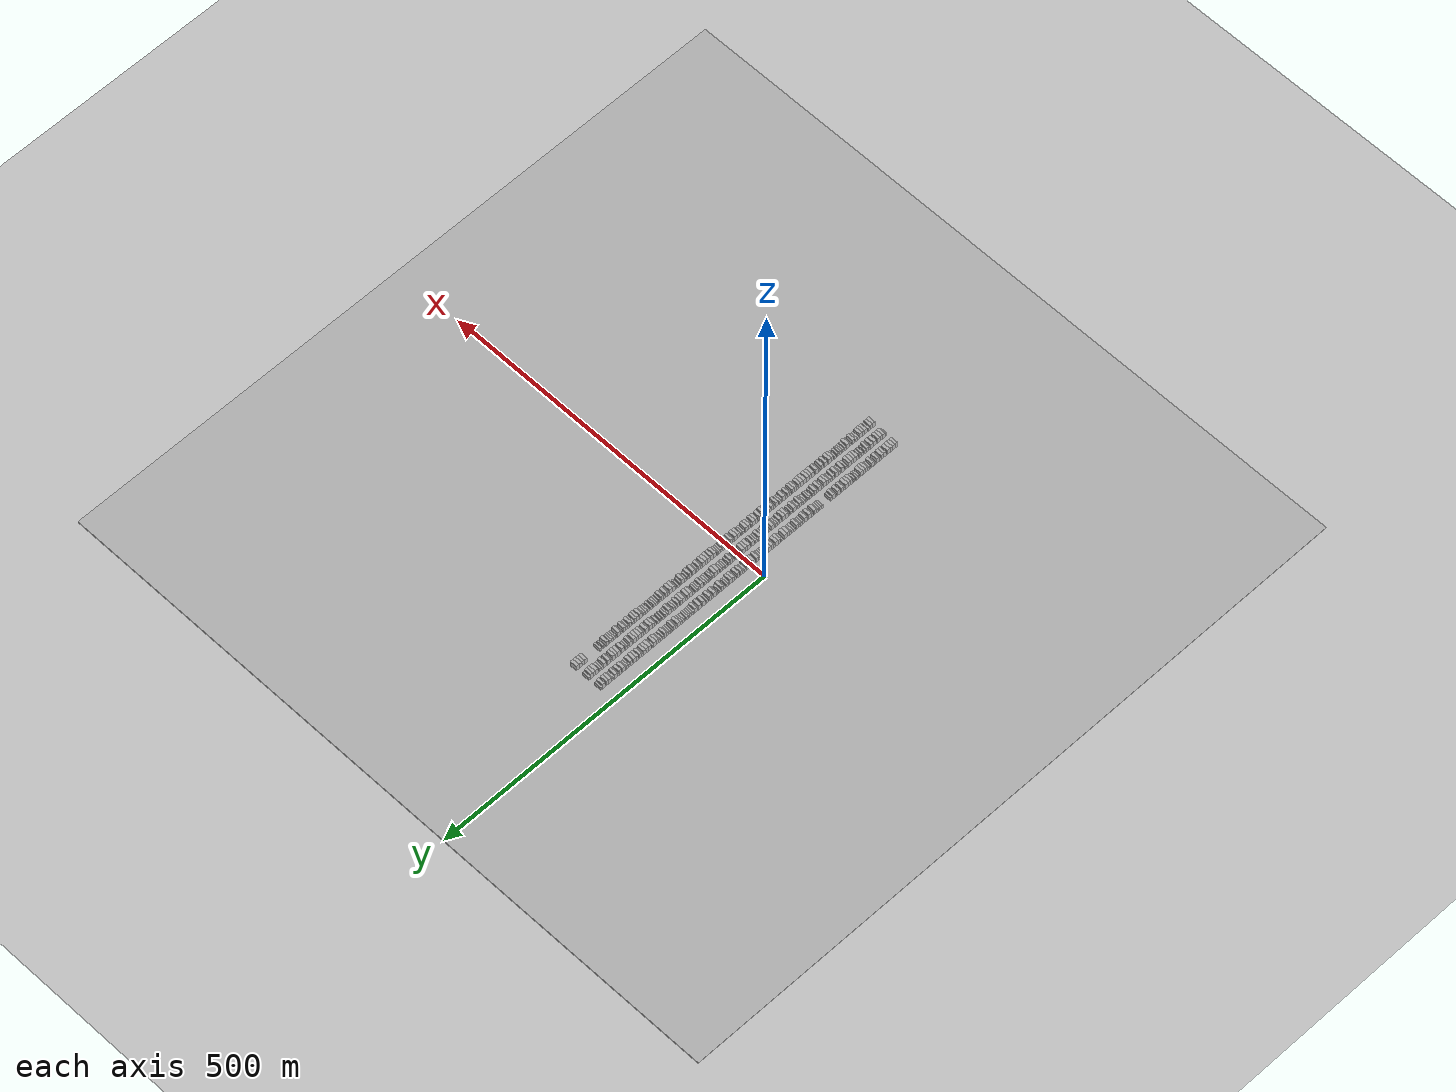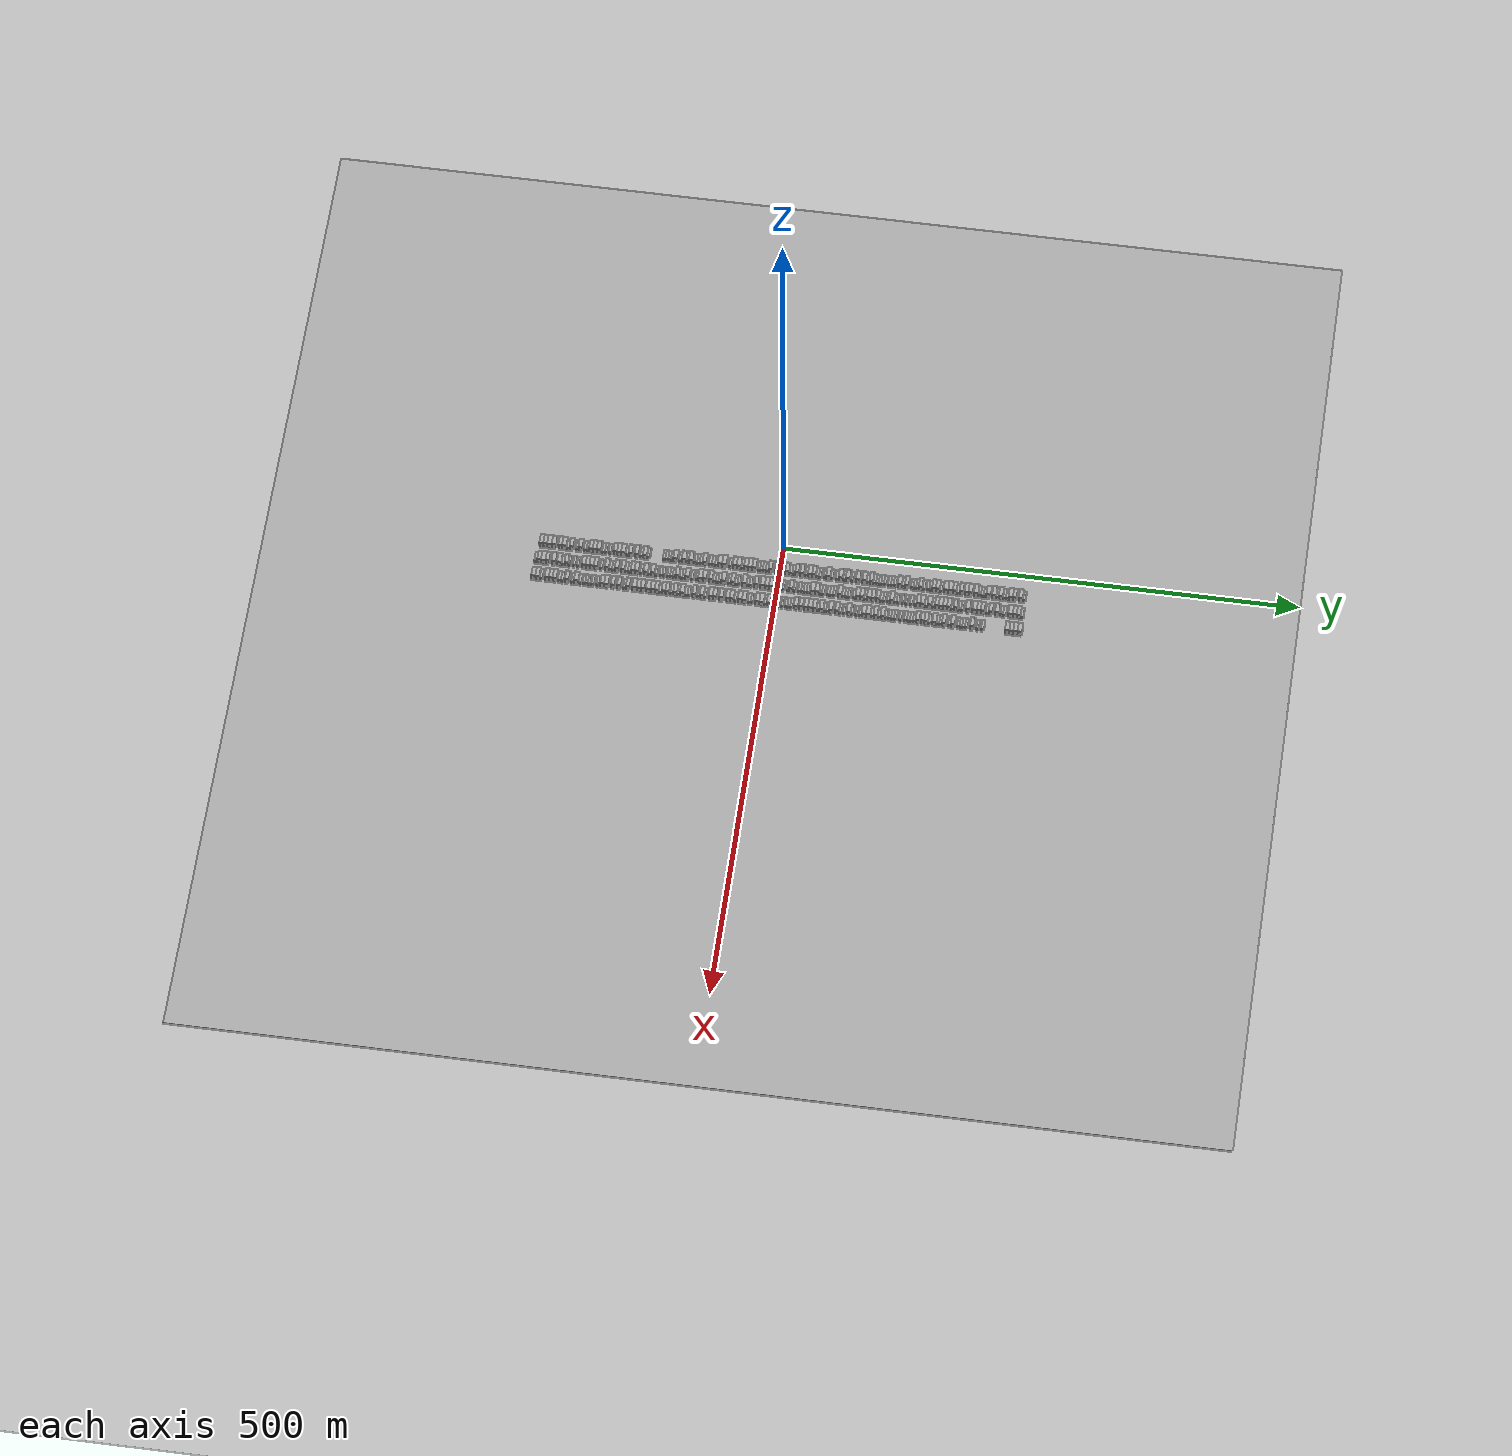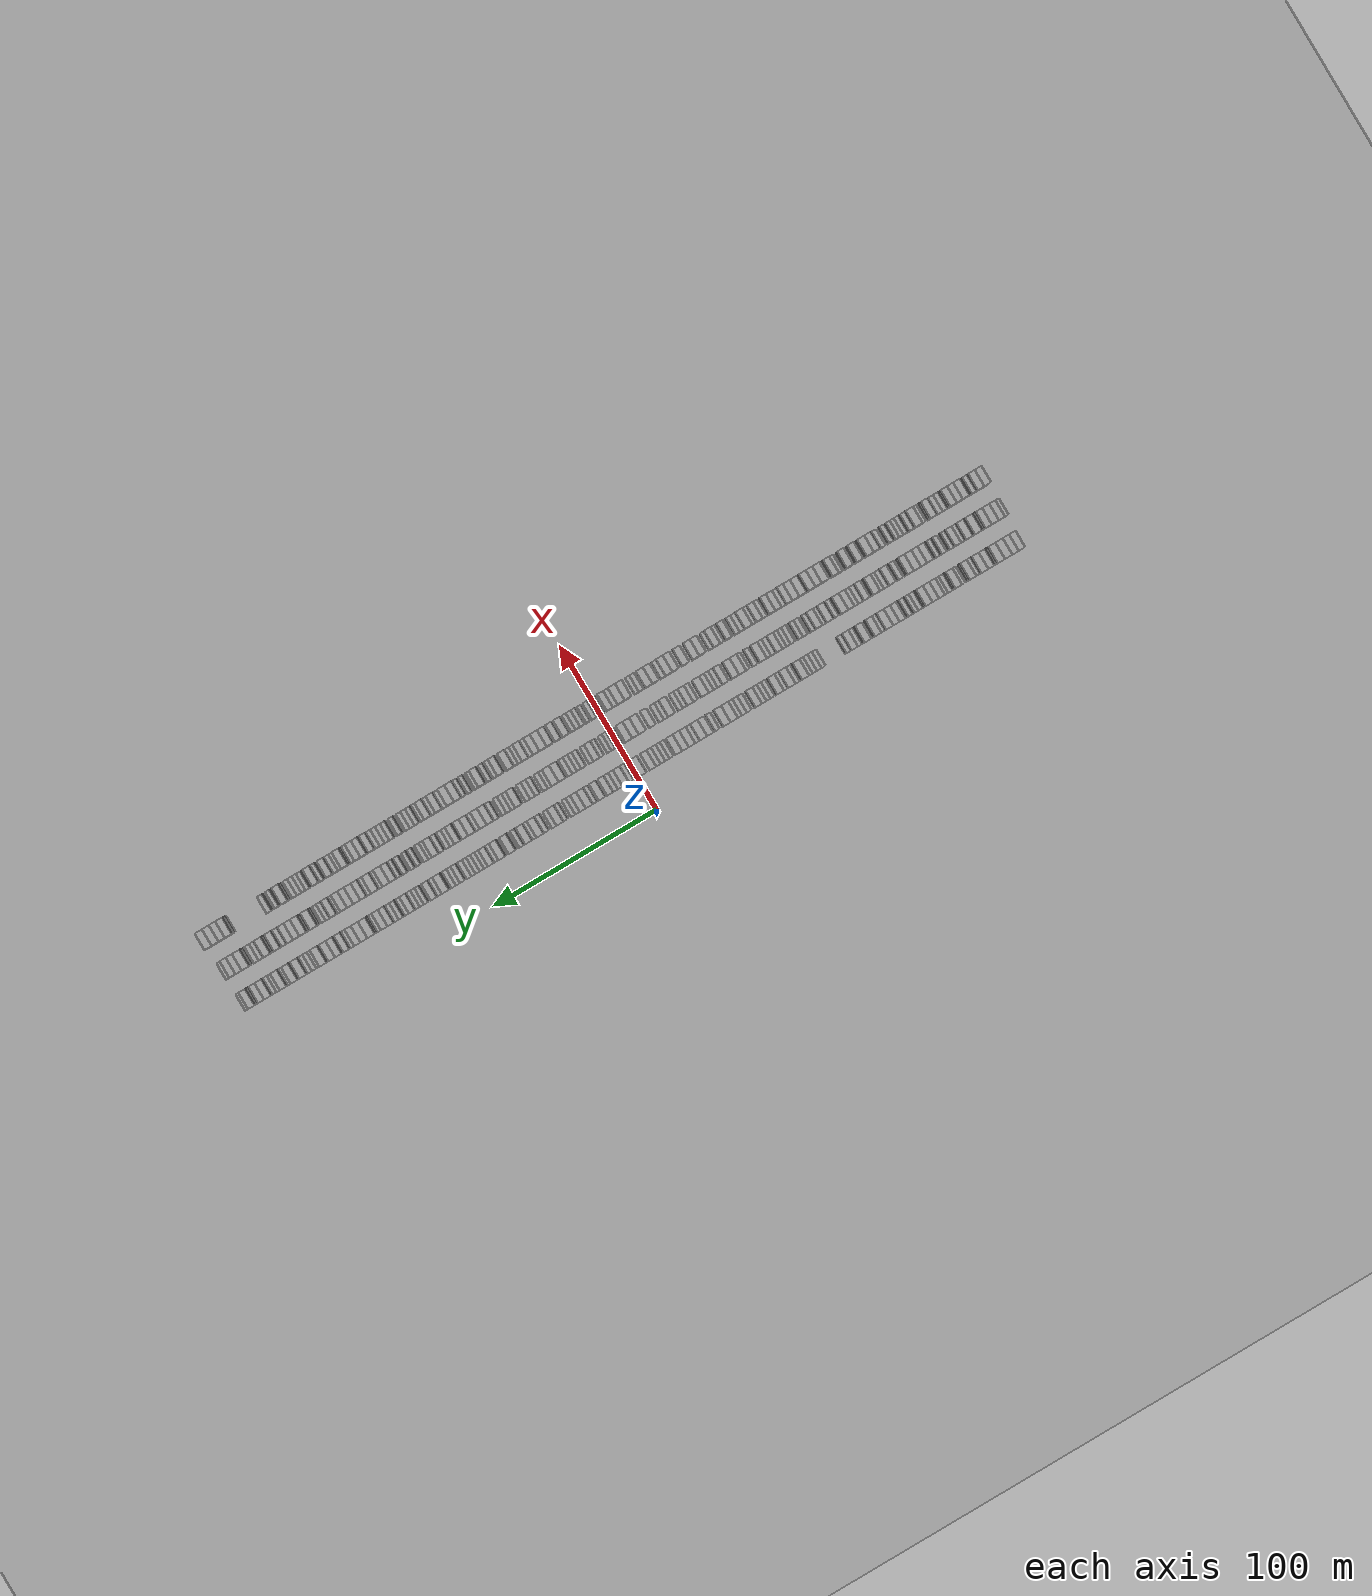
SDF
<?xml version="1.0" encoding="utf-8"?>

<sdf version="1.6">

   <world name="default">

      <gui fullscreen="0">

         <camera name="user_camera">

            <pose>-15 0 4.57585 0 0 0</pose>

            <view_controller>orbit</view_controller>

         </camera>

      </gui>

      <scene>

         <sky>

           <clouds>

             <speed>12</speed>

           </clouds>

         </sky>

         <ambient>0.4 0.4 0.4 1</ambient>

         <background>0.7 0.7 0.7 1</background>

         <shadows>1</shadows>

      </scene>

      <gravity>0 0 -9.8066</gravity>

      <magnetic_field>6e-06 2.3e-05 -4.2e-05</magnetic_field>

      <physics default="0" name="default_physics" type="ode">

         <ode>

            <solver>

               <type>quick</type>

               <iters>10</iters>

               <sor>1.0</sor>

               <use_dynamic_moi_rescaling>0</use_dynamic_moi_rescaling>

            </solver>

            <constraints>

               <cfm>0</cfm>

               <erp>0.2</erp>

               <contact_max_correcting_vel>100</contact_max_correcting_vel>

               <contact_surface_layer>0.001</contact_surface_layer>

            </constraints>

         </ode>

         <max_step_size>0.004</max_step_size>

         <real_time_factor>1</real_time_factor>

         <real_time_update_rate>250</real_time_update_rate>

      </physics>

      <light name="sun" type="directional">

         <cast_shadows>1</cast_shadows>

         <pose>0 0 10 0 0 0</pose>

         <diffuse>0.8 0.8 0.8 1</diffuse>

         <specular>0.2 0.2 0.2 1</specular>

         <attenuation>

            <range>1000</range>

            <constant>0.9</constant>

            <linear>0.01</linear>

            <quadratic>0.001</quadratic>

         </attenuation>

         <direction>-0.5 0.1 -0.9</direction>

      </light>

      <include>

         <name>ground_plane_1</name>

         <uri>model://HANNAS_ground_plane</uri>

         <pose>0 0 0  0 0 0</pose>

      </include>

      <include>

         <name>ground_plane_2</name>

         <uri>model://HANNAS_ground_plane</uri>

         <pose>100 0 0  0 0 0</pose>

      </include>

      <model name="building_1">

         <static>1</static>

         <pose frame="">25.0000 -232.0497 0 0.000000 0.000000 0.000000</pose>

         <link name="link">

            <pose frame="">0 0 4.50 0 0 0</pose>

            <collision name="collision">

               <geometry>

                  <box>

                     <size>10.0000 3.9007 9.0000</size>

                  </box>

               </geometry>

               <max_contacts>10</max_contacts>

               <surface>

                  <contact>

                     <ode/>

                  </contact>

                  <bounce/>

                  <friction>

                     <torsional>

                        <ode/>

                     </torsional>

                     <ode/>

                  </friction>

               </surface>

            </collision>

            <visual name="visual">

               <cast_shadows>0</cast_shadows>

               <geometry>

                  <box>

                     <size>10.0000 3.9007 9.0000</size>

                  </box>

               </geometry>

               <material>

                  <script>

                     <uri>model://HANNAS_wall/materials/scripts</uri>

                     <uri>model://HANNAS_wall/materials/textures</uri>

                     <name>vrc/HANNAS_wall</name>

                  </script>

               </material>

            </visual>

            <self_collide>0</self_collide>

            <enable_wind>0</enable_wind>

            <kinematic>0</kinematic>

         </link>

      </model>

      <model name="building_2">

         <static>1</static>

         <pose frame="">25.0000 -228.1832 0 0.000000 0.000000 0.000000</pose>

         <link name="link">

            <pose frame="">0 0 4.50 0 0 0</pose>

            <collision name="collision">

               <geometry>

                  <box>

                     <size>10.0000 3.8322 9.0000</size>

                  </box>

               </geometry>

               <max_contacts>10</max_contacts>

               <surface>

                  <contact>

                     <ode/>

                  </contact>

                  <bounce/>

                  <friction>

                     <torsional>

                        <ode/>

                     </torsional>

                     <ode/>

                  </friction>

               </surface>

            </collision>

            <visual name="visual">

               <cast_shadows>0</cast_shadows>

               <geometry>

                  <box>

                     <size>10.0000 3.8322 9.0000</size>

                  </box>

               </geometry>

               <material>

                  <script>

                     <uri>model://HANNAS_wall/materials/scripts</uri>

                     <uri>model://HANNAS_wall/materials/textures</uri>

                     <name>vrc/HANNAS_wall</name>

                  </script>

               </material>

            </visual>

            <self_collide>0</self_collide>

            <enable_wind>0</enable_wind>

            <kinematic>0</kinematic>

         </link>

      </model>

      <model name="building_3">

         <static>1</static>

         <pose frame="">25.0000 -224.0570 0 0.000000 0.000000 0.000000</pose>

         <link name="link">

            <pose frame="">0 0 4.50 0 0 0</pose>

            <collision name="collision">

               <geometry>

                  <box>

                     <size>10.0000 4.4203 9.0000</size>

                  </box>

               </geometry>

               <max_contacts>10</max_contacts>

               <surface>

                  <contact>

                     <ode/>

                  </contact>

                  <bounce/>

                  <friction>

                     <torsional>

                        <ode/>

                     </torsional>

                     <ode/>

                  </friction>

               </surface>

            </collision>

            <visual name="visual">

               <cast_shadows>0</cast_shadows>

               <geometry>

                  <box>

                     <size>10.0000 4.4203 9.0000</size>

                  </box>

               </geometry>

               <material>

                  <script>

                     <uri>model://HANNAS_wall/materials/scripts</uri>

                     <uri>model://HANNAS_wall/materials/textures</uri>

                     <name>vrc/HANNAS_wall</name>

                  </script>

               </material>

            </visual>

            <self_collide>0</self_collide>

            <enable_wind>0</enable_wind>

            <kinematic>0</kinematic>

         </link>

      </model>

      <model name="building_4">

         <static>1</static>

         <pose frame="">25.0000 -219.6432 0 0.000000 0.000000 0.000000</pose>

         <link name="link">

            <pose frame="">0 0 4.50 0 0 0</pose>

            <collision name="collision">

               <geometry>

                  <box>

                     <size>10.0000 4.4071 9.0000</size>

                  </box>

               </geometry>

               <max_contacts>10</max_contacts>

               <surface>

                  <contact>

                     <ode/>

                  </contact>

                  <bounce/>

                  <friction>

                     <torsional>

                        <ode/>

                     </torsional>

                     <ode/>

                  </friction>

               </surface>

            </collision>

            <visual name="visual">

               <cast_shadows>0</cast_shadows>

               <geometry>

                  <box>

                     <size>10.0000 4.4071 9.0000</size>

                  </box>

               </geometry>

               <material>

                  <script>

                     <uri>model://HANNAS_wall/materials/scripts</uri>

                     <uri>model://HANNAS_wall/materials/textures</uri>

                     <name>vrc/HANNAS_wall</name>

                  </script>

               </material>

            </visual>

            <self_collide>0</self_collide>

            <enable_wind>0</enable_wind>

            <kinematic>0</kinematic>

         </link>

      </model>

      <model name="building_5">

         <static>1</static>

         <pose frame="">25.0000 -213.6147 0 0.000000 0.000000 0.000000</pose>

         <link name="link">

            <pose frame="">0 0 4.50 0 0 0</pose>

            <collision name="collision">

               <geometry>

                  <box>

                     <size>10.0000 3.6499 9.0000</size>

                  </box>

               </geometry>

               <max_contacts>10</max_contacts>

               <surface>

                  <contact>

                     <ode/>

                  </contact>

                  <bounce/>

                  <friction>

                     <torsional>

                        <ode/>

                     </torsional>

                     <ode/>

                  </friction>

               </surface>

            </collision>

            <visual name="visual">

               <cast_shadows>0</cast_shadows>

               <geometry>

                  <box>

                     <size>10.0000 3.6499 9.0000</size>

                  </box>

               </geometry>

               <material>

                  <script>

                     <uri>model://HANNAS_wall/materials/scripts</uri>

                     <uri>model://HANNAS_wall/materials/textures</uri>

                     <name>vrc/HANNAS_wall</name>

                  </script>

               </material>

            </visual>

            <self_collide>0</self_collide>

            <enable_wind>0</enable_wind>

            <kinematic>0</kinematic>

         </link>

      </model>

      <model name="building_6">

         <static>1</static>

         <pose frame="">25.0000 -209.6266 0 0.000000 0.000000 0.000000</pose>

         <link name="link">

            <pose frame="">0 0 4.50 0 0 0</pose>

            <collision name="collision">

               <geometry>

                  <box>

                     <size>10.0000 4.3262 9.0000</size>

                  </box>

               </geometry>

               <max_contacts>10</max_contacts>

               <surface>

                  <contact>

                     <ode/>

                  </contact>

                  <bounce/>

                  <friction>

                     <torsional>

                        <ode/>

                     </torsional>

                     <ode/>

                  </friction>

               </surface>

            </collision>

            <visual name="visual">

               <cast_shadows>0</cast_shadows>

               <geometry>

                  <box>

                     <size>10.0000 4.3262 9.0000</size>

                  </box>

               </geometry>

               <material>

                  <script>

                     <uri>model://HANNAS_wall/materials/scripts</uri>

                     <uri>model://HANNAS_wall/materials/textures</uri>

                     <name>vrc/HANNAS_wall</name>

                  </script>

               </material>

            </visual>

            <self_collide>0</self_collide>

            <enable_wind>0</enable_wind>

            <kinematic>0</kinematic>

         </link>

      </model>

      <model name="building_7">

         <static>1</static>

         <pose frame="">25.0000 -206.0211 0 0.000000 0.000000 0.000000</pose>

         <link name="link">

            <pose frame="">0 0 3.00 0 0 0</pose>

            <collision name="collision">

               <geometry>

                  <box>

                     <size>10.0000 2.8849 6.0000</size>

                  </box>

               </geometry>

               <max_contacts>10</max_contacts>

               <surface>

                  <contact>

                     <ode/>

                  </contact>

                  <bounce/>

                  <friction>

                     <torsional>

                        <ode/>

                     </torsional>

                     <ode/>

                  </friction>

               </surface>

            </collision>

            <visual name="visual">

               <cast_shadows>0</cast_shadows>

               <geometry>

                  <box>

                     <size>10.0000 2.8849 6.0000</size>

                  </box>

               </geometry>

               <material>

                  <script>

                     <uri>model://HANNAS_wall/materials/scripts</uri>

                     <uri>model://HANNAS_wall/materials/textures</uri>

                     <name>vrc/HANNAS_wall</name>

                  </script>

               </material>

            </visual>

            <self_collide>0</self_collide>

            <enable_wind>0</enable_wind>

            <kinematic>0</kinematic>

         </link>

      </model>

      <model name="building_8">

         <static>1</static>

         <pose frame="">25.0000 -202.5647 0 0.000000 0.000000 0.000000</pose>

         <link name="link">

            <pose frame="">0 0 4.50 0 0 0</pose>

            <collision name="collision">

               <geometry>

                  <box>

                     <size>10.0000 4.0280 9.0000</size>

                  </box>

               </geometry>

               <max_contacts>10</max_contacts>

               <surface>

                  <contact>

                     <ode/>

                  </contact>

                  <bounce/>

                  <friction>

                     <torsional>

                        <ode/>

                     </torsional>

                     <ode/>

                  </friction>

               </surface>

            </collision>

            <visual name="visual">

               <cast_shadows>0</cast_shadows>

               <geometry>

                  <box>

                     <size>10.0000 4.0280 9.0000</size>

                  </box>

               </geometry>

               <material>

                  <script>

                     <uri>model://HANNAS_wall/materials/scripts</uri>

                     <uri>model://HANNAS_wall/materials/textures</uri>

                     <name>vrc/HANNAS_wall</name>

                  </script>

               </material>

            </visual>

            <self_collide>0</self_collide>

            <enable_wind>0</enable_wind>

            <kinematic>0</kinematic>

         </link>

      </model>

      <model name="building_9">

         <static>1</static>

         <pose frame="">25.0000 -197.2257 0 0.000000 0.000000 0.000000</pose>

         <link name="link">

            <pose frame="">0 0 3.00 0 0 0</pose>

            <collision name="collision">

               <geometry>

                  <box>

                     <size>10.0000 2.6500 6.0000</size>

                  </box>

               </geometry>

               <max_contacts>10</max_contacts>

               <surface>

                  <contact>

                     <ode/>

                  </contact>

                  <bounce/>

                  <friction>

                     <torsional>

                        <ode/>

                     </torsional>

                     <ode/>

                  </friction>

               </surface>

            </collision>

            <visual name="visual">

               <cast_shadows>0</cast_shadows>

               <geometry>

                  <box>

                     <size>10.0000 2.6500 6.0000</size>

                  </box>

               </geometry>

               <material>

                  <script>

                     <uri>model://HANNAS_wall/materials/scripts</uri>

                     <uri>model://HANNAS_wall/materials/textures</uri>

                     <name>vrc/HANNAS_wall</name>

                  </script>

               </material>

            </visual>

            <self_collide>0</self_collide>

            <enable_wind>0</enable_wind>

            <kinematic>0</kinematic>

         </link>

      </model>

      <model name="building_10">

         <static>1</static>

         <pose frame="">25.0000 -193.8493 0 0.000000 0.000000 0.000000</pose>

         <link name="link">

            <pose frame="">0 0 4.50 0 0 0</pose>

            <collision name="collision">

               <geometry>

                  <box>

                     <size>10.0000 4.1030 9.0000</size>

                  </box>

               </geometry>

               <max_contacts>10</max_contacts>

               <surface>

                  <contact>

                     <ode/>

                  </contact>

                  <bounce/>

                  <friction>

                     <torsional>

                        <ode/>

                     </torsional>

                     <ode/>

                  </friction>

               </surface>

            </collision>

            <visual name="visual">

               <cast_shadows>0</cast_shadows>

               <geometry>

                  <box>

                     <size>10.0000 4.1030 9.0000</size>

                  </box>

               </geometry>

               <material>

                  <script>

                     <uri>model://HANNAS_wall/materials/scripts</uri>

                     <uri>model://HANNAS_wall/materials/textures</uri>

                     <name>vrc/HANNAS_wall</name>

                  </script>

               </material>

            </visual>

            <self_collide>0</self_collide>

            <enable_wind>0</enable_wind>

            <kinematic>0</kinematic>

         </link>

      </model>

      <model name="building_11">

         <static>1</static>

         <pose frame="">25.0000 -189.4213 0 0.000000 0.000000 0.000000</pose>

         <link name="link">

            <pose frame="">0 0 3.00 0 0 0</pose>

            <collision name="collision">

               <geometry>

                  <box>

                     <size>10.0000 2.7529 6.0000</size>

                  </box>

               </geometry>

               <max_contacts>10</max_contacts>

               <surface>

                  <contact>

                     <ode/>

                  </contact>

                  <bounce/>

                  <friction>

                     <torsional>

                        <ode/>

                     </torsional>

                     <ode/>

                  </friction>

               </surface>

            </collision>

            <visual name="visual">

               <cast_shadows>0</cast_shadows>

               <geometry>

                  <box>

                     <size>10.0000 2.7529 6.0000</size>

                  </box>

               </geometry>

               <material>

                  <script>

                     <uri>model://HANNAS_wall/materials/scripts</uri>

                     <uri>model://HANNAS_wall/materials/textures</uri>

                     <name>vrc/HANNAS_wall</name>

                  </script>

               </material>

            </visual>

            <self_collide>0</self_collide>

            <enable_wind>0</enable_wind>

            <kinematic>0</kinematic>

         </link>

      </model>

      <model name="building_12">

         <static>1</static>

         <pose frame="">25.0000 -186.8052 0 0.000000 0.000000 0.000000</pose>

         <link name="link">

            <pose frame="">0 0 3.00 0 0 0</pose>

            <collision name="collision">

               <geometry>

                  <box>

                     <size>10.0000 2.4793 6.0000</size>

                  </box>

               </geometry>

               <max_contacts>10</max_contacts>

               <surface>

                  <contact>

                     <ode/>

                  </contact>

                  <bounce/>

                  <friction>

                     <torsional>

                        <ode/>

                     </torsional>

                     <ode/>

                  </friction>

               </surface>

            </collision>

            <visual name="visual">

               <cast_shadows>0</cast_shadows>

               <geometry>

                  <box>

                     <size>10.0000 2.4793 6.0000</size>

                  </box>

               </geometry>

               <material>

                  <script>

                     <uri>model://HANNAS_wall/materials/scripts</uri>

                     <uri>model://HANNAS_wall/materials/textures</uri>

                     <name>vrc/HANNAS_wall</name>

                  </script>

               </material>

            </visual>

            <self_collide>0</self_collide>

            <enable_wind>0</enable_wind>

            <kinematic>0</kinematic>

         </link>

      </model>

      <model name="building_13">

         <static>1</static>

         <pose frame="">25.0000 -183.7613 0 0.000000 0.000000 0.000000</pose>

         <link name="link">

            <pose frame="">0 0 4.50 0 0 0</pose>

            <collision name="collision">

               <geometry>

                  <box>

                     <size>10.0000 3.6085 9.0000</size>

                  </box>

               </geometry>

               <max_contacts>10</max_contacts>

               <surface>

                  <contact>

                     <ode/>

                  </contact>

                  <bounce/>

                  <friction>

                     <torsional>

                        <ode/>

                     </torsional>

                     <ode/>

                  </friction>

               </surface>

            </collision>

            <visual name="visual">

               <cast_shadows>0</cast_shadows>

               <geometry>

                  <box>

                     <size>10.0000 3.6085 9.0000</size>

                  </box>

               </geometry>

               <material>

                  <script>

                     <uri>model://HANNAS_wall/materials/scripts</uri>

                     <uri>model://HANNAS_wall/materials/textures</uri>

                     <name>vrc/HANNAS_wall</name>

                  </script>

               </material>

            </visual>

            <self_collide>0</self_collide>

            <enable_wind>0</enable_wind>

            <kinematic>0</kinematic>

         </link>

      </model>

      <model name="building_14">

         <static>1</static>

         <pose frame="">25.0000 -180.0130 0 0.000000 0.000000 0.000000</pose>

         <link name="link">

            <pose frame="">0 0 4.50 0 0 0</pose>

            <collision name="collision">

               <geometry>

                  <box>

                     <size>10.0000 3.8881 9.0000</size>

                  </box>

               </geometry>

               <max_contacts>10</max_contacts>

               <surface>

                  <contact>

                     <ode/>

                  </contact>

                  <bounce/>

                  <friction>

                     <torsional>

                        <ode/>

                     </torsional>

                     <ode/>

                  </friction>

               </surface>

            </collision>

            <visual name="visual">

               <cast_shadows>0</cast_shadows>

               <geometry>

                  <box>

                     <size>10.0000 3.8881 9.0000</size>

                  </box>

               </geometry>

               <material>

                  <script>

                     <uri>model://HANNAS_wall/materials/scripts</uri>

                     <uri>model://HANNAS_wall/materials/textures</uri>

                     <name>vrc/HANNAS_wall</name>

                  </script>

               </material>

            </visual>

            <self_collide>0</self_collide>

            <enable_wind>0</enable_wind>

            <kinematic>0</kinematic>

         </link>

      </model>

      <model name="building_15">

         <static>1</static>

         <pose frame="">25.0000 -175.9496 0 0.000000 0.000000 0.000000</pose>

         <link name="link">

            <pose frame="">0 0 4.50 0 0 0</pose>

            <collision name="collision">

               <geometry>

                  <box>

                     <size>10.0000 4.2389 9.0000</size>

                  </box>

               </geometry>

               <max_contacts>10</max_contacts>

               <surface>

                  <contact>

                     <ode/>

                  </contact>

                  <bounce/>

                  <friction>

                     <torsional>

                        <ode/>

                     </torsional>

                     <ode/>

                  </friction>

               </surface>

            </collision>

            <visual name="visual">

               <cast_shadows>0</cast_shadows>

               <geometry>

                  <box>

                     <size>10.0000 4.2389 9.0000</size>

                  </box>

               </geometry>

               <material>

                  <script>

                     <uri>model://HANNAS_wall/materials/scripts</uri>

                     <uri>model://HANNAS_wall/materials/textures</uri>

                     <name>vrc/HANNAS_wall</name>

                  </script>

               </material>

            </visual>

            <self_collide>0</self_collide>

            <enable_wind>0</enable_wind>

            <kinematic>0</kinematic>

         </link>

      </model>

      <model name="building_16">

         <static>1</static>

         <pose frame="">25.0000 -171.4326 0 0.000000 0.000000 0.000000</pose>

         <link name="link">

            <pose frame="">0 0 3.00 0 0 0</pose>

            <collision name="collision">

               <geometry>

                  <box>

                     <size>10.0000 2.7951 6.0000</size>

                  </box>

               </geometry>

               <max_contacts>10</max_contacts>

               <surface>

                  <contact>

                     <ode/>

                  </contact>

                  <bounce/>

                  <friction>

                     <torsional>

                        <ode/>

                     </torsional>

                     <ode/>

                  </friction>

               </surface>

            </collision>

            <visual name="visual">

               <cast_shadows>0</cast_shadows>

               <geometry>

                  <box>

                     <size>10.0000 2.7951 6.0000</size>

                  </box>

               </geometry>

               <material>

                  <script>

                     <uri>model://HANNAS_wall/materials/scripts</uri>

                     <uri>model://HANNAS_wall/materials/textures</uri>

                     <name>vrc/HANNAS_wall</name>

                  </script>

               </material>

            </visual>

            <self_collide>0</self_collide>

            <enable_wind>0</enable_wind>

            <kinematic>0</kinematic>

         </link>

      </model>

      <model name="building_17">

         <static>1</static>

         <pose frame="">25.0000 -168.8290 0 0.000000 0.000000 0.000000</pose>

         <link name="link">

            <pose frame="">0 0 3.00 0 0 0</pose>

            <collision name="collision">

               <geometry>

                  <box>

                     <size>10.0000 2.4120 6.0000</size>

                  </box>

               </geometry>

               <max_contacts>10</max_contacts>

               <surface>

                  <contact>

                     <ode/>

                  </contact>

                  <bounce/>

                  <friction>

                     <torsional>

                        <ode/>

                     </torsional>

                     <ode/>

                  </friction>

               </surface>

            </collision>

            <visual name="visual">

               <cast_shadows>0</cast_shadows>

               <geometry>

                  <box>

                     <size>10.0000 2.4120 6.0000</size>

                  </box>

               </geometry>

               <material>

                  <script>

                     <uri>model://HANNAS_wall/materials/scripts</uri>

                     <uri>model://HANNAS_wall/materials/textures</uri>

                     <name>vrc/HANNAS_wall</name>

                  </script>

               </material>

            </visual>

            <self_collide>0</self_collide>

            <enable_wind>0</enable_wind>

            <kinematic>0</kinematic>

         </link>

      </model>

      <model name="building_18">

         <static>1</static>

         <pose frame="">25.0000 -165.2349 0 0.000000 0.000000 0.000000</pose>

         <link name="link">

            <pose frame="">0 0 3.00 0 0 0</pose>

            <collision name="collision">

               <geometry>

                  <box>

                     <size>10.0000 2.7762 6.0000</size>

                  </box>

               </geometry>

               <max_contacts>10</max_contacts>

               <surface>

                  <contact>

                     <ode/>

                  </contact>

                  <bounce/>

                  <friction>

                     <torsional>

                        <ode/>

                     </torsional>

                     <ode/>

                  </friction>

               </surface>

            </collision>

            <visual name="visual">

               <cast_shadows>0</cast_shadows>

               <geometry>

                  <box>

                     <size>10.0000 2.7762 6.0000</size>

                  </box>

               </geometry>

               <material>

                  <script>

                     <uri>model://HANNAS_wall/materials/scripts</uri>

                     <uri>model://HANNAS_wall/materials/textures</uri>

                     <name>vrc/HANNAS_wall</name>

                  </script>

               </material>

            </visual>

            <self_collide>0</self_collide>

            <enable_wind>0</enable_wind>

            <kinematic>0</kinematic>

         </link>

      </model>

      <model name="building_19">

         <static>1</static>

         <pose frame="">25.0000 -160.0012 0 0.000000 0.000000 0.000000</pose>

         <link name="link">

            <pose frame="">0 0 4.50 0 0 0</pose>

            <collision name="collision">

               <geometry>

                  <box>

                     <size>10.0000 3.6912 9.0000</size>

                  </box>

               </geometry>

               <max_contacts>10</max_contacts>

               <surface>

                  <contact>

                     <ode/>

                  </contact>

                  <bounce/>

                  <friction>

                     <torsional>

                        <ode/>

                     </torsional>

                     <ode/>

                  </friction>

               </surface>

            </collision>

            <visual name="visual">

               <cast_shadows>0</cast_shadows>

               <geometry>

                  <box>

                     <size>10.0000 3.6912 9.0000</size>

                  </box>

               </geometry>

               <material>

                  <script>

                     <uri>model://HANNAS_wall/materials/scripts</uri>

                     <uri>model://HANNAS_wall/materials/textures</uri>

                     <name>vrc/HANNAS_wall</name>

                  </script>

               </material>

            </visual>

            <self_collide>0</self_collide>

            <enable_wind>0</enable_wind>

            <kinematic>0</kinematic>

         </link>

      </model>

      <model name="building_20">

         <static>1</static>

         <pose frame="">25.0000 -156.2559 0 0.000000 0.000000 0.000000</pose>

         <link name="link">

            <pose frame="">0 0 4.50 0 0 0</pose>

            <collision name="collision">

               <geometry>

                  <box>

                     <size>10.0000 3.7994 9.0000</size>

                  </box>

               </geometry>

               <max_contacts>10</max_contacts>

               <surface>

                  <contact>

                     <ode/>

                  </contact>

                  <bounce/>

                  <friction>

                     <torsional>

                        <ode/>

                     </torsional>

                     <ode/>

                  </friction>

               </surface>

            </collision>

            <visual name="visual">

               <cast_shadows>0</cast_shadows>

               <geometry>

                  <box>

                     <size>10.0000 3.7994 9.0000</size>

                  </box>

               </geometry>

               <material>

                  <script>

                     <uri>model://HANNAS_wall/materials/scripts</uri>

                     <uri>model://HANNAS_wall/materials/textures</uri>

                     <name>vrc/HANNAS_wall</name>

                  </script>

               </material>

            </visual>

            <self_collide>0</self_collide>

            <enable_wind>0</enable_wind>

            <kinematic>0</kinematic>

         </link>

      </model>

      <model name="building_21">

         <static>1</static>

         <pose frame="">25.0000 -152.1520 0 0.000000 0.000000 0.000000</pose>

         <link name="link">

            <pose frame="">0 0 4.50 0 0 0</pose>

            <collision name="collision">

               <geometry>

                  <box>

                     <size>10.0000 4.4084 9.0000</size>

                  </box>

               </geometry>

               <max_contacts>10</max_contacts>

               <surface>

                  <contact>

                     <ode/>

                  </contact>

                  <bounce/>

                  <friction>

                     <torsional>

                        <ode/>

                     </torsional>

                     <ode/>

                  </friction>

               </surface>

            </collision>

            <visual name="visual">

               <cast_shadows>0</cast_shadows>

               <geometry>

                  <box>

                     <size>10.0000 4.4084 9.0000</size>

                  </box>

               </geometry>

               <material>

                  <script>

                     <uri>model://HANNAS_wall/materials/scripts</uri>

                     <uri>model://HANNAS_wall/materials/textures</uri>

                     <name>vrc/HANNAS_wall</name>

                  </script>

               </material>

            </visual>

            <self_collide>0</self_collide>

            <enable_wind>0</enable_wind>

            <kinematic>0</kinematic>

         </link>

      </model>

      <model name="building_22">

         <static>1</static>

         <pose frame="">25.0000 -148.5729 0 0.000000 0.000000 0.000000</pose>

         <link name="link">

            <pose frame="">0 0 3.00 0 0 0</pose>

            <collision name="collision">

               <geometry>

                  <box>

                     <size>10.0000 2.7499 6.0000</size>

                  </box>

               </geometry>

               <max_contacts>10</max_contacts>

               <surface>

                  <contact>

                     <ode/>

                  </contact>

                  <bounce/>

                  <friction>

                     <torsional>

                        <ode/>

                     </torsional>

                     <ode/>

                  </friction>

               </surface>

            </collision>

            <visual name="visual">

               <cast_shadows>0</cast_shadows>

               <geometry>

                  <box>

                     <size>10.0000 2.7499 6.0000</size>

                  </box>

               </geometry>

               <material>

                  <script>

                     <uri>model://HANNAS_wall/materials/scripts</uri>

                     <uri>model://HANNAS_wall/materials/textures</uri>

                     <name>vrc/HANNAS_wall</name>

                  </script>

               </material>

            </visual>

            <self_collide>0</self_collide>

            <enable_wind>0</enable_wind>

            <kinematic>0</kinematic>

         </link>

      </model>

      <model name="building_23">

         <static>1</static>

         <pose frame="">25.0000 -145.1866 0 0.000000 0.000000 0.000000</pose>

         <link name="link">

            <pose frame="">0 0 4.50 0 0 0</pose>

            <collision name="collision">

               <geometry>

                  <box>

                     <size>10.0000 4.0226 9.0000</size>

                  </box>

               </geometry>

               <max_contacts>10</max_contacts>

               <surface>

                  <contact>

                     <ode/>

                  </contact>

                  <bounce/>

                  <friction>

                     <torsional>

                        <ode/>

                     </torsional>

                     <ode/>

                  </friction>

               </surface>

            </collision>

            <visual name="visual">

               <cast_shadows>0</cast_shadows>

               <geometry>

                  <box>

                     <size>10.0000 4.0226 9.0000</size>

                  </box>

               </geometry>

               <material>

                  <script>

                     <uri>model://HANNAS_wall/materials/scripts</uri>

                     <uri>model://HANNAS_wall/materials/textures</uri>

                     <name>vrc/HANNAS_wall</name>

                  </script>

               </material>

            </visual>

            <self_collide>0</self_collide>

            <enable_wind>0</enable_wind>

            <kinematic>0</kinematic>

         </link>

      </model>

      <model name="building_24">

         <static>1</static>

         <pose frame="">25.0000 -139.0597 0 0.000000 0.000000 0.000000</pose>

         <link name="link">

            <pose frame="">0 0 4.50 0 0 0</pose>

            <collision name="collision">

               <geometry>

                  <box>

                     <size>10.0000 4.2311 9.0000</size>

                  </box>

               </geometry>

               <max_contacts>10</max_contacts>

               <surface>

                  <contact>

                     <ode/>

                  </contact>

                  <bounce/>

                  <friction>

                     <torsional>

                        <ode/>

                     </torsional>

                     <ode/>

                  </friction>

               </surface>

            </collision>

            <visual name="visual">

               <cast_shadows>0</cast_shadows>

               <geometry>

                  <box>

                     <size>10.0000 4.2311 9.0000</size>

                  </box>

               </geometry>

               <material>

                  <script>

                     <uri>model://HANNAS_wall/materials/scripts</uri>

                     <uri>model://HANNAS_wall/materials/textures</uri>

                     <name>vrc/HANNAS_wall</name>

                  </script>

               </material>

            </visual>

            <self_collide>0</self_collide>

            <enable_wind>0</enable_wind>

            <kinematic>0</kinematic>

         </link>

      </model>

      <model name="building_25">

         <static>1</static>

         <pose frame="">25.0000 -134.4918 0 0.000000 0.000000 0.000000</pose>

         <link name="link">

            <pose frame="">0 0 3.00 0 0 0</pose>

            <collision name="collision">

               <geometry>

                  <box>

                     <size>10.0000 2.9048 6.0000</size>

                  </box>

               </geometry>

               <max_contacts>10</max_contacts>

               <surface>

                  <contact>

                     <ode/>

                  </contact>

                  <bounce/>

                  <friction>

                     <torsional>

                        <ode/>

                     </torsional>

                     <ode/>

                  </friction>

               </surface>

            </collision>

            <visual name="visual">

               <cast_shadows>0</cast_shadows>

               <geometry>

                  <box>

                     <size>10.0000 2.9048 6.0000</size>

                  </box>

               </geometry>

               <material>

                  <script>

                     <uri>model://HANNAS_wall/materials/scripts</uri>

                     <uri>model://HANNAS_wall/materials/textures</uri>

                     <name>vrc/HANNAS_wall</name>

                  </script>

               </material>

            </visual>

            <self_collide>0</self_collide>

            <enable_wind>0</enable_wind>

            <kinematic>0</kinematic>

         </link>

      </model>

      <model name="building_26">

         <static>1</static>

         <pose frame="">25.0000 -131.0836 0 0.000000 0.000000 0.000000</pose>

         <link name="link">

            <pose frame="">0 0 4.50 0 0 0</pose>

            <collision name="collision">

               <geometry>

                  <box>

                     <size>10.0000 3.9116 9.0000</size>

                  </box>

               </geometry>

               <max_contacts>10</max_contacts>

               <surface>

                  <contact>

                     <ode/>

                  </contact>

                  <bounce/>

                  <friction>

                     <torsional>

                        <ode/>

                     </torsional>

                     <ode/>

                  </friction>

               </surface>

            </collision>

            <visual name="visual">

               <cast_shadows>0</cast_shadows>

               <geometry>

                  <box>

                     <size>10.0000 3.9116 9.0000</size>

                  </box>

               </geometry>

               <material>

                  <script>

                     <uri>model://HANNAS_wall/materials/scripts</uri>

                     <uri>model://HANNAS_wall/materials/textures</uri>

                     <name>vrc/HANNAS_wall</name>

                  </script>

               </material>

            </visual>

            <self_collide>0</self_collide>

            <enable_wind>0</enable_wind>

            <kinematic>0</kinematic>

         </link>

      </model>

      <model name="building_27">

         <static>1</static>

         <pose frame="">25.0000 -127.7431 0 0.000000 0.000000 0.000000</pose>

         <link name="link">

            <pose frame="">0 0 3.00 0 0 0</pose>

            <collision name="collision">

               <geometry>

                  <box>

                     <size>10.0000 2.7693 6.0000</size>

                  </box>

               </geometry>

               <max_contacts>10</max_contacts>

               <surface>

                  <contact>

                     <ode/>

                  </contact>

                  <bounce/>

                  <friction>

                     <torsional>

                        <ode/>

                     </torsional>

                     <ode/>

                  </friction>

               </surface>

            </collision>

            <visual name="visual">

               <cast_shadows>0</cast_shadows>

               <geometry>

                  <box>

                     <size>10.0000 2.7693 6.0000</size>

                  </box>

               </geometry>

               <material>

                  <script>

                     <uri>model://HANNAS_wall/materials/scripts</uri>

                     <uri>model://HANNAS_wall/materials/textures</uri>

                     <name>vrc/HANNAS_wall</name>

                  </script>

               </material>

            </visual>

            <self_collide>0</self_collide>

            <enable_wind>0</enable_wind>

            <kinematic>0</kinematic>

         </link>

      </model>

      <model name="building_28">

         <static>1</static>

         <pose frame="">25.0000 -112.5981 0 0.000000 0.000000 0.000000</pose>

         <link name="link">

            <pose frame="">0 0 3.00 0 0 0</pose>

            <collision name="collision">

               <geometry>

                  <box>

                     <size>10.0000 2.5069 6.0000</size>

                  </box>

               </geometry>

               <max_contacts>10</max_contacts>

               <surface>

                  <contact>

                     <ode/>

                  </contact>

                  <bounce/>

                  <friction>

                     <torsional>

                        <ode/>

                     </torsional>

                     <ode/>

                  </friction>

               </surface>

            </collision>

            <visual name="visual">

               <cast_shadows>0</cast_shadows>

               <geometry>

                  <box>

                     <size>10.0000 2.5069 6.0000</size>

                  </box>

               </geometry>

               <material>

                  <script>

                     <uri>model://HANNAS_wall/materials/scripts</uri>

                     <uri>model://HANNAS_wall/materials/textures</uri>

                     <name>vrc/HANNAS_wall</name>

                  </script>

               </material>

            </visual>

            <self_collide>0</self_collide>

            <enable_wind>0</enable_wind>

            <kinematic>0</kinematic>

         </link>

      </model>

      <model name="building_29">

         <static>1</static>

         <pose frame="">25.0000 -109.9753 0 0.000000 0.000000 0.000000</pose>

         <link name="link">

            <pose frame="">0 0 3.00 0 0 0</pose>

            <collision name="collision">

               <geometry>

                  <box>

                     <size>10.0000 2.7387 6.0000</size>

                  </box>

               </geometry>

               <max_contacts>10</max_contacts>

               <surface>

                  <contact>

                     <ode/>

                  </contact>

                  <bounce/>

                  <friction>

                     <torsional>

                        <ode/>

                     </torsional>

                     <ode/>

                  </friction>

               </surface>

            </collision>

            <visual name="visual">

               <cast_shadows>0</cast_shadows>

               <geometry>

                  <box>

                     <size>10.0000 2.7387 6.0000</size>

                  </box>

               </geometry>

               <material>

                  <script>

                     <uri>model://HANNAS_wall/materials/scripts</uri>

                     <uri>model://HANNAS_wall/materials/textures</uri>

                     <name>vrc/HANNAS_wall</name>

                  </script>

               </material>

            </visual>

            <self_collide>0</self_collide>

            <enable_wind>0</enable_wind>

            <kinematic>0</kinematic>

         </link>

      </model>

      <model name="building_30">

         <static>1</static>

         <pose frame="">25.0000 -107.2891 0 0.000000 0.000000 0.000000</pose>

         <link name="link">

            <pose frame="">0 0 3.00 0 0 0</pose>

            <collision name="collision">

               <geometry>

                  <box>

                     <size>10.0000 2.6337 6.0000</size>

                  </box>

               </geometry>

               <max_contacts>10</max_contacts>

               <surface>

                  <contact>

                     <ode/>

                  </contact>

                  <bounce/>

                  <friction>

                     <torsional>

                        <ode/>

                     </torsional>

                     <ode/>

                  </friction>

               </surface>

            </collision>

            <visual name="visual">

               <cast_shadows>0</cast_shadows>

               <geometry>

                  <box>

                     <size>10.0000 2.6337 6.0000</size>

                  </box>

               </geometry>

               <material>

                  <script>

                     <uri>model://HANNAS_wall/materials/scripts</uri>

                     <uri>model://HANNAS_wall/materials/textures</uri>

                     <name>vrc/HANNAS_wall</name>

                  </script>

               </material>

            </visual>

            <self_collide>0</self_collide>

            <enable_wind>0</enable_wind>

            <kinematic>0</kinematic>

         </link>

      </model>

      <model name="building_31">

         <static>1</static>

         <pose frame="">25.0000 -104.7487 0 0.000000 0.000000 0.000000</pose>

         <link name="link">

            <pose frame="">0 0 3.00 0 0 0</pose>

            <collision name="collision">

               <geometry>

                  <box>

                     <size>10.0000 2.4472 6.0000</size>

                  </box>

               </geometry>

               <max_contacts>10</max_contacts>

               <surface>

                  <contact>

                     <ode/>

                  </contact>

                  <bounce/>

                  <friction>

                     <torsional>

                        <ode/>

                     </torsional>

                     <ode/>

                  </friction>

               </surface>

            </collision>

            <visual name="visual">

               <cast_shadows>0</cast_shadows>

               <geometry>

                  <box>

                     <size>10.0000 2.4472 6.0000</size>

                  </box>

               </geometry>

               <material>

                  <script>

                     <uri>model://HANNAS_wall/materials/scripts</uri>

                     <uri>model://HANNAS_wall/materials/textures</uri>

                     <name>vrc/HANNAS_wall</name>

                  </script>

               </material>

            </visual>

            <self_collide>0</self_collide>

            <enable_wind>0</enable_wind>

            <kinematic>0</kinematic>

         </link>

      </model>

      <model name="building_32">

         <static>1</static>

         <pose frame="">25.0000 -101.3628 0 0.000000 0.000000 0.000000</pose>

         <link name="link">

            <pose frame="">0 0 4.50 0 0 0</pose>

            <collision name="collision">

               <geometry>

                  <box>

                     <size>10.0000 4.3246 9.0000</size>

                  </box>

               </geometry>

               <max_contacts>10</max_contacts>

               <surface>

                  <contact>

                     <ode/>

                  </contact>

                  <bounce/>

                  <friction>

                     <torsional>

                        <ode/>

                     </torsional>

                     <ode/>

                  </friction>

               </surface>

            </collision>

            <visual name="visual">

               <cast_shadows>0</cast_shadows>

               <geometry>

                  <box>

                     <size>10.0000 4.3246 9.0000</size>

                  </box>

               </geometry>

               <material>

                  <script>

                     <uri>model://HANNAS_wall/materials/scripts</uri>

                     <uri>model://HANNAS_wall/materials/textures</uri>

                     <name>vrc/HANNAS_wall</name>

                  </script>

               </material>

            </visual>

            <self_collide>0</self_collide>

            <enable_wind>0</enable_wind>

            <kinematic>0</kinematic>

         </link>

      </model>

      <model name="building_33">

         <static>1</static>

         <pose frame="">25.0000 -96.7619 0 0.000000 0.000000 0.000000</pose>

         <link name="link">

            <pose frame="">0 0 3.00 0 0 0</pose>

            <collision name="collision">

               <geometry>

                  <box>

                     <size>10.0000 2.8772 6.0000</size>

                  </box>

               </geometry>

               <max_contacts>10</max_contacts>

               <surface>

                  <contact>

                     <ode/>

                  </contact>

                  <bounce/>

                  <friction>

                     <torsional>

                        <ode/>

                     </torsional>

                     <ode/>

                  </friction>

               </surface>

            </collision>

            <visual name="visual">

               <cast_shadows>0</cast_shadows>

               <geometry>

                  <box>

                     <size>10.0000 2.8772 6.0000</size>

                  </box>

               </geometry>

               <material>

                  <script>

                     <uri>model://HANNAS_wall/materials/scripts</uri>

                     <uri>model://HANNAS_wall/materials/textures</uri>

                     <name>vrc/HANNAS_wall</name>

                  </script>

               </material>

            </visual>

            <self_collide>0</self_collide>

            <enable_wind>0</enable_wind>

            <kinematic>0</kinematic>

         </link>

      </model>

      <model name="building_34">

         <static>1</static>

         <pose frame="">25.0000 -93.1212 0 0.000000 0.000000 0.000000</pose>

         <link name="link">

            <pose frame="">0 0 4.50 0 0 0</pose>

            <collision name="collision">

               <geometry>

                  <box>

                     <size>10.0000 4.4043 9.0000</size>

                  </box>

               </geometry>

               <max_contacts>10</max_contacts>

               <surface>

                  <contact>

                     <ode/>

                  </contact>

                  <bounce/>

                  <friction>

                     <torsional>

                        <ode/>

                     </torsional>

                     <ode/>

                  </friction>

               </surface>

            </collision>

            <visual name="visual">

               <cast_shadows>0</cast_shadows>

               <geometry>

                  <box>

                     <size>10.0000 4.4043 9.0000</size>

                  </box>

               </geometry>

               <material>

                  <script>

                     <uri>model://HANNAS_wall/materials/scripts</uri>

                     <uri>model://HANNAS_wall/materials/textures</uri>

                     <name>vrc/HANNAS_wall</name>

                  </script>

               </material>

            </visual>

            <self_collide>0</self_collide>

            <enable_wind>0</enable_wind>

            <kinematic>0</kinematic>

         </link>

      </model>

      <model name="building_35">

         <static>1</static>

         <pose frame="">25.0000 -89.6318 0 0.000000 0.000000 0.000000</pose>

         <link name="link">

            <pose frame="">0 0 3.00 0 0 0</pose>

            <collision name="collision">

               <geometry>

                  <box>

                     <size>10.0000 2.5744 6.0000</size>

                  </box>

               </geometry>

               <max_contacts>10</max_contacts>

               <surface>

                  <contact>

                     <ode/>

                  </contact>

                  <bounce/>

                  <friction>

                     <torsional>

                        <ode/>

                     </torsional>

                     <ode/>

                  </friction>

               </surface>

            </collision>

            <visual name="visual">

               <cast_shadows>0</cast_shadows>

               <geometry>

                  <box>

                     <size>10.0000 2.5744 6.0000</size>

                  </box>

               </geometry>

               <material>

                  <script>

                     <uri>model://HANNAS_wall/materials/scripts</uri>

                     <uri>model://HANNAS_wall/materials/textures</uri>

                     <name>vrc/HANNAS_wall</name>

                  </script>

               </material>

            </visual>

            <self_collide>0</self_collide>

            <enable_wind>0</enable_wind>

            <kinematic>0</kinematic>

         </link>

      </model>

      <model name="building_36">

         <static>1</static>

         <pose frame="">25.0000 -86.2331 0 0.000000 0.000000 0.000000</pose>

         <link name="link">

            <pose frame="">0 0 4.50 0 0 0</pose>

            <collision name="collision">

               <geometry>

                  <box>

                     <size>10.0000 4.2231 9.0000</size>

                  </box>

               </geometry>

               <max_contacts>10</max_contacts>

               <surface>

                  <contact>

                     <ode/>

                  </contact>

                  <bounce/>

                  <friction>

                     <torsional>

                        <ode/>

                     </torsional>

                     <ode/>

                  </friction>

               </surface>

            </collision>

            <visual name="visual">

               <cast_shadows>0</cast_shadows>

               <geometry>

                  <box>

                     <size>10.0000 4.2231 9.0000</size>

                  </box>

               </geometry>

               <material>

                  <script>

                     <uri>model://HANNAS_wall/materials/scripts</uri>

                     <uri>model://HANNAS_wall/materials/textures</uri>

                     <name>vrc/HANNAS_wall</name>

                  </script>

               </material>

            </visual>

            <self_collide>0</self_collide>

            <enable_wind>0</enable_wind>

            <kinematic>0</kinematic>

         </link>

      </model>

      <model name="building_37">

         <static>1</static>

         <pose frame="">25.0000 -81.7671 0 0.000000 0.000000 0.000000</pose>

         <link name="link">

            <pose frame="">0 0 3.00 0 0 0</pose>

            <collision name="collision">

               <geometry>

                  <box>

                     <size>10.0000 2.7089 6.0000</size>

                  </box>

               </geometry>

               <max_contacts>10</max_contacts>

               <surface>

                  <contact>

                     <ode/>

                  </contact>

                  <bounce/>

                  <friction>

                     <torsional>

                        <ode/>

                     </torsional>

                     <ode/>

                  </friction>

               </surface>

            </collision>

            <visual name="visual">

               <cast_shadows>0</cast_shadows>

               <geometry>

                  <box>

                     <size>10.0000 2.7089 6.0000</size>

                  </box>

               </geometry>

               <material>

                  <script>

                     <uri>model://HANNAS_wall/materials/scripts</uri>

                     <uri>model://HANNAS_wall/materials/textures</uri>

                     <name>vrc/HANNAS_wall</name>

                  </script>

               </material>

            </visual>

            <self_collide>0</self_collide>

            <enable_wind>0</enable_wind>

            <kinematic>0</kinematic>

         </link>

      </model>

      <model name="building_38">

         <static>1</static>

         <pose frame="">25.0000 -79.1768 0 0.000000 0.000000 0.000000</pose>

         <link name="link">

            <pose frame="">0 0 3.00 0 0 0</pose>

            <collision name="collision">

               <geometry>

                  <box>

                     <size>10.0000 2.4715 6.0000</size>

                  </box>

               </geometry>

               <max_contacts>10</max_contacts>

               <surface>

                  <contact>

                     <ode/>

                  </contact>

                  <bounce/>

                  <friction>

                     <torsional>

                        <ode/>

                     </torsional>

                     <ode/>

                  </friction>

               </surface>

            </collision>

            <visual name="visual">

               <cast_shadows>0</cast_shadows>

               <geometry>

                  <box>

                     <size>10.0000 2.4715 6.0000</size>

                  </box>

               </geometry>

               <material>

                  <script>

                     <uri>model://HANNAS_wall/materials/scripts</uri>

                     <uri>model://HANNAS_wall/materials/textures</uri>

                     <name>vrc/HANNAS_wall</name>

                  </script>

               </material>

            </visual>

            <self_collide>0</self_collide>

            <enable_wind>0</enable_wind>

            <kinematic>0</kinematic>

         </link>

      </model>

      <model name="building_39">

         <static>1</static>

         <pose frame="">25.0000 -76.4814 0 0.000000 0.000000 0.000000</pose>

         <link name="link">

            <pose frame="">0 0 3.00 0 0 0</pose>

            <collision name="collision">

               <geometry>

                  <box>

                     <size>10.0000 2.9194 6.0000</size>

                  </box>

               </geometry>

               <max_contacts>10</max_contacts>

               <surface>

                  <contact>

                     <ode/>

                  </contact>

                  <bounce/>

                  <friction>

                     <torsional>

                        <ode/>

                     </torsional>

                     <ode/>

                  </friction>

               </surface>

            </collision>

            <visual name="visual">

               <cast_shadows>0</cast_shadows>

               <geometry>

                  <box>

                     <size>10.0000 2.9194 6.0000</size>

                  </box>

               </geometry>

               <material>

                  <script>

                     <uri>model://HANNAS_wall/materials/scripts</uri>

                     <uri>model://HANNAS_wall/materials/textures</uri>

                     <name>vrc/HANNAS_wall</name>

                  </script>

               </material>

            </visual>

            <self_collide>0</self_collide>

            <enable_wind>0</enable_wind>

            <kinematic>0</kinematic>

         </link>

      </model>

      <model name="building_40">

         <static>1</static>

         <pose frame="">25.0000 -73.0210 0 0.000000 0.000000 0.000000</pose>

         <link name="link">

            <pose frame="">0 0 4.50 0 0 0</pose>

            <collision name="collision">

               <geometry>

                  <box>

                     <size>10.0000 4.0014 9.0000</size>

                  </box>

               </geometry>

               <max_contacts>10</max_contacts>

               <surface>

                  <contact>

                     <ode/>

                  </contact>

                  <bounce/>

                  <friction>

                     <torsional>

                        <ode/>

                     </torsional>

                     <ode/>

                  </friction>

               </surface>

            </collision>

            <visual name="visual">

               <cast_shadows>0</cast_shadows>

               <geometry>

                  <box>

                     <size>10.0000 4.0014 9.0000</size>

                  </box>

               </geometry>

               <material>

                  <script>

                     <uri>model://HANNAS_wall/materials/scripts</uri>

                     <uri>model://HANNAS_wall/materials/textures</uri>

                     <name>vrc/HANNAS_wall</name>

                  </script>

               </material>

            </visual>

            <self_collide>0</self_collide>

            <enable_wind>0</enable_wind>

            <kinematic>0</kinematic>

         </link>

      </model>

      <model name="building_41">

         <static>1</static>

         <pose frame="">25.0000 -67.5345 0 0.000000 0.000000 0.000000</pose>

         <link name="link">

            <pose frame="">0 0 3.00 0 0 0</pose>

            <collision name="collision">

               <geometry>

                  <box>

                     <size>10.0000 2.9716 6.0000</size>

                  </box>

               </geometry>

               <max_contacts>10</max_contacts>

               <surface>

                  <contact>

                     <ode/>

                  </contact>

                  <bounce/>

                  <friction>

                     <torsional>

                        <ode/>

                     </torsional>

                     <ode/>

                  </friction>

               </surface>

            </collision>

            <visual name="visual">

               <cast_shadows>0</cast_shadows>

               <geometry>

                  <box>

                     <size>10.0000 2.9716 6.0000</size>

                  </box>

               </geometry>

               <material>

                  <script>

                     <uri>model://HANNAS_wall/materials/scripts</uri>

                     <uri>model://HANNAS_wall/materials/textures</uri>

                     <name>vrc/HANNAS_wall</name>

                  </script>

               </material>

            </visual>

            <self_collide>0</self_collide>

            <enable_wind>0</enable_wind>

            <kinematic>0</kinematic>

         </link>

      </model>

      <model name="building_42">

         <static>1</static>

         <pose frame="">25.0000 -64.5715 0 0.000000 0.000000 0.000000</pose>

         <link name="link">

            <pose frame="">0 0 3.00 0 0 0</pose>

            <collision name="collision">

               <geometry>

                  <box>

                     <size>10.0000 2.9545 6.0000</size>

                  </box>

               </geometry>

               <max_contacts>10</max_contacts>

               <surface>

                  <contact>

                     <ode/>

                  </contact>

                  <bounce/>

                  <friction>

                     <torsional>

                        <ode/>

                     </torsional>

                     <ode/>

                  </friction>

               </surface>

            </collision>

            <visual name="visual">

               <cast_shadows>0</cast_shadows>

               <geometry>

                  <box>

                     <size>10.0000 2.9545 6.0000</size>

                  </box>

               </geometry>

               <material>

                  <script>

                     <uri>model://HANNAS_wall/materials/scripts</uri>

                     <uri>model://HANNAS_wall/materials/textures</uri>

                     <name>vrc/HANNAS_wall</name>

                  </script>

               </material>

            </visual>

            <self_collide>0</self_collide>

            <enable_wind>0</enable_wind>

            <kinematic>0</kinematic>

         </link>

      </model>

      <model name="building_43">

         <static>1</static>

         <pose frame="">25.0000 -61.8195 0 0.000000 0.000000 0.000000</pose>

         <link name="link">

            <pose frame="">0 0 3.00 0 0 0</pose>

            <collision name="collision">

               <geometry>

                  <box>

                     <size>10.0000 2.5494 6.0000</size>

                  </box>

               </geometry>

               <max_contacts>10</max_contacts>

               <surface>

                  <contact>

                     <ode/>

                  </contact>

                  <bounce/>

                  <friction>

                     <torsional>

                        <ode/>

                     </torsional>

                     <ode/>

                  </friction>

               </surface>

            </collision>

            <visual name="visual">

               <cast_shadows>0</cast_shadows>

               <geometry>

                  <box>

                     <size>10.0000 2.5494 6.0000</size>

                  </box>

               </geometry>

               <material>

                  <script>

                     <uri>model://HANNAS_wall/materials/scripts</uri>

                     <uri>model://HANNAS_wall/materials/textures</uri>

                     <name>vrc/HANNAS_wall</name>

                  </script>

               </material>

            </visual>

            <self_collide>0</self_collide>

            <enable_wind>0</enable_wind>

            <kinematic>0</kinematic>

         </link>

      </model>

      <model name="building_44">

         <static>1</static>

         <pose frame="">25.0000 -58.3262 0 0.000000 0.000000 0.000000</pose>

         <link name="link">

            <pose frame="">0 0 4.50 0 0 0</pose>

            <collision name="collision">

               <geometry>

                  <box>

                     <size>10.0000 4.4372 9.0000</size>

                  </box>

               </geometry>

               <max_contacts>10</max_contacts>

               <surface>

                  <contact>

                     <ode/>

                  </contact>

                  <bounce/>

                  <friction>

                     <torsional>

                        <ode/>

                     </torsional>

                     <ode/>

                  </friction>

               </surface>

            </collision>

            <visual name="visual">

               <cast_shadows>0</cast_shadows>

               <geometry>

                  <box>

                     <size>10.0000 4.4372 9.0000</size>

                  </box>

               </geometry>

               <material>

                  <script>

                     <uri>model://HANNAS_wall/materials/scripts</uri>

                     <uri>model://HANNAS_wall/materials/textures</uri>

                     <name>vrc/HANNAS_wall</name>

                  </script>

               </material>

            </visual>

            <self_collide>0</self_collide>

            <enable_wind>0</enable_wind>

            <kinematic>0</kinematic>

         </link>

      </model>

      <model name="building_45">

         <static>1</static>

         <pose frame="">25.0000 -53.8707 0 0.000000 0.000000 0.000000</pose>

         <link name="link">

            <pose frame="">0 0 4.50 0 0 0</pose>

            <collision name="collision">

               <geometry>

                  <box>

                     <size>10.0000 4.4738 9.0000</size>

                  </box>

               </geometry>

               <max_contacts>10</max_contacts>

               <surface>

                  <contact>

                     <ode/>

                  </contact>

                  <bounce/>

                  <friction>

                     <torsional>

                        <ode/>

                     </torsional>

                     <ode/>

                  </friction>

               </surface>

            </collision>

            <visual name="visual">

               <cast_shadows>0</cast_shadows>

               <geometry>

                  <box>

                     <size>10.0000 4.4738 9.0000</size>

                  </box>

               </geometry>

               <material>

                  <script>

                     <uri>model://HANNAS_wall/materials/scripts</uri>

                     <uri>model://HANNAS_wall/materials/textures</uri>

                     <name>vrc/HANNAS_wall</name>

                  </script>

               </material>

            </visual>

            <self_collide>0</self_collide>

            <enable_wind>0</enable_wind>

            <kinematic>0</kinematic>

         </link>

      </model>

      <model name="building_46">

         <static>1</static>

         <pose frame="">25.0000 -48.2226 0 0.000000 0.000000 0.000000</pose>

         <link name="link">

            <pose frame="">0 0 3.00 0 0 0</pose>

            <collision name="collision">

               <geometry>

                  <box>

                     <size>10.0000 2.8224 6.0000</size>

                  </box>

               </geometry>

               <max_contacts>10</max_contacts>

               <surface>

                  <contact>

                     <ode/>

                  </contact>

                  <bounce/>

                  <friction>

                     <torsional>

                        <ode/>

                     </torsional>

                     <ode/>

                  </friction>

               </surface>

            </collision>

            <visual name="visual">

               <cast_shadows>0</cast_shadows>

               <geometry>

                  <box>

                     <size>10.0000 2.8224 6.0000</size>

                  </box>

               </geometry>

               <material>

                  <script>

                     <uri>model://HANNAS_wall/materials/scripts</uri>

                     <uri>model://HANNAS_wall/materials/textures</uri>

                     <name>vrc/HANNAS_wall</name>

                  </script>

               </material>

            </visual>

            <self_collide>0</self_collide>

            <enable_wind>0</enable_wind>

            <kinematic>0</kinematic>

         </link>

      </model>

      <model name="building_47">

         <static>1</static>

         <pose frame="">25.0000 -43.8459 0 0.000000 0.000000 0.000000</pose>

         <link name="link">

            <pose frame="">0 0 4.50 0 0 0</pose>

            <collision name="collision">

               <geometry>

                  <box>

                     <size>10.0000 3.9311 9.0000</size>

                  </box>

               </geometry>

               <max_contacts>10</max_contacts>

               <surface>

                  <contact>

                     <ode/>

                  </contact>

                  <bounce/>

                  <friction>

                     <torsional>

                        <ode/>

                     </torsional>

                     <ode/>

                  </friction>

               </surface>

            </collision>

            <visual name="visual">

               <cast_shadows>0</cast_shadows>

               <geometry>

                  <box>

                     <size>10.0000 3.9311 9.0000</size>

                  </box>

               </geometry>

               <material>

                  <script>

                     <uri>model://HANNAS_wall/materials/scripts</uri>

                     <uri>model://HANNAS_wall/materials/textures</uri>

                     <name>vrc/HANNAS_wall</name>

                  </script>

               </material>

            </visual>

            <self_collide>0</self_collide>

            <enable_wind>0</enable_wind>

            <kinematic>0</kinematic>

         </link>

      </model>

      <model name="building_48">

         <static>1</static>

         <pose frame="">25.0000 -39.6788 0 0.000000 0.000000 0.000000</pose>

         <link name="link">

            <pose frame="">0 0 4.50 0 0 0</pose>

            <collision name="collision">

               <geometry>

                  <box>

                     <size>10.0000 4.4031 9.0000</size>

                  </box>

               </geometry>

               <max_contacts>10</max_contacts>

               <surface>

                  <contact>

                     <ode/>

                  </contact>

                  <bounce/>

                  <friction>

                     <torsional>

                        <ode/>

                     </torsional>

                     <ode/>

                  </friction>

               </surface>

            </collision>

            <visual name="visual">

               <cast_shadows>0</cast_shadows>

               <geometry>

                  <box>

                     <size>10.0000 4.4031 9.0000</size>

                  </box>

               </geometry>

               <material>

                  <script>

                     <uri>model://HANNAS_wall/materials/scripts</uri>

                     <uri>model://HANNAS_wall/materials/textures</uri>

                     <name>vrc/HANNAS_wall</name>

                  </script>

               </material>

            </visual>

            <self_collide>0</self_collide>

            <enable_wind>0</enable_wind>

            <kinematic>0</kinematic>

         </link>

      </model>

      <model name="building_49">

         <static>1</static>

         <pose frame="">25.0000 -36.1139 0 0.000000 0.000000 0.000000</pose>

         <link name="link">

            <pose frame="">0 0 3.00 0 0 0</pose>

            <collision name="collision">

               <geometry>

                  <box>

                     <size>10.0000 2.7268 6.0000</size>

                  </box>

               </geometry>

               <max_contacts>10</max_contacts>

               <surface>

                  <contact>

                     <ode/>

                  </contact>

                  <bounce/>

                  <friction>

                     <torsional>

                        <ode/>

                     </torsional>

                     <ode/>

                  </friction>

               </surface>

            </collision>

            <visual name="visual">

               <cast_shadows>0</cast_shadows>

               <geometry>

                  <box>

                     <size>10.0000 2.7268 6.0000</size>

                  </box>

               </geometry>

               <material>

                  <script>

                     <uri>model://HANNAS_wall/materials/scripts</uri>

                     <uri>model://HANNAS_wall/materials/textures</uri>

                     <name>vrc/HANNAS_wall</name>

                  </script>

               </material>

            </visual>

            <self_collide>0</self_collide>

            <enable_wind>0</enable_wind>

            <kinematic>0</kinematic>

         </link>

      </model>

      <model name="building_50">

         <static>1</static>

         <pose frame="">25.0000 -32.7789 0 0.000000 0.000000 0.000000</pose>

         <link name="link">

            <pose frame="">0 0 4.50 0 0 0</pose>

            <collision name="collision">

               <geometry>

                  <box>

                     <size>10.0000 3.9430 9.0000</size>

                  </box>

               </geometry>

               <max_contacts>10</max_contacts>

               <surface>

                  <contact>

                     <ode/>

                  </contact>

                  <bounce/>

                  <friction>

                     <torsional>

                        <ode/>

                     </torsional>

                     <ode/>

                  </friction>

               </surface>

            </collision>

            <visual name="visual">

               <cast_shadows>0</cast_shadows>

               <geometry>

                  <box>

                     <size>10.0000 3.9430 9.0000</size>

                  </box>

               </geometry>

               <material>

                  <script>

                     <uri>model://HANNAS_wall/materials/scripts</uri>

                     <uri>model://HANNAS_wall/materials/textures</uri>

                     <name>vrc/HANNAS_wall</name>

                  </script>

               </material>

            </visual>

            <self_collide>0</self_collide>

            <enable_wind>0</enable_wind>

            <kinematic>0</kinematic>

         </link>

      </model>

      <model name="building_51">

         <static>1</static>

         <pose frame="">25.0000 -28.8293 0 0.000000 0.000000 0.000000</pose>

         <link name="link">

            <pose frame="">0 0 4.50 0 0 0</pose>

            <collision name="collision">

               <geometry>

                  <box>

                     <size>10.0000 3.9562 9.0000</size>

                  </box>

               </geometry>

               <max_contacts>10</max_contacts>

               <surface>

                  <contact>

                     <ode/>

                  </contact>

                  <bounce/>

                  <friction>

                     <torsional>

                        <ode/>

                     </torsional>

                     <ode/>

                  </friction>

               </surface>

            </collision>

            <visual name="visual">

               <cast_shadows>0</cast_shadows>

               <geometry>

                  <box>

                     <size>10.0000 3.9562 9.0000</size>

                  </box>

               </geometry>

               <material>

                  <script>

                     <uri>model://HANNAS_wall/materials/scripts</uri>

                     <uri>model://HANNAS_wall/materials/textures</uri>

                     <name>vrc/HANNAS_wall</name>

                  </script>

               </material>

            </visual>

            <self_collide>0</self_collide>

            <enable_wind>0</enable_wind>

            <kinematic>0</kinematic>

         </link>

      </model>

      <model name="building_52">

         <static>1</static>

         <pose frame="">25.0000 -24.7920 0 0.000000 0.000000 0.000000</pose>

         <link name="link">

            <pose frame="">0 0 4.50 0 0 0</pose>

            <collision name="collision">

               <geometry>

                  <box>

                     <size>10.0000 4.1183 9.0000</size>

                  </box>

               </geometry>

               <max_contacts>10</max_contacts>

               <surface>

                  <contact>

                     <ode/>

                  </contact>

                  <bounce/>

                  <friction>

                     <torsional>

                        <ode/>

                     </torsional>

                     <ode/>

                  </friction>

               </surface>

            </collision>

            <visual name="visual">

               <cast_shadows>0</cast_shadows>

               <geometry>

                  <box>

                     <size>10.0000 4.1183 9.0000</size>

                  </box>

               </geometry>

               <material>

                  <script>

                     <uri>model://HANNAS_wall/materials/scripts</uri>

                     <uri>model://HANNAS_wall/materials/textures</uri>

                     <name>vrc/HANNAS_wall</name>

                  </script>

               </material>

            </visual>

            <self_collide>0</self_collide>

            <enable_wind>0</enable_wind>

            <kinematic>0</kinematic>

         </link>

      </model>

      <model name="building_53">

         <static>1</static>

         <pose frame="">25.0000 -20.4421 0 0.000000 0.000000 0.000000</pose>

         <link name="link">

            <pose frame="">0 0 3.00 0 0 0</pose>

            <collision name="collision">

               <geometry>

                  <box>

                     <size>10.0000 2.5815 6.0000</size>

                  </box>

               </geometry>

               <max_contacts>10</max_contacts>

               <surface>

                  <contact>

                     <ode/>

                  </contact>

                  <bounce/>

                  <friction>

                     <torsional>

                        <ode/>

                     </torsional>

                     <ode/>

                  </friction>

               </surface>

            </collision>

            <visual name="visual">

               <cast_shadows>0</cast_shadows>

               <geometry>

                  <box>

                     <size>10.0000 2.5815 6.0000</size>

                  </box>

               </geometry>

               <material>

                  <script>

                     <uri>model://HANNAS_wall/materials/scripts</uri>

                     <uri>model://HANNAS_wall/materials/textures</uri>

                     <name>vrc/HANNAS_wall</name>

                  </script>

               </material>

            </visual>

            <self_collide>0</self_collide>

            <enable_wind>0</enable_wind>

            <kinematic>0</kinematic>

         </link>

      </model>

      <model name="building_54">

         <static>1</static>

         <pose frame="">25.0000 -17.8780 0 0.000000 0.000000 0.000000</pose>

         <link name="link">

            <pose frame="">0 0 3.00 0 0 0</pose>

            <collision name="collision">

               <geometry>

                  <box>

                     <size>10.0000 2.5468 6.0000</size>

                  </box>

               </geometry>

               <max_contacts>10</max_contacts>

               <surface>

                  <contact>

                     <ode/>

                  </contact>

                  <bounce/>

                  <friction>

                     <torsional>

                        <ode/>

                     </torsional>

                     <ode/>

                  </friction>

               </surface>

            </collision>

            <visual name="visual">

               <cast_shadows>0</cast_shadows>

               <geometry>

                  <box>

                     <size>10.0000 2.5468 6.0000</size>

                  </box>

               </geometry>

               <material>

                  <script>

                     <uri>model://HANNAS_wall/materials/scripts</uri>

                     <uri>model://HANNAS_wall/materials/textures</uri>

                     <name>vrc/HANNAS_wall</name>

                  </script>

               </material>

            </visual>

            <self_collide>0</self_collide>

            <enable_wind>0</enable_wind>

            <kinematic>0</kinematic>

         </link>

      </model>

      <model name="building_55">

         <static>1</static>

         <pose frame="">25.0000 -15.1746 0 0.000000 0.000000 0.000000</pose>

         <link name="link">

            <pose frame="">0 0 3.00 0 0 0</pose>

            <collision name="collision">

               <geometry>

                  <box>

                     <size>10.0000 2.8601 6.0000</size>

                  </box>

               </geometry>

               <max_contacts>10</max_contacts>

               <surface>

                  <contact>

                     <ode/>

                  </contact>

                  <bounce/>

                  <friction>

                     <torsional>

                        <ode/>

                     </torsional>

                     <ode/>

                  </friction>

               </surface>

            </collision>

            <visual name="visual">

               <cast_shadows>0</cast_shadows>

               <geometry>

                  <box>

                     <size>10.0000 2.8601 6.0000</size>

                  </box>

               </geometry>

               <material>

                  <script>

                     <uri>model://HANNAS_wall/materials/scripts</uri>

                     <uri>model://HANNAS_wall/materials/textures</uri>

                     <name>vrc/HANNAS_wall</name>

                  </script>

               </material>

            </visual>

            <self_collide>0</self_collide>

            <enable_wind>0</enable_wind>

            <kinematic>0</kinematic>

         </link>

      </model>

      <model name="building_56">

         <static>1</static>

         <pose frame="">25.0000 -12.4205 0 0.000000 0.000000 0.000000</pose>

         <link name="link">

            <pose frame="">0 0 3.00 0 0 0</pose>

            <collision name="collision">

               <geometry>

                  <box>

                     <size>10.0000 2.6481 6.0000</size>

                  </box>

               </geometry>

               <max_contacts>10</max_contacts>

               <surface>

                  <contact>

                     <ode/>

                  </contact>

                  <bounce/>

                  <friction>

                     <torsional>

                        <ode/>

                     </torsional>

                     <ode/>

                  </friction>

               </surface>

            </collision>

            <visual name="visual">

               <cast_shadows>0</cast_shadows>

               <geometry>

                  <box>

                     <size>10.0000 2.6481 6.0000</size>

                  </box>

               </geometry>

               <material>

                  <script>

                     <uri>model://HANNAS_wall/materials/scripts</uri>

                     <uri>model://HANNAS_wall/materials/textures</uri>

                     <name>vrc/HANNAS_wall</name>

                  </script>

               </material>

            </visual>

            <self_collide>0</self_collide>

            <enable_wind>0</enable_wind>

            <kinematic>0</kinematic>

         </link>

      </model>

      <model name="building_57">

         <static>1</static>

         <pose frame="">25.0000 -9.1543 0 0.000000 0.000000 0.000000</pose>

         <link name="link">

            <pose frame="">0 0 4.50 0 0 0</pose>

            <collision name="collision">

               <geometry>

                  <box>

                     <size>10.0000 3.8844 9.0000</size>

                  </box>

               </geometry>

               <max_contacts>10</max_contacts>

               <surface>

                  <contact>

                     <ode/>

                  </contact>

                  <bounce/>

                  <friction>

                     <torsional>

                        <ode/>

                     </torsional>

                     <ode/>

                  </friction>

               </surface>

            </collision>

            <visual name="visual">

               <cast_shadows>0</cast_shadows>

               <geometry>

                  <box>

                     <size>10.0000 3.8844 9.0000</size>

                  </box>

               </geometry>

               <material>

                  <script>

                     <uri>model://HANNAS_wall/materials/scripts</uri>

                     <uri>model://HANNAS_wall/materials/textures</uri>

                     <name>vrc/HANNAS_wall</name>

                  </script>

               </material>

            </visual>

            <self_collide>0</self_collide>

            <enable_wind>0</enable_wind>

            <kinematic>0</kinematic>

         </link>

      </model>

      <model name="building_58">

         <static>1</static>

         <pose frame="">25.0000 -3.2167 0 0.000000 0.000000 0.000000</pose>

         <link name="link">

            <pose frame="">0 0 4.50 0 0 0</pose>

            <collision name="collision">

               <geometry>

                  <box>

                     <size>10.0000 3.9907 9.0000</size>

                  </box>

               </geometry>

               <max_contacts>10</max_contacts>

               <surface>

                  <contact>

                     <ode/>

                  </contact>

                  <bounce/>

                  <friction>

                     <torsional>

                        <ode/>

                     </torsional>

                     <ode/>

                  </friction>

               </surface>

            </collision>

            <visual name="visual">

               <cast_shadows>0</cast_shadows>

               <geometry>

                  <box>

                     <size>10.0000 3.9907 9.0000</size>

                  </box>

               </geometry>

               <material>

                  <script>

                     <uri>model://HANNAS_wall/materials/scripts</uri>

                     <uri>model://HANNAS_wall/materials/textures</uri>

                     <name>vrc/HANNAS_wall</name>

                  </script>

               </material>

            </visual>

            <self_collide>0</self_collide>

            <enable_wind>0</enable_wind>

            <kinematic>0</kinematic>

         </link>

      </model>

      <model name="building_59">

         <static>1</static>

         <pose frame="">25.0000 0.1174 0 0.000000 0.000000 0.000000</pose>

         <link name="link">

            <pose frame="">0 0 3.00 0 0 0</pose>

            <collision name="collision">

               <geometry>

                  <box>

                     <size>10.0000 2.6775 6.0000</size>

                  </box>

               </geometry>

               <max_contacts>10</max_contacts>

               <surface>

                  <contact>

                     <ode/>

                  </contact>

                  <bounce/>

                  <friction>

                     <torsional>

                        <ode/>

                     </torsional>

                     <ode/>

                  </friction>

               </surface>

            </collision>

            <visual name="visual">

               <cast_shadows>0</cast_shadows>

               <geometry>

                  <box>

                     <size>10.0000 2.6775 6.0000</size>

                  </box>

               </geometry>

               <material>

                  <script>

                     <uri>model://HANNAS_wall/materials/scripts</uri>

                     <uri>model://HANNAS_wall/materials/textures</uri>

                     <name>vrc/HANNAS_wall</name>

                  </script>

               </material>

            </visual>

            <self_collide>0</self_collide>

            <enable_wind>0</enable_wind>

            <kinematic>0</kinematic>

         </link>

      </model>

      <model name="building_60">

         <static>1</static>

         <pose frame="">25.0000 3.8342 0 0.000000 0.000000 0.000000</pose>

         <link name="link">

            <pose frame="">0 0 3.00 0 0 0</pose>

            <collision name="collision">

               <geometry>

                  <box>

                     <size>10.0000 2.7561 6.0000</size>

                  </box>

               </geometry>

               <max_contacts>10</max_contacts>

               <surface>

                  <contact>

                     <ode/>

                  </contact>

                  <bounce/>

                  <friction>

                     <torsional>

                        <ode/>

                     </torsional>

                     <ode/>

                  </friction>

               </surface>

            </collision>

            <visual name="visual">

               <cast_shadows>0</cast_shadows>

               <geometry>

                  <box>

                     <size>10.0000 2.7561 6.0000</size>

                  </box>

               </geometry>

               <material>

                  <script>

                     <uri>model://HANNAS_wall/materials/scripts</uri>

                     <uri>model://HANNAS_wall/materials/textures</uri>

                     <name>vrc/HANNAS_wall</name>

                  </script>

               </material>

            </visual>

            <self_collide>0</self_collide>

            <enable_wind>0</enable_wind>

            <kinematic>0</kinematic>

         </link>

      </model>

      <model name="building_61">

         <static>1</static>

         <pose frame="">25.0000 7.2117 0 0.000000 0.000000 0.000000</pose>

         <link name="link">

            <pose frame="">0 0 4.50 0 0 0</pose>

            <collision name="collision">

               <geometry>

                  <box>

                     <size>10.0000 3.9989 9.0000</size>

                  </box>

               </geometry>

               <max_contacts>10</max_contacts>

               <surface>

                  <contact>

                     <ode/>

                  </contact>

                  <bounce/>

                  <friction>

                     <torsional>

                        <ode/>

                     </torsional>

                     <ode/>

                  </friction>

               </surface>

            </collision>

            <visual name="visual">

               <cast_shadows>0</cast_shadows>

               <geometry>

                  <box>

                     <size>10.0000 3.9989 9.0000</size>

                  </box>

               </geometry>

               <material>

                  <script>

                     <uri>model://HANNAS_wall/materials/scripts</uri>

                     <uri>model://HANNAS_wall/materials/textures</uri>

                     <name>vrc/HANNAS_wall</name>

                  </script>

               </material>

            </visual>

            <self_collide>0</self_collide>

            <enable_wind>0</enable_wind>

            <kinematic>0</kinematic>

         </link>

      </model>

      <model name="building_62">

         <static>1</static>

         <pose frame="">25.0000 10.6851 0 0.000000 0.000000 0.000000</pose>

         <link name="link">

            <pose frame="">0 0 3.00 0 0 0</pose>

            <collision name="collision">

               <geometry>

                  <box>

                     <size>10.0000 2.9478 6.0000</size>

                  </box>

               </geometry>

               <max_contacts>10</max_contacts>

               <surface>

                  <contact>

                     <ode/>

                  </contact>

                  <bounce/>

                  <friction>

                     <torsional>

                        <ode/>

                     </torsional>

                     <ode/>

                  </friction>

               </surface>

            </collision>

            <visual name="visual">

               <cast_shadows>0</cast_shadows>

               <geometry>

                  <box>

                     <size>10.0000 2.9478 6.0000</size>

                  </box>

               </geometry>

               <material>

                  <script>

                     <uri>model://HANNAS_wall/materials/scripts</uri>

                     <uri>model://HANNAS_wall/materials/textures</uri>

                     <name>vrc/HANNAS_wall</name>

                  </script>

               </material>

            </visual>

            <self_collide>0</self_collide>

            <enable_wind>0</enable_wind>

            <kinematic>0</kinematic>

         </link>

      </model>

      <model name="building_63">

         <static>1</static>

         <pose frame="">25.0000 13.5272 0 0.000000 0.000000 0.000000</pose>

         <link name="link">

            <pose frame="">0 0 3.00 0 0 0</pose>

            <collision name="collision">

               <geometry>

                  <box>

                     <size>10.0000 2.7364 6.0000</size>

                  </box>

               </geometry>

               <max_contacts>10</max_contacts>

               <surface>

                  <contact>

                     <ode/>

                  </contact>

                  <bounce/>

                  <friction>

                     <torsional>

                        <ode/>

                     </torsional>

                     <ode/>

                  </friction>

               </surface>

            </collision>

            <visual name="visual">

               <cast_shadows>0</cast_shadows>

               <geometry>

                  <box>

                     <size>10.0000 2.7364 6.0000</size>

                  </box>

               </geometry>

               <material>

                  <script>

                     <uri>model://HANNAS_wall/materials/scripts</uri>

                     <uri>model://HANNAS_wall/materials/textures</uri>

                     <name>vrc/HANNAS_wall</name>

                  </script>

               </material>

            </visual>

            <self_collide>0</self_collide>

            <enable_wind>0</enable_wind>

            <kinematic>0</kinematic>

         </link>

      </model>

      <model name="building_64">

         <static>1</static>

         <pose frame="">25.0000 16.7561 0 0.000000 0.000000 0.000000</pose>

         <link name="link">

            <pose frame="">0 0 4.50 0 0 0</pose>

            <collision name="collision">

               <geometry>

                  <box>

                     <size>10.0000 3.7214 9.0000</size>

                  </box>

               </geometry>

               <max_contacts>10</max_contacts>

               <surface>

                  <contact>

                     <ode/>

                  </contact>

                  <bounce/>

                  <friction>

                     <torsional>

                        <ode/>

                     </torsional>

                     <ode/>

                  </friction>

               </surface>

            </collision>

            <visual name="visual">

               <cast_shadows>0</cast_shadows>

               <geometry>

                  <box>

                     <size>10.0000 3.7214 9.0000</size>

                  </box>

               </geometry>

               <material>

                  <script>

                     <uri>model://HANNAS_wall/materials/scripts</uri>

                     <uri>model://HANNAS_wall/materials/textures</uri>

                     <name>vrc/HANNAS_wall</name>

                  </script>

               </material>

            </visual>

            <self_collide>0</self_collide>

            <enable_wind>0</enable_wind>

            <kinematic>0</kinematic>

         </link>

      </model>

      <model name="building_65">

         <static>1</static>

         <pose frame="">25.0000 21.6543 0 0.000000 0.000000 0.000000</pose>

         <link name="link">

            <pose frame="">0 0 4.50 0 0 0</pose>

            <collision name="collision">

               <geometry>

                  <box>

                     <size>10.0000 4.0751 9.0000</size>

                  </box>

               </geometry>

               <max_contacts>10</max_contacts>

               <surface>

                  <contact>

                     <ode/>

                  </contact>

                  <bounce/>

                  <friction>

                     <torsional>

                        <ode/>

                     </torsional>

                     <ode/>

                  </friction>

               </surface>

            </collision>

            <visual name="visual">

               <cast_shadows>0</cast_shadows>

               <geometry>

                  <box>

                     <size>10.0000 4.0751 9.0000</size>

                  </box>

               </geometry>

               <material>

                  <script>

                     <uri>model://HANNAS_wall/materials/scripts</uri>

                     <uri>model://HANNAS_wall/materials/textures</uri>

                     <name>vrc/HANNAS_wall</name>

                  </script>

               </material>

            </visual>

            <self_collide>0</self_collide>

            <enable_wind>0</enable_wind>

            <kinematic>0</kinematic>

         </link>

      </model>

      <model name="building_66">

         <static>1</static>

         <pose frame="">25.0000 25.9667 0 0.000000 0.000000 0.000000</pose>

         <link name="link">

            <pose frame="">0 0 3.00 0 0 0</pose>

            <collision name="collision">

               <geometry>

                  <box>

                     <size>10.0000 2.5496 6.0000</size>

                  </box>

               </geometry>

               <max_contacts>10</max_contacts>

               <surface>

                  <contact>

                     <ode/>

                  </contact>

                  <bounce/>

                  <friction>

                     <torsional>

                        <ode/>

                     </torsional>

                     <ode/>

                  </friction>

               </surface>

            </collision>

            <visual name="visual">

               <cast_shadows>0</cast_shadows>

               <geometry>

                  <box>

                     <size>10.0000 2.5496 6.0000</size>

                  </box>

               </geometry>

               <material>

                  <script>

                     <uri>model://HANNAS_wall/materials/scripts</uri>

                     <uri>model://HANNAS_wall/materials/textures</uri>

                     <name>vrc/HANNAS_wall</name>

                  </script>

               </material>

            </visual>

            <self_collide>0</self_collide>

            <enable_wind>0</enable_wind>

            <kinematic>0</kinematic>

         </link>

      </model>

      <model name="building_67">

         <static>1</static>

         <pose frame="">25.0000 29.3465 0 0.000000 0.000000 0.000000</pose>

         <link name="link">

            <pose frame="">0 0 4.50 0 0 0</pose>

            <collision name="collision">

               <geometry>

                  <box>

                     <size>10.0000 4.2099 9.0000</size>

                  </box>

               </geometry>

               <max_contacts>10</max_contacts>

               <surface>

                  <contact>

                     <ode/>

                  </contact>

                  <bounce/>

                  <friction>

                     <torsional>

                        <ode/>

                     </torsional>

                     <ode/>

                  </friction>

               </surface>

            </collision>

            <visual name="visual">

               <cast_shadows>0</cast_shadows>

               <geometry>

                  <box>

                     <size>10.0000 4.2099 9.0000</size>

                  </box>

               </geometry>

               <material>

                  <script>

                     <uri>model://HANNAS_wall/materials/scripts</uri>

                     <uri>model://HANNAS_wall/materials/textures</uri>

                     <name>vrc/HANNAS_wall</name>

                  </script>

               </material>

            </visual>

            <self_collide>0</self_collide>

            <enable_wind>0</enable_wind>

            <kinematic>0</kinematic>

         </link>

      </model>

      <model name="building_68">

         <static>1</static>

         <pose frame="">25.0000 33.2782 0 0.000000 0.000000 0.000000</pose>

         <link name="link">

            <pose frame="">0 0 4.50 0 0 0</pose>

            <collision name="collision">

               <geometry>

                  <box>

                     <size>10.0000 3.6535 9.0000</size>

                  </box>

               </geometry>

               <max_contacts>10</max_contacts>

               <surface>

                  <contact>

                     <ode/>

                  </contact>

                  <bounce/>

                  <friction>

                     <torsional>

                        <ode/>

                     </torsional>

                     <ode/>

                  </friction>

               </surface>

            </collision>

            <visual name="visual">

               <cast_shadows>0</cast_shadows>

               <geometry>

                  <box>

                     <size>10.0000 3.6535 9.0000</size>

                  </box>

               </geometry>

               <material>

                  <script>

                     <uri>model://HANNAS_wall/materials/scripts</uri>

                     <uri>model://HANNAS_wall/materials/textures</uri>

                     <name>vrc/HANNAS_wall</name>

                  </script>

               </material>

            </visual>

            <self_collide>0</self_collide>

            <enable_wind>0</enable_wind>

            <kinematic>0</kinematic>

         </link>

      </model>

      <model name="building_69">

         <static>1</static>

         <pose frame="">25.0000 36.5335 0 0.000000 0.000000 0.000000</pose>

         <link name="link">

            <pose frame="">0 0 3.00 0 0 0</pose>

            <collision name="collision">

               <geometry>

                  <box>

                     <size>10.0000 2.8572 6.0000</size>

                  </box>

               </geometry>

               <max_contacts>10</max_contacts>

               <surface>

                  <contact>

                     <ode/>

                  </contact>

                  <bounce/>

                  <friction>

                     <torsional>

                        <ode/>

                     </torsional>

                     <ode/>

                  </friction>

               </surface>

            </collision>

            <visual name="visual">

               <cast_shadows>0</cast_shadows>

               <geometry>

                  <box>

                     <size>10.0000 2.8572 6.0000</size>

                  </box>

               </geometry>

               <material>

                  <script>

                     <uri>model://HANNAS_wall/materials/scripts</uri>

                     <uri>model://HANNAS_wall/materials/textures</uri>

                     <name>vrc/HANNAS_wall</name>

                  </script>

               </material>

            </visual>

            <self_collide>0</self_collide>

            <enable_wind>0</enable_wind>

            <kinematic>0</kinematic>

         </link>

      </model>

      <model name="building_70">

         <static>1</static>

         <pose frame="">25.0000 39.2379 0 0.000000 0.000000 0.000000</pose>

         <link name="link">

            <pose frame="">0 0 3.00 0 0 0</pose>

            <collision name="collision">

               <geometry>

                  <box>

                     <size>10.0000 2.5515 6.0000</size>

                  </box>

               </geometry>

               <max_contacts>10</max_contacts>

               <surface>

                  <contact>

                     <ode/>

                  </contact>

                  <bounce/>

                  <friction>

                     <torsional>

                        <ode/>

                     </torsional>

                     <ode/>

                  </friction>

               </surface>

            </collision>

            <visual name="visual">

               <cast_shadows>0</cast_shadows>

               <geometry>

                  <box>

                     <size>10.0000 2.5515 6.0000</size>

                  </box>

               </geometry>

               <material>

                  <script>

                     <uri>model://HANNAS_wall/materials/scripts</uri>

                     <uri>model://HANNAS_wall/materials/textures</uri>

                     <name>vrc/HANNAS_wall</name>

                  </script>

               </material>

            </visual>

            <self_collide>0</self_collide>

            <enable_wind>0</enable_wind>

            <kinematic>0</kinematic>

         </link>

      </model>

      <model name="building_71">

         <static>1</static>

         <pose frame="">25.0000 43.7541 0 0.000000 0.000000 0.000000</pose>

         <link name="link">

            <pose frame="">0 0 3.00 0 0 0</pose>

            <collision name="collision">

               <geometry>

                  <box>

                     <size>10.0000 2.4808 6.0000</size>

                  </box>

               </geometry>

               <max_contacts>10</max_contacts>

               <surface>

                  <contact>

                     <ode/>

                  </contact>

                  <bounce/>

                  <friction>

                     <torsional>

                        <ode/>

                     </torsional>

                     <ode/>

                  </friction>

               </surface>

            </collision>

            <visual name="visual">

               <cast_shadows>0</cast_shadows>

               <geometry>

                  <box>

                     <size>10.0000 2.4808 6.0000</size>

                  </box>

               </geometry>

               <material>

                  <script>

                     <uri>model://HANNAS_wall/materials/scripts</uri>

                     <uri>model://HANNAS_wall/materials/textures</uri>

                     <name>vrc/HANNAS_wall</name>

                  </script>

               </material>

            </visual>

            <self_collide>0</self_collide>

            <enable_wind>0</enable_wind>

            <kinematic>0</kinematic>

         </link>

      </model>

      <model name="building_72">

         <static>1</static>

         <pose frame="">25.0000 47.0909 0 0.000000 0.000000 0.000000</pose>

         <link name="link">

            <pose frame="">0 0 4.50 0 0 0</pose>

            <collision name="collision">

               <geometry>

                  <box>

                     <size>10.0000 4.1929 9.0000</size>

                  </box>

               </geometry>

               <max_contacts>10</max_contacts>

               <surface>

                  <contact>

                     <ode/>

                  </contact>

                  <bounce/>

                  <friction>

                     <torsional>

                        <ode/>

                     </torsional>

                     <ode/>

                  </friction>

               </surface>

            </collision>

            <visual name="visual">

               <cast_shadows>0</cast_shadows>

               <geometry>

                  <box>

                     <size>10.0000 4.1929 9.0000</size>

                  </box>

               </geometry>

               <material>

                  <script>

                     <uri>model://HANNAS_wall/materials/scripts</uri>

                     <uri>model://HANNAS_wall/materials/textures</uri>

                     <name>vrc/HANNAS_wall</name>

                  </script>

               </material>

            </visual>

            <self_collide>0</self_collide>

            <enable_wind>0</enable_wind>

            <kinematic>0</kinematic>

         </link>

      </model>

      <model name="building_73">

         <static>1</static>

         <pose frame="">25.0000 50.6157 0 0.000000 0.000000 0.000000</pose>

         <link name="link">

            <pose frame="">0 0 3.00 0 0 0</pose>

            <collision name="collision">

               <geometry>

                  <box>

                     <size>10.0000 2.8567 6.0000</size>

                  </box>

               </geometry>

               <max_contacts>10</max_contacts>

               <surface>

                  <contact>

                     <ode/>

                  </contact>

                  <bounce/>

                  <friction>

                     <torsional>

                        <ode/>

                     </torsional>

                     <ode/>

                  </friction>

               </surface>

            </collision>

            <visual name="visual">

               <cast_shadows>0</cast_shadows>

               <geometry>

                  <box>

                     <size>10.0000 2.8567 6.0000</size>

                  </box>

               </geometry>

               <material>

                  <script>

                     <uri>model://HANNAS_wall/materials/scripts</uri>

                     <uri>model://HANNAS_wall/materials/textures</uri>

                     <name>vrc/HANNAS_wall</name>

                  </script>

               </material>

            </visual>

            <self_collide>0</self_collide>

            <enable_wind>0</enable_wind>

            <kinematic>0</kinematic>

         </link>

      </model>

      <model name="building_74">

         <static>1</static>

         <pose frame="">25.0000 55.4740 0 0.000000 0.000000 0.000000</pose>

         <link name="link">

            <pose frame="">0 0 3.00 0 0 0</pose>

            <collision name="collision">

               <geometry>

                  <box>

                     <size>10.0000 2.8598 6.0000</size>

                  </box>

               </geometry>

               <max_contacts>10</max_contacts>

               <surface>

                  <contact>

                     <ode/>

                  </contact>

                  <bounce/>

                  <friction>

                     <torsional>

                        <ode/>

                     </torsional>

                     <ode/>

                  </friction>

               </surface>

            </collision>

            <visual name="visual">

               <cast_shadows>0</cast_shadows>

               <geometry>

                  <box>

                     <size>10.0000 2.8598 6.0000</size>

                  </box>

               </geometry>

               <material>

                  <script>

                     <uri>model://HANNAS_wall/materials/scripts</uri>

                     <uri>model://HANNAS_wall/materials/textures</uri>

                     <name>vrc/HANNAS_wall</name>

                  </script>

               </material>

            </visual>

            <self_collide>0</self_collide>

            <enable_wind>0</enable_wind>

            <kinematic>0</kinematic>

         </link>

      </model>

      <model name="building_75">

         <static>1</static>

         <pose frame="">25.0000 59.0884 0 0.000000 0.000000 0.000000</pose>

         <link name="link">

            <pose frame="">0 0 4.50 0 0 0</pose>

            <collision name="collision">

               <geometry>

                  <box>

                     <size>10.0000 4.3690 9.0000</size>

                  </box>

               </geometry>

               <max_contacts>10</max_contacts>

               <surface>

                  <contact>

                     <ode/>

                  </contact>

                  <bounce/>

                  <friction>

                     <torsional>

                        <ode/>

                     </torsional>

                     <ode/>

                  </friction>

               </surface>

            </collision>

            <visual name="visual">

               <cast_shadows>0</cast_shadows>

               <geometry>

                  <box>

                     <size>10.0000 4.3690 9.0000</size>

                  </box>

               </geometry>

               <material>

                  <script>

                     <uri>model://HANNAS_wall/materials/scripts</uri>

                     <uri>model://HANNAS_wall/materials/textures</uri>

                     <name>vrc/HANNAS_wall</name>

                  </script>

               </material>

            </visual>

            <self_collide>0</self_collide>

            <enable_wind>0</enable_wind>

            <kinematic>0</kinematic>

         </link>

      </model>

      <model name="building_76">

         <static>1</static>

         <pose frame="">25.0000 62.5649 0 0.000000 0.000000 0.000000</pose>

         <link name="link">

            <pose frame="">0 0 3.00 0 0 0</pose>

            <collision name="collision">

               <geometry>

                  <box>

                     <size>10.0000 2.5840 6.0000</size>

                  </box>

               </geometry>

               <max_contacts>10</max_contacts>

               <surface>

                  <contact>

                     <ode/>

                  </contact>

                  <bounce/>

                  <friction>

                     <torsional>

                        <ode/>

                     </torsional>

                     <ode/>

                  </friction>

               </surface>

            </collision>

            <visual name="visual">

               <cast_shadows>0</cast_shadows>

               <geometry>

                  <box>

                     <size>10.0000 2.5840 6.0000</size>

                  </box>

               </geometry>

               <material>

                  <script>

                     <uri>model://HANNAS_wall/materials/scripts</uri>

                     <uri>model://HANNAS_wall/materials/textures</uri>

                     <name>vrc/HANNAS_wall</name>

                  </script>

               </material>

            </visual>

            <self_collide>0</self_collide>

            <enable_wind>0</enable_wind>

            <kinematic>0</kinematic>

         </link>

      </model>

      <model name="building_77">

         <static>1</static>

         <pose frame="">25.0000 65.9919 0 0.000000 0.000000 0.000000</pose>

         <link name="link">

            <pose frame="">0 0 4.50 0 0 0</pose>

            <collision name="collision">

               <geometry>

                  <box>

                     <size>10.0000 4.2699 9.0000</size>

                  </box>

               </geometry>

               <max_contacts>10</max_contacts>

               <surface>

                  <contact>

                     <ode/>

                  </contact>

                  <bounce/>

                  <friction>

                     <torsional>

                        <ode/>

                     </torsional>

                     <ode/>

                  </friction>

               </surface>

            </collision>

            <visual name="visual">

               <cast_shadows>0</cast_shadows>

               <geometry>

                  <box>

                     <size>10.0000 4.2699 9.0000</size>

                  </box>

               </geometry>

               <material>

                  <script>

                     <uri>model://HANNAS_wall/materials/scripts</uri>

                     <uri>model://HANNAS_wall/materials/textures</uri>

                     <name>vrc/HANNAS_wall</name>

                  </script>

               </material>

            </visual>

            <self_collide>0</self_collide>

            <enable_wind>0</enable_wind>

            <kinematic>0</kinematic>

         </link>

      </model>

      <model name="building_78">

         <static>1</static>

         <pose frame="">25.0000 70.4706 0 0.000000 0.000000 0.000000</pose>

         <link name="link">

            <pose frame="">0 0 3.00 0 0 0</pose>

            <collision name="collision">

               <geometry>

                  <box>

                     <size>10.0000 2.6875 6.0000</size>

                  </box>

               </geometry>

               <max_contacts>10</max_contacts>

               <surface>

                  <contact>

                     <ode/>

                  </contact>

                  <bounce/>

                  <friction>

                     <torsional>

                        <ode/>

                     </torsional>

                     <ode/>

                  </friction>

               </surface>

            </collision>

            <visual name="visual">

               <cast_shadows>0</cast_shadows>

               <geometry>

                  <box>

                     <size>10.0000 2.6875 6.0000</size>

                  </box>

               </geometry>

               <material>

                  <script>

                     <uri>model://HANNAS_wall/materials/scripts</uri>

                     <uri>model://HANNAS_wall/materials/textures</uri>

                     <name>vrc/HANNAS_wall</name>

                  </script>

               </material>

            </visual>

            <self_collide>0</self_collide>

            <enable_wind>0</enable_wind>

            <kinematic>0</kinematic>

         </link>

      </model>

      <model name="building_79">

         <static>1</static>

         <pose frame="">25.0000 75.9300 0 0.000000 0.000000 0.000000</pose>

         <link name="link">

            <pose frame="">0 0 4.50 0 0 0</pose>

            <collision name="collision">

               <geometry>

                  <box>

                     <size>10.0000 4.2313 9.0000</size>

                  </box>

               </geometry>

               <max_contacts>10</max_contacts>

               <surface>

                  <contact>

                     <ode/>

                  </contact>

                  <bounce/>

                  <friction>

                     <torsional>

                        <ode/>

                     </torsional>

                     <ode/>

                  </friction>

               </surface>

            </collision>

            <visual name="visual">

               <cast_shadows>0</cast_shadows>

               <geometry>

                  <box>

                     <size>10.0000 4.2313 9.0000</size>

                  </box>

               </geometry>

               <material>

                  <script>

                     <uri>model://HANNAS_wall/materials/scripts</uri>

                     <uri>model://HANNAS_wall/materials/textures</uri>

                     <name>vrc/HANNAS_wall</name>

                  </script>

               </material>

            </visual>

            <self_collide>0</self_collide>

            <enable_wind>0</enable_wind>

            <kinematic>0</kinematic>

         </link>

      </model>

      <model name="building_80">

         <static>1</static>

         <pose frame="">25.0000 82.1156 0 0.000000 0.000000 0.000000</pose>

         <link name="link">

            <pose frame="">0 0 4.50 0 0 0</pose>

            <collision name="collision">

               <geometry>

                  <box>

                     <size>10.0000 4.1399 9.0000</size>

                  </box>

               </geometry>

               <max_contacts>10</max_contacts>

               <surface>

                  <contact>

                     <ode/>

                  </contact>

                  <bounce/>

                  <friction>

                     <torsional>

                        <ode/>

                     </torsional>

                     <ode/>

                  </friction>

               </surface>

            </collision>

            <visual name="visual">

               <cast_shadows>0</cast_shadows>

               <geometry>

                  <box>

                     <size>10.0000 4.1399 9.0000</size>

                  </box>

               </geometry>

               <material>

                  <script>

                     <uri>model://HANNAS_wall/materials/scripts</uri>

                     <uri>model://HANNAS_wall/materials/textures</uri>

                     <name>vrc/HANNAS_wall</name>

                  </script>

               </material>

            </visual>

            <self_collide>0</self_collide>

            <enable_wind>0</enable_wind>

            <kinematic>0</kinematic>

         </link>

      </model>

      <model name="building_81">

         <static>1</static>

         <pose frame="">25.0000 85.5630 0 0.000000 0.000000 0.000000</pose>

         <link name="link">

            <pose frame="">0 0 3.00 0 0 0</pose>

            <collision name="collision">

               <geometry>

                  <box>

                     <size>10.0000 2.7549 6.0000</size>

                  </box>

               </geometry>

               <max_contacts>10</max_contacts>

               <surface>

                  <contact>

                     <ode/>

                  </contact>

                  <bounce/>

                  <friction>

                     <torsional>

                        <ode/>

                     </torsional>

                     <ode/>

                  </friction>

               </surface>

            </collision>

            <visual name="visual">

               <cast_shadows>0</cast_shadows>

               <geometry>

                  <box>

                     <size>10.0000 2.7549 6.0000</size>

                  </box>

               </geometry>

               <material>

                  <script>

                     <uri>model://HANNAS_wall/materials/scripts</uri>

                     <uri>model://HANNAS_wall/materials/textures</uri>

                     <name>vrc/HANNAS_wall</name>

                  </script>

               </material>

            </visual>

            <self_collide>0</self_collide>

            <enable_wind>0</enable_wind>

            <kinematic>0</kinematic>

         </link>

      </model>

      <model name="building_82">

         <static>1</static>

         <pose frame="">25.0000 88.7493 0 0.000000 0.000000 0.000000</pose>

         <link name="link">

            <pose frame="">0 0 4.50 0 0 0</pose>

            <collision name="collision">

               <geometry>

                  <box>

                     <size>10.0000 3.6176 9.0000</size>

                  </box>

               </geometry>

               <max_contacts>10</max_contacts>

               <surface>

                  <contact>

                     <ode/>

                  </contact>

                  <bounce/>

                  <friction>

                     <torsional>

                        <ode/>

                     </torsional>

                     <ode/>

                  </friction>

               </surface>

            </collision>

            <visual name="visual">

               <cast_shadows>0</cast_shadows>

               <geometry>

                  <box>

                     <size>10.0000 3.6176 9.0000</size>

                  </box>

               </geometry>

               <material>

                  <script>

                     <uri>model://HANNAS_wall/materials/scripts</uri>

                     <uri>model://HANNAS_wall/materials/textures</uri>

                     <name>vrc/HANNAS_wall</name>

                  </script>

               </material>

            </visual>

            <self_collide>0</self_collide>

            <enable_wind>0</enable_wind>

            <kinematic>0</kinematic>

         </link>

      </model>

      <model name="building_83">

         <static>1</static>

         <pose frame="">25.0000 91.8933 0 0.000000 0.000000 0.000000</pose>

         <link name="link">

            <pose frame="">0 0 3.00 0 0 0</pose>

            <collision name="collision">

               <geometry>

                  <box>

                     <size>10.0000 2.6706 6.0000</size>

                  </box>

               </geometry>

               <max_contacts>10</max_contacts>

               <surface>

                  <contact>

                     <ode/>

                  </contact>

                  <bounce/>

                  <friction>

                     <torsional>

                        <ode/>

                     </torsional>

                     <ode/>

                  </friction>

               </surface>

            </collision>

            <visual name="visual">

               <cast_shadows>0</cast_shadows>

               <geometry>

                  <box>

                     <size>10.0000 2.6706 6.0000</size>

                  </box>

               </geometry>

               <material>

                  <script>

                     <uri>model://HANNAS_wall/materials/scripts</uri>

                     <uri>model://HANNAS_wall/materials/textures</uri>

                     <name>vrc/HANNAS_wall</name>

                  </script>

               </material>

            </visual>

            <self_collide>0</self_collide>

            <enable_wind>0</enable_wind>

            <kinematic>0</kinematic>

         </link>

      </model>

      <model name="building_84">

         <static>1</static>

         <pose frame="">25.0000 94.5356 0 0.000000 0.000000 0.000000</pose>

         <link name="link">

            <pose frame="">0 0 3.00 0 0 0</pose>

            <collision name="collision">

               <geometry>

                  <box>

                     <size>10.0000 2.6140 6.0000</size>

                  </box>

               </geometry>

               <max_contacts>10</max_contacts>

               <surface>

                  <contact>

                     <ode/>

                  </contact>

                  <bounce/>

                  <friction>

                     <torsional>

                        <ode/>

                     </torsional>

                     <ode/>

                  </friction>

               </surface>

            </collision>

            <visual name="visual">

               <cast_shadows>0</cast_shadows>

               <geometry>

                  <box>

                     <size>10.0000 2.6140 6.0000</size>

                  </box>

               </geometry>

               <material>

                  <script>

                     <uri>model://HANNAS_wall/materials/scripts</uri>

                     <uri>model://HANNAS_wall/materials/textures</uri>

                     <name>vrc/HANNAS_wall</name>

                  </script>

               </material>

            </visual>

            <self_collide>0</self_collide>

            <enable_wind>0</enable_wind>

            <kinematic>0</kinematic>

         </link>

      </model>

      <model name="building_85">

         <static>1</static>

         <pose frame="">25.0000 97.1192 0 0.000000 0.000000 0.000000</pose>

         <link name="link">

            <pose frame="">0 0 3.00 0 0 0</pose>

            <collision name="collision">

               <geometry>

                  <box>

                     <size>10.0000 2.5532 6.0000</size>

                  </box>

               </geometry>

               <max_contacts>10</max_contacts>

               <surface>

                  <contact>

                     <ode/>

                  </contact>

                  <bounce/>

                  <friction>

                     <torsional>

                        <ode/>

                     </torsional>

                     <ode/>

                  </friction>

               </surface>

            </collision>

            <visual name="visual">

               <cast_shadows>0</cast_shadows>

               <geometry>

                  <box>

                     <size>10.0000 2.5532 6.0000</size>

                  </box>

               </geometry>

               <material>

                  <script>

                     <uri>model://HANNAS_wall/materials/scripts</uri>

                     <uri>model://HANNAS_wall/materials/textures</uri>

                     <name>vrc/HANNAS_wall</name>

                  </script>

               </material>

            </visual>

            <self_collide>0</self_collide>

            <enable_wind>0</enable_wind>

            <kinematic>0</kinematic>

         </link>

      </model>

      <model name="building_86">

         <static>1</static>

         <pose frame="">25.0000 99.6179 0 0.000000 0.000000 0.000000</pose>

         <link name="link">

            <pose frame="">0 0 3.00 0 0 0</pose>

            <collision name="collision">

               <geometry>

                  <box>

                     <size>10.0000 2.4443 6.0000</size>

                  </box>

               </geometry>

               <max_contacts>10</max_contacts>

               <surface>

                  <contact>

                     <ode/>

                  </contact>

                  <bounce/>

                  <friction>

                     <torsional>

                        <ode/>

                     </torsional>

                     <ode/>

                  </friction>

               </surface>

            </collision>

            <visual name="visual">

               <cast_shadows>0</cast_shadows>

               <geometry>

                  <box>

                     <size>10.0000 2.4443 6.0000</size>

                  </box>

               </geometry>

               <material>

                  <script>

                     <uri>model://HANNAS_wall/materials/scripts</uri>

                     <uri>model://HANNAS_wall/materials/textures</uri>

                     <name>vrc/HANNAS_wall</name>

                  </script>

               </material>

            </visual>

            <self_collide>0</self_collide>

            <enable_wind>0</enable_wind>

            <kinematic>0</kinematic>

         </link>

      </model>

      <model name="building_87">

         <static>1</static>

         <pose frame="">25.0000 102.3204 0 0.000000 0.000000 0.000000</pose>

         <link name="link">

            <pose frame="">0 0 3.00 0 0 0</pose>

            <collision name="collision">

               <geometry>

                  <box>

                     <size>10.0000 2.9606 6.0000</size>

                  </box>

               </geometry>

               <max_contacts>10</max_contacts>

               <surface>

                  <contact>

                     <ode/>

                  </contact>

                  <bounce/>

                  <friction>

                     <torsional>

                        <ode/>

                     </torsional>

                     <ode/>

                  </friction>

               </surface>

            </collision>

            <visual name="visual">

               <cast_shadows>0</cast_shadows>

               <geometry>

                  <box>

                     <size>10.0000 2.9606 6.0000</size>

                  </box>

               </geometry>

               <material>

                  <script>

                     <uri>model://HANNAS_wall/materials/scripts</uri>

                     <uri>model://HANNAS_wall/materials/textures</uri>

                     <name>vrc/HANNAS_wall</name>

                  </script>

               </material>

            </visual>

            <self_collide>0</self_collide>

            <enable_wind>0</enable_wind>

            <kinematic>0</kinematic>

         </link>

      </model>

      <model name="building_88">

         <static>1</static>

         <pose frame="">25.0000 106.2878 0 0.000000 0.000000 0.000000</pose>

         <link name="link">

            <pose frame="">0 0 3.00 0 0 0</pose>

            <collision name="collision">

               <geometry>

                  <box>

                     <size>10.0000 2.9742 6.0000</size>

                  </box>

               </geometry>

               <max_contacts>10</max_contacts>

               <surface>

                  <contact>

                     <ode/>

                  </contact>

                  <bounce/>

                  <friction>

                     <torsional>

                        <ode/>

                     </torsional>

                     <ode/>

                  </friction>

               </surface>

            </collision>

            <visual name="visual">

               <cast_shadows>0</cast_shadows>

               <geometry>

                  <box>

                     <size>10.0000 2.9742 6.0000</size>

                  </box>

               </geometry>

               <material>

                  <script>

                     <uri>model://HANNAS_wall/materials/scripts</uri>

                     <uri>model://HANNAS_wall/materials/textures</uri>

                     <name>vrc/HANNAS_wall</name>

                  </script>

               </material>

            </visual>

            <self_collide>0</self_collide>

            <enable_wind>0</enable_wind>

            <kinematic>0</kinematic>

         </link>

      </model>

      <model name="building_89">

         <static>1</static>

         <pose frame="">25.0000 109.0299 0 0.000000 0.000000 0.000000</pose>

         <link name="link">

            <pose frame="">0 0 3.00 0 0 0</pose>

            <collision name="collision">

               <geometry>

                  <box>

                     <size>10.0000 2.5099 6.0000</size>

                  </box>

               </geometry>

               <max_contacts>10</max_contacts>

               <surface>

                  <contact>

                     <ode/>

                  </contact>

                  <bounce/>

                  <friction>

                     <torsional>

                        <ode/>

                     </torsional>

                     <ode/>

                  </friction>

               </surface>

            </collision>

            <visual name="visual">

               <cast_shadows>0</cast_shadows>

               <geometry>

                  <box>

                     <size>10.0000 2.5099 6.0000</size>

                  </box>

               </geometry>

               <material>

                  <script>

                     <uri>model://HANNAS_wall/materials/scripts</uri>

                     <uri>model://HANNAS_wall/materials/textures</uri>

                     <name>vrc/HANNAS_wall</name>

                  </script>

               </material>

            </visual>

            <self_collide>0</self_collide>

            <enable_wind>0</enable_wind>

            <kinematic>0</kinematic>

         </link>

      </model>

      <model name="building_90">

         <static>1</static>

         <pose frame="">25.0000 111.6919 0 0.000000 0.000000 0.000000</pose>

         <link name="link">

            <pose frame="">0 0 3.00 0 0 0</pose>

            <collision name="collision">

               <geometry>

                  <box>

                     <size>10.0000 2.8143 6.0000</size>

                  </box>

               </geometry>

               <max_contacts>10</max_contacts>

               <surface>

                  <contact>

                     <ode/>

                  </contact>

                  <bounce/>

                  <friction>

                     <torsional>

                        <ode/>

                     </torsional>

                     <ode/>

                  </friction>

               </surface>

            </collision>

            <visual name="visual">

               <cast_shadows>0</cast_shadows>

               <geometry>

                  <box>

                     <size>10.0000 2.8143 6.0000</size>

                  </box>

               </geometry>

               <material>

                  <script>

                     <uri>model://HANNAS_wall/materials/scripts</uri>

                     <uri>model://HANNAS_wall/materials/textures</uri>

                     <name>vrc/HANNAS_wall</name>

                  </script>

               </material>

            </visual>

            <self_collide>0</self_collide>

            <enable_wind>0</enable_wind>

            <kinematic>0</kinematic>

         </link>

      </model>

      <model name="building_91">

         <static>1</static>

         <pose frame="">25.0000 116.2485 0 0.000000 0.000000 0.000000</pose>

         <link name="link">

            <pose frame="">0 0 4.50 0 0 0</pose>

            <collision name="collision">

               <geometry>

                  <box>

                     <size>10.0000 4.2989 9.0000</size>

                  </box>

               </geometry>

               <max_contacts>10</max_contacts>

               <surface>

                  <contact>

                     <ode/>

                  </contact>

                  <bounce/>

                  <friction>

                     <torsional>

                        <ode/>

                     </torsional>

                     <ode/>

                  </friction>

               </surface>

            </collision>

            <visual name="visual">

               <cast_shadows>0</cast_shadows>

               <geometry>

                  <box>

                     <size>10.0000 4.2989 9.0000</size>

                  </box>

               </geometry>

               <material>

                  <script>

                     <uri>model://HANNAS_wall/materials/scripts</uri>

                     <uri>model://HANNAS_wall/materials/textures</uri>

                     <name>vrc/HANNAS_wall</name>

                  </script>

               </material>

            </visual>

            <self_collide>0</self_collide>

            <enable_wind>0</enable_wind>

            <kinematic>0</kinematic>

         </link>

      </model>

      <model name="building_92">

         <static>1</static>

         <pose frame="">25.0000 119.8705 0 0.000000 0.000000 0.000000</pose>

         <link name="link">

            <pose frame="">0 0 3.00 0 0 0</pose>

            <collision name="collision">

               <geometry>

                  <box>

                     <size>10.0000 2.9450 6.0000</size>

                  </box>

               </geometry>

               <max_contacts>10</max_contacts>

               <surface>

                  <contact>

                     <ode/>

                  </contact>

                  <bounce/>

                  <friction>

                     <torsional>

                        <ode/>

                     </torsional>

                     <ode/>

                  </friction>

               </surface>

            </collision>

            <visual name="visual">

               <cast_shadows>0</cast_shadows>

               <geometry>

                  <box>

                     <size>10.0000 2.9450 6.0000</size>

                  </box>

               </geometry>

               <material>

                  <script>

                     <uri>model://HANNAS_wall/materials/scripts</uri>

                     <uri>model://HANNAS_wall/materials/textures</uri>

                     <name>vrc/HANNAS_wall</name>

                  </script>

               </material>

            </visual>

            <self_collide>0</self_collide>

            <enable_wind>0</enable_wind>

            <kinematic>0</kinematic>

         </link>

      </model>

      <model name="building_93">

         <static>1</static>

         <pose frame="">25.0000 123.2253 0 0.000000 0.000000 0.000000</pose>

         <link name="link">

            <pose frame="">0 0 4.50 0 0 0</pose>

            <collision name="collision">

               <geometry>

                  <box>

                     <size>10.0000 3.7645 9.0000</size>

                  </box>

               </geometry>

               <max_contacts>10</max_contacts>

               <surface>

                  <contact>

                     <ode/>

                  </contact>

                  <bounce/>

                  <friction>

                     <torsional>

                        <ode/>

                     </torsional>

                     <ode/>

                  </friction>

               </surface>

            </collision>

            <visual name="visual">

               <cast_shadows>0</cast_shadows>

               <geometry>

                  <box>

                     <size>10.0000 3.7645 9.0000</size>

                  </box>

               </geometry>

               <material>

                  <script>

                     <uri>model://HANNAS_wall/materials/scripts</uri>

                     <uri>model://HANNAS_wall/materials/textures</uri>

                     <name>vrc/HANNAS_wall</name>

                  </script>

               </material>

            </visual>

            <self_collide>0</self_collide>

            <enable_wind>0</enable_wind>

            <kinematic>0</kinematic>

         </link>

      </model>

      <model name="building_94">

         <static>1</static>

         <pose frame="">25.0000 128.3895 0 0.000000 0.000000 0.000000</pose>

         <link name="link">

            <pose frame="">0 0 3.00 0 0 0</pose>

            <collision name="collision">

               <geometry>

                  <box>

                     <size>10.0000 2.5640 6.0000</size>

                  </box>

               </geometry>

               <max_contacts>10</max_contacts>

               <surface>

                  <contact>

                     <ode/>

                  </contact>

                  <bounce/>

                  <friction>

                     <torsional>

                        <ode/>

                     </torsional>

                     <ode/>

                  </friction>

               </surface>

            </collision>

            <visual name="visual">

               <cast_shadows>0</cast_shadows>

               <geometry>

                  <box>

                     <size>10.0000 2.5640 6.0000</size>

                  </box>

               </geometry>

               <material>

                  <script>

                     <uri>model://HANNAS_wall/materials/scripts</uri>

                     <uri>model://HANNAS_wall/materials/textures</uri>

                     <name>vrc/HANNAS_wall</name>

                  </script>

               </material>

            </visual>

            <self_collide>0</self_collide>

            <enable_wind>0</enable_wind>

            <kinematic>0</kinematic>

         </link>

      </model>

      <model name="building_95">

         <static>1</static>

         <pose frame="">25.0000 130.9054 0 0.000000 0.000000 0.000000</pose>

         <link name="link">

            <pose frame="">0 0 3.00 0 0 0</pose>

            <collision name="collision">

               <geometry>

                  <box>

                     <size>10.0000 2.4679 6.0000</size>

                  </box>

               </geometry>

               <max_contacts>10</max_contacts>

               <surface>

                  <contact>

                     <ode/>

                  </contact>

                  <bounce/>

                  <friction>

                     <torsional>

                        <ode/>

                     </torsional>

                     <ode/>

                  </friction>

               </surface>

            </collision>

            <visual name="visual">

               <cast_shadows>0</cast_shadows>

               <geometry>

                  <box>

                     <size>10.0000 2.4679 6.0000</size>

                  </box>

               </geometry>

               <material>

                  <script>

                     <uri>model://HANNAS_wall/materials/scripts</uri>

                     <uri>model://HANNAS_wall/materials/textures</uri>

                     <name>vrc/HANNAS_wall</name>

                  </script>

               </material>

            </visual>

            <self_collide>0</self_collide>

            <enable_wind>0</enable_wind>

            <kinematic>0</kinematic>

         </link>

      </model>

      <model name="building_96">

         <static>1</static>

         <pose frame="">25.0000 133.4036 0 0.000000 0.000000 0.000000</pose>

         <link name="link">

            <pose frame="">0 0 3.00 0 0 0</pose>

            <collision name="collision">

               <geometry>

                  <box>

                     <size>10.0000 2.5285 6.0000</size>

                  </box>

               </geometry>

               <max_contacts>10</max_contacts>

               <surface>

                  <contact>

                     <ode/>

                  </contact>

                  <bounce/>

                  <friction>

                     <torsional>

                        <ode/>

                     </torsional>

                     <ode/>

                  </friction>

               </surface>

            </collision>

            <visual name="visual">

               <cast_shadows>0</cast_shadows>

               <geometry>

                  <box>

                     <size>10.0000 2.5285 6.0000</size>

                  </box>

               </geometry>

               <material>

                  <script>

                     <uri>model://HANNAS_wall/materials/scripts</uri>

                     <uri>model://HANNAS_wall/materials/textures</uri>

                     <name>vrc/HANNAS_wall</name>

                  </script>

               </material>

            </visual>

            <self_collide>0</self_collide>

            <enable_wind>0</enable_wind>

            <kinematic>0</kinematic>

         </link>

      </model>

      <model name="building_97">

         <static>1</static>

         <pose frame="">25.0000 136.4704 0 0.000000 0.000000 0.000000</pose>

         <link name="link">

            <pose frame="">0 0 4.50 0 0 0</pose>

            <collision name="collision">

               <geometry>

                  <box>

                     <size>10.0000 3.6051 9.0000</size>

                  </box>

               </geometry>

               <max_contacts>10</max_contacts>

               <surface>

                  <contact>

                     <ode/>

                  </contact>

                  <bounce/>

                  <friction>

                     <torsional>

                        <ode/>

                     </torsional>

                     <ode/>

                  </friction>

               </surface>

            </collision>

            <visual name="visual">

               <cast_shadows>0</cast_shadows>

               <geometry>

                  <box>

                     <size>10.0000 3.6051 9.0000</size>

                  </box>

               </geometry>

               <material>

                  <script>

                     <uri>model://HANNAS_wall/materials/scripts</uri>

                     <uri>model://HANNAS_wall/materials/textures</uri>

                     <name>vrc/HANNAS_wall</name>

                  </script>

               </material>

            </visual>

            <self_collide>0</self_collide>

            <enable_wind>0</enable_wind>

            <kinematic>0</kinematic>

         </link>

      </model>

      <model name="building_98">

         <static>1</static>

         <pose frame="">25.0000 139.7400 0 0.000000 0.000000 0.000000</pose>

         <link name="link">

            <pose frame="">0 0 3.00 0 0 0</pose>

            <collision name="collision">

               <geometry>

                  <box>

                     <size>10.0000 2.9340 6.0000</size>

                  </box>

               </geometry>

               <max_contacts>10</max_contacts>

               <surface>

                  <contact>

                     <ode/>

                  </contact>

                  <bounce/>

                  <friction>

                     <torsional>

                        <ode/>

                     </torsional>

                     <ode/>

                  </friction>

               </surface>

            </collision>

            <visual name="visual">

               <cast_shadows>0</cast_shadows>

               <geometry>

                  <box>

                     <size>10.0000 2.9340 6.0000</size>

                  </box>

               </geometry>

               <material>

                  <script>

                     <uri>model://HANNAS_wall/materials/scripts</uri>

                     <uri>model://HANNAS_wall/materials/textures</uri>

                     <name>vrc/HANNAS_wall</name>

                  </script>

               </material>

            </visual>

            <self_collide>0</self_collide>

            <enable_wind>0</enable_wind>

            <kinematic>0</kinematic>

         </link>

      </model>

      <model name="building_99">

         <static>1</static>

         <pose frame="">25.0000 143.5701 0 0.000000 0.000000 0.000000</pose>

         <link name="link">

            <pose frame="">0 0 3.00 0 0 0</pose>

            <collision name="collision">

               <geometry>

                  <box>

                     <size>10.0000 2.7263 6.0000</size>

                  </box>

               </geometry>

               <max_contacts>10</max_contacts>

               <surface>

                  <contact>

                     <ode/>

                  </contact>

                  <bounce/>

                  <friction>

                     <torsional>

                        <ode/>

                     </torsional>

                     <ode/>

                  </friction>

               </surface>

            </collision>

            <visual name="visual">

               <cast_shadows>0</cast_shadows>

               <geometry>

                  <box>

                     <size>10.0000 2.7263 6.0000</size>

                  </box>

               </geometry>

               <material>

                  <script>

                     <uri>model://HANNAS_wall/materials/scripts</uri>

                     <uri>model://HANNAS_wall/materials/textures</uri>

                     <name>vrc/HANNAS_wall</name>

                  </script>

               </material>

            </visual>

            <self_collide>0</self_collide>

            <enable_wind>0</enable_wind>

            <kinematic>0</kinematic>

         </link>

      </model>

      <model name="building_100">

         <static>1</static>

         <pose frame="">25.0000 146.2547 0 0.000000 0.000000 0.000000</pose>

         <link name="link">

            <pose frame="">0 0 3.00 0 0 0</pose>

            <collision name="collision">

               <geometry>

                  <box>

                     <size>10.0000 2.6428 6.0000</size>

                  </box>

               </geometry>

               <max_contacts>10</max_contacts>

               <surface>

                  <contact>

                     <ode/>

                  </contact>

                  <bounce/>

                  <friction>

                     <torsional>

                        <ode/>

                     </torsional>

                     <ode/>

                  </friction>

               </surface>

            </collision>

            <visual name="visual">

               <cast_shadows>0</cast_shadows>

               <geometry>

                  <box>

                     <size>10.0000 2.6428 6.0000</size>

                  </box>

               </geometry>

               <material>

                  <script>

                     <uri>model://HANNAS_wall/materials/scripts</uri>

                     <uri>model://HANNAS_wall/materials/textures</uri>

                     <name>vrc/HANNAS_wall</name>

                  </script>

               </material>

            </visual>

            <self_collide>0</self_collide>

            <enable_wind>0</enable_wind>

            <kinematic>0</kinematic>

         </link>

      </model>

      <model name="building_101">

         <static>1</static>

         <pose frame="">25.0000 149.3836 0 0.000000 0.000000 0.000000</pose>

         <link name="link">

            <pose frame="">0 0 4.50 0 0 0</pose>

            <collision name="collision">

               <geometry>

                  <box>

                     <size>10.0000 3.6149 9.0000</size>

                  </box>

               </geometry>

               <max_contacts>10</max_contacts>

               <surface>

                  <contact>

                     <ode/>

                  </contact>

                  <bounce/>

                  <friction>

                     <torsional>

                        <ode/>

                     </torsional>

                     <ode/>

                  </friction>

               </surface>

            </collision>

            <visual name="visual">

               <cast_shadows>0</cast_shadows>

               <geometry>

                  <box>

                     <size>10.0000 3.6149 9.0000</size>

                  </box>

               </geometry>

               <material>

                  <script>

                     <uri>model://HANNAS_wall/materials/scripts</uri>

                     <uri>model://HANNAS_wall/materials/textures</uri>

                     <name>vrc/HANNAS_wall</name>

                  </script>

               </material>

            </visual>

            <self_collide>0</self_collide>

            <enable_wind>0</enable_wind>

            <kinematic>0</kinematic>

         </link>

      </model>

      <model name="building_102">

         <static>1</static>

         <pose frame="">25.0000 153.1405 0 0.000000 0.000000 0.000000</pose>

         <link name="link">

            <pose frame="">0 0 4.50 0 0 0</pose>

            <collision name="collision">

               <geometry>

                  <box>

                     <size>10.0000 3.8989 9.0000</size>

                  </box>

               </geometry>

               <max_contacts>10</max_contacts>

               <surface>

                  <contact>

                     <ode/>

                  </contact>

                  <bounce/>

                  <friction>

                     <torsional>

                        <ode/>

                     </torsional>

                     <ode/>

                  </friction>

               </surface>

            </collision>

            <visual name="visual">

               <cast_shadows>0</cast_shadows>

               <geometry>

                  <box>

                     <size>10.0000 3.8989 9.0000</size>

                  </box>

               </geometry>

               <material>

                  <script>

                     <uri>model://HANNAS_wall/materials/scripts</uri>

                     <uri>model://HANNAS_wall/materials/textures</uri>

                     <name>vrc/HANNAS_wall</name>

                  </script>

               </material>

            </visual>

            <self_collide>0</self_collide>

            <enable_wind>0</enable_wind>

            <kinematic>0</kinematic>

         </link>

      </model>

      <model name="building_103">

         <static>1</static>

         <pose frame="">25.0000 156.4654 0 0.000000 0.000000 0.000000</pose>

         <link name="link">

            <pose frame="">0 0 3.00 0 0 0</pose>

            <collision name="collision">

               <geometry>

                  <box>

                     <size>10.0000 2.7508 6.0000</size>

                  </box>

               </geometry>

               <max_contacts>10</max_contacts>

               <surface>

                  <contact>

                     <ode/>

                  </contact>

                  <bounce/>

                  <friction>

                     <torsional>

                        <ode/>

                     </torsional>

                     <ode/>

                  </friction>

               </surface>

            </collision>

            <visual name="visual">

               <cast_shadows>0</cast_shadows>

               <geometry>

                  <box>

                     <size>10.0000 2.7508 6.0000</size>

                  </box>

               </geometry>

               <material>

                  <script>

                     <uri>model://HANNAS_wall/materials/scripts</uri>

                     <uri>model://HANNAS_wall/materials/textures</uri>

                     <name>vrc/HANNAS_wall</name>

                  </script>

               </material>

            </visual>

            <self_collide>0</self_collide>

            <enable_wind>0</enable_wind>

            <kinematic>0</kinematic>

         </link>

      </model>

      <model name="building_104">

         <static>1</static>

         <pose frame="">25.0000 161.0789 0 0.000000 0.000000 0.000000</pose>

         <link name="link">

            <pose frame="">0 0 4.50 0 0 0</pose>

            <collision name="collision">

               <geometry>

                  <box>

                     <size>10.0000 4.4762 9.0000</size>

                  </box>

               </geometry>

               <max_contacts>10</max_contacts>

               <surface>

                  <contact>

                     <ode/>

                  </contact>

                  <bounce/>

                  <friction>

                     <torsional>

                        <ode/>

                     </torsional>

                     <ode/>

                  </friction>

               </surface>

            </collision>

            <visual name="visual">

               <cast_shadows>0</cast_shadows>

               <geometry>

                  <box>

                     <size>10.0000 4.4762 9.0000</size>

                  </box>

               </geometry>

               <material>

                  <script>

                     <uri>model://HANNAS_wall/materials/scripts</uri>

                     <uri>model://HANNAS_wall/materials/textures</uri>

                     <name>vrc/HANNAS_wall</name>

                  </script>

               </material>

            </visual>

            <self_collide>0</self_collide>

            <enable_wind>0</enable_wind>

            <kinematic>0</kinematic>

         </link>

      </model>

      <model name="building_105">

         <static>1</static>

         <pose frame="">25.0000 165.4565 0 0.000000 0.000000 0.000000</pose>

         <link name="link">

            <pose frame="">0 0 4.50 0 0 0</pose>

            <collision name="collision">

               <geometry>

                  <box>

                     <size>10.0000 4.2791 9.0000</size>

                  </box>

               </geometry>

               <max_contacts>10</max_contacts>

               <surface>

                  <contact>

                     <ode/>

                  </contact>

                  <bounce/>

                  <friction>

                     <torsional>

                        <ode/>

                     </torsional>

                     <ode/>

                  </friction>

               </surface>

            </collision>

            <visual name="visual">

               <cast_shadows>0</cast_shadows>

               <geometry>

                  <box>

                     <size>10.0000 4.2791 9.0000</size>

                  </box>

               </geometry>

               <material>

                  <script>

                     <uri>model://HANNAS_wall/materials/scripts</uri>

                     <uri>model://HANNAS_wall/materials/textures</uri>

                     <name>vrc/HANNAS_wall</name>

                  </script>

               </material>

            </visual>

            <self_collide>0</self_collide>

            <enable_wind>0</enable_wind>

            <kinematic>0</kinematic>

         </link>

      </model>

      <model name="building_106">

         <static>1</static>

         <pose frame="">25.0000 169.4659 0 0.000000 0.000000 0.000000</pose>

         <link name="link">

            <pose frame="">0 0 4.50 0 0 0</pose>

            <collision name="collision">

               <geometry>

                  <box>

                     <size>10.0000 3.7397 9.0000</size>

                  </box>

               </geometry>

               <max_contacts>10</max_contacts>

               <surface>

                  <contact>

                     <ode/>

                  </contact>

                  <bounce/>

                  <friction>

                     <torsional>

                        <ode/>

                     </torsional>

                     <ode/>

                  </friction>

               </surface>

            </collision>

            <visual name="visual">

               <cast_shadows>0</cast_shadows>

               <geometry>

                  <box>

                     <size>10.0000 3.7397 9.0000</size>

                  </box>

               </geometry>

               <material>

                  <script>

                     <uri>model://HANNAS_wall/materials/scripts</uri>

                     <uri>model://HANNAS_wall/materials/textures</uri>

                     <name>vrc/HANNAS_wall</name>

                  </script>

               </material>

            </visual>

            <self_collide>0</self_collide>

            <enable_wind>0</enable_wind>

            <kinematic>0</kinematic>

         </link>

      </model>

      <model name="building_107">

         <static>1</static>

         <pose frame="">25.0000 172.7728 0 0.000000 0.000000 0.000000</pose>

         <link name="link">

            <pose frame="">0 0 3.00 0 0 0</pose>

            <collision name="collision">

               <geometry>

                  <box>

                     <size>10.0000 2.8741 6.0000</size>

                  </box>

               </geometry>

               <max_contacts>10</max_contacts>

               <surface>

                  <contact>

                     <ode/>

                  </contact>

                  <bounce/>

                  <friction>

                     <torsional>

                        <ode/>

                     </torsional>

                     <ode/>

                  </friction>

               </surface>

            </collision>

            <visual name="visual">

               <cast_shadows>0</cast_shadows>

               <geometry>

                  <box>

                     <size>10.0000 2.8741 6.0000</size>

                  </box>

               </geometry>

               <material>

                  <script>

                     <uri>model://HANNAS_wall/materials/scripts</uri>

                     <uri>model://HANNAS_wall/materials/textures</uri>

                     <name>vrc/HANNAS_wall</name>

                  </script>

               </material>

            </visual>

            <self_collide>0</self_collide>

            <enable_wind>0</enable_wind>

            <kinematic>0</kinematic>

         </link>

      </model>

      <model name="building_108">

         <static>1</static>

         <pose frame="">25.0000 176.0724 0 0.000000 0.000000 0.000000</pose>

         <link name="link">

            <pose frame="">0 0 4.50 0 0 0</pose>

            <collision name="collision">

               <geometry>

                  <box>

                     <size>10.0000 3.7249 9.0000</size>

                  </box>

               </geometry>

               <max_contacts>10</max_contacts>

               <surface>

                  <contact>

                     <ode/>

                  </contact>

                  <bounce/>

                  <friction>

                     <torsional>

                        <ode/>

                     </torsional>

                     <ode/>

                  </friction>

               </surface>

            </collision>

            <visual name="visual">

               <cast_shadows>0</cast_shadows>

               <geometry>

                  <box>

                     <size>10.0000 3.7249 9.0000</size>

                  </box>

               </geometry>

               <material>

                  <script>

                     <uri>model://HANNAS_wall/materials/scripts</uri>

                     <uri>model://HANNAS_wall/materials/textures</uri>

                     <name>vrc/HANNAS_wall</name>

                  </script>

               </material>

            </visual>

            <self_collide>0</self_collide>

            <enable_wind>0</enable_wind>

            <kinematic>0</kinematic>

         </link>

      </model>

      <model name="building_109">

         <static>1</static>

         <pose frame="">25.0000 180.8610 0 0.000000 0.000000 0.000000</pose>

         <link name="link">

            <pose frame="">0 0 4.50 0 0 0</pose>

            <collision name="collision">

               <geometry>

                  <box>

                     <size>10.0000 3.8525 9.0000</size>

                  </box>

               </geometry>

               <max_contacts>10</max_contacts>

               <surface>

                  <contact>

                     <ode/>

                  </contact>

                  <bounce/>

                  <friction>

                     <torsional>

                        <ode/>

                     </torsional>

                     <ode/>

                  </friction>

               </surface>

            </collision>

            <visual name="visual">

               <cast_shadows>0</cast_shadows>

               <geometry>

                  <box>

                     <size>10.0000 3.8525 9.0000</size>

                  </box>

               </geometry>

               <material>

                  <script>

                     <uri>model://HANNAS_wall/materials/scripts</uri>

                     <uri>model://HANNAS_wall/materials/textures</uri>

                     <name>vrc/HANNAS_wall</name>

                  </script>

               </material>

            </visual>

            <self_collide>0</self_collide>

            <enable_wind>0</enable_wind>

            <kinematic>0</kinematic>

         </link>

      </model>

      <model name="building_110">

         <static>1</static>

         <pose frame="">25.0000 184.8941 0 0.000000 0.000000 0.000000</pose>

         <link name="link">

            <pose frame="">0 0 4.50 0 0 0</pose>

            <collision name="collision">

               <geometry>

                  <box>

                     <size>10.0000 4.2136 9.0000</size>

                  </box>

               </geometry>

               <max_contacts>10</max_contacts>

               <surface>

                  <contact>

                     <ode/>

                  </contact>

                  <bounce/>

                  <friction>

                     <torsional>

                        <ode/>

                     </torsional>

                     <ode/>

                  </friction>

               </surface>

            </collision>

            <visual name="visual">

               <cast_shadows>0</cast_shadows>

               <geometry>

                  <box>

                     <size>10.0000 4.2136 9.0000</size>

                  </box>

               </geometry>

               <material>

                  <script>

                     <uri>model://HANNAS_wall/materials/scripts</uri>

                     <uri>model://HANNAS_wall/materials/textures</uri>

                     <name>vrc/HANNAS_wall</name>

                  </script>

               </material>

            </visual>

            <self_collide>0</self_collide>

            <enable_wind>0</enable_wind>

            <kinematic>0</kinematic>

         </link>

      </model>

      <model name="building_111">

         <static>1</static>

         <pose frame="">25.0000 190.1941 0 0.000000 0.000000 0.000000</pose>

         <link name="link">

            <pose frame="">0 0 4.50 0 0 0</pose>

            <collision name="collision">

               <geometry>

                  <box>

                     <size>10.0000 4.3864 9.0000</size>

                  </box>

               </geometry>

               <max_contacts>10</max_contacts>

               <surface>

                  <contact>

                     <ode/>

                  </contact>

                  <bounce/>

                  <friction>

                     <torsional>

                        <ode/>

                     </torsional>

                     <ode/>

                  </friction>

               </surface>

            </collision>

            <visual name="visual">

               <cast_shadows>0</cast_shadows>

               <geometry>

                  <box>

                     <size>10.0000 4.3864 9.0000</size>

                  </box>

               </geometry>

               <material>

                  <script>

                     <uri>model://HANNAS_wall/materials/scripts</uri>

                     <uri>model://HANNAS_wall/materials/textures</uri>

                     <name>vrc/HANNAS_wall</name>

                  </script>

               </material>

            </visual>

            <self_collide>0</self_collide>

            <enable_wind>0</enable_wind>

            <kinematic>0</kinematic>

         </link>

      </model>

      <model name="building_112">

         <static>1</static>

         <pose frame="">25.0000 193.6153 0 0.000000 0.000000 0.000000</pose>

         <link name="link">

            <pose frame="">0 0 3.00 0 0 0</pose>

            <collision name="collision">

               <geometry>

                  <box>

                     <size>10.0000 2.4560 6.0000</size>

                  </box>

               </geometry>

               <max_contacts>10</max_contacts>

               <surface>

                  <contact>

                     <ode/>

                  </contact>

                  <bounce/>

                  <friction>

                     <torsional>

                        <ode/>

                     </torsional>

                     <ode/>

                  </friction>

               </surface>

            </collision>

            <visual name="visual">

               <cast_shadows>0</cast_shadows>

               <geometry>

                  <box>

                     <size>10.0000 2.4560 6.0000</size>

                  </box>

               </geometry>

               <material>

                  <script>

                     <uri>model://HANNAS_wall/materials/scripts</uri>

                     <uri>model://HANNAS_wall/materials/textures</uri>

                     <name>vrc/HANNAS_wall</name>

                  </script>

               </material>

            </visual>

            <self_collide>0</self_collide>

            <enable_wind>0</enable_wind>

            <kinematic>0</kinematic>

         </link>

      </model>

      <model name="building_113">

         <static>1</static>

         <pose frame="">25.0000 196.1807 0 0.000000 0.000000 0.000000</pose>

         <link name="link">

            <pose frame="">0 0 3.00 0 0 0</pose>

            <collision name="collision">

               <geometry>

                  <box>

                     <size>10.0000 2.6749 6.0000</size>

                  </box>

               </geometry>

               <max_contacts>10</max_contacts>

               <surface>

                  <contact>

                     <ode/>

                  </contact>

                  <bounce/>

                  <friction>

                     <torsional>

                        <ode/>

                     </torsional>

                     <ode/>

                  </friction>

               </surface>

            </collision>

            <visual name="visual">

               <cast_shadows>0</cast_shadows>

               <geometry>

                  <box>

                     <size>10.0000 2.6749 6.0000</size>

                  </box>

               </geometry>

               <material>

                  <script>

                     <uri>model://HANNAS_wall/materials/scripts</uri>

                     <uri>model://HANNAS_wall/materials/textures</uri>

                     <name>vrc/HANNAS_wall</name>

                  </script>

               </material>

            </visual>

            <self_collide>0</self_collide>

            <enable_wind>0</enable_wind>

            <kinematic>0</kinematic>

         </link>

      </model>

      <model name="building_114">

         <static>1</static>

         <pose frame="">25.0000 198.7943 0 0.000000 0.000000 0.000000</pose>

         <link name="link">

            <pose frame="">0 0 3.00 0 0 0</pose>

            <collision name="collision">

               <geometry>

                  <box>

                     <size>10.0000 2.5523 6.0000</size>

                  </box>

               </geometry>

               <max_contacts>10</max_contacts>

               <surface>

                  <contact>

                     <ode/>

                  </contact>

                  <bounce/>

                  <friction>

                     <torsional>

                        <ode/>

                     </torsional>

                     <ode/>

                  </friction>

               </surface>

            </collision>

            <visual name="visual">

               <cast_shadows>0</cast_shadows>

               <geometry>

                  <box>

                     <size>10.0000 2.5523 6.0000</size>

                  </box>

               </geometry>

               <material>

                  <script>

                     <uri>model://HANNAS_wall/materials/scripts</uri>

                     <uri>model://HANNAS_wall/materials/textures</uri>

                     <name>vrc/HANNAS_wall</name>

                  </script>

               </material>

            </visual>

            <self_collide>0</self_collide>

            <enable_wind>0</enable_wind>

            <kinematic>0</kinematic>

         </link>

      </model>

      <model name="building_115">

         <static>1</static>

         <pose frame="">25.0000 202.3037 0 0.000000 0.000000 0.000000</pose>

         <link name="link">

            <pose frame="">0 0 4.50 0 0 0</pose>

            <collision name="collision">

               <geometry>

                  <box>

                     <size>10.0000 4.4665 9.0000</size>

                  </box>

               </geometry>

               <max_contacts>10</max_contacts>

               <surface>

                  <contact>

                     <ode/>

                  </contact>

                  <bounce/>

                  <friction>

                     <torsional>

                        <ode/>

                     </torsional>

                     <ode/>

                  </friction>

               </surface>

            </collision>

            <visual name="visual">

               <cast_shadows>0</cast_shadows>

               <geometry>

                  <box>

                     <size>10.0000 4.4665 9.0000</size>

                  </box>

               </geometry>

               <material>

                  <script>

                     <uri>model://HANNAS_wall/materials/scripts</uri>

                     <uri>model://HANNAS_wall/materials/textures</uri>

                     <name>vrc/HANNAS_wall</name>

                  </script>

               </material>

            </visual>

            <self_collide>0</self_collide>

            <enable_wind>0</enable_wind>

            <kinematic>0</kinematic>

         </link>

      </model>

      <model name="building_116">

         <static>1</static>

         <pose frame="">25.0000 207.5986 0 0.000000 0.000000 0.000000</pose>

         <link name="link">

            <pose frame="">0 0 4.50 0 0 0</pose>

            <collision name="collision">

               <geometry>

                  <box>

                     <size>10.0000 4.1233 9.0000</size>

                  </box>

               </geometry>

               <max_contacts>10</max_contacts>

               <surface>

                  <contact>

                     <ode/>

                  </contact>

                  <bounce/>

                  <friction>

                     <torsional>

                        <ode/>

                     </torsional>

                     <ode/>

                  </friction>

               </surface>

            </collision>

            <visual name="visual">

               <cast_shadows>0</cast_shadows>

               <geometry>

                  <box>

                     <size>10.0000 4.1233 9.0000</size>

                  </box>

               </geometry>

               <material>

                  <script>

                     <uri>model://HANNAS_wall/materials/scripts</uri>

                     <uri>model://HANNAS_wall/materials/textures</uri>

                     <name>vrc/HANNAS_wall</name>

                  </script>

               </material>

            </visual>

            <self_collide>0</self_collide>

            <enable_wind>0</enable_wind>

            <kinematic>0</kinematic>

         </link>

      </model>

      <model name="building_117">

         <static>1</static>

         <pose frame="">25.0000 210.9185 0 0.000000 0.000000 0.000000</pose>

         <link name="link">

            <pose frame="">0 0 3.00 0 0 0</pose>

            <collision name="collision">

               <geometry>

                  <box>

                     <size>10.0000 2.5166 6.0000</size>

                  </box>

               </geometry>

               <max_contacts>10</max_contacts>

               <surface>

                  <contact>

                     <ode/>

                  </contact>

                  <bounce/>

                  <friction>

                     <torsional>

                        <ode/>

                     </torsional>

                     <ode/>

                  </friction>

               </surface>

            </collision>

            <visual name="visual">

               <cast_shadows>0</cast_shadows>

               <geometry>

                  <box>

                     <size>10.0000 2.5166 6.0000</size>

                  </box>

               </geometry>

               <material>

                  <script>

                     <uri>model://HANNAS_wall/materials/scripts</uri>

                     <uri>model://HANNAS_wall/materials/textures</uri>

                     <name>vrc/HANNAS_wall</name>

                  </script>

               </material>

            </visual>

            <self_collide>0</self_collide>

            <enable_wind>0</enable_wind>

            <kinematic>0</kinematic>

         </link>

      </model>

      <model name="building_118">

         <static>1</static>

         <pose frame="">25.0000 214.2165 0 0.000000 0.000000 0.000000</pose>

         <link name="link">

            <pose frame="">0 0 4.50 0 0 0</pose>

            <collision name="collision">

               <geometry>

                  <box>

                     <size>10.0000 4.0793 9.0000</size>

                  </box>

               </geometry>

               <max_contacts>10</max_contacts>

               <surface>

                  <contact>

                     <ode/>

                  </contact>

                  <bounce/>

                  <friction>

                     <torsional>

                        <ode/>

                     </torsional>

                     <ode/>

                  </friction>

               </surface>

            </collision>

            <visual name="visual">

               <cast_shadows>0</cast_shadows>

               <geometry>

                  <box>

                     <size>10.0000 4.0793 9.0000</size>

                  </box>

               </geometry>

               <material>

                  <script>

                     <uri>model://HANNAS_wall/materials/scripts</uri>

                     <uri>model://HANNAS_wall/materials/textures</uri>

                     <name>vrc/HANNAS_wall</name>

                  </script>

               </material>

            </visual>

            <self_collide>0</self_collide>

            <enable_wind>0</enable_wind>

            <kinematic>0</kinematic>

         </link>

      </model>

      <model name="building_119">

         <static>1</static>

         <pose frame="">25.0000 217.6667 0 0.000000 0.000000 0.000000</pose>

         <link name="link">

            <pose frame="">0 0 3.00 0 0 0</pose>

            <collision name="collision">

               <geometry>

                  <box>

                     <size>10.0000 2.8213 6.0000</size>

                  </box>

               </geometry>

               <max_contacts>10</max_contacts>

               <surface>

                  <contact>

                     <ode/>

                  </contact>

                  <bounce/>

                  <friction>

                     <torsional>

                        <ode/>

                     </torsional>

                     <ode/>

                  </friction>

               </surface>

            </collision>

            <visual name="visual">

               <cast_shadows>0</cast_shadows>

               <geometry>

                  <box>

                     <size>10.0000 2.8213 6.0000</size>

                  </box>

               </geometry>

               <material>

                  <script>

                     <uri>model://HANNAS_wall/materials/scripts</uri>

                     <uri>model://HANNAS_wall/materials/textures</uri>

                     <name>vrc/HANNAS_wall</name>

                  </script>

               </material>

            </visual>

            <self_collide>0</self_collide>

            <enable_wind>0</enable_wind>

            <kinematic>0</kinematic>

         </link>

      </model>

      <model name="building_120">

         <static>1</static>

         <pose frame="">25.0000 220.2971 0 0.000000 0.000000 0.000000</pose>

         <link name="link">

            <pose frame="">0 0 3.00 0 0 0</pose>

            <collision name="collision">

               <geometry>

                  <box>

                     <size>10.0000 2.4394 6.0000</size>

                  </box>

               </geometry>

               <max_contacts>10</max_contacts>

               <surface>

                  <contact>

                     <ode/>

                  </contact>

                  <bounce/>

                  <friction>

                     <torsional>

                        <ode/>

                     </torsional>

                     <ode/>

                  </friction>

               </surface>

            </collision>

            <visual name="visual">

               <cast_shadows>0</cast_shadows>

               <geometry>

                  <box>

                     <size>10.0000 2.4394 6.0000</size>

                  </box>

               </geometry>

               <material>

                  <script>

                     <uri>model://HANNAS_wall/materials/scripts</uri>

                     <uri>model://HANNAS_wall/materials/textures</uri>

                     <name>vrc/HANNAS_wall</name>

                  </script>

               </material>

            </visual>

            <self_collide>0</self_collide>

            <enable_wind>0</enable_wind>

            <kinematic>0</kinematic>

         </link>

      </model>

      <model name="building_121">

         <static>1</static>

         <pose frame="">25.0000 223.6019 0 0.000000 0.000000 0.000000</pose>

         <link name="link">

            <pose frame="">0 0 4.50 0 0 0</pose>

            <collision name="collision">

               <geometry>

                  <box>

                     <size>10.0000 4.1702 9.0000</size>

                  </box>

               </geometry>

               <max_contacts>10</max_contacts>

               <surface>

                  <contact>

                     <ode/>

                  </contact>

                  <bounce/>

                  <friction>

                     <torsional>

                        <ode/>

                     </torsional>

                     <ode/>

                  </friction>

               </surface>

            </collision>

            <visual name="visual">

               <cast_shadows>0</cast_shadows>

               <geometry>

                  <box>

                     <size>10.0000 4.1702 9.0000</size>

                  </box>

               </geometry>

               <material>

                  <script>

                     <uri>model://HANNAS_wall/materials/scripts</uri>

                     <uri>model://HANNAS_wall/materials/textures</uri>

                     <name>vrc/HANNAS_wall</name>

                  </script>

               </material>

            </visual>

            <self_collide>0</self_collide>

            <enable_wind>0</enable_wind>

            <kinematic>0</kinematic>

         </link>

      </model>

      <model name="building_122">

         <static>1</static>

         <pose frame="">25.0000 227.5534 0 0.000000 0.000000 0.000000</pose>

         <link name="link">

            <pose frame="">0 0 4.50 0 0 0</pose>

            <collision name="collision">

               <geometry>

                  <box>

                     <size>10.0000 3.7329 9.0000</size>

                  </box>

               </geometry>

               <max_contacts>10</max_contacts>

               <surface>

                  <contact>

                     <ode/>

                  </contact>

                  <bounce/>

                  <friction>

                     <torsional>

                        <ode/>

                     </torsional>

                     <ode/>

                  </friction>

               </surface>

            </collision>

            <visual name="visual">

               <cast_shadows>0</cast_shadows>

               <geometry>

                  <box>

                     <size>10.0000 3.7329 9.0000</size>

                  </box>

               </geometry>

               <material>

                  <script>

                     <uri>model://HANNAS_wall/materials/scripts</uri>

                     <uri>model://HANNAS_wall/materials/textures</uri>

                     <name>vrc/HANNAS_wall</name>

                  </script>

               </material>

            </visual>

            <self_collide>0</self_collide>

            <enable_wind>0</enable_wind>

            <kinematic>0</kinematic>

         </link>

      </model>

      <model name="building_123">

         <static>1</static>

         <pose frame="">25.0000 233.4091 0 0.000000 0.000000 0.000000</pose>

         <link name="link">

            <pose frame="">0 0 4.50 0 0 0</pose>

            <collision name="collision">

               <geometry>

                  <box>

                     <size>10.0000 3.9787 9.0000</size>

                  </box>

               </geometry>

               <max_contacts>10</max_contacts>

               <surface>

                  <contact>

                     <ode/>

                  </contact>

                  <bounce/>

                  <friction>

                     <torsional>

                        <ode/>

                     </torsional>

                     <ode/>

                  </friction>

               </surface>

            </collision>

            <visual name="visual">

               <cast_shadows>0</cast_shadows>

               <geometry>

                  <box>

                     <size>10.0000 3.9787 9.0000</size>

                  </box>

               </geometry>

               <material>

                  <script>

                     <uri>model://HANNAS_wall/materials/scripts</uri>

                     <uri>model://HANNAS_wall/materials/textures</uri>

                     <name>vrc/HANNAS_wall</name>

                  </script>

               </material>

            </visual>

            <self_collide>0</self_collide>

            <enable_wind>0</enable_wind>

            <kinematic>0</kinematic>

         </link>

      </model>

      <model name="building_124">

         <static>1</static>

         <pose frame="">25.0000 236.6980 0 0.000000 0.000000 0.000000</pose>

         <link name="link">

            <pose frame="">0 0 3.00 0 0 0</pose>

            <collision name="collision">

               <geometry>

                  <box>

                     <size>10.0000 2.5991 6.0000</size>

                  </box>

               </geometry>

               <max_contacts>10</max_contacts>

               <surface>

                  <contact>

                     <ode/>

                  </contact>

                  <bounce/>

                  <friction>

                     <torsional>

                        <ode/>

                     </torsional>

                     <ode/>

                  </friction>

               </surface>

            </collision>

            <visual name="visual">

               <cast_shadows>0</cast_shadows>

               <geometry>

                  <box>

                     <size>10.0000 2.5991 6.0000</size>

                  </box>

               </geometry>

               <material>

                  <script>

                     <uri>model://HANNAS_wall/materials/scripts</uri>

                     <uri>model://HANNAS_wall/materials/textures</uri>

                     <name>vrc/HANNAS_wall</name>

                  </script>

               </material>

            </visual>

            <self_collide>0</self_collide>

            <enable_wind>0</enable_wind>

            <kinematic>0</kinematic>

         </link>

      </model>

      <model name="building_125">

         <static>1</static>

         <pose frame="">44.0000 -234.5255 0 0.000000 0.000000 0.000000</pose>

         <link name="link">

            <pose frame="">0 0 3.00 0 0 0</pose>

            <collision name="collision">

               <geometry>

                  <box>

                     <size>10.0000 2.9490 6.0000</size>

                  </box>

               </geometry>

               <max_contacts>10</max_contacts>

               <surface>

                  <contact>

                     <ode/>

                  </contact>

                  <bounce/>

                  <friction>

                     <torsional>

                        <ode/>

                     </torsional>

                     <ode/>

                  </friction>

               </surface>

            </collision>

            <visual name="visual">

               <cast_shadows>0</cast_shadows>

               <geometry>

                  <box>

                     <size>10.0000 2.9490 6.0000</size>

                  </box>

               </geometry>

               <material>

                  <script>

                     <uri>model://HANNAS_wall/materials/scripts</uri>

                     <uri>model://HANNAS_wall/materials/textures</uri>

                     <name>vrc/HANNAS_wall</name>

                  </script>

               </material>

            </visual>

            <self_collide>0</self_collide>

            <enable_wind>0</enable_wind>

            <kinematic>0</kinematic>

         </link>

      </model>

      <model name="building_126">

         <static>1</static>

         <pose frame="">44.0000 -231.2252 0 0.000000 0.000000 0.000000</pose>

         <link name="link">

            <pose frame="">0 0 4.50 0 0 0</pose>

            <collision name="collision">

               <geometry>

                  <box>

                     <size>10.0000 3.6515 9.0000</size>

                  </box>

               </geometry>

               <max_contacts>10</max_contacts>

               <surface>

                  <contact>

                     <ode/>

                  </contact>

                  <bounce/>

                  <friction>

                     <torsional>

                        <ode/>

                     </torsional>

                     <ode/>

                  </friction>

               </surface>

            </collision>

            <visual name="visual">

               <cast_shadows>0</cast_shadows>

               <geometry>

                  <box>

                     <size>10.0000 3.6515 9.0000</size>

                  </box>

               </geometry>

               <material>

                  <script>

                     <uri>model://HANNAS_wall/materials/scripts</uri>

                     <uri>model://HANNAS_wall/materials/textures</uri>

                     <name>vrc/HANNAS_wall</name>

                  </script>

               </material>

            </visual>

            <self_collide>0</self_collide>

            <enable_wind>0</enable_wind>

            <kinematic>0</kinematic>

         </link>

      </model>

      <model name="building_127">

         <static>1</static>

         <pose frame="">44.0000 -227.2568 0 0.000000 0.000000 0.000000</pose>

         <link name="link">

            <pose frame="">0 0 4.50 0 0 0</pose>

            <collision name="collision">

               <geometry>

                  <box>

                     <size>10.0000 4.2854 9.0000</size>

                  </box>

               </geometry>

               <max_contacts>10</max_contacts>

               <surface>

                  <contact>

                     <ode/>

                  </contact>

                  <bounce/>

                  <friction>

                     <torsional>

                        <ode/>

                     </torsional>

                     <ode/>

                  </friction>

               </surface>

            </collision>

            <visual name="visual">

               <cast_shadows>0</cast_shadows>

               <geometry>

                  <box>

                     <size>10.0000 4.2854 9.0000</size>

                  </box>

               </geometry>

               <material>

                  <script>

                     <uri>model://HANNAS_wall/materials/scripts</uri>

                     <uri>model://HANNAS_wall/materials/textures</uri>

                     <name>vrc/HANNAS_wall</name>

                  </script>

               </material>

            </visual>

            <self_collide>0</self_collide>

            <enable_wind>0</enable_wind>

            <kinematic>0</kinematic>

         </link>

      </model>

      <model name="building_128">

         <static>1</static>

         <pose frame="">44.0000 -223.1972 0 0.000000 0.000000 0.000000</pose>

         <link name="link">

            <pose frame="">0 0 4.50 0 0 0</pose>

            <collision name="collision">

               <geometry>

                  <box>

                     <size>10.0000 3.8338 9.0000</size>

                  </box>

               </geometry>

               <max_contacts>10</max_contacts>

               <surface>

                  <contact>

                     <ode/>

                  </contact>

                  <bounce/>

                  <friction>

                     <torsional>

                        <ode/>

                     </torsional>

                     <ode/>

                  </friction>

               </surface>

            </collision>

            <visual name="visual">

               <cast_shadows>0</cast_shadows>

               <geometry>

                  <box>

                     <size>10.0000 3.8338 9.0000</size>

                  </box>

               </geometry>

               <material>

                  <script>

                     <uri>model://HANNAS_wall/materials/scripts</uri>

                     <uri>model://HANNAS_wall/materials/textures</uri>

                     <name>vrc/HANNAS_wall</name>

                  </script>

               </material>

            </visual>

            <self_collide>0</self_collide>

            <enable_wind>0</enable_wind>

            <kinematic>0</kinematic>

         </link>

      </model>

      <model name="building_129">

         <static>1</static>

         <pose frame="">44.0000 -217.0484 0 0.000000 0.000000 0.000000</pose>

         <link name="link">

            <pose frame="">0 0 4.50 0 0 0</pose>

            <collision name="collision">

               <geometry>

                  <box>

                     <size>10.0000 4.4639 9.0000</size>

                  </box>

               </geometry>

               <max_contacts>10</max_contacts>

               <surface>

                  <contact>

                     <ode/>

                  </contact>

                  <bounce/>

                  <friction>

                     <torsional>

                        <ode/>

                     </torsional>

                     <ode/>

                  </friction>

               </surface>

            </collision>

            <visual name="visual">

               <cast_shadows>0</cast_shadows>

               <geometry>

                  <box>

                     <size>10.0000 4.4639 9.0000</size>

                  </box>

               </geometry>

               <material>

                  <script>

                     <uri>model://HANNAS_wall/materials/scripts</uri>

                     <uri>model://HANNAS_wall/materials/textures</uri>

                     <name>vrc/HANNAS_wall</name>

                  </script>

               </material>

            </visual>

            <self_collide>0</self_collide>

            <enable_wind>0</enable_wind>

            <kinematic>0</kinematic>

         </link>

      </model>

      <model name="building_130">

         <static>1</static>

         <pose frame="">44.0000 -211.6941 0 0.000000 0.000000 0.000000</pose>

         <link name="link">

            <pose frame="">0 0 4.50 0 0 0</pose>

            <collision name="collision">

               <geometry>

                  <box>

                     <size>10.0000 4.2447 9.0000</size>

                  </box>

               </geometry>

               <max_contacts>10</max_contacts>

               <surface>

                  <contact>

                     <ode/>

                  </contact>

                  <bounce/>

                  <friction>

                     <torsional>

                        <ode/>

                     </torsional>

                     <ode/>

                  </friction>

               </surface>

            </collision>

            <visual name="visual">

               <cast_shadows>0</cast_shadows>

               <geometry>

                  <box>

                     <size>10.0000 4.2447 9.0000</size>

                  </box>

               </geometry>

               <material>

                  <script>

                     <uri>model://HANNAS_wall/materials/scripts</uri>

                     <uri>model://HANNAS_wall/materials/textures</uri>

                     <name>vrc/HANNAS_wall</name>

                  </script>

               </material>

            </visual>

            <self_collide>0</self_collide>

            <enable_wind>0</enable_wind>

            <kinematic>0</kinematic>

         </link>

      </model>

      <model name="building_131">

         <static>1</static>

         <pose frame="">44.0000 -208.0944 0 0.000000 0.000000 0.000000</pose>

         <link name="link">

            <pose frame="">0 0 3.00 0 0 0</pose>

            <collision name="collision">

               <geometry>

                  <box>

                     <size>10.0000 2.9547 6.0000</size>

                  </box>

               </geometry>

               <max_contacts>10</max_contacts>

               <surface>

                  <contact>

                     <ode/>

                  </contact>

                  <bounce/>

                  <friction>

                     <torsional>

                        <ode/>

                     </torsional>

                     <ode/>

                  </friction>

               </surface>

            </collision>

            <visual name="visual">

               <cast_shadows>0</cast_shadows>

               <geometry>

                  <box>

                     <size>10.0000 2.9547 6.0000</size>

                  </box>

               </geometry>

               <material>

                  <script>

                     <uri>model://HANNAS_wall/materials/scripts</uri>

                     <uri>model://HANNAS_wall/materials/textures</uri>

                     <name>vrc/HANNAS_wall</name>

                  </script>

               </material>

            </visual>

            <self_collide>0</self_collide>

            <enable_wind>0</enable_wind>

            <kinematic>0</kinematic>

         </link>

      </model>

      <model name="building_132">

         <static>1</static>

         <pose frame="">44.0000 -204.7592 0 0.000000 0.000000 0.000000</pose>

         <link name="link">

            <pose frame="">0 0 4.50 0 0 0</pose>

            <collision name="collision">

               <geometry>

                  <box>

                     <size>10.0000 3.7157 9.0000</size>

                  </box>

               </geometry>

               <max_contacts>10</max_contacts>

               <surface>

                  <contact>

                     <ode/>

                  </contact>

                  <bounce/>

                  <friction>

                     <torsional>

                        <ode/>

                     </torsional>

                     <ode/>

                  </friction>

               </surface>

            </collision>

            <visual name="visual">

               <cast_shadows>0</cast_shadows>

               <geometry>

                  <box>

                     <size>10.0000 3.7157 9.0000</size>

                  </box>

               </geometry>

               <material>

                  <script>

                     <uri>model://HANNAS_wall/materials/scripts</uri>

                     <uri>model://HANNAS_wall/materials/textures</uri>

                     <name>vrc/HANNAS_wall</name>

                  </script>

               </material>

            </visual>

            <self_collide>0</self_collide>

            <enable_wind>0</enable_wind>

            <kinematic>0</kinematic>

         </link>

      </model>

      <model name="building_133">

         <static>1</static>

         <pose frame="">44.0000 -201.6659 0 0.000000 0.000000 0.000000</pose>

         <link name="link">

            <pose frame="">0 0 3.00 0 0 0</pose>

            <collision name="collision">

               <geometry>

                  <box>

                     <size>10.0000 2.4707 6.0000</size>

                  </box>

               </geometry>

               <max_contacts>10</max_contacts>

               <surface>

                  <contact>

                     <ode/>

                  </contact>

                  <bounce/>

                  <friction>

                     <torsional>

                        <ode/>

                     </torsional>

                     <ode/>

                  </friction>

               </surface>

            </collision>

            <visual name="visual">

               <cast_shadows>0</cast_shadows>

               <geometry>

                  <box>

                     <size>10.0000 2.4707 6.0000</size>

                  </box>

               </geometry>

               <material>

                  <script>

                     <uri>model://HANNAS_wall/materials/scripts</uri>

                     <uri>model://HANNAS_wall/materials/textures</uri>

                     <name>vrc/HANNAS_wall</name>

                  </script>

               </material>

            </visual>

            <self_collide>0</self_collide>

            <enable_wind>0</enable_wind>

            <kinematic>0</kinematic>

         </link>

      </model>

      <model name="building_134">

         <static>1</static>

         <pose frame="">44.0000 -196.9922 0 0.000000 0.000000 0.000000</pose>

         <link name="link">

            <pose frame="">0 0 3.00 0 0 0</pose>

            <collision name="collision">

               <geometry>

                  <box>

                     <size>10.0000 2.8767 6.0000</size>

                  </box>

               </geometry>

               <max_contacts>10</max_contacts>

               <surface>

                  <contact>

                     <ode/>

                  </contact>

                  <bounce/>

                  <friction>

                     <torsional>

                        <ode/>

                     </torsional>

                     <ode/>

                  </friction>

               </surface>

            </collision>

            <visual name="visual">

               <cast_shadows>0</cast_shadows>

               <geometry>

                  <box>

                     <size>10.0000 2.8767 6.0000</size>

                  </box>

               </geometry>

               <material>

                  <script>

                     <uri>model://HANNAS_wall/materials/scripts</uri>

                     <uri>model://HANNAS_wall/materials/textures</uri>

                     <name>vrc/HANNAS_wall</name>

                  </script>

               </material>

            </visual>

            <self_collide>0</self_collide>

            <enable_wind>0</enable_wind>

            <kinematic>0</kinematic>

         </link>

      </model>

      <model name="building_135">

         <static>1</static>

         <pose frame="">44.0000 -193.3022 0 0.000000 0.000000 0.000000</pose>

         <link name="link">

            <pose frame="">0 0 3.00 0 0 0</pose>

            <collision name="collision">

               <geometry>

                  <box>

                     <size>10.0000 2.5033 6.0000</size>

                  </box>

               </geometry>

               <max_contacts>10</max_contacts>

               <surface>

                  <contact>

                     <ode/>

                  </contact>

                  <bounce/>

                  <friction>

                     <torsional>

                        <ode/>

                     </torsional>

                     <ode/>

                  </friction>

               </surface>

            </collision>

            <visual name="visual">

               <cast_shadows>0</cast_shadows>

               <geometry>

                  <box>

                     <size>10.0000 2.5033 6.0000</size>

                  </box>

               </geometry>

               <material>

                  <script>

                     <uri>model://HANNAS_wall/materials/scripts</uri>

                     <uri>model://HANNAS_wall/materials/textures</uri>

                     <name>vrc/HANNAS_wall</name>

                  </script>

               </material>

            </visual>

            <self_collide>0</self_collide>

            <enable_wind>0</enable_wind>

            <kinematic>0</kinematic>

         </link>

      </model>

      <model name="building_136">

         <static>1</static>

         <pose frame="">44.0000 -188.0518 0 0.000000 0.000000 0.000000</pose>

         <link name="link">

            <pose frame="">0 0 4.50 0 0 0</pose>

            <collision name="collision">

               <geometry>

                  <box>

                     <size>10.0000 3.9976 9.0000</size>

                  </box>

               </geometry>

               <max_contacts>10</max_contacts>

               <surface>

                  <contact>

                     <ode/>

                  </contact>

                  <bounce/>

                  <friction>

                     <torsional>

                        <ode/>

                     </torsional>

                     <ode/>

                  </friction>

               </surface>

            </collision>

            <visual name="visual">

               <cast_shadows>0</cast_shadows>

               <geometry>

                  <box>

                     <size>10.0000 3.9976 9.0000</size>

                  </box>

               </geometry>

               <material>

                  <script>

                     <uri>model://HANNAS_wall/materials/scripts</uri>

                     <uri>model://HANNAS_wall/materials/textures</uri>

                     <name>vrc/HANNAS_wall</name>

                  </script>

               </material>

            </visual>

            <self_collide>0</self_collide>

            <enable_wind>0</enable_wind>

            <kinematic>0</kinematic>

         </link>

      </model>

      <model name="building_137">

         <static>1</static>

         <pose frame="">44.0000 -184.1902 0 0.000000 0.000000 0.000000</pose>

         <link name="link">

            <pose frame="">0 0 4.50 0 0 0</pose>

            <collision name="collision">

               <geometry>

                  <box>

                     <size>10.0000 3.7255 9.0000</size>

                  </box>

               </geometry>

               <max_contacts>10</max_contacts>

               <surface>

                  <contact>

                     <ode/>

                  </contact>

                  <bounce/>

                  <friction>

                     <torsional>

                        <ode/>

                     </torsional>

                     <ode/>

                  </friction>

               </surface>

            </collision>

            <visual name="visual">

               <cast_shadows>0</cast_shadows>

               <geometry>

                  <box>

                     <size>10.0000 3.7255 9.0000</size>

                  </box>

               </geometry>

               <material>

                  <script>

                     <uri>model://HANNAS_wall/materials/scripts</uri>

                     <uri>model://HANNAS_wall/materials/textures</uri>

                     <name>vrc/HANNAS_wall</name>

                  </script>

               </material>

            </visual>

            <self_collide>0</self_collide>

            <enable_wind>0</enable_wind>

            <kinematic>0</kinematic>

         </link>

      </model>

      <model name="building_138">

         <static>1</static>

         <pose frame="">44.0000 -180.2118 0 0.000000 0.000000 0.000000</pose>

         <link name="link">

            <pose frame="">0 0 4.50 0 0 0</pose>

            <collision name="collision">

               <geometry>

                  <box>

                     <size>10.0000 4.2313 9.0000</size>

                  </box>

               </geometry>

               <max_contacts>10</max_contacts>

               <surface>

                  <contact>

                     <ode/>

                  </contact>

                  <bounce/>

                  <friction>

                     <torsional>

                        <ode/>

                     </torsional>

                     <ode/>

                  </friction>

               </surface>

            </collision>

            <visual name="visual">

               <cast_shadows>0</cast_shadows>

               <geometry>

                  <box>

                     <size>10.0000 4.2313 9.0000</size>

                  </box>

               </geometry>

               <material>

                  <script>

                     <uri>model://HANNAS_wall/materials/scripts</uri>

                     <uri>model://HANNAS_wall/materials/textures</uri>

                     <name>vrc/HANNAS_wall</name>

                  </script>

               </material>

            </visual>

            <self_collide>0</self_collide>

            <enable_wind>0</enable_wind>

            <kinematic>0</kinematic>

         </link>

      </model>

      <model name="building_139">

         <static>1</static>

         <pose frame="">44.0000 -176.1757 0 0.000000 0.000000 0.000000</pose>

         <link name="link">

            <pose frame="">0 0 4.50 0 0 0</pose>

            <collision name="collision">

               <geometry>

                  <box>

                     <size>10.0000 3.8410 9.0000</size>

                  </box>

               </geometry>

               <max_contacts>10</max_contacts>

               <surface>

                  <contact>

                     <ode/>

                  </contact>

                  <bounce/>

                  <friction>

                     <torsional>

                        <ode/>

                     </torsional>

                     <ode/>

                  </friction>

               </surface>

            </collision>

            <visual name="visual">

               <cast_shadows>0</cast_shadows>

               <geometry>

                  <box>

                     <size>10.0000 3.8410 9.0000</size>

                  </box>

               </geometry>

               <material>

                  <script>

                     <uri>model://HANNAS_wall/materials/scripts</uri>

                     <uri>model://HANNAS_wall/materials/textures</uri>

                     <name>vrc/HANNAS_wall</name>

                  </script>

               </material>

            </visual>

            <self_collide>0</self_collide>

            <enable_wind>0</enable_wind>

            <kinematic>0</kinematic>

         </link>

      </model>

      <model name="building_140">

         <static>1</static>

         <pose frame="">44.0000 -170.7840 0 0.000000 0.000000 0.000000</pose>

         <link name="link">

            <pose frame="">0 0 3.00 0 0 0</pose>

            <collision name="collision">

               <geometry>

                  <box>

                     <size>10.0000 2.9425 6.0000</size>

                  </box>

               </geometry>

               <max_contacts>10</max_contacts>

               <surface>

                  <contact>

                     <ode/>

                  </contact>

                  <bounce/>

                  <friction>

                     <torsional>

                        <ode/>

                     </torsional>

                     <ode/>

                  </friction>

               </surface>

            </collision>

            <visual name="visual">

               <cast_shadows>0</cast_shadows>

               <geometry>

                  <box>

                     <size>10.0000 2.9425 6.0000</size>

                  </box>

               </geometry>

               <material>

                  <script>

                     <uri>model://HANNAS_wall/materials/scripts</uri>

                     <uri>model://HANNAS_wall/materials/textures</uri>

                     <name>vrc/HANNAS_wall</name>

                  </script>

               </material>

            </visual>

            <self_collide>0</self_collide>

            <enable_wind>0</enable_wind>

            <kinematic>0</kinematic>

         </link>

      </model>

      <model name="building_141">

         <static>1</static>

         <pose frame="">44.0000 -165.2461 0 0.000000 0.000000 0.000000</pose>

         <link name="link">

            <pose frame="">0 0 4.50 0 0 0</pose>

            <collision name="collision">

               <geometry>

                  <box>

                     <size>10.0000 4.1332 9.0000</size>

                  </box>

               </geometry>

               <max_contacts>10</max_contacts>

               <surface>

                  <contact>

                     <ode/>

                  </contact>

                  <bounce/>

                  <friction>

                     <torsional>

                        <ode/>

                     </torsional>

                     <ode/>

                  </friction>

               </surface>

            </collision>

            <visual name="visual">

               <cast_shadows>0</cast_shadows>

               <geometry>

                  <box>

                     <size>10.0000 4.1332 9.0000</size>

                  </box>

               </geometry>

               <material>

                  <script>

                     <uri>model://HANNAS_wall/materials/scripts</uri>

                     <uri>model://HANNAS_wall/materials/textures</uri>

                     <name>vrc/HANNAS_wall</name>

                  </script>

               </material>

            </visual>

            <self_collide>0</self_collide>

            <enable_wind>0</enable_wind>

            <kinematic>0</kinematic>

         </link>

      </model>

      <model name="building_142">

         <static>1</static>

         <pose frame="">44.0000 -161.7877 0 0.000000 0.000000 0.000000</pose>

         <link name="link">

            <pose frame="">0 0 3.00 0 0 0</pose>

            <collision name="collision">

               <geometry>

                  <box>

                     <size>10.0000 2.7837 6.0000</size>

                  </box>

               </geometry>

               <max_contacts>10</max_contacts>

               <surface>

                  <contact>

                     <ode/>

                  </contact>

                  <bounce/>

                  <friction>

                     <torsional>

                        <ode/>

                     </torsional>

                     <ode/>

                  </friction>

               </surface>

            </collision>

            <visual name="visual">

               <cast_shadows>0</cast_shadows>

               <geometry>

                  <box>

                     <size>10.0000 2.7837 6.0000</size>

                  </box>

               </geometry>

               <material>

                  <script>

                     <uri>model://HANNAS_wall/materials/scripts</uri>

                     <uri>model://HANNAS_wall/materials/textures</uri>

                     <name>vrc/HANNAS_wall</name>

                  </script>

               </material>

            </visual>

            <self_collide>0</self_collide>

            <enable_wind>0</enable_wind>

            <kinematic>0</kinematic>

         </link>

      </model>

      <model name="building_143">

         <static>1</static>

         <pose frame="">44.0000 -159.0605 0 0.000000 0.000000 0.000000</pose>

         <link name="link">

            <pose frame="">0 0 3.00 0 0 0</pose>

            <collision name="collision">

               <geometry>

                  <box>

                     <size>10.0000 2.6708 6.0000</size>

                  </box>

               </geometry>

               <max_contacts>10</max_contacts>

               <surface>

                  <contact>

                     <ode/>

                  </contact>

                  <bounce/>

                  <friction>

                     <torsional>

                        <ode/>

                     </torsional>

                     <ode/>

                  </friction>

               </surface>

            </collision>

            <visual name="visual">

               <cast_shadows>0</cast_shadows>

               <geometry>

                  <box>

                     <size>10.0000 2.6708 6.0000</size>

                  </box>

               </geometry>

               <material>

                  <script>

                     <uri>model://HANNAS_wall/materials/scripts</uri>

                     <uri>model://HANNAS_wall/materials/textures</uri>

                     <name>vrc/HANNAS_wall</name>

                  </script>

               </material>

            </visual>

            <self_collide>0</self_collide>

            <enable_wind>0</enable_wind>

            <kinematic>0</kinematic>

         </link>

      </model>

      <model name="building_144">

         <static>1</static>

         <pose frame="">44.0000 -155.6243 0 0.000000 0.000000 0.000000</pose>

         <link name="link">

            <pose frame="">0 0 4.50 0 0 0</pose>

            <collision name="collision">

               <geometry>

                  <box>

                     <size>10.0000 4.2017 9.0000</size>

                  </box>

               </geometry>

               <max_contacts>10</max_contacts>

               <surface>

                  <contact>

                     <ode/>

                  </contact>

                  <bounce/>

                  <friction>

                     <torsional>

                        <ode/>

                     </torsional>

                     <ode/>

                  </friction>

               </surface>

            </collision>

            <visual name="visual">

               <cast_shadows>0</cast_shadows>

               <geometry>

                  <box>

                     <size>10.0000 4.2017 9.0000</size>

                  </box>

               </geometry>

               <material>

                  <script>

                     <uri>model://HANNAS_wall/materials/scripts</uri>

                     <uri>model://HANNAS_wall/materials/textures</uri>

                     <name>vrc/HANNAS_wall</name>

                  </script>

               </material>

            </visual>

            <self_collide>0</self_collide>

            <enable_wind>0</enable_wind>

            <kinematic>0</kinematic>

         </link>

      </model>

      <model name="building_145">

         <static>1</static>

         <pose frame="">44.0000 -149.7010 0 0.000000 0.000000 0.000000</pose>

         <link name="link">

            <pose frame="">0 0 4.50 0 0 0</pose>

            <collision name="collision">

               <geometry>

                  <box>

                     <size>10.0000 3.6448 9.0000</size>

                  </box>

               </geometry>

               <max_contacts>10</max_contacts>

               <surface>

                  <contact>

                     <ode/>

                  </contact>

                  <bounce/>

                  <friction>

                     <torsional>

                        <ode/>

                     </torsional>

                     <ode/>

                  </friction>

               </surface>

            </collision>

            <visual name="visual">

               <cast_shadows>0</cast_shadows>

               <geometry>

                  <box>

                     <size>10.0000 3.6448 9.0000</size>

                  </box>

               </geometry>

               <material>

                  <script>

                     <uri>model://HANNAS_wall/materials/scripts</uri>

                     <uri>model://HANNAS_wall/materials/textures</uri>

                     <name>vrc/HANNAS_wall</name>

                  </script>

               </material>

            </visual>

            <self_collide>0</self_collide>

            <enable_wind>0</enable_wind>

            <kinematic>0</kinematic>

         </link>

      </model>

      <model name="building_146">

         <static>1</static>

         <pose frame="">44.0000 -146.4363 0 0.000000 0.000000 0.000000</pose>

         <link name="link">

            <pose frame="">0 0 3.00 0 0 0</pose>

            <collision name="collision">

               <geometry>

                  <box>

                     <size>10.0000 2.8845 6.0000</size>

                  </box>

               </geometry>

               <max_contacts>10</max_contacts>

               <surface>

                  <contact>

                     <ode/>

                  </contact>

                  <bounce/>

                  <friction>

                     <torsional>

                        <ode/>

                     </torsional>

                     <ode/>

                  </friction>

               </surface>

            </collision>

            <visual name="visual">

               <cast_shadows>0</cast_shadows>

               <geometry>

                  <box>

                     <size>10.0000 2.8845 6.0000</size>

                  </box>

               </geometry>

               <material>

                  <script>

                     <uri>model://HANNAS_wall/materials/scripts</uri>

                     <uri>model://HANNAS_wall/materials/textures</uri>

                     <name>vrc/HANNAS_wall</name>

                  </script>

               </material>

            </visual>

            <self_collide>0</self_collide>

            <enable_wind>0</enable_wind>

            <kinematic>0</kinematic>

         </link>

      </model>

      <model name="building_147">

         <static>1</static>

         <pose frame="">44.0000 -143.5807 0 0.000000 0.000000 0.000000</pose>

         <link name="link">

            <pose frame="">0 0 3.00 0 0 0</pose>

            <collision name="collision">

               <geometry>

                  <box>

                     <size>10.0000 2.8268 6.0000</size>

                  </box>

               </geometry>

               <max_contacts>10</max_contacts>

               <surface>

                  <contact>

                     <ode/>

                  </contact>

                  <bounce/>

                  <friction>

                     <torsional>

                        <ode/>

                     </torsional>

                     <ode/>

                  </friction>

               </surface>

            </collision>

            <visual name="visual">

               <cast_shadows>0</cast_shadows>

               <geometry>

                  <box>

                     <size>10.0000 2.8268 6.0000</size>

                  </box>

               </geometry>

               <material>

                  <script>

                     <uri>model://HANNAS_wall/materials/scripts</uri>

                     <uri>model://HANNAS_wall/materials/textures</uri>

                     <name>vrc/HANNAS_wall</name>

                  </script>

               </material>

            </visual>

            <self_collide>0</self_collide>

            <enable_wind>0</enable_wind>

            <kinematic>0</kinematic>

         </link>

      </model>

      <model name="building_148">

         <static>1</static>

         <pose frame="">44.0000 -140.3526 0 0.000000 0.000000 0.000000</pose>

         <link name="link">

            <pose frame="">0 0 4.50 0 0 0</pose>

            <collision name="collision">

               <geometry>

                  <box>

                     <size>10.0000 3.6293 9.0000</size>

                  </box>

               </geometry>

               <max_contacts>10</max_contacts>

               <surface>

                  <contact>

                     <ode/>

                  </contact>

                  <bounce/>

                  <friction>

                     <torsional>

                        <ode/>

                     </torsional>

                     <ode/>

                  </friction>

               </surface>

            </collision>

            <visual name="visual">

               <cast_shadows>0</cast_shadows>

               <geometry>

                  <box>

                     <size>10.0000 3.6293 9.0000</size>

                  </box>

               </geometry>

               <material>

                  <script>

                     <uri>model://HANNAS_wall/materials/scripts</uri>

                     <uri>model://HANNAS_wall/materials/textures</uri>

                     <name>vrc/HANNAS_wall</name>

                  </script>

               </material>

            </visual>

            <self_collide>0</self_collide>

            <enable_wind>0</enable_wind>

            <kinematic>0</kinematic>

         </link>

      </model>

      <model name="building_149">

         <static>1</static>

         <pose frame="">44.0000 -136.3524 0 0.000000 0.000000 0.000000</pose>

         <link name="link">

            <pose frame="">0 0 4.50 0 0 0</pose>

            <collision name="collision">

               <geometry>

                  <box>

                     <size>10.0000 4.3711 9.0000</size>

                  </box>

               </geometry>

               <max_contacts>10</max_contacts>

               <surface>

                  <contact>

                     <ode/>

                  </contact>

                  <bounce/>

                  <friction>

                     <torsional>

                        <ode/>

                     </torsional>

                     <ode/>

                  </friction>

               </surface>

            </collision>

            <visual name="visual">

               <cast_shadows>0</cast_shadows>

               <geometry>

                  <box>

                     <size>10.0000 4.3711 9.0000</size>

                  </box>

               </geometry>

               <material>

                  <script>

                     <uri>model://HANNAS_wall/materials/scripts</uri>

                     <uri>model://HANNAS_wall/materials/textures</uri>

                     <name>vrc/HANNAS_wall</name>

                  </script>

               </material>

            </visual>

            <self_collide>0</self_collide>

            <enable_wind>0</enable_wind>

            <kinematic>0</kinematic>

         </link>

      </model>

      <model name="building_150">

         <static>1</static>

         <pose frame="">44.0000 -131.8340 0 0.000000 0.000000 0.000000</pose>

         <link name="link">

            <pose frame="">0 0 3.00 0 0 0</pose>

            <collision name="collision">

               <geometry>

                  <box>

                     <size>10.0000 2.6657 6.0000</size>

                  </box>

               </geometry>

               <max_contacts>10</max_contacts>

               <surface>

                  <contact>

                     <ode/>

                  </contact>

                  <bounce/>

                  <friction>

                     <torsional>

                        <ode/>

                     </torsional>

                     <ode/>

                  </friction>

               </surface>

            </collision>

            <visual name="visual">

               <cast_shadows>0</cast_shadows>

               <geometry>

                  <box>

                     <size>10.0000 2.6657 6.0000</size>

                  </box>

               </geometry>

               <material>

                  <script>

                     <uri>model://HANNAS_wall/materials/scripts</uri>

                     <uri>model://HANNAS_wall/materials/textures</uri>

                     <name>vrc/HANNAS_wall</name>

                  </script>

               </material>

            </visual>

            <self_collide>0</self_collide>

            <enable_wind>0</enable_wind>

            <kinematic>0</kinematic>

         </link>

      </model>

      <model name="building_151">

         <static>1</static>

         <pose frame="">44.0000 -127.4227 0 0.000000 0.000000 0.000000</pose>

         <link name="link">

            <pose frame="">0 0 4.50 0 0 0</pose>

            <collision name="collision">

               <geometry>

                  <box>

                     <size>10.0000 4.1570 9.0000</size>

                  </box>

               </geometry>

               <max_contacts>10</max_contacts>

               <surface>

                  <contact>

                     <ode/>

                  </contact>

                  <bounce/>

                  <friction>

                     <torsional>

                        <ode/>

                     </torsional>

                     <ode/>

                  </friction>

               </surface>

            </collision>

            <visual name="visual">

               <cast_shadows>0</cast_shadows>

               <geometry>

                  <box>

                     <size>10.0000 4.1570 9.0000</size>

                  </box>

               </geometry>

               <material>

                  <script>

                     <uri>model://HANNAS_wall/materials/scripts</uri>

                     <uri>model://HANNAS_wall/materials/textures</uri>

                     <name>vrc/HANNAS_wall</name>

                  </script>

               </material>

            </visual>

            <self_collide>0</self_collide>

            <enable_wind>0</enable_wind>

            <kinematic>0</kinematic>

         </link>

      </model>

      <model name="building_152">

         <static>1</static>

         <pose frame="">44.0000 -124.0861 0 0.000000 0.000000 0.000000</pose>

         <link name="link">

            <pose frame="">0 0 3.00 0 0 0</pose>

            <collision name="collision">

               <geometry>

                  <box>

                     <size>10.0000 2.5161 6.0000</size>

                  </box>

               </geometry>

               <max_contacts>10</max_contacts>

               <surface>

                  <contact>

                     <ode/>

                  </contact>

                  <bounce/>

                  <friction>

                     <torsional>

                        <ode/>

                     </torsional>

                     <ode/>

                  </friction>

               </surface>

            </collision>

            <visual name="visual">

               <cast_shadows>0</cast_shadows>

               <geometry>

                  <box>

                     <size>10.0000 2.5161 6.0000</size>

                  </box>

               </geometry>

               <material>

                  <script>

                     <uri>model://HANNAS_wall/materials/scripts</uri>

                     <uri>model://HANNAS_wall/materials/textures</uri>

                     <name>vrc/HANNAS_wall</name>

                  </script>

               </material>

            </visual>

            <self_collide>0</self_collide>

            <enable_wind>0</enable_wind>

            <kinematic>0</kinematic>

         </link>

      </model>

      <model name="building_153">

         <static>1</static>

         <pose frame="">44.0000 -120.8262 0 0.000000 0.000000 0.000000</pose>

         <link name="link">

            <pose frame="">0 0 4.50 0 0 0</pose>

            <collision name="collision">

               <geometry>

                  <box>

                     <size>10.0000 4.0037 9.0000</size>

                  </box>

               </geometry>

               <max_contacts>10</max_contacts>

               <surface>

                  <contact>

                     <ode/>

                  </contact>

                  <bounce/>

                  <friction>

                     <torsional>

                        <ode/>

                     </torsional>

                     <ode/>

                  </friction>

               </surface>

            </collision>

            <visual name="visual">

               <cast_shadows>0</cast_shadows>

               <geometry>

                  <box>

                     <size>10.0000 4.0037 9.0000</size>

                  </box>

               </geometry>

               <material>

                  <script>

                     <uri>model://HANNAS_wall/materials/scripts</uri>

                     <uri>model://HANNAS_wall/materials/textures</uri>

                     <name>vrc/HANNAS_wall</name>

                  </script>

               </material>

            </visual>

            <self_collide>0</self_collide>

            <enable_wind>0</enable_wind>

            <kinematic>0</kinematic>

         </link>

      </model>

      <model name="building_154">

         <static>1</static>

         <pose frame="">44.0000 -117.5496 0 0.000000 0.000000 0.000000</pose>

         <link name="link">

            <pose frame="">0 0 3.00 0 0 0</pose>

            <collision name="collision">

               <geometry>

                  <box>

                     <size>10.0000 2.5495 6.0000</size>

                  </box>

               </geometry>

               <max_contacts>10</max_contacts>

               <surface>

                  <contact>

                     <ode/>

                  </contact>

                  <bounce/>

                  <friction>

                     <torsional>

                        <ode/>

                     </torsional>

                     <ode/>

                  </friction>

               </surface>

            </collision>

            <visual name="visual">

               <cast_shadows>0</cast_shadows>

               <geometry>

                  <box>

                     <size>10.0000 2.5495 6.0000</size>

                  </box>

               </geometry>

               <material>

                  <script>

                     <uri>model://HANNAS_wall/materials/scripts</uri>

                     <uri>model://HANNAS_wall/materials/textures</uri>

                     <name>vrc/HANNAS_wall</name>

                  </script>

               </material>

            </visual>

            <self_collide>0</self_collide>

            <enable_wind>0</enable_wind>

            <kinematic>0</kinematic>

         </link>

      </model>

      <model name="building_155">

         <static>1</static>

         <pose frame="">44.0000 -112.8302 0 0.000000 0.000000 0.000000</pose>

         <link name="link">

            <pose frame="">0 0 3.00 0 0 0</pose>

            <collision name="collision">

               <geometry>

                  <box>

                     <size>10.0000 2.8893 6.0000</size>

                  </box>

               </geometry>

               <max_contacts>10</max_contacts>

               <surface>

                  <contact>

                     <ode/>

                  </contact>

                  <bounce/>

                  <friction>

                     <torsional>

                        <ode/>

                     </torsional>

                     <ode/>

                  </friction>

               </surface>

            </collision>

            <visual name="visual">

               <cast_shadows>0</cast_shadows>

               <geometry>

                  <box>

                     <size>10.0000 2.8893 6.0000</size>

                  </box>

               </geometry>

               <material>

                  <script>

                     <uri>model://HANNAS_wall/materials/scripts</uri>

                     <uri>model://HANNAS_wall/materials/textures</uri>

                     <name>vrc/HANNAS_wall</name>

                  </script>

               </material>

            </visual>

            <self_collide>0</self_collide>

            <enable_wind>0</enable_wind>

            <kinematic>0</kinematic>

         </link>

      </model>

      <model name="building_156">

         <static>1</static>

         <pose frame="">44.0000 -110.0591 0 0.000000 0.000000 0.000000</pose>

         <link name="link">

            <pose frame="">0 0 3.00 0 0 0</pose>

            <collision name="collision">

               <geometry>

                  <box>

                     <size>10.0000 2.6530 6.0000</size>

                  </box>

               </geometry>

               <max_contacts>10</max_contacts>

               <surface>

                  <contact>

                     <ode/>

                  </contact>

                  <bounce/>

                  <friction>

                     <torsional>

                        <ode/>

                     </torsional>

                     <ode/>

                  </friction>

               </surface>

            </collision>

            <visual name="visual">

               <cast_shadows>0</cast_shadows>

               <geometry>

                  <box>

                     <size>10.0000 2.6530 6.0000</size>

                  </box>

               </geometry>

               <material>

                  <script>

                     <uri>model://HANNAS_wall/materials/scripts</uri>

                     <uri>model://HANNAS_wall/materials/textures</uri>

                     <name>vrc/HANNAS_wall</name>

                  </script>

               </material>

            </visual>

            <self_collide>0</self_collide>

            <enable_wind>0</enable_wind>

            <kinematic>0</kinematic>

         </link>

      </model>

      <model name="building_157">

         <static>1</static>

         <pose frame="">44.0000 -105.3105 0 0.000000 0.000000 0.000000</pose>

         <link name="link">

            <pose frame="">0 0 3.00 0 0 0</pose>

            <collision name="collision">

               <geometry>

                  <box>

                     <size>10.0000 2.8441 6.0000</size>

                  </box>

               </geometry>

               <max_contacts>10</max_contacts>

               <surface>

                  <contact>

                     <ode/>

                  </contact>

                  <bounce/>

                  <friction>

                     <torsional>

                        <ode/>

                     </torsional>

                     <ode/>

                  </friction>

               </surface>

            </collision>

            <visual name="visual">

               <cast_shadows>0</cast_shadows>

               <geometry>

                  <box>

                     <size>10.0000 2.8441 6.0000</size>

                  </box>

               </geometry>

               <material>

                  <script>

                     <uri>model://HANNAS_wall/materials/scripts</uri>

                     <uri>model://HANNAS_wall/materials/textures</uri>

                     <name>vrc/HANNAS_wall</name>

                  </script>

               </material>

            </visual>

            <self_collide>0</self_collide>

            <enable_wind>0</enable_wind>

            <kinematic>0</kinematic>

         </link>

      </model>

      <model name="building_158">

         <static>1</static>

         <pose frame="">44.0000 -102.6405 0 0.000000 0.000000 0.000000</pose>

         <link name="link">

            <pose frame="">0 0 3.00 0 0 0</pose>

            <collision name="collision">

               <geometry>

                  <box>

                     <size>10.0000 2.4960 6.0000</size>

                  </box>

               </geometry>

               <max_contacts>10</max_contacts>

               <surface>

                  <contact>

                     <ode/>

                  </contact>

                  <bounce/>

                  <friction>

                     <torsional>

                        <ode/>

                     </torsional>

                     <ode/>

                  </friction>

               </surface>

            </collision>

            <visual name="visual">

               <cast_shadows>0</cast_shadows>

               <geometry>

                  <box>

                     <size>10.0000 2.4960 6.0000</size>

                  </box>

               </geometry>

               <material>

                  <script>

                     <uri>model://HANNAS_wall/materials/scripts</uri>

                     <uri>model://HANNAS_wall/materials/textures</uri>

                     <name>vrc/HANNAS_wall</name>

                  </script>

               </material>

            </visual>

            <self_collide>0</self_collide>

            <enable_wind>0</enable_wind>

            <kinematic>0</kinematic>

         </link>

      </model>

      <model name="building_159">

         <static>1</static>

         <pose frame="">44.0000 -100.0737 0 0.000000 0.000000 0.000000</pose>

         <link name="link">

            <pose frame="">0 0 3.00 0 0 0</pose>

            <collision name="collision">

               <geometry>

                  <box>

                     <size>10.0000 2.6376 6.0000</size>

                  </box>

               </geometry>

               <max_contacts>10</max_contacts>

               <surface>

                  <contact>

                     <ode/>

                  </contact>

                  <bounce/>

                  <friction>

                     <torsional>

                        <ode/>

                     </torsional>

                     <ode/>

                  </friction>

               </surface>

            </collision>

            <visual name="visual">

               <cast_shadows>0</cast_shadows>

               <geometry>

                  <box>

                     <size>10.0000 2.6376 6.0000</size>

                  </box>

               </geometry>

               <material>

                  <script>

                     <uri>model://HANNAS_wall/materials/scripts</uri>

                     <uri>model://HANNAS_wall/materials/textures</uri>

                     <name>vrc/HANNAS_wall</name>

                  </script>

               </material>

            </visual>

            <self_collide>0</self_collide>

            <enable_wind>0</enable_wind>

            <kinematic>0</kinematic>

         </link>

      </model>

      <model name="building_160">

         <static>1</static>

         <pose frame="">44.0000 -96.8140 0 0.000000 0.000000 0.000000</pose>

         <link name="link">

            <pose frame="">0 0 4.50 0 0 0</pose>

            <collision name="collision">

               <geometry>

                  <box>

                     <size>10.0000 3.8818 9.0000</size>

                  </box>

               </geometry>

               <max_contacts>10</max_contacts>

               <surface>

                  <contact>

                     <ode/>

                  </contact>

                  <bounce/>

                  <friction>

                     <torsional>

                        <ode/>

                     </torsional>

                     <ode/>

                  </friction>

               </surface>

            </collision>

            <visual name="visual">

               <cast_shadows>0</cast_shadows>

               <geometry>

                  <box>

                     <size>10.0000 3.8818 9.0000</size>

                  </box>

               </geometry>

               <material>

                  <script>

                     <uri>model://HANNAS_wall/materials/scripts</uri>

                     <uri>model://HANNAS_wall/materials/textures</uri>

                     <name>vrc/HANNAS_wall</name>

                  </script>

               </material>

            </visual>

            <self_collide>0</self_collide>

            <enable_wind>0</enable_wind>

            <kinematic>0</kinematic>

         </link>

      </model>

      <model name="building_161">

         <static>1</static>

         <pose frame="">44.0000 -93.4667 0 0.000000 0.000000 0.000000</pose>

         <link name="link">

            <pose frame="">0 0 3.00 0 0 0</pose>

            <collision name="collision">

               <geometry>

                  <box>

                     <size>10.0000 2.8129 6.0000</size>

                  </box>

               </geometry>

               <max_contacts>10</max_contacts>

               <surface>

                  <contact>

                     <ode/>

                  </contact>

                  <bounce/>

                  <friction>

                     <torsional>

                        <ode/>

                     </torsional>

                     <ode/>

                  </friction>

               </surface>

            </collision>

            <visual name="visual">

               <cast_shadows>0</cast_shadows>

               <geometry>

                  <box>

                     <size>10.0000 2.8129 6.0000</size>

                  </box>

               </geometry>

               <material>

                  <script>

                     <uri>model://HANNAS_wall/materials/scripts</uri>

                     <uri>model://HANNAS_wall/materials/textures</uri>

                     <name>vrc/HANNAS_wall</name>

                  </script>

               </material>

            </visual>

            <self_collide>0</self_collide>

            <enable_wind>0</enable_wind>

            <kinematic>0</kinematic>

         </link>

      </model>

      <model name="building_162">

         <static>1</static>

         <pose frame="">44.0000 -90.6843 0 0.000000 0.000000 0.000000</pose>

         <link name="link">

            <pose frame="">0 0 3.00 0 0 0</pose>

            <collision name="collision">

               <geometry>

                  <box>

                     <size>10.0000 2.7520 6.0000</size>

                  </box>

               </geometry>

               <max_contacts>10</max_contacts>

               <surface>

                  <contact>

                     <ode/>

                  </contact>

                  <bounce/>

                  <friction>

                     <torsional>

                        <ode/>

                     </torsional>

                     <ode/>

                  </friction>

               </surface>

            </collision>

            <visual name="visual">

               <cast_shadows>0</cast_shadows>

               <geometry>

                  <box>

                     <size>10.0000 2.7520 6.0000</size>

                  </box>

               </geometry>

               <material>

                  <script>

                     <uri>model://HANNAS_wall/materials/scripts</uri>

                     <uri>model://HANNAS_wall/materials/textures</uri>

                     <name>vrc/HANNAS_wall</name>

                  </script>

               </material>

            </visual>

            <self_collide>0</self_collide>

            <enable_wind>0</enable_wind>

            <kinematic>0</kinematic>

         </link>

      </model>

      <model name="building_163">

         <static>1</static>

         <pose frame="">44.0000 -87.1613 0 0.000000 0.000000 0.000000</pose>

         <link name="link">

            <pose frame="">0 0 4.50 0 0 0</pose>

            <collision name="collision">

               <geometry>

                  <box>

                     <size>10.0000 4.2940 9.0000</size>

                  </box>

               </geometry>

               <max_contacts>10</max_contacts>

               <surface>

                  <contact>

                     <ode/>

                  </contact>

                  <bounce/>

                  <friction>

                     <torsional>

                        <ode/>

                     </torsional>

                     <ode/>

                  </friction>

               </surface>

            </collision>

            <visual name="visual">

               <cast_shadows>0</cast_shadows>

               <geometry>

                  <box>

                     <size>10.0000 4.2940 9.0000</size>

                  </box>

               </geometry>

               <material>

                  <script>

                     <uri>model://HANNAS_wall/materials/scripts</uri>

                     <uri>model://HANNAS_wall/materials/textures</uri>

                     <name>vrc/HANNAS_wall</name>

                  </script>

               </material>

            </visual>

            <self_collide>0</self_collide>

            <enable_wind>0</enable_wind>

            <kinematic>0</kinematic>

         </link>

      </model>

      <model name="building_164">

         <static>1</static>

         <pose frame="">44.0000 -82.5658 0 0.000000 0.000000 0.000000</pose>

         <link name="link">

            <pose frame="">0 0 3.00 0 0 0</pose>

            <collision name="collision">

               <geometry>

                  <box>

                     <size>10.0000 2.8969 6.0000</size>

                  </box>

               </geometry>

               <max_contacts>10</max_contacts>

               <surface>

                  <contact>

                     <ode/>

                  </contact>

                  <bounce/>

                  <friction>

                     <torsional>

                        <ode/>

                     </torsional>

                     <ode/>

                  </friction>

               </surface>

            </collision>

            <visual name="visual">

               <cast_shadows>0</cast_shadows>

               <geometry>

                  <box>

                     <size>10.0000 2.8969 6.0000</size>

                  </box>

               </geometry>

               <material>

                  <script>

                     <uri>model://HANNAS_wall/materials/scripts</uri>

                     <uri>model://HANNAS_wall/materials/textures</uri>

                     <name>vrc/HANNAS_wall</name>

                  </script>

               </material>

            </visual>

            <self_collide>0</self_collide>

            <enable_wind>0</enable_wind>

            <kinematic>0</kinematic>

         </link>

      </model>

      <model name="building_165">

         <static>1</static>

         <pose frame="">44.0000 -77.9173 0 0.000000 0.000000 0.000000</pose>

         <link name="link">

            <pose frame="">0 0 3.00 0 0 0</pose>

            <collision name="collision">

               <geometry>

                  <box>

                     <size>10.0000 2.4003 6.0000</size>

                  </box>

               </geometry>

               <max_contacts>10</max_contacts>

               <surface>

                  <contact>

                     <ode/>

                  </contact>

                  <bounce/>

                  <friction>

                     <torsional>

                        <ode/>

                     </torsional>

                     <ode/>

                  </friction>

               </surface>

            </collision>

            <visual name="visual">

               <cast_shadows>0</cast_shadows>

               <geometry>

                  <box>

                     <size>10.0000 2.4003 6.0000</size>

                  </box>

               </geometry>

               <material>

                  <script>

                     <uri>model://HANNAS_wall/materials/scripts</uri>

                     <uri>model://HANNAS_wall/materials/textures</uri>

                     <name>vrc/HANNAS_wall</name>

                  </script>

               </material>

            </visual>

            <self_collide>0</self_collide>

            <enable_wind>0</enable_wind>

            <kinematic>0</kinematic>

         </link>

      </model>

      <model name="building_166">

         <static>1</static>

         <pose frame="">44.0000 -74.6192 0 0.000000 0.000000 0.000000</pose>

         <link name="link">

            <pose frame="">0 0 4.50 0 0 0</pose>

            <collision name="collision">

               <geometry>

                  <box>

                     <size>10.0000 4.1958 9.0000</size>

                  </box>

               </geometry>

               <max_contacts>10</max_contacts>

               <surface>

                  <contact>

                     <ode/>

                  </contact>

                  <bounce/>

                  <friction>

                     <torsional>

                        <ode/>

                     </torsional>

                     <ode/>

                  </friction>

               </surface>

            </collision>

            <visual name="visual">

               <cast_shadows>0</cast_shadows>

               <geometry>

                  <box>

                     <size>10.0000 4.1958 9.0000</size>

                  </box>

               </geometry>

               <material>

                  <script>

                     <uri>model://HANNAS_wall/materials/scripts</uri>

                     <uri>model://HANNAS_wall/materials/textures</uri>

                     <name>vrc/HANNAS_wall</name>

                  </script>

               </material>

            </visual>

            <self_collide>0</self_collide>

            <enable_wind>0</enable_wind>

            <kinematic>0</kinematic>

         </link>

      </model>

      <model name="building_167">

         <static>1</static>

         <pose frame="">44.0000 -70.3907 0 0.000000 0.000000 0.000000</pose>

         <link name="link">

            <pose frame="">0 0 4.50 0 0 0</pose>

            <collision name="collision">

               <geometry>

                  <box>

                     <size>10.0000 4.2611 9.0000</size>

                  </box>

               </geometry>

               <max_contacts>10</max_contacts>

               <surface>

                  <contact>

                     <ode/>

                  </contact>

                  <bounce/>

                  <friction>

                     <torsional>

                        <ode/>

                     </torsional>

                     <ode/>

                  </friction>

               </surface>

            </collision>

            <visual name="visual">

               <cast_shadows>0</cast_shadows>

               <geometry>

                  <box>

                     <size>10.0000 4.2611 9.0000</size>

                  </box>

               </geometry>

               <material>

                  <script>

                     <uri>model://HANNAS_wall/materials/scripts</uri>

                     <uri>model://HANNAS_wall/materials/textures</uri>

                     <name>vrc/HANNAS_wall</name>

                  </script>

               </material>

            </visual>

            <self_collide>0</self_collide>

            <enable_wind>0</enable_wind>

            <kinematic>0</kinematic>

         </link>

      </model>

      <model name="building_168">

         <static>1</static>

         <pose frame="">44.0000 -64.3765 0 0.000000 0.000000 0.000000</pose>

         <link name="link">

            <pose frame="">0 0 4.50 0 0 0</pose>

            <collision name="collision">

               <geometry>

                  <box>

                     <size>10.0000 3.7672 9.0000</size>

                  </box>

               </geometry>

               <max_contacts>10</max_contacts>

               <surface>

                  <contact>

                     <ode/>

                  </contact>

                  <bounce/>

                  <friction>

                     <torsional>

                        <ode/>

                     </torsional>

                     <ode/>

                  </friction>

               </surface>

            </collision>

            <visual name="visual">

               <cast_shadows>0</cast_shadows>

               <geometry>

                  <box>

                     <size>10.0000 3.7672 9.0000</size>

                  </box>

               </geometry>

               <material>

                  <script>

                     <uri>model://HANNAS_wall/materials/scripts</uri>

                     <uri>model://HANNAS_wall/materials/textures</uri>

                     <name>vrc/HANNAS_wall</name>

                  </script>

               </material>

            </visual>

            <self_collide>0</self_collide>

            <enable_wind>0</enable_wind>

            <kinematic>0</kinematic>

         </link>

      </model>

      <model name="building_169">

         <static>1</static>

         <pose frame="">44.0000 -61.0801 0 0.000000 0.000000 0.000000</pose>

         <link name="link">

            <pose frame="">0 0 3.00 0 0 0</pose>

            <collision name="collision">

               <geometry>

                  <box>

                     <size>10.0000 2.8258 6.0000</size>

                  </box>

               </geometry>

               <max_contacts>10</max_contacts>

               <surface>

                  <contact>

                     <ode/>

                  </contact>

                  <bounce/>

                  <friction>

                     <torsional>

                        <ode/>

                     </torsional>

                     <ode/>

                  </friction>

               </surface>

            </collision>

            <visual name="visual">

               <cast_shadows>0</cast_shadows>

               <geometry>

                  <box>

                     <size>10.0000 2.8258 6.0000</size>

                  </box>

               </geometry>

               <material>

                  <script>

                     <uri>model://HANNAS_wall/materials/scripts</uri>

                     <uri>model://HANNAS_wall/materials/textures</uri>

                     <name>vrc/HANNAS_wall</name>

                  </script>

               </material>

            </visual>

            <self_collide>0</self_collide>

            <enable_wind>0</enable_wind>

            <kinematic>0</kinematic>

         </link>

      </model>

      <model name="building_170">

         <static>1</static>

         <pose frame="">44.0000 -58.4266 0 0.000000 0.000000 0.000000</pose>

         <link name="link">

            <pose frame="">0 0 3.00 0 0 0</pose>

            <collision name="collision">

               <geometry>

                  <box>

                     <size>10.0000 2.4812 6.0000</size>

                  </box>

               </geometry>

               <max_contacts>10</max_contacts>

               <surface>

                  <contact>

                     <ode/>

                  </contact>

                  <bounce/>

                  <friction>

                     <torsional>

                        <ode/>

                     </torsional>

                     <ode/>

                  </friction>

               </surface>

            </collision>

            <visual name="visual">

               <cast_shadows>0</cast_shadows>

               <geometry>

                  <box>

                     <size>10.0000 2.4812 6.0000</size>

                  </box>

               </geometry>

               <material>

                  <script>

                     <uri>model://HANNAS_wall/materials/scripts</uri>

                     <uri>model://HANNAS_wall/materials/textures</uri>

                     <name>vrc/HANNAS_wall</name>

                  </script>

               </material>

            </visual>

            <self_collide>0</self_collide>

            <enable_wind>0</enable_wind>

            <kinematic>0</kinematic>

         </link>

      </model>

      <model name="building_171">

         <static>1</static>

         <pose frame="">44.0000 -55.6945 0 0.000000 0.000000 0.000000</pose>

         <link name="link">

            <pose frame="">0 0 3.00 0 0 0</pose>

            <collision name="collision">

               <geometry>

                  <box>

                     <size>10.0000 2.9829 6.0000</size>

                  </box>

               </geometry>

               <max_contacts>10</max_contacts>

               <surface>

                  <contact>

                     <ode/>

                  </contact>

                  <bounce/>

                  <friction>

                     <torsional>

                        <ode/>

                     </torsional>

                     <ode/>

                  </friction>

               </surface>

            </collision>

            <visual name="visual">

               <cast_shadows>0</cast_shadows>

               <geometry>

                  <box>

                     <size>10.0000 2.9829 6.0000</size>

                  </box>

               </geometry>

               <material>

                  <script>

                     <uri>model://HANNAS_wall/materials/scripts</uri>

                     <uri>model://HANNAS_wall/materials/textures</uri>

                     <name>vrc/HANNAS_wall</name>

                  </script>

               </material>

            </visual>

            <self_collide>0</self_collide>

            <enable_wind>0</enable_wind>

            <kinematic>0</kinematic>

         </link>

      </model>

      <model name="building_172">

         <static>1</static>

         <pose frame="">44.0000 -51.9547 0 0.000000 0.000000 0.000000</pose>

         <link name="link">

            <pose frame="">0 0 4.50 0 0 0</pose>

            <collision name="collision">

               <geometry>

                  <box>

                     <size>10.0000 4.4966 9.0000</size>

                  </box>

               </geometry>

               <max_contacts>10</max_contacts>

               <surface>

                  <contact>

                     <ode/>

                  </contact>

                  <bounce/>

                  <friction>

                     <torsional>

                        <ode/>

                     </torsional>

                     <ode/>

                  </friction>

               </surface>

            </collision>

            <visual name="visual">

               <cast_shadows>0</cast_shadows>

               <geometry>

                  <box>

                     <size>10.0000 4.4966 9.0000</size>

                  </box>

               </geometry>

               <material>

                  <script>

                     <uri>model://HANNAS_wall/materials/scripts</uri>

                     <uri>model://HANNAS_wall/materials/textures</uri>

                     <name>vrc/HANNAS_wall</name>

                  </script>

               </material>

            </visual>

            <self_collide>0</self_collide>

            <enable_wind>0</enable_wind>

            <kinematic>0</kinematic>

         </link>

      </model>

      <model name="building_173">

         <static>1</static>

         <pose frame="">44.0000 -46.3046 0 0.000000 0.000000 0.000000</pose>

         <link name="link">

            <pose frame="">0 0 3.00 0 0 0</pose>

            <collision name="collision">

               <geometry>

                  <box>

                     <size>10.0000 2.8037 6.0000</size>

                  </box>

               </geometry>

               <max_contacts>10</max_contacts>

               <surface>

                  <contact>

                     <ode/>

                  </contact>

                  <bounce/>

                  <friction>

                     <torsional>

                        <ode/>

                     </torsional>

                     <ode/>

                  </friction>

               </surface>

            </collision>

            <visual name="visual">

               <cast_shadows>0</cast_shadows>

               <geometry>

                  <box>

                     <size>10.0000 2.8037 6.0000</size>

                  </box>

               </geometry>

               <material>

                  <script>

                     <uri>model://HANNAS_wall/materials/scripts</uri>

                     <uri>model://HANNAS_wall/materials/textures</uri>

                     <name>vrc/HANNAS_wall</name>

                  </script>

               </material>

            </visual>

            <self_collide>0</self_collide>

            <enable_wind>0</enable_wind>

            <kinematic>0</kinematic>

         </link>

      </model>

      <model name="building_174">

         <static>1</static>

         <pose frame="">44.0000 -43.0146 0 0.000000 0.000000 0.000000</pose>

         <link name="link">

            <pose frame="">0 0 4.50 0 0 0</pose>

            <collision name="collision">

               <geometry>

                  <box>

                     <size>10.0000 3.7762 9.0000</size>

                  </box>

               </geometry>

               <max_contacts>10</max_contacts>

               <surface>

                  <contact>

                     <ode/>

                  </contact>

                  <bounce/>

                  <friction>

                     <torsional>

                        <ode/>

                     </torsional>

                     <ode/>

                  </friction>

               </surface>

            </collision>

            <visual name="visual">

               <cast_shadows>0</cast_shadows>

               <geometry>

                  <box>

                     <size>10.0000 3.7762 9.0000</size>

                  </box>

               </geometry>

               <material>

                  <script>

                     <uri>model://HANNAS_wall/materials/scripts</uri>

                     <uri>model://HANNAS_wall/materials/textures</uri>

                     <name>vrc/HANNAS_wall</name>

                  </script>

               </material>

            </visual>

            <self_collide>0</self_collide>

            <enable_wind>0</enable_wind>

            <kinematic>0</kinematic>

         </link>

      </model>

      <model name="building_175">

         <static>1</static>

         <pose frame="">44.0000 -39.8606 0 0.000000 0.000000 0.000000</pose>

         <link name="link">

            <pose frame="">0 0 3.00 0 0 0</pose>

            <collision name="collision">

               <geometry>

                  <box>

                     <size>10.0000 2.5318 6.0000</size>

                  </box>

               </geometry>

               <max_contacts>10</max_contacts>

               <surface>

                  <contact>

                     <ode/>

                  </contact>

                  <bounce/>

                  <friction>

                     <torsional>

                        <ode/>

                     </torsional>

                     <ode/>

                  </friction>

               </surface>

            </collision>

            <visual name="visual">

               <cast_shadows>0</cast_shadows>

               <geometry>

                  <box>

                     <size>10.0000 2.5318 6.0000</size>

                  </box>

               </geometry>

               <material>

                  <script>

                     <uri>model://HANNAS_wall/materials/scripts</uri>

                     <uri>model://HANNAS_wall/materials/textures</uri>

                     <name>vrc/HANNAS_wall</name>

                  </script>

               </material>

            </visual>

            <self_collide>0</self_collide>

            <enable_wind>0</enable_wind>

            <kinematic>0</kinematic>

         </link>

      </model>

      <model name="building_176">

         <static>1</static>

         <pose frame="">44.0000 -37.2297 0 0.000000 0.000000 0.000000</pose>

         <link name="link">

            <pose frame="">0 0 3.00 0 0 0</pose>

            <collision name="collision">

               <geometry>

                  <box>

                     <size>10.0000 2.7300 6.0000</size>

                  </box>

               </geometry>

               <max_contacts>10</max_contacts>

               <surface>

                  <contact>

                     <ode/>

                  </contact>

                  <bounce/>

                  <friction>

                     <torsional>

                        <ode/>

                     </torsional>

                     <ode/>

                  </friction>

               </surface>

            </collision>

            <visual name="visual">

               <cast_shadows>0</cast_shadows>

               <geometry>

                  <box>

                     <size>10.0000 2.7300 6.0000</size>

                  </box>

               </geometry>

               <material>

                  <script>

                     <uri>model://HANNAS_wall/materials/scripts</uri>

                     <uri>model://HANNAS_wall/materials/textures</uri>

                     <name>vrc/HANNAS_wall</name>

                  </script>

               </material>

            </visual>

            <self_collide>0</self_collide>

            <enable_wind>0</enable_wind>

            <kinematic>0</kinematic>

         </link>

      </model>

      <model name="building_177">

         <static>1</static>

         <pose frame="">44.0000 -31.7419 0 0.000000 0.000000 0.000000</pose>

         <link name="link">

            <pose frame="">0 0 4.50 0 0 0</pose>

            <collision name="collision">

               <geometry>

                  <box>

                     <size>10.0000 4.2457 9.0000</size>

                  </box>

               </geometry>

               <max_contacts>10</max_contacts>

               <surface>

                  <contact>

                     <ode/>

                  </contact>

                  <bounce/>

                  <friction>

                     <torsional>

                        <ode/>

                     </torsional>

                     <ode/>

                  </friction>

               </surface>

            </collision>

            <visual name="visual">

               <cast_shadows>0</cast_shadows>

               <geometry>

                  <box>

                     <size>10.0000 4.2457 9.0000</size>

                  </box>

               </geometry>

               <material>

                  <script>

                     <uri>model://HANNAS_wall/materials/scripts</uri>

                     <uri>model://HANNAS_wall/materials/textures</uri>

                     <name>vrc/HANNAS_wall</name>

                  </script>

               </material>

            </visual>

            <self_collide>0</self_collide>

            <enable_wind>0</enable_wind>

            <kinematic>0</kinematic>

         </link>

      </model>

      <model name="building_178">

         <static>1</static>

         <pose frame="">44.0000 -28.3332 0 0.000000 0.000000 0.000000</pose>

         <link name="link">

            <pose frame="">0 0 3.00 0 0 0</pose>

            <collision name="collision">

               <geometry>

                  <box>

                     <size>10.0000 2.5717 6.0000</size>

                  </box>

               </geometry>

               <max_contacts>10</max_contacts>

               <surface>

                  <contact>

                     <ode/>

                  </contact>

                  <bounce/>

                  <friction>

                     <torsional>

                        <ode/>

                     </torsional>

                     <ode/>

                  </friction>

               </surface>

            </collision>

            <visual name="visual">

               <cast_shadows>0</cast_shadows>

               <geometry>

                  <box>

                     <size>10.0000 2.5717 6.0000</size>

                  </box>

               </geometry>

               <material>

                  <script>

                     <uri>model://HANNAS_wall/materials/scripts</uri>

                     <uri>model://HANNAS_wall/materials/textures</uri>

                     <name>vrc/HANNAS_wall</name>

                  </script>

               </material>

            </visual>

            <self_collide>0</self_collide>

            <enable_wind>0</enable_wind>

            <kinematic>0</kinematic>

         </link>

      </model>

      <model name="building_179">

         <static>1</static>

         <pose frame="">44.0000 -25.6053 0 0.000000 0.000000 0.000000</pose>

         <link name="link">

            <pose frame="">0 0 3.00 0 0 0</pose>

            <collision name="collision">

               <geometry>

                  <box>

                     <size>10.0000 2.8840 6.0000</size>

                  </box>

               </geometry>

               <max_contacts>10</max_contacts>

               <surface>

                  <contact>

                     <ode/>

                  </contact>

                  <bounce/>

                  <friction>

                     <torsional>

                        <ode/>

                     </torsional>

                     <ode/>

                  </friction>

               </surface>

            </collision>

            <visual name="visual">

               <cast_shadows>0</cast_shadows>

               <geometry>

                  <box>

                     <size>10.0000 2.8840 6.0000</size>

                  </box>

               </geometry>

               <material>

                  <script>

                     <uri>model://HANNAS_wall/materials/scripts</uri>

                     <uri>model://HANNAS_wall/materials/textures</uri>

                     <name>vrc/HANNAS_wall</name>

                  </script>

               </material>

            </visual>

            <self_collide>0</self_collide>

            <enable_wind>0</enable_wind>

            <kinematic>0</kinematic>

         </link>

      </model>

      <model name="building_180">

         <static>1</static>

         <pose frame="">44.0000 -20.2363 0 0.000000 0.000000 0.000000</pose>

         <link name="link">

            <pose frame="">0 0 4.50 0 0 0</pose>

            <collision name="collision">

               <geometry>

                  <box>

                     <size>10.0000 3.8541 9.0000</size>

                  </box>

               </geometry>

               <max_contacts>10</max_contacts>

               <surface>

                  <contact>

                     <ode/>

                  </contact>

                  <bounce/>

                  <friction>

                     <torsional>

                        <ode/>

                     </torsional>

                     <ode/>

                  </friction>

               </surface>

            </collision>

            <visual name="visual">

               <cast_shadows>0</cast_shadows>

               <geometry>

                  <box>

                     <size>10.0000 3.8541 9.0000</size>

                  </box>

               </geometry>

               <material>

                  <script>

                     <uri>model://HANNAS_wall/materials/scripts</uri>

                     <uri>model://HANNAS_wall/materials/textures</uri>

                     <name>vrc/HANNAS_wall</name>

                  </script>

               </material>

            </visual>

            <self_collide>0</self_collide>

            <enable_wind>0</enable_wind>

            <kinematic>0</kinematic>

         </link>

      </model>

      <model name="building_181">

         <static>1</static>

         <pose frame="">44.0000 -14.0857 0 0.000000 0.000000 0.000000</pose>

         <link name="link">

            <pose frame="">0 0 4.50 0 0 0</pose>

            <collision name="collision">

               <geometry>

                  <box>

                     <size>10.0000 4.4470 9.0000</size>

                  </box>

               </geometry>

               <max_contacts>10</max_contacts>

               <surface>

                  <contact>

                     <ode/>

                  </contact>

                  <bounce/>

                  <friction>

                     <torsional>

                        <ode/>

                     </torsional>

                     <ode/>

                  </friction>

               </surface>

            </collision>

            <visual name="visual">

               <cast_shadows>0</cast_shadows>

               <geometry>

                  <box>

                     <size>10.0000 4.4470 9.0000</size>

                  </box>

               </geometry>

               <material>

                  <script>

                     <uri>model://HANNAS_wall/materials/scripts</uri>

                     <uri>model://HANNAS_wall/materials/textures</uri>

                     <name>vrc/HANNAS_wall</name>

                  </script>

               </material>

            </visual>

            <self_collide>0</self_collide>

            <enable_wind>0</enable_wind>

            <kinematic>0</kinematic>

         </link>

      </model>

      <model name="building_182">

         <static>1</static>

         <pose frame="">44.0000 -9.8915 0 0.000000 0.000000 0.000000</pose>

         <link name="link">

            <pose frame="">0 0 4.50 0 0 0</pose>

            <collision name="collision">

               <geometry>

                  <box>

                     <size>10.0000 3.9415 9.0000</size>

                  </box>

               </geometry>

               <max_contacts>10</max_contacts>

               <surface>

                  <contact>

                     <ode/>

                  </contact>

                  <bounce/>

                  <friction>

                     <torsional>

                        <ode/>

                     </torsional>

                     <ode/>

                  </friction>

               </surface>

            </collision>

            <visual name="visual">

               <cast_shadows>0</cast_shadows>

               <geometry>

                  <box>

                     <size>10.0000 3.9415 9.0000</size>

                  </box>

               </geometry>

               <material>

                  <script>

                     <uri>model://HANNAS_wall/materials/scripts</uri>

                     <uri>model://HANNAS_wall/materials/textures</uri>

                     <name>vrc/HANNAS_wall</name>

                  </script>

               </material>

            </visual>

            <self_collide>0</self_collide>

            <enable_wind>0</enable_wind>

            <kinematic>0</kinematic>

         </link>

      </model>

      <model name="building_183">

         <static>1</static>

         <pose frame="">44.0000 -5.7618 0 0.000000 0.000000 0.000000</pose>

         <link name="link">

            <pose frame="">0 0 4.50 0 0 0</pose>

            <collision name="collision">

               <geometry>

                  <box>

                     <size>10.0000 4.3179 9.0000</size>

                  </box>

               </geometry>

               <max_contacts>10</max_contacts>

               <surface>

                  <contact>

                     <ode/>

                  </contact>

                  <bounce/>

                  <friction>

                     <torsional>

                        <ode/>

                     </torsional>

                     <ode/>

                  </friction>

               </surface>

            </collision>

            <visual name="visual">

               <cast_shadows>0</cast_shadows>

               <geometry>

                  <box>

                     <size>10.0000 4.3179 9.0000</size>

                  </box>

               </geometry>

               <material>

                  <script>

                     <uri>model://HANNAS_wall/materials/scripts</uri>

                     <uri>model://HANNAS_wall/materials/textures</uri>

                     <name>vrc/HANNAS_wall</name>

                  </script>

               </material>

            </visual>

            <self_collide>0</self_collide>

            <enable_wind>0</enable_wind>

            <kinematic>0</kinematic>

         </link>

      </model>

      <model name="building_184">

         <static>1</static>

         <pose frame="">44.0000 -1.1455 0 0.000000 0.000000 0.000000</pose>

         <link name="link">

            <pose frame="">0 0 3.00 0 0 0</pose>

            <collision name="collision">

               <geometry>

                  <box>

                     <size>10.0000 2.9148 6.0000</size>

                  </box>

               </geometry>

               <max_contacts>10</max_contacts>

               <surface>

                  <contact>

                     <ode/>

                  </contact>

                  <bounce/>

                  <friction>

                     <torsional>

                        <ode/>

                     </torsional>

                     <ode/>

                  </friction>

               </surface>

            </collision>

            <visual name="visual">

               <cast_shadows>0</cast_shadows>

               <geometry>

                  <box>

                     <size>10.0000 2.9148 6.0000</size>

                  </box>

               </geometry>

               <material>

                  <script>

                     <uri>model://HANNAS_wall/materials/scripts</uri>

                     <uri>model://HANNAS_wall/materials/textures</uri>

                     <name>vrc/HANNAS_wall</name>

                  </script>

               </material>

            </visual>

            <self_collide>0</self_collide>

            <enable_wind>0</enable_wind>

            <kinematic>0</kinematic>

         </link>

      </model>

      <model name="building_185">

         <static>1</static>

         <pose frame="">44.0000 3.5289 0 0.000000 0.000000 0.000000</pose>

         <link name="link">

            <pose frame="">0 0 3.00 0 0 0</pose>

            <collision name="collision">

               <geometry>

                  <box>

                     <size>10.0000 2.4338 6.0000</size>

                  </box>

               </geometry>

               <max_contacts>10</max_contacts>

               <surface>

                  <contact>

                     <ode/>

                  </contact>

                  <bounce/>

                  <friction>

                     <torsional>

                        <ode/>

                     </torsional>

                     <ode/>

                  </friction>

               </surface>

            </collision>

            <visual name="visual">

               <cast_shadows>0</cast_shadows>

               <geometry>

                  <box>

                     <size>10.0000 2.4338 6.0000</size>

                  </box>

               </geometry>

               <material>

                  <script>

                     <uri>model://HANNAS_wall/materials/scripts</uri>

                     <uri>model://HANNAS_wall/materials/textures</uri>

                     <name>vrc/HANNAS_wall</name>

                  </script>

               </material>

            </visual>

            <self_collide>0</self_collide>

            <enable_wind>0</enable_wind>

            <kinematic>0</kinematic>

         </link>

      </model>

      <model name="building_186">

         <static>1</static>

         <pose frame="">44.0000 6.0107 0 0.000000 0.000000 0.000000</pose>

         <link name="link">

            <pose frame="">0 0 3.00 0 0 0</pose>

            <collision name="collision">

               <geometry>

                  <box>

                     <size>10.0000 2.5299 6.0000</size>

                  </box>

               </geometry>

               <max_contacts>10</max_contacts>

               <surface>

                  <contact>

                     <ode/>

                  </contact>

                  <bounce/>

                  <friction>

                     <torsional>

                        <ode/>

                     </torsional>

                     <ode/>

                  </friction>

               </surface>

            </collision>

            <visual name="visual">

               <cast_shadows>0</cast_shadows>

               <geometry>

                  <box>

                     <size>10.0000 2.5299 6.0000</size>

                  </box>

               </geometry>

               <material>

                  <script>

                     <uri>model://HANNAS_wall/materials/scripts</uri>

                     <uri>model://HANNAS_wall/materials/textures</uri>

                     <name>vrc/HANNAS_wall</name>

                  </script>

               </material>

            </visual>

            <self_collide>0</self_collide>

            <enable_wind>0</enable_wind>

            <kinematic>0</kinematic>

         </link>

      </model>

      <model name="building_187">

         <static>1</static>

         <pose frame="">44.0000 10.4759 0 0.000000 0.000000 0.000000</pose>

         <link name="link">

            <pose frame="">0 0 3.00 0 0 0</pose>

            <collision name="collision">

               <geometry>

                  <box>

                     <size>10.0000 2.4005 6.0000</size>

                  </box>

               </geometry>

               <max_contacts>10</max_contacts>

               <surface>

                  <contact>

                     <ode/>

                  </contact>

                  <bounce/>

                  <friction>

                     <torsional>

                        <ode/>

                     </torsional>

                     <ode/>

                  </friction>

               </surface>

            </collision>

            <visual name="visual">

               <cast_shadows>0</cast_shadows>

               <geometry>

                  <box>

                     <size>10.0000 2.4005 6.0000</size>

                  </box>

               </geometry>

               <material>

                  <script>

                     <uri>model://HANNAS_wall/materials/scripts</uri>

                     <uri>model://HANNAS_wall/materials/textures</uri>

                     <name>vrc/HANNAS_wall</name>

                  </script>

               </material>

            </visual>

            <self_collide>0</self_collide>

            <enable_wind>0</enable_wind>

            <kinematic>0</kinematic>

         </link>

      </model>

      <model name="building_188">

         <static>1</static>

         <pose frame="">44.0000 13.5667 0 0.000000 0.000000 0.000000</pose>

         <link name="link">

            <pose frame="">0 0 4.50 0 0 0</pose>

            <collision name="collision">

               <geometry>

                  <box>

                     <size>10.0000 3.7810 9.0000</size>

                  </box>

               </geometry>

               <max_contacts>10</max_contacts>

               <surface>

                  <contact>

                     <ode/>

                  </contact>

                  <bounce/>

                  <friction>

                     <torsional>

                        <ode/>

                     </torsional>

                     <ode/>

                  </friction>

               </surface>

            </collision>

            <visual name="visual">

               <cast_shadows>0</cast_shadows>

               <geometry>

                  <box>

                     <size>10.0000 3.7810 9.0000</size>

                  </box>

               </geometry>

               <material>

                  <script>

                     <uri>model://HANNAS_wall/materials/scripts</uri>

                     <uri>model://HANNAS_wall/materials/textures</uri>

                     <name>vrc/HANNAS_wall</name>

                  </script>

               </material>

            </visual>

            <self_collide>0</self_collide>

            <enable_wind>0</enable_wind>

            <kinematic>0</kinematic>

         </link>

      </model>

      <model name="building_189">

         <static>1</static>

         <pose frame="">44.0000 16.8471 0 0.000000 0.000000 0.000000</pose>

         <link name="link">

            <pose frame="">0 0 3.00 0 0 0</pose>

            <collision name="collision">

               <geometry>

                  <box>

                     <size>10.0000 2.7799 6.0000</size>

                  </box>

               </geometry>

               <max_contacts>10</max_contacts>

               <surface>

                  <contact>

                     <ode/>

                  </contact>

                  <bounce/>

                  <friction>

                     <torsional>

                        <ode/>

                     </torsional>

                     <ode/>

                  </friction>

               </surface>

            </collision>

            <visual name="visual">

               <cast_shadows>0</cast_shadows>

               <geometry>

                  <box>

                     <size>10.0000 2.7799 6.0000</size>

                  </box>

               </geometry>

               <material>

                  <script>

                     <uri>model://HANNAS_wall/materials/scripts</uri>

                     <uri>model://HANNAS_wall/materials/textures</uri>

                     <name>vrc/HANNAS_wall</name>

                  </script>

               </material>

            </visual>

            <self_collide>0</self_collide>

            <enable_wind>0</enable_wind>

            <kinematic>0</kinematic>

         </link>

      </model>

      <model name="building_190">

         <static>1</static>

         <pose frame="">44.0000 21.6709 0 0.000000 0.000000 0.000000</pose>

         <link name="link">

            <pose frame="">0 0 3.00 0 0 0</pose>

            <collision name="collision">

               <geometry>

                  <box>

                     <size>10.0000 2.8677 6.0000</size>

                  </box>

               </geometry>

               <max_contacts>10</max_contacts>

               <surface>

                  <contact>

                     <ode/>

                  </contact>

                  <bounce/>

                  <friction>

                     <torsional>

                        <ode/>

                     </torsional>

                     <ode/>

                  </friction>

               </surface>

            </collision>

            <visual name="visual">

               <cast_shadows>0</cast_shadows>

               <geometry>

                  <box>

                     <size>10.0000 2.8677 6.0000</size>

                  </box>

               </geometry>

               <material>

                  <script>

                     <uri>model://HANNAS_wall/materials/scripts</uri>

                     <uri>model://HANNAS_wall/materials/textures</uri>

                     <name>vrc/HANNAS_wall</name>

                  </script>

               </material>

            </visual>

            <self_collide>0</self_collide>

            <enable_wind>0</enable_wind>

            <kinematic>0</kinematic>

         </link>

      </model>

      <model name="building_191">

         <static>1</static>

         <pose frame="">44.0000 24.3430 0 0.000000 0.000000 0.000000</pose>

         <link name="link">

            <pose frame="">0 0 3.00 0 0 0</pose>

            <collision name="collision">

               <geometry>

                  <box>

                     <size>10.0000 2.4764 6.0000</size>

                  </box>

               </geometry>

               <max_contacts>10</max_contacts>

               <surface>

                  <contact>

                     <ode/>

                  </contact>

                  <bounce/>

                  <friction>

                     <torsional>

                        <ode/>

                     </torsional>

                     <ode/>

                  </friction>

               </surface>

            </collision>

            <visual name="visual">

               <cast_shadows>0</cast_shadows>

               <geometry>

                  <box>

                     <size>10.0000 2.4764 6.0000</size>

                  </box>

               </geometry>

               <material>

                  <script>

                     <uri>model://HANNAS_wall/materials/scripts</uri>

                     <uri>model://HANNAS_wall/materials/textures</uri>

                     <name>vrc/HANNAS_wall</name>

                  </script>

               </material>

            </visual>

            <self_collide>0</self_collide>

            <enable_wind>0</enable_wind>

            <kinematic>0</kinematic>

         </link>

      </model>

      <model name="building_192">

         <static>1</static>

         <pose frame="">44.0000 26.9928 0 0.000000 0.000000 0.000000</pose>

         <link name="link">

            <pose frame="">0 0 3.00 0 0 0</pose>

            <collision name="collision">

               <geometry>

                  <box>

                     <size>10.0000 2.8232 6.0000</size>

                  </box>

               </geometry>

               <max_contacts>10</max_contacts>

               <surface>

                  <contact>

                     <ode/>

                  </contact>

                  <bounce/>

                  <friction>

                     <torsional>

                        <ode/>

                     </torsional>

                     <ode/>

                  </friction>

               </surface>

            </collision>

            <visual name="visual">

               <cast_shadows>0</cast_shadows>

               <geometry>

                  <box>

                     <size>10.0000 2.8232 6.0000</size>

                  </box>

               </geometry>

               <material>

                  <script>

                     <uri>model://HANNAS_wall/materials/scripts</uri>

                     <uri>model://HANNAS_wall/materials/textures</uri>

                     <name>vrc/HANNAS_wall</name>

                  </script>

               </material>

            </visual>

            <self_collide>0</self_collide>

            <enable_wind>0</enable_wind>

            <kinematic>0</kinematic>

         </link>

      </model>

      <model name="building_193">

         <static>1</static>

         <pose frame="">44.0000 29.8104 0 0.000000 0.000000 0.000000</pose>

         <link name="link">

            <pose frame="">0 0 3.00 0 0 0</pose>

            <collision name="collision">

               <geometry>

                  <box>

                     <size>10.0000 2.8121 6.0000</size>

                  </box>

               </geometry>

               <max_contacts>10</max_contacts>

               <surface>

                  <contact>

                     <ode/>

                  </contact>

                  <bounce/>

                  <friction>

                     <torsional>

                        <ode/>

                     </torsional>

                     <ode/>

                  </friction>

               </surface>

            </collision>

            <visual name="visual">

               <cast_shadows>0</cast_shadows>

               <geometry>

                  <box>

                     <size>10.0000 2.8121 6.0000</size>

                  </box>

               </geometry>

               <material>

                  <script>

                     <uri>model://HANNAS_wall/materials/scripts</uri>

                     <uri>model://HANNAS_wall/materials/textures</uri>

                     <name>vrc/HANNAS_wall</name>

                  </script>

               </material>

            </visual>

            <self_collide>0</self_collide>

            <enable_wind>0</enable_wind>

            <kinematic>0</kinematic>

         </link>

      </model>

      <model name="building_194">

         <static>1</static>

         <pose frame="">44.0000 34.3786 0 0.000000 0.000000 0.000000</pose>

         <link name="link">

            <pose frame="">0 0 4.50 0 0 0</pose>

            <collision name="collision">

               <geometry>

                  <box>

                     <size>10.0000 4.3242 9.0000</size>

                  </box>

               </geometry>

               <max_contacts>10</max_contacts>

               <surface>

                  <contact>

                     <ode/>

                  </contact>

                  <bounce/>

                  <friction>

                     <torsional>

                        <ode/>

                     </torsional>

                     <ode/>

                  </friction>

               </surface>

            </collision>

            <visual name="visual">

               <cast_shadows>0</cast_shadows>

               <geometry>

                  <box>

                     <size>10.0000 4.3242 9.0000</size>

                  </box>

               </geometry>

               <material>

                  <script>

                     <uri>model://HANNAS_wall/materials/scripts</uri>

                     <uri>model://HANNAS_wall/materials/textures</uri>

                     <name>vrc/HANNAS_wall</name>

                  </script>

               </material>

            </visual>

            <self_collide>0</self_collide>

            <enable_wind>0</enable_wind>

            <kinematic>0</kinematic>

         </link>

      </model>

      <model name="building_195">

         <static>1</static>

         <pose frame="">44.0000 38.7166 0 0.000000 0.000000 0.000000</pose>

         <link name="link">

            <pose frame="">0 0 4.50 0 0 0</pose>

            <collision name="collision">

               <geometry>

                  <box>

                     <size>10.0000 4.3518 9.0000</size>

                  </box>

               </geometry>

               <max_contacts>10</max_contacts>

               <surface>

                  <contact>

                     <ode/>

                  </contact>

                  <bounce/>

                  <friction>

                     <torsional>

                        <ode/>

                     </torsional>

                     <ode/>

                  </friction>

               </surface>

            </collision>

            <visual name="visual">

               <cast_shadows>0</cast_shadows>

               <geometry>

                  <box>

                     <size>10.0000 4.3518 9.0000</size>

                  </box>

               </geometry>

               <material>

                  <script>

                     <uri>model://HANNAS_wall/materials/scripts</uri>

                     <uri>model://HANNAS_wall/materials/textures</uri>

                     <name>vrc/HANNAS_wall</name>

                  </script>

               </material>

            </visual>

            <self_collide>0</self_collide>

            <enable_wind>0</enable_wind>

            <kinematic>0</kinematic>

         </link>

      </model>

      <model name="building_196">

         <static>1</static>

         <pose frame="">44.0000 42.1091 0 0.000000 0.000000 0.000000</pose>

         <link name="link">

            <pose frame="">0 0 3.00 0 0 0</pose>

            <collision name="collision">

               <geometry>

                  <box>

                     <size>10.0000 2.4332 6.0000</size>

                  </box>

               </geometry>

               <max_contacts>10</max_contacts>

               <surface>

                  <contact>

                     <ode/>

                  </contact>

                  <bounce/>

                  <friction>

                     <torsional>

                        <ode/>

                     </torsional>

                     <ode/>

                  </friction>

               </surface>

            </collision>

            <visual name="visual">

               <cast_shadows>0</cast_shadows>

               <geometry>

                  <box>

                     <size>10.0000 2.4332 6.0000</size>

                  </box>

               </geometry>

               <material>

                  <script>

                     <uri>model://HANNAS_wall/materials/scripts</uri>

                     <uri>model://HANNAS_wall/materials/textures</uri>

                     <name>vrc/HANNAS_wall</name>

                  </script>

               </material>

            </visual>

            <self_collide>0</self_collide>

            <enable_wind>0</enable_wind>

            <kinematic>0</kinematic>

         </link>

      </model>

      <model name="building_197">

         <static>1</static>

         <pose frame="">44.0000 44.7554 0 0.000000 0.000000 0.000000</pose>

         <link name="link">

            <pose frame="">0 0 3.00 0 0 0</pose>

            <collision name="collision">

               <geometry>

                  <box>

                     <size>10.0000 2.8595 6.0000</size>

                  </box>

               </geometry>

               <max_contacts>10</max_contacts>

               <surface>

                  <contact>

                     <ode/>

                  </contact>

                  <bounce/>

                  <friction>

                     <torsional>

                        <ode/>

                     </torsional>

                     <ode/>

                  </friction>

               </surface>

            </collision>

            <visual name="visual">

               <cast_shadows>0</cast_shadows>

               <geometry>

                  <box>

                     <size>10.0000 2.8595 6.0000</size>

                  </box>

               </geometry>

               <material>

                  <script>

                     <uri>model://HANNAS_wall/materials/scripts</uri>

                     <uri>model://HANNAS_wall/materials/textures</uri>

                     <name>vrc/HANNAS_wall</name>

                  </script>

               </material>

            </visual>

            <self_collide>0</self_collide>

            <enable_wind>0</enable_wind>

            <kinematic>0</kinematic>

         </link>

      </model>

      <model name="building_198">

         <static>1</static>

         <pose frame="">44.0000 49.5875 0 0.000000 0.000000 0.000000</pose>

         <link name="link">

            <pose frame="">0 0 3.00 0 0 0</pose>

            <collision name="collision">

               <geometry>

                  <box>

                     <size>10.0000 2.8046 6.0000</size>

                  </box>

               </geometry>

               <max_contacts>10</max_contacts>

               <surface>

                  <contact>

                     <ode/>

                  </contact>

                  <bounce/>

                  <friction>

                     <torsional>

                        <ode/>

                     </torsional>

                     <ode/>

                  </friction>

               </surface>

            </collision>

            <visual name="visual">

               <cast_shadows>0</cast_shadows>

               <geometry>

                  <box>

                     <size>10.0000 2.8046 6.0000</size>

                  </box>

               </geometry>

               <material>

                  <script>

                     <uri>model://HANNAS_wall/materials/scripts</uri>

                     <uri>model://HANNAS_wall/materials/textures</uri>

                     <name>vrc/HANNAS_wall</name>

                  </script>

               </material>

            </visual>

            <self_collide>0</self_collide>

            <enable_wind>0</enable_wind>

            <kinematic>0</kinematic>

         </link>

      </model>

      <model name="building_199">

         <static>1</static>

         <pose frame="">44.0000 52.4858 0 0.000000 0.000000 0.000000</pose>

         <link name="link">

            <pose frame="">0 0 3.00 0 0 0</pose>

            <collision name="collision">

               <geometry>

                  <box>

                     <size>10.0000 2.9919 6.0000</size>

                  </box>

               </geometry>

               <max_contacts>10</max_contacts>

               <surface>

                  <contact>

                     <ode/>

                  </contact>

                  <bounce/>

                  <friction>

                     <torsional>

                        <ode/>

                     </torsional>

                     <ode/>

                  </friction>

               </surface>

            </collision>

            <visual name="visual">

               <cast_shadows>0</cast_shadows>

               <geometry>

                  <box>

                     <size>10.0000 2.9919 6.0000</size>

                  </box>

               </geometry>

               <material>

                  <script>

                     <uri>model://HANNAS_wall/materials/scripts</uri>

                     <uri>model://HANNAS_wall/materials/textures</uri>

                     <name>vrc/HANNAS_wall</name>

                  </script>

               </material>

            </visual>

            <self_collide>0</self_collide>

            <enable_wind>0</enable_wind>

            <kinematic>0</kinematic>

         </link>

      </model>

      <model name="building_200">

         <static>1</static>

         <pose frame="">44.0000 55.3976 0 0.000000 0.000000 0.000000</pose>

         <link name="link">

            <pose frame="">0 0 3.00 0 0 0</pose>

            <collision name="collision">

               <geometry>

                  <box>

                     <size>10.0000 2.8318 6.0000</size>

                  </box>

               </geometry>

               <max_contacts>10</max_contacts>

               <surface>

                  <contact>

                     <ode/>

                  </contact>

                  <bounce/>

                  <friction>

                     <torsional>

                        <ode/>

                     </torsional>

                     <ode/>

                  </friction>

               </surface>

            </collision>

            <visual name="visual">

               <cast_shadows>0</cast_shadows>

               <geometry>

                  <box>

                     <size>10.0000 2.8318 6.0000</size>

                  </box>

               </geometry>

               <material>

                  <script>

                     <uri>model://HANNAS_wall/materials/scripts</uri>

                     <uri>model://HANNAS_wall/materials/textures</uri>

                     <name>vrc/HANNAS_wall</name>

                  </script>

               </material>

            </visual>

            <self_collide>0</self_collide>

            <enable_wind>0</enable_wind>

            <kinematic>0</kinematic>

         </link>

      </model>

      <model name="building_201">

         <static>1</static>

         <pose frame="">44.0000 60.8231 0 0.000000 0.000000 0.000000</pose>

         <link name="link">

            <pose frame="">0 0 4.50 0 0 0</pose>

            <collision name="collision">

               <geometry>

                  <box>

                     <size>10.0000 4.0193 9.0000</size>

                  </box>

               </geometry>

               <max_contacts>10</max_contacts>

               <surface>

                  <contact>

                     <ode/>

                  </contact>

                  <bounce/>

                  <friction>

                     <torsional>

                        <ode/>

                     </torsional>

                     <ode/>

                  </friction>

               </surface>

            </collision>

            <visual name="visual">

               <cast_shadows>0</cast_shadows>

               <geometry>

                  <box>

                     <size>10.0000 4.0193 9.0000</size>

                  </box>

               </geometry>

               <material>

                  <script>

                     <uri>model://HANNAS_wall/materials/scripts</uri>

                     <uri>model://HANNAS_wall/materials/textures</uri>

                     <name>vrc/HANNAS_wall</name>

                  </script>

               </material>

            </visual>

            <self_collide>0</self_collide>

            <enable_wind>0</enable_wind>

            <kinematic>0</kinematic>

         </link>

      </model>

      <model name="building_202">

         <static>1</static>

         <pose frame="">44.0000 64.1893 0 0.000000 0.000000 0.000000</pose>

         <link name="link">

            <pose frame="">0 0 3.00 0 0 0</pose>

            <collision name="collision">

               <geometry>

                  <box>

                     <size>10.0000 2.7131 6.0000</size>

                  </box>

               </geometry>

               <max_contacts>10</max_contacts>

               <surface>

                  <contact>

                     <ode/>

                  </contact>

                  <bounce/>

                  <friction>

                     <torsional>

                        <ode/>

                     </torsional>

                     <ode/>

                  </friction>

               </surface>

            </collision>

            <visual name="visual">

               <cast_shadows>0</cast_shadows>

               <geometry>

                  <box>

                     <size>10.0000 2.7131 6.0000</size>

                  </box>

               </geometry>

               <material>

                  <script>

                     <uri>model://HANNAS_wall/materials/scripts</uri>

                     <uri>model://HANNAS_wall/materials/textures</uri>

                     <name>vrc/HANNAS_wall</name>

                  </script>

               </material>

            </visual>

            <self_collide>0</self_collide>

            <enable_wind>0</enable_wind>

            <kinematic>0</kinematic>

         </link>

      </model>

      <model name="building_203">

         <static>1</static>

         <pose frame="">44.0000 66.9496 0 0.000000 0.000000 0.000000</pose>

         <link name="link">

            <pose frame="">0 0 3.00 0 0 0</pose>

            <collision name="collision">

               <geometry>

                  <box>

                     <size>10.0000 2.8075 6.0000</size>

                  </box>

               </geometry>

               <max_contacts>10</max_contacts>

               <surface>

                  <contact>

                     <ode/>

                  </contact>

                  <bounce/>

                  <friction>

                     <torsional>

                        <ode/>

                     </torsional>

                     <ode/>

                  </friction>

               </surface>

            </collision>

            <visual name="visual">

               <cast_shadows>0</cast_shadows>

               <geometry>

                  <box>

                     <size>10.0000 2.8075 6.0000</size>

                  </box>

               </geometry>

               <material>

                  <script>

                     <uri>model://HANNAS_wall/materials/scripts</uri>

                     <uri>model://HANNAS_wall/materials/textures</uri>

                     <name>vrc/HANNAS_wall</name>

                  </script>

               </material>

            </visual>

            <self_collide>0</self_collide>

            <enable_wind>0</enable_wind>

            <kinematic>0</kinematic>

         </link>

      </model>

      <model name="building_204">

         <static>1</static>

         <pose frame="">44.0000 69.6875 0 0.000000 0.000000 0.000000</pose>

         <link name="link">

            <pose frame="">0 0 3.00 0 0 0</pose>

            <collision name="collision">

               <geometry>

                  <box>

                     <size>10.0000 2.6684 6.0000</size>

                  </box>

               </geometry>

               <max_contacts>10</max_contacts>

               <surface>

                  <contact>

                     <ode/>

                  </contact>

                  <bounce/>

                  <friction>

                     <torsional>

                        <ode/>

                     </torsional>

                     <ode/>

                  </friction>

               </surface>

            </collision>

            <visual name="visual">

               <cast_shadows>0</cast_shadows>

               <geometry>

                  <box>

                     <size>10.0000 2.6684 6.0000</size>

                  </box>

               </geometry>

               <material>

                  <script>

                     <uri>model://HANNAS_wall/materials/scripts</uri>

                     <uri>model://HANNAS_wall/materials/textures</uri>

                     <name>vrc/HANNAS_wall</name>

                  </script>

               </material>

            </visual>

            <self_collide>0</self_collide>

            <enable_wind>0</enable_wind>

            <kinematic>0</kinematic>

         </link>

      </model>

      <model name="building_205">

         <static>1</static>

         <pose frame="">44.0000 74.4806 0 0.000000 0.000000 0.000000</pose>

         <link name="link">

            <pose frame="">0 0 3.00 0 0 0</pose>

            <collision name="collision">

               <geometry>

                  <box>

                     <size>10.0000 2.9177 6.0000</size>

                  </box>

               </geometry>

               <max_contacts>10</max_contacts>

               <surface>

                  <contact>

                     <ode/>

                  </contact>

                  <bounce/>

                  <friction>

                     <torsional>

                        <ode/>

                     </torsional>

                     <ode/>

                  </friction>

               </surface>

            </collision>

            <visual name="visual">

               <cast_shadows>0</cast_shadows>

               <geometry>

                  <box>

                     <size>10.0000 2.9177 6.0000</size>

                  </box>

               </geometry>

               <material>

                  <script>

                     <uri>model://HANNAS_wall/materials/scripts</uri>

                     <uri>model://HANNAS_wall/materials/textures</uri>

                     <name>vrc/HANNAS_wall</name>

                  </script>

               </material>

            </visual>

            <self_collide>0</self_collide>

            <enable_wind>0</enable_wind>

            <kinematic>0</kinematic>

         </link>

      </model>

      <model name="building_206">

         <static>1</static>

         <pose frame="">44.0000 78.0113 0 0.000000 0.000000 0.000000</pose>

         <link name="link">

            <pose frame="">0 0 4.50 0 0 0</pose>

            <collision name="collision">

               <geometry>

                  <box>

                     <size>10.0000 4.1437 9.0000</size>

                  </box>

               </geometry>

               <max_contacts>10</max_contacts>

               <surface>

                  <contact>

                     <ode/>

                  </contact>

                  <bounce/>

                  <friction>

                     <torsional>

                        <ode/>

                     </torsional>

                     <ode/>

                  </friction>

               </surface>

            </collision>

            <visual name="visual">

               <cast_shadows>0</cast_shadows>

               <geometry>

                  <box>

                     <size>10.0000 4.1437 9.0000</size>

                  </box>

               </geometry>

               <material>

                  <script>

                     <uri>model://HANNAS_wall/materials/scripts</uri>

                     <uri>model://HANNAS_wall/materials/textures</uri>

                     <name>vrc/HANNAS_wall</name>

                  </script>

               </material>

            </visual>

            <self_collide>0</self_collide>

            <enable_wind>0</enable_wind>

            <kinematic>0</kinematic>

         </link>

      </model>

      <model name="building_207">

         <static>1</static>

         <pose frame="">44.0000 82.1556 0 0.000000 0.000000 0.000000</pose>

         <link name="link">

            <pose frame="">0 0 4.50 0 0 0</pose>

            <collision name="collision">

               <geometry>

                  <box>

                     <size>10.0000 4.1450 9.0000</size>

                  </box>

               </geometry>

               <max_contacts>10</max_contacts>

               <surface>

                  <contact>

                     <ode/>

                  </contact>

                  <bounce/>

                  <friction>

                     <torsional>

                        <ode/>

                     </torsional>

                     <ode/>

                  </friction>

               </surface>

            </collision>

            <visual name="visual">

               <cast_shadows>0</cast_shadows>

               <geometry>

                  <box>

                     <size>10.0000 4.1450 9.0000</size>

                  </box>

               </geometry>

               <material>

                  <script>

                     <uri>model://HANNAS_wall/materials/scripts</uri>

                     <uri>model://HANNAS_wall/materials/textures</uri>

                     <name>vrc/HANNAS_wall</name>

                  </script>

               </material>

            </visual>

            <self_collide>0</self_collide>

            <enable_wind>0</enable_wind>

            <kinematic>0</kinematic>

         </link>

      </model>

      <model name="building_208">

         <static>1</static>

         <pose frame="">44.0000 85.5999 0 0.000000 0.000000 0.000000</pose>

         <link name="link">

            <pose frame="">0 0 3.00 0 0 0</pose>

            <collision name="collision">

               <geometry>

                  <box>

                     <size>10.0000 2.7435 6.0000</size>

                  </box>

               </geometry>

               <max_contacts>10</max_contacts>

               <surface>

                  <contact>

                     <ode/>

                  </contact>

                  <bounce/>

                  <friction>

                     <torsional>

                        <ode/>

                     </torsional>

                     <ode/>

                  </friction>

               </surface>

            </collision>

            <visual name="visual">

               <cast_shadows>0</cast_shadows>

               <geometry>

                  <box>

                     <size>10.0000 2.7435 6.0000</size>

                  </box>

               </geometry>

               <material>

                  <script>

                     <uri>model://HANNAS_wall/materials/scripts</uri>

                     <uri>model://HANNAS_wall/materials/textures</uri>

                     <name>vrc/HANNAS_wall</name>

                  </script>

               </material>

            </visual>

            <self_collide>0</self_collide>

            <enable_wind>0</enable_wind>

            <kinematic>0</kinematic>

         </link>

      </model>

      <model name="building_209">

         <static>1</static>

         <pose frame="">44.0000 89.0568 0 0.000000 0.000000 0.000000</pose>

         <link name="link">

            <pose frame="">0 0 4.50 0 0 0</pose>

            <collision name="collision">

               <geometry>

                  <box>

                     <size>10.0000 4.1704 9.0000</size>

                  </box>

               </geometry>

               <max_contacts>10</max_contacts>

               <surface>

                  <contact>

                     <ode/>

                  </contact>

                  <bounce/>

                  <friction>

                     <torsional>

                        <ode/>

                     </torsional>

                     <ode/>

                  </friction>

               </surface>

            </collision>

            <visual name="visual">

               <cast_shadows>0</cast_shadows>

               <geometry>

                  <box>

                     <size>10.0000 4.1704 9.0000</size>

                  </box>

               </geometry>

               <material>

                  <script>

                     <uri>model://HANNAS_wall/materials/scripts</uri>

                     <uri>model://HANNAS_wall/materials/textures</uri>

                     <name>vrc/HANNAS_wall</name>

                  </script>

               </material>

            </visual>

            <self_collide>0</self_collide>

            <enable_wind>0</enable_wind>

            <kinematic>0</kinematic>

         </link>

      </model>

      <model name="building_210">

         <static>1</static>

         <pose frame="">44.0000 93.0528 0 0.000000 0.000000 0.000000</pose>

         <link name="link">

            <pose frame="">0 0 4.50 0 0 0</pose>

            <collision name="collision">

               <geometry>

                  <box>

                     <size>10.0000 3.8215 9.0000</size>

                  </box>

               </geometry>

               <max_contacts>10</max_contacts>

               <surface>

                  <contact>

                     <ode/>

                  </contact>

                  <bounce/>

                  <friction>

                     <torsional>

                        <ode/>

                     </torsional>

                     <ode/>

                  </friction>

               </surface>

            </collision>

            <visual name="visual">

               <cast_shadows>0</cast_shadows>

               <geometry>

                  <box>

                     <size>10.0000 3.8215 9.0000</size>

                  </box>

               </geometry>

               <material>

                  <script>

                     <uri>model://HANNAS_wall/materials/scripts</uri>

                     <uri>model://HANNAS_wall/materials/textures</uri>

                     <name>vrc/HANNAS_wall</name>

                  </script>

               </material>

            </visual>

            <self_collide>0</self_collide>

            <enable_wind>0</enable_wind>

            <kinematic>0</kinematic>

         </link>

      </model>

      <model name="building_211">

         <static>1</static>

         <pose frame="">44.0000 97.7664 0 0.000000 0.000000 0.000000</pose>

         <link name="link">

            <pose frame="">0 0 4.50 0 0 0</pose>

            <collision name="collision">

               <geometry>

                  <box>

                     <size>10.0000 3.6059 9.0000</size>

                  </box>

               </geometry>

               <max_contacts>10</max_contacts>

               <surface>

                  <contact>

                     <ode/>

                  </contact>

                  <bounce/>

                  <friction>

                     <torsional>

                        <ode/>

                     </torsional>

                     <ode/>

                  </friction>

               </surface>

            </collision>

            <visual name="visual">

               <cast_shadows>0</cast_shadows>

               <geometry>

                  <box>

                     <size>10.0000 3.6059 9.0000</size>

                  </box>

               </geometry>

               <material>

                  <script>

                     <uri>model://HANNAS_wall/materials/scripts</uri>

                     <uri>model://HANNAS_wall/materials/textures</uri>

                     <name>vrc/HANNAS_wall</name>

                  </script>

               </material>

            </visual>

            <self_collide>0</self_collide>

            <enable_wind>0</enable_wind>

            <kinematic>0</kinematic>

         </link>

      </model>

      <model name="building_212">

         <static>1</static>

         <pose frame="">44.0000 101.0314 0 0.000000 0.000000 0.000000</pose>

         <link name="link">

            <pose frame="">0 0 3.00 0 0 0</pose>

            <collision name="collision">

               <geometry>

                  <box>

                     <size>10.0000 2.9241 6.0000</size>

                  </box>

               </geometry>

               <max_contacts>10</max_contacts>

               <surface>

                  <contact>

                     <ode/>

                  </contact>

                  <bounce/>

                  <friction>

                     <torsional>

                        <ode/>

                     </torsional>

                     <ode/>

                  </friction>

               </surface>

            </collision>

            <visual name="visual">

               <cast_shadows>0</cast_shadows>

               <geometry>

                  <box>

                     <size>10.0000 2.9241 6.0000</size>

                  </box>

               </geometry>

               <material>

                  <script>

                     <uri>model://HANNAS_wall/materials/scripts</uri>

                     <uri>model://HANNAS_wall/materials/textures</uri>

                     <name>vrc/HANNAS_wall</name>

                  </script>

               </material>

            </visual>

            <self_collide>0</self_collide>

            <enable_wind>0</enable_wind>

            <kinematic>0</kinematic>

         </link>

      </model>

      <model name="building_213">

         <static>1</static>

         <pose frame="">44.0000 103.8735 0 0.000000 0.000000 0.000000</pose>

         <link name="link">

            <pose frame="">0 0 3.00 0 0 0</pose>

            <collision name="collision">

               <geometry>

                  <box>

                     <size>10.0000 2.7602 6.0000</size>

                  </box>

               </geometry>

               <max_contacts>10</max_contacts>

               <surface>

                  <contact>

                     <ode/>

                  </contact>

                  <bounce/>

                  <friction>

                     <torsional>

                        <ode/>

                     </torsional>

                     <ode/>

                  </friction>

               </surface>

            </collision>

            <visual name="visual">

               <cast_shadows>0</cast_shadows>

               <geometry>

                  <box>

                     <size>10.0000 2.7602 6.0000</size>

                  </box>

               </geometry>

               <material>

                  <script>

                     <uri>model://HANNAS_wall/materials/scripts</uri>

                     <uri>model://HANNAS_wall/materials/textures</uri>

                     <name>vrc/HANNAS_wall</name>

                  </script>

               </material>

            </visual>

            <self_collide>0</self_collide>

            <enable_wind>0</enable_wind>

            <kinematic>0</kinematic>

         </link>

      </model>

      <model name="building_214">

         <static>1</static>

         <pose frame="">44.0000 107.6465 0 0.000000 0.000000 0.000000</pose>

         <link name="link">

            <pose frame="">0 0 3.00 0 0 0</pose>

            <collision name="collision">

               <geometry>

                  <box>

                     <size>10.0000 2.7858 6.0000</size>

                  </box>

               </geometry>

               <max_contacts>10</max_contacts>

               <surface>

                  <contact>

                     <ode/>

                  </contact>

                  <bounce/>

                  <friction>

                     <torsional>

                        <ode/>

                     </torsional>

                     <ode/>

                  </friction>

               </surface>

            </collision>

            <visual name="visual">

               <cast_shadows>0</cast_shadows>

               <geometry>

                  <box>

                     <size>10.0000 2.7858 6.0000</size>

                  </box>

               </geometry>

               <material>

                  <script>

                     <uri>model://HANNAS_wall/materials/scripts</uri>

                     <uri>model://HANNAS_wall/materials/textures</uri>

                     <name>vrc/HANNAS_wall</name>

                  </script>

               </material>

            </visual>

            <self_collide>0</self_collide>

            <enable_wind>0</enable_wind>

            <kinematic>0</kinematic>

         </link>

      </model>

      <model name="building_215">

         <static>1</static>

         <pose frame="">44.0000 111.0881 0 0.000000 0.000000 0.000000</pose>

         <link name="link">

            <pose frame="">0 0 4.50 0 0 0</pose>

            <collision name="collision">

               <geometry>

                  <box>

                     <size>10.0000 4.0975 9.0000</size>

                  </box>

               </geometry>

               <max_contacts>10</max_contacts>

               <surface>

                  <contact>

                     <ode/>

                  </contact>

                  <bounce/>

                  <friction>

                     <torsional>

                        <ode/>

                     </torsional>

                     <ode/>

                  </friction>

               </surface>

            </collision>

            <visual name="visual">

               <cast_shadows>0</cast_shadows>

               <geometry>

                  <box>

                     <size>10.0000 4.0975 9.0000</size>

                  </box>

               </geometry>

               <material>

                  <script>

                     <uri>model://HANNAS_wall/materials/scripts</uri>

                     <uri>model://HANNAS_wall/materials/textures</uri>

                     <name>vrc/HANNAS_wall</name>

                  </script>

               </material>

            </visual>

            <self_collide>0</self_collide>

            <enable_wind>0</enable_wind>

            <kinematic>0</kinematic>

         </link>

      </model>

      <model name="building_216">

         <static>1</static>

         <pose frame="">44.0000 114.4118 0 0.000000 0.000000 0.000000</pose>

         <link name="link">

            <pose frame="">0 0 3.00 0 0 0</pose>

            <collision name="collision">

               <geometry>

                  <box>

                     <size>10.0000 2.5498 6.0000</size>

                  </box>

               </geometry>

               <max_contacts>10</max_contacts>

               <surface>

                  <contact>

                     <ode/>

                  </contact>

                  <bounce/>

                  <friction>

                     <torsional>

                        <ode/>

                     </torsional>

                     <ode/>

                  </friction>

               </surface>

            </collision>

            <visual name="visual">

               <cast_shadows>0</cast_shadows>

               <geometry>

                  <box>

                     <size>10.0000 2.5498 6.0000</size>

                  </box>

               </geometry>

               <material>

                  <script>

                     <uri>model://HANNAS_wall/materials/scripts</uri>

                     <uri>model://HANNAS_wall/materials/textures</uri>

                     <name>vrc/HANNAS_wall</name>

                  </script>

               </material>

            </visual>

            <self_collide>0</self_collide>

            <enable_wind>0</enable_wind>

            <kinematic>0</kinematic>

         </link>

      </model>

      <model name="building_217">

         <static>1</static>

         <pose frame="">44.0000 117.0549 0 0.000000 0.000000 0.000000</pose>

         <link name="link">

            <pose frame="">0 0 3.00 0 0 0</pose>

            <collision name="collision">

               <geometry>

                  <box>

                     <size>10.0000 2.7363 6.0000</size>

                  </box>

               </geometry>

               <max_contacts>10</max_contacts>

               <surface>

                  <contact>

                     <ode/>

                  </contact>

                  <bounce/>

                  <friction>

                     <torsional>

                        <ode/>

                     </torsional>

                     <ode/>

                  </friction>

               </surface>

            </collision>

            <visual name="visual">

               <cast_shadows>0</cast_shadows>

               <geometry>

                  <box>

                     <size>10.0000 2.7363 6.0000</size>

                  </box>

               </geometry>

               <material>

                  <script>

                     <uri>model://HANNAS_wall/materials/scripts</uri>

                     <uri>model://HANNAS_wall/materials/textures</uri>

                     <name>vrc/HANNAS_wall</name>

                  </script>

               </material>

            </visual>

            <self_collide>0</self_collide>

            <enable_wind>0</enable_wind>

            <kinematic>0</kinematic>

         </link>

      </model>

      <model name="building_218">

         <static>1</static>

         <pose frame="">44.0000 121.6931 0 0.000000 0.000000 0.000000</pose>

         <link name="link">

            <pose frame="">0 0 3.00 0 0 0</pose>

            <collision name="collision">

               <geometry>

                  <box>

                     <size>10.0000 2.5401 6.0000</size>

                  </box>

               </geometry>

               <max_contacts>10</max_contacts>

               <surface>

                  <contact>

                     <ode/>

                  </contact>

                  <bounce/>

                  <friction>

                     <torsional>

                        <ode/>

                     </torsional>

                     <ode/>

                  </friction>

               </surface>

            </collision>

            <visual name="visual">

               <cast_shadows>0</cast_shadows>

               <geometry>

                  <box>

                     <size>10.0000 2.5401 6.0000</size>

                  </box>

               </geometry>

               <material>

                  <script>

                     <uri>model://HANNAS_wall/materials/scripts</uri>

                     <uri>model://HANNAS_wall/materials/textures</uri>

                     <name>vrc/HANNAS_wall</name>

                  </script>

               </material>

            </visual>

            <self_collide>0</self_collide>

            <enable_wind>0</enable_wind>

            <kinematic>0</kinematic>

         </link>

      </model>

      <model name="building_219">

         <static>1</static>

         <pose frame="">44.0000 125.2019 0 0.000000 0.000000 0.000000</pose>

         <link name="link">

            <pose frame="">0 0 3.00 0 0 0</pose>

            <collision name="collision">

               <geometry>

                  <box>

                     <size>10.0000 2.4775 6.0000</size>

                  </box>

               </geometry>

               <max_contacts>10</max_contacts>

               <surface>

                  <contact>

                     <ode/>

                  </contact>

                  <bounce/>

                  <friction>

                     <torsional>

                        <ode/>

                     </torsional>

                     <ode/>

                  </friction>

               </surface>

            </collision>

            <visual name="visual">

               <cast_shadows>0</cast_shadows>

               <geometry>

                  <box>

                     <size>10.0000 2.4775 6.0000</size>

                  </box>

               </geometry>

               <material>

                  <script>

                     <uri>model://HANNAS_wall/materials/scripts</uri>

                     <uri>model://HANNAS_wall/materials/textures</uri>

                     <name>vrc/HANNAS_wall</name>

                  </script>

               </material>

            </visual>

            <self_collide>0</self_collide>

            <enable_wind>0</enable_wind>

            <kinematic>0</kinematic>

         </link>

      </model>

      <model name="building_220">

         <static>1</static>

         <pose frame="">44.0000 129.9270 0 0.000000 0.000000 0.000000</pose>

         <link name="link">

            <pose frame="">0 0 3.00 0 0 0</pose>

            <collision name="collision">

               <geometry>

                  <box>

                     <size>10.0000 2.9727 6.0000</size>

                  </box>

               </geometry>

               <max_contacts>10</max_contacts>

               <surface>

                  <contact>

                     <ode/>

                  </contact>

                  <bounce/>

                  <friction>

                     <torsional>

                        <ode/>

                     </torsional>

                     <ode/>

                  </friction>

               </surface>

            </collision>

            <visual name="visual">

               <cast_shadows>0</cast_shadows>

               <geometry>

                  <box>

                     <size>10.0000 2.9727 6.0000</size>

                  </box>

               </geometry>

               <material>

                  <script>

                     <uri>model://HANNAS_wall/materials/scripts</uri>

                     <uri>model://HANNAS_wall/materials/textures</uri>

                     <name>vrc/HANNAS_wall</name>

                  </script>

               </material>

            </visual>

            <self_collide>0</self_collide>

            <enable_wind>0</enable_wind>

            <kinematic>0</kinematic>

         </link>

      </model>

      <model name="building_221">

         <static>1</static>

         <pose frame="">44.0000 133.6176 0 0.000000 0.000000 0.000000</pose>

         <link name="link">

            <pose frame="">0 0 3.00 0 0 0</pose>

            <collision name="collision">

               <geometry>

                  <box>

                     <size>10.0000 2.4084 6.0000</size>

                  </box>

               </geometry>

               <max_contacts>10</max_contacts>

               <surface>

                  <contact>

                     <ode/>

                  </contact>

                  <bounce/>

                  <friction>

                     <torsional>

                        <ode/>

                     </torsional>

                     <ode/>

                  </friction>

               </surface>

            </collision>

            <visual name="visual">

               <cast_shadows>0</cast_shadows>

               <geometry>

                  <box>

                     <size>10.0000 2.4084 6.0000</size>

                  </box>

               </geometry>

               <material>

                  <script>

                     <uri>model://HANNAS_wall/materials/scripts</uri>

                     <uri>model://HANNAS_wall/materials/textures</uri>

                     <name>vrc/HANNAS_wall</name>

                  </script>

               </material>

            </visual>

            <self_collide>0</self_collide>

            <enable_wind>0</enable_wind>

            <kinematic>0</kinematic>

         </link>

      </model>

      <model name="building_222">

         <static>1</static>

         <pose frame="">44.0000 136.7472 0 0.000000 0.000000 0.000000</pose>

         <link name="link">

            <pose frame="">0 0 4.50 0 0 0</pose>

            <collision name="collision">

               <geometry>

                  <box>

                     <size>10.0000 3.8507 9.0000</size>

                  </box>

               </geometry>

               <max_contacts>10</max_contacts>

               <surface>

                  <contact>

                     <ode/>

                  </contact>

                  <bounce/>

                  <friction>

                     <torsional>

                        <ode/>

                     </torsional>

                     <ode/>

                  </friction>

               </surface>

            </collision>

            <visual name="visual">

               <cast_shadows>0</cast_shadows>

               <geometry>

                  <box>

                     <size>10.0000 3.8507 9.0000</size>

                  </box>

               </geometry>

               <material>

                  <script>

                     <uri>model://HANNAS_wall/materials/scripts</uri>

                     <uri>model://HANNAS_wall/materials/textures</uri>

                     <name>vrc/HANNAS_wall</name>

                  </script>

               </material>

            </visual>

            <self_collide>0</self_collide>

            <enable_wind>0</enable_wind>

            <kinematic>0</kinematic>

         </link>

      </model>

      <model name="building_223">

         <static>1</static>

         <pose frame="">44.0000 140.7983 0 0.000000 0.000000 0.000000</pose>

         <link name="link">

            <pose frame="">0 0 4.50 0 0 0</pose>

            <collision name="collision">

               <geometry>

                  <box>

                     <size>10.0000 4.2517 9.0000</size>

                  </box>

               </geometry>

               <max_contacts>10</max_contacts>

               <surface>

                  <contact>

                     <ode/>

                  </contact>

                  <bounce/>

                  <friction>

                     <torsional>

                        <ode/>

                     </torsional>

                     <ode/>

                  </friction>

               </surface>

            </collision>

            <visual name="visual">

               <cast_shadows>0</cast_shadows>

               <geometry>

                  <box>

                     <size>10.0000 4.2517 9.0000</size>

                  </box>

               </geometry>

               <material>

                  <script>

                     <uri>model://HANNAS_wall/materials/scripts</uri>

                     <uri>model://HANNAS_wall/materials/textures</uri>

                     <name>vrc/HANNAS_wall</name>

                  </script>

               </material>

            </visual>

            <self_collide>0</self_collide>

            <enable_wind>0</enable_wind>

            <kinematic>0</kinematic>

         </link>

      </model>

      <model name="building_224">

         <static>1</static>

         <pose frame="">44.0000 144.2056 0 0.000000 0.000000 0.000000</pose>

         <link name="link">

            <pose frame="">0 0 3.00 0 0 0</pose>

            <collision name="collision">

               <geometry>

                  <box>

                     <size>10.0000 2.5628 6.0000</size>

                  </box>

               </geometry>

               <max_contacts>10</max_contacts>

               <surface>

                  <contact>

                     <ode/>

                  </contact>

                  <bounce/>

                  <friction>

                     <torsional>

                        <ode/>

                     </torsional>

                     <ode/>

                  </friction>

               </surface>

            </collision>

            <visual name="visual">

               <cast_shadows>0</cast_shadows>

               <geometry>

                  <box>

                     <size>10.0000 2.5628 6.0000</size>

                  </box>

               </geometry>

               <material>

                  <script>

                     <uri>model://HANNAS_wall/materials/scripts</uri>

                     <uri>model://HANNAS_wall/materials/textures</uri>

                     <name>vrc/HANNAS_wall</name>

                  </script>

               </material>

            </visual>

            <self_collide>0</self_collide>

            <enable_wind>0</enable_wind>

            <kinematic>0</kinematic>

         </link>

      </model>

      <model name="building_225">

         <static>1</static>

         <pose frame="">44.0000 147.6982 0 0.000000 0.000000 0.000000</pose>

         <link name="link">

            <pose frame="">0 0 4.50 0 0 0</pose>

            <collision name="collision">

               <geometry>

                  <box>

                     <size>10.0000 4.4224 9.0000</size>

                  </box>

               </geometry>

               <max_contacts>10</max_contacts>

               <surface>

                  <contact>

                     <ode/>

                  </contact>

                  <bounce/>

                  <friction>

                     <torsional>

                        <ode/>

                     </torsional>

                     <ode/>

                  </friction>

               </surface>

            </collision>

            <visual name="visual">

               <cast_shadows>0</cast_shadows>

               <geometry>

                  <box>

                     <size>10.0000 4.4224 9.0000</size>

                  </box>

               </geometry>

               <material>

                  <script>

                     <uri>model://HANNAS_wall/materials/scripts</uri>

                     <uri>model://HANNAS_wall/materials/textures</uri>

                     <name>vrc/HANNAS_wall</name>

                  </script>

               </material>

            </visual>

            <self_collide>0</self_collide>

            <enable_wind>0</enable_wind>

            <kinematic>0</kinematic>

         </link>

      </model>

      <model name="building_226">

         <static>1</static>

         <pose frame="">44.0000 151.3155 0 0.000000 0.000000 0.000000</pose>

         <link name="link">

            <pose frame="">0 0 3.00 0 0 0</pose>

            <collision name="collision">

               <geometry>

                  <box>

                     <size>10.0000 2.8123 6.0000</size>

                  </box>

               </geometry>

               <max_contacts>10</max_contacts>

               <surface>

                  <contact>

                     <ode/>

                  </contact>

                  <bounce/>

                  <friction>

                     <torsional>

                        <ode/>

                     </torsional>

                     <ode/>

                  </friction>

               </surface>

            </collision>

            <visual name="visual">

               <cast_shadows>0</cast_shadows>

               <geometry>

                  <box>

                     <size>10.0000 2.8123 6.0000</size>

                  </box>

               </geometry>

               <material>

                  <script>

                     <uri>model://HANNAS_wall/materials/scripts</uri>

                     <uri>model://HANNAS_wall/materials/textures</uri>

                     <name>vrc/HANNAS_wall</name>

                  </script>

               </material>

            </visual>

            <self_collide>0</self_collide>

            <enable_wind>0</enable_wind>

            <kinematic>0</kinematic>

         </link>

      </model>

      <model name="building_227">

         <static>1</static>

         <pose frame="">44.0000 154.5320 0 0.000000 0.000000 0.000000</pose>

         <link name="link">

            <pose frame="">0 0 4.50 0 0 0</pose>

            <collision name="collision">

               <geometry>

                  <box>

                     <size>10.0000 3.6207 9.0000</size>

                  </box>

               </geometry>

               <max_contacts>10</max_contacts>

               <surface>

                  <contact>

                     <ode/>

                  </contact>

                  <bounce/>

                  <friction>

                     <torsional>

                        <ode/>

                     </torsional>

                     <ode/>

                  </friction>

               </surface>

            </collision>

            <visual name="visual">

               <cast_shadows>0</cast_shadows>

               <geometry>

                  <box>

                     <size>10.0000 3.6207 9.0000</size>

                  </box>

               </geometry>

               <material>

                  <script>

                     <uri>model://HANNAS_wall/materials/scripts</uri>

                     <uri>model://HANNAS_wall/materials/textures</uri>

                     <name>vrc/HANNAS_wall</name>

                  </script>

               </material>

            </visual>

            <self_collide>0</self_collide>

            <enable_wind>0</enable_wind>

            <kinematic>0</kinematic>

         </link>

      </model>

      <model name="building_228">

         <static>1</static>

         <pose frame="">44.0000 158.4226 0 0.000000 0.000000 0.000000</pose>

         <link name="link">

            <pose frame="">0 0 4.50 0 0 0</pose>

            <collision name="collision">

               <geometry>

                  <box>

                     <size>10.0000 4.1604 9.0000</size>

                  </box>

               </geometry>

               <max_contacts>10</max_contacts>

               <surface>

                  <contact>

                     <ode/>

                  </contact>

                  <bounce/>

                  <friction>

                     <torsional>

                        <ode/>

                     </torsional>

                     <ode/>

                  </friction>

               </surface>

            </collision>

            <visual name="visual">

               <cast_shadows>0</cast_shadows>

               <geometry>

                  <box>

                     <size>10.0000 4.1604 9.0000</size>

                  </box>

               </geometry>

               <material>

                  <script>

                     <uri>model://HANNAS_wall/materials/scripts</uri>

                     <uri>model://HANNAS_wall/materials/textures</uri>

                     <name>vrc/HANNAS_wall</name>

                  </script>

               </material>

            </visual>

            <self_collide>0</self_collide>

            <enable_wind>0</enable_wind>

            <kinematic>0</kinematic>

         </link>

      </model>

      <model name="building_229">

         <static>1</static>

         <pose frame="">44.0000 162.4461 0 0.000000 0.000000 0.000000</pose>

         <link name="link">

            <pose frame="">0 0 4.50 0 0 0</pose>

            <collision name="collision">

               <geometry>

                  <box>

                     <size>10.0000 3.8867 9.0000</size>

                  </box>

               </geometry>

               <max_contacts>10</max_contacts>

               <surface>

                  <contact>

                     <ode/>

                  </contact>

                  <bounce/>

                  <friction>

                     <torsional>

                        <ode/>

                     </torsional>

                     <ode/>

                  </friction>

               </surface>

            </collision>

            <visual name="visual">

               <cast_shadows>0</cast_shadows>

               <geometry>

                  <box>

                     <size>10.0000 3.8867 9.0000</size>

                  </box>

               </geometry>

               <material>

                  <script>

                     <uri>model://HANNAS_wall/materials/scripts</uri>

                     <uri>model://HANNAS_wall/materials/textures</uri>

                     <name>vrc/HANNAS_wall</name>

                  </script>

               </material>

            </visual>

            <self_collide>0</self_collide>

            <enable_wind>0</enable_wind>

            <kinematic>0</kinematic>

         </link>

      </model>

      <model name="building_230">

         <static>1</static>

         <pose frame="">44.0000 166.3868 0 0.000000 0.000000 0.000000</pose>

         <link name="link">

            <pose frame="">0 0 4.50 0 0 0</pose>

            <collision name="collision">

               <geometry>

                  <box>

                     <size>10.0000 3.9946 9.0000</size>

                  </box>

               </geometry>

               <max_contacts>10</max_contacts>

               <surface>

                  <contact>

                     <ode/>

                  </contact>

                  <bounce/>

                  <friction>

                     <torsional>

                        <ode/>

                     </torsional>

                     <ode/>

                  </friction>

               </surface>

            </collision>

            <visual name="visual">

               <cast_shadows>0</cast_shadows>

               <geometry>

                  <box>

                     <size>10.0000 3.9946 9.0000</size>

                  </box>

               </geometry>

               <material>

                  <script>

                     <uri>model://HANNAS_wall/materials/scripts</uri>

                     <uri>model://HANNAS_wall/materials/textures</uri>

                     <name>vrc/HANNAS_wall</name>

                  </script>

               </material>

            </visual>

            <self_collide>0</self_collide>

            <enable_wind>0</enable_wind>

            <kinematic>0</kinematic>

         </link>

      </model>

      <model name="building_231">

         <static>1</static>

         <pose frame="">44.0000 169.5932 0 0.000000 0.000000 0.000000</pose>

         <link name="link">

            <pose frame="">0 0 3.00 0 0 0</pose>

            <collision name="collision">

               <geometry>

                  <box>

                     <size>10.0000 2.4181 6.0000</size>

                  </box>

               </geometry>

               <max_contacts>10</max_contacts>

               <surface>

                  <contact>

                     <ode/>

                  </contact>

                  <bounce/>

                  <friction>

                     <torsional>

                        <ode/>

                     </torsional>

                     <ode/>

                  </friction>

               </surface>

            </collision>

            <visual name="visual">

               <cast_shadows>0</cast_shadows>

               <geometry>

                  <box>

                     <size>10.0000 2.4181 6.0000</size>

                  </box>

               </geometry>

               <material>

                  <script>

                     <uri>model://HANNAS_wall/materials/scripts</uri>

                     <uri>model://HANNAS_wall/materials/textures</uri>

                     <name>vrc/HANNAS_wall</name>

                  </script>

               </material>

            </visual>

            <self_collide>0</self_collide>

            <enable_wind>0</enable_wind>

            <kinematic>0</kinematic>

         </link>

      </model>

      <model name="building_232">

         <static>1</static>

         <pose frame="">44.0000 172.6456 0 0.000000 0.000000 0.000000</pose>

         <link name="link">

            <pose frame="">0 0 4.50 0 0 0</pose>

            <collision name="collision">

               <geometry>

                  <box>

                     <size>10.0000 3.6867 9.0000</size>

                  </box>

               </geometry>

               <max_contacts>10</max_contacts>

               <surface>

                  <contact>

                     <ode/>

                  </contact>

                  <bounce/>

                  <friction>

                     <torsional>

                        <ode/>

                     </torsional>

                     <ode/>

                  </friction>

               </surface>

            </collision>

            <visual name="visual">

               <cast_shadows>0</cast_shadows>

               <geometry>

                  <box>

                     <size>10.0000 3.6867 9.0000</size>

                  </box>

               </geometry>

               <material>

                  <script>

                     <uri>model://HANNAS_wall/materials/scripts</uri>

                     <uri>model://HANNAS_wall/materials/textures</uri>

                     <name>vrc/HANNAS_wall</name>

                  </script>

               </material>

            </visual>

            <self_collide>0</self_collide>

            <enable_wind>0</enable_wind>

            <kinematic>0</kinematic>

         </link>

      </model>

      <model name="building_233">

         <static>1</static>

         <pose frame="">44.0000 176.7514 0 0.000000 0.000000 0.000000</pose>

         <link name="link">

            <pose frame="">0 0 3.00 0 0 0</pose>

            <collision name="collision">

               <geometry>

                  <box>

                     <size>10.0000 2.5249 6.0000</size>

                  </box>

               </geometry>

               <max_contacts>10</max_contacts>

               <surface>

                  <contact>

                     <ode/>

                  </contact>

                  <bounce/>

                  <friction>

                     <torsional>

                        <ode/>

                     </torsional>

                     <ode/>

                  </friction>

               </surface>

            </collision>

            <visual name="visual">

               <cast_shadows>0</cast_shadows>

               <geometry>

                  <box>

                     <size>10.0000 2.5249 6.0000</size>

                  </box>

               </geometry>

               <material>

                  <script>

                     <uri>model://HANNAS_wall/materials/scripts</uri>

                     <uri>model://HANNAS_wall/materials/textures</uri>

                     <name>vrc/HANNAS_wall</name>

                  </script>

               </material>

            </visual>

            <self_collide>0</self_collide>

            <enable_wind>0</enable_wind>

            <kinematic>0</kinematic>

         </link>

      </model>

      <model name="building_234">

         <static>1</static>

         <pose frame="">44.0000 179.2437 0 0.000000 0.000000 0.000000</pose>

         <link name="link">

            <pose frame="">0 0 3.00 0 0 0</pose>

            <collision name="collision">

               <geometry>

                  <box>

                     <size>10.0000 2.4596 6.0000</size>

                  </box>

               </geometry>

               <max_contacts>10</max_contacts>

               <surface>

                  <contact>

                     <ode/>

                  </contact>

                  <bounce/>

                  <friction>

                     <torsional>

                        <ode/>

                     </torsional>

                     <ode/>

                  </friction>

               </surface>

            </collision>

            <visual name="visual">

               <cast_shadows>0</cast_shadows>

               <geometry>

                  <box>

                     <size>10.0000 2.4596 6.0000</size>

                  </box>

               </geometry>

               <material>

                  <script>

                     <uri>model://HANNAS_wall/materials/scripts</uri>

                     <uri>model://HANNAS_wall/materials/textures</uri>

                     <name>vrc/HANNAS_wall</name>

                  </script>

               </material>

            </visual>

            <self_collide>0</self_collide>

            <enable_wind>0</enable_wind>

            <kinematic>0</kinematic>

         </link>

      </model>

      <model name="building_235">

         <static>1</static>

         <pose frame="">44.0000 184.6816 0 0.000000 0.000000 0.000000</pose>

         <link name="link">

            <pose frame="">0 0 4.50 0 0 0</pose>

            <collision name="collision">

               <geometry>

                  <box>

                     <size>10.0000 4.4164 9.0000</size>

                  </box>

               </geometry>

               <max_contacts>10</max_contacts>

               <surface>

                  <contact>

                     <ode/>

                  </contact>

                  <bounce/>

                  <friction>

                     <torsional>

                        <ode/>

                     </torsional>

                     <ode/>

                  </friction>

               </surface>

            </collision>

            <visual name="visual">

               <cast_shadows>0</cast_shadows>

               <geometry>

                  <box>

                     <size>10.0000 4.4164 9.0000</size>

                  </box>

               </geometry>

               <material>

                  <script>

                     <uri>model://HANNAS_wall/materials/scripts</uri>

                     <uri>model://HANNAS_wall/materials/textures</uri>

                     <name>vrc/HANNAS_wall</name>

                  </script>

               </material>

            </visual>

            <self_collide>0</self_collide>

            <enable_wind>0</enable_wind>

            <kinematic>0</kinematic>

         </link>

      </model>

      <model name="building_236">

         <static>1</static>

         <pose frame="">44.0000 191.0047 0 0.000000 0.000000 0.000000</pose>

         <link name="link">

            <pose frame="">0 0 4.50 0 0 0</pose>

            <collision name="collision">

               <geometry>

                  <box>

                     <size>10.0000 4.2298 9.0000</size>

                  </box>

               </geometry>

               <max_contacts>10</max_contacts>

               <surface>

                  <contact>

                     <ode/>

                  </contact>

                  <bounce/>

                  <friction>

                     <torsional>

                        <ode/>

                     </torsional>

                     <ode/>

                  </friction>

               </surface>

            </collision>

            <visual name="visual">

               <cast_shadows>0</cast_shadows>

               <geometry>

                  <box>

                     <size>10.0000 4.2298 9.0000</size>

                  </box>

               </geometry>

               <material>

                  <script>

                     <uri>model://HANNAS_wall/materials/scripts</uri>

                     <uri>model://HANNAS_wall/materials/textures</uri>

                     <name>vrc/HANNAS_wall</name>

                  </script>

               </material>

            </visual>

            <self_collide>0</self_collide>

            <enable_wind>0</enable_wind>

            <kinematic>0</kinematic>

         </link>

      </model>

      <model name="building_237">

         <static>1</static>

         <pose frame="">44.0000 195.0198 0 0.000000 0.000000 0.000000</pose>

         <link name="link">

            <pose frame="">0 0 4.50 0 0 0</pose>

            <collision name="collision">

               <geometry>

                  <box>

                     <size>10.0000 3.8004 9.0000</size>

                  </box>

               </geometry>

               <max_contacts>10</max_contacts>

               <surface>

                  <contact>

                     <ode/>

                  </contact>

                  <bounce/>

                  <friction>

                     <torsional>

                        <ode/>

                     </torsional>

                     <ode/>

                  </friction>

               </surface>

            </collision>

            <visual name="visual">

               <cast_shadows>0</cast_shadows>

               <geometry>

                  <box>

                     <size>10.0000 3.8004 9.0000</size>

                  </box>

               </geometry>

               <material>

                  <script>

                     <uri>model://HANNAS_wall/materials/scripts</uri>

                     <uri>model://HANNAS_wall/materials/textures</uri>

                     <name>vrc/HANNAS_wall</name>

                  </script>

               </material>

            </visual>

            <self_collide>0</self_collide>

            <enable_wind>0</enable_wind>

            <kinematic>0</kinematic>

         </link>

      </model>

      <model name="building_238">

         <static>1</static>

         <pose frame="">44.0000 198.8469 0 0.000000 0.000000 0.000000</pose>

         <link name="link">

            <pose frame="">0 0 4.50 0 0 0</pose>

            <collision name="collision">

               <geometry>

                  <box>

                     <size>10.0000 3.8537 9.0000</size>

                  </box>

               </geometry>

               <max_contacts>10</max_contacts>

               <surface>

                  <contact>

                     <ode/>

                  </contact>

                  <bounce/>

                  <friction>

                     <torsional>

                        <ode/>

                     </torsional>

                     <ode/>

                  </friction>

               </surface>

            </collision>

            <visual name="visual">

               <cast_shadows>0</cast_shadows>

               <geometry>

                  <box>

                     <size>10.0000 3.8537 9.0000</size>

                  </box>

               </geometry>

               <material>

                  <script>

                     <uri>model://HANNAS_wall/materials/scripts</uri>

                     <uri>model://HANNAS_wall/materials/textures</uri>

                     <name>vrc/HANNAS_wall</name>

                  </script>

               </material>

            </visual>

            <self_collide>0</self_collide>

            <enable_wind>0</enable_wind>

            <kinematic>0</kinematic>

         </link>

      </model>

      <model name="building_239">

         <static>1</static>

         <pose frame="">44.0000 203.2597 0 0.000000 0.000000 0.000000</pose>

         <link name="link">

            <pose frame="">0 0 3.00 0 0 0</pose>

            <collision name="collision">

               <geometry>

                  <box>

                     <size>10.0000 2.9717 6.0000</size>

                  </box>

               </geometry>

               <max_contacts>10</max_contacts>

               <surface>

                  <contact>

                     <ode/>

                  </contact>

                  <bounce/>

                  <friction>

                     <torsional>

                        <ode/>

                     </torsional>

                     <ode/>

                  </friction>

               </surface>

            </collision>

            <visual name="visual">

               <cast_shadows>0</cast_shadows>

               <geometry>

                  <box>

                     <size>10.0000 2.9717 6.0000</size>

                  </box>

               </geometry>

               <material>

                  <script>

                     <uri>model://HANNAS_wall/materials/scripts</uri>

                     <uri>model://HANNAS_wall/materials/textures</uri>

                     <name>vrc/HANNAS_wall</name>

                  </script>

               </material>

            </visual>

            <self_collide>0</self_collide>

            <enable_wind>0</enable_wind>

            <kinematic>0</kinematic>

         </link>

      </model>

      <model name="building_240">

         <static>1</static>

         <pose frame="">44.0000 206.7092 0 0.000000 0.000000 0.000000</pose>

         <link name="link">

            <pose frame="">0 0 4.50 0 0 0</pose>

            <collision name="collision">

               <geometry>

                  <box>

                     <size>10.0000 3.9274 9.0000</size>

                  </box>

               </geometry>

               <max_contacts>10</max_contacts>

               <surface>

                  <contact>

                     <ode/>

                  </contact>

                  <bounce/>

                  <friction>

                     <torsional>

                        <ode/>

                     </torsional>

                     <ode/>

                  </friction>

               </surface>

            </collision>

            <visual name="visual">

               <cast_shadows>0</cast_shadows>

               <geometry>

                  <box>

                     <size>10.0000 3.9274 9.0000</size>

                  </box>

               </geometry>

               <material>

                  <script>

                     <uri>model://HANNAS_wall/materials/scripts</uri>

                     <uri>model://HANNAS_wall/materials/textures</uri>

                     <name>vrc/HANNAS_wall</name>

                  </script>

               </material>

            </visual>

            <self_collide>0</self_collide>

            <enable_wind>0</enable_wind>

            <kinematic>0</kinematic>

         </link>

      </model>

      <model name="building_241">

         <static>1</static>

         <pose frame="">44.0000 212.7973 0 0.000000 0.000000 0.000000</pose>

         <link name="link">

            <pose frame="">0 0 4.50 0 0 0</pose>

            <collision name="collision">

               <geometry>

                  <box>

                     <size>10.0000 4.2486 9.0000</size>

                  </box>

               </geometry>

               <max_contacts>10</max_contacts>

               <surface>

                  <contact>

                     <ode/>

                  </contact>

                  <bounce/>

                  <friction>

                     <torsional>

                        <ode/>

                     </torsional>

                     <ode/>

                  </friction>

               </surface>

            </collision>

            <visual name="visual">

               <cast_shadows>0</cast_shadows>

               <geometry>

                  <box>

                     <size>10.0000 4.2486 9.0000</size>

                  </box>

               </geometry>

               <material>

                  <script>

                     <uri>model://HANNAS_wall/materials/scripts</uri>

                     <uri>model://HANNAS_wall/materials/textures</uri>

                     <name>vrc/HANNAS_wall</name>

                  </script>

               </material>

            </visual>

            <self_collide>0</self_collide>

            <enable_wind>0</enable_wind>

            <kinematic>0</kinematic>

         </link>

      </model>

      <model name="building_242">

         <static>1</static>

         <pose frame="">44.0000 217.2324 0 0.000000 0.000000 0.000000</pose>

         <link name="link">

            <pose frame="">0 0 3.00 0 0 0</pose>

            <collision name="collision">

               <geometry>

                  <box>

                     <size>10.0000 2.6215 6.0000</size>

                  </box>

               </geometry>

               <max_contacts>10</max_contacts>

               <surface>

                  <contact>

                     <ode/>

                  </contact>

                  <bounce/>

                  <friction>

                     <torsional>

                        <ode/>

                     </torsional>

                     <ode/>

                  </friction>

               </surface>

            </collision>

            <visual name="visual">

               <cast_shadows>0</cast_shadows>

               <geometry>

                  <box>

                     <size>10.0000 2.6215 6.0000</size>

                  </box>

               </geometry>

               <material>

                  <script>

                     <uri>model://HANNAS_wall/materials/scripts</uri>

                     <uri>model://HANNAS_wall/materials/textures</uri>

                     <name>vrc/HANNAS_wall</name>

                  </script>

               </material>

            </visual>

            <self_collide>0</self_collide>

            <enable_wind>0</enable_wind>

            <kinematic>0</kinematic>

         </link>

      </model>

      <model name="building_243">

         <static>1</static>

         <pose frame="">44.0000 220.0216 0 0.000000 0.000000 0.000000</pose>

         <link name="link">

            <pose frame="">0 0 3.00 0 0 0</pose>

            <collision name="collision">

               <geometry>

                  <box>

                     <size>10.0000 2.9570 6.0000</size>

                  </box>

               </geometry>

               <max_contacts>10</max_contacts>

               <surface>

                  <contact>

                     <ode/>

                  </contact>

                  <bounce/>

                  <friction>

                     <torsional>

                        <ode/>

                     </torsional>

                     <ode/>

                  </friction>

               </surface>

            </collision>

            <visual name="visual">

               <cast_shadows>0</cast_shadows>

               <geometry>

                  <box>

                     <size>10.0000 2.9570 6.0000</size>

                  </box>

               </geometry>

               <material>

                  <script>

                     <uri>model://HANNAS_wall/materials/scripts</uri>

                     <uri>model://HANNAS_wall/materials/textures</uri>

                     <name>vrc/HANNAS_wall</name>

                  </script>

               </material>

            </visual>

            <self_collide>0</self_collide>

            <enable_wind>0</enable_wind>

            <kinematic>0</kinematic>

         </link>

      </model>

      <model name="building_244">

         <static>1</static>

         <pose frame="">44.0000 225.7481 0 0.000000 0.000000 0.000000</pose>

         <link name="link">

            <pose frame="">0 0 4.50 0 0 0</pose>

            <collision name="collision">

               <geometry>

                  <box>

                     <size>10.0000 4.4961 9.0000</size>

                  </box>

               </geometry>

               <max_contacts>10</max_contacts>

               <surface>

                  <contact>

                     <ode/>

                  </contact>

                  <bounce/>

                  <friction>

                     <torsional>

                        <ode/>

                     </torsional>

                     <ode/>

                  </friction>

               </surface>

            </collision>

            <visual name="visual">

               <cast_shadows>0</cast_shadows>

               <geometry>

                  <box>

                     <size>10.0000 4.4961 9.0000</size>

                  </box>

               </geometry>

               <material>

                  <script>

                     <uri>model://HANNAS_wall/materials/scripts</uri>

                     <uri>model://HANNAS_wall/materials/textures</uri>

                     <name>vrc/HANNAS_wall</name>

                  </script>

               </material>

            </visual>

            <self_collide>0</self_collide>

            <enable_wind>0</enable_wind>

            <kinematic>0</kinematic>

         </link>

      </model>

      <model name="building_245">

         <static>1</static>

         <pose frame="">44.0000 229.8719 0 0.000000 0.000000 0.000000</pose>

         <link name="link">

            <pose frame="">0 0 4.50 0 0 0</pose>

            <collision name="collision">

               <geometry>

                  <box>

                     <size>10.0000 3.7514 9.0000</size>

                  </box>

               </geometry>

               <max_contacts>10</max_contacts>

               <surface>

                  <contact>

                     <ode/>

                  </contact>

                  <bounce/>

                  <friction>

                     <torsional>

                        <ode/>

                     </torsional>

                     <ode/>

                  </friction>

               </surface>

            </collision>

            <visual name="visual">

               <cast_shadows>0</cast_shadows>

               <geometry>

                  <box>

                     <size>10.0000 3.7514 9.0000</size>

                  </box>

               </geometry>

               <material>

                  <script>

                     <uri>model://HANNAS_wall/materials/scripts</uri>

                     <uri>model://HANNAS_wall/materials/textures</uri>

                     <name>vrc/HANNAS_wall</name>

                  </script>

               </material>

            </visual>

            <self_collide>0</self_collide>

            <enable_wind>0</enable_wind>

            <kinematic>0</kinematic>

         </link>

      </model>

      <model name="building_246">

         <static>1</static>

         <pose frame="">44.0000 233.6017 0 0.000000 0.000000 0.000000</pose>

         <link name="link">

            <pose frame="">0 0 4.50 0 0 0</pose>

            <collision name="collision">

               <geometry>

                  <box>

                     <size>10.0000 3.7083 9.0000</size>

                  </box>

               </geometry>

               <max_contacts>10</max_contacts>

               <surface>

                  <contact>

                     <ode/>

                  </contact>

                  <bounce/>

                  <friction>

                     <torsional>

                        <ode/>

                     </torsional>

                     <ode/>

                  </friction>

               </surface>

            </collision>

            <visual name="visual">

               <cast_shadows>0</cast_shadows>

               <geometry>

                  <box>

                     <size>10.0000 3.7083 9.0000</size>

                  </box>

               </geometry>

               <material>

                  <script>

                     <uri>model://HANNAS_wall/materials/scripts</uri>

                     <uri>model://HANNAS_wall/materials/textures</uri>

                     <name>vrc/HANNAS_wall</name>

                  </script>

               </material>

            </visual>

            <self_collide>0</self_collide>

            <enable_wind>0</enable_wind>

            <kinematic>0</kinematic>

         </link>

      </model>

      <model name="building_247">

         <static>1</static>

         <pose frame="">44.0000 236.8771 0 0.000000 0.000000 0.000000</pose>

         <link name="link">

            <pose frame="">0 0 3.00 0 0 0</pose>

            <collision name="collision">

               <geometry>

                  <box>

                     <size>10.0000 2.8424 6.0000</size>

                  </box>

               </geometry>

               <max_contacts>10</max_contacts>

               <surface>

                  <contact>

                     <ode/>

                  </contact>

                  <bounce/>

                  <friction>

                     <torsional>

                        <ode/>

                     </torsional>

                     <ode/>

                  </friction>

               </surface>

            </collision>

            <visual name="visual">

               <cast_shadows>0</cast_shadows>

               <geometry>

                  <box>

                     <size>10.0000 2.8424 6.0000</size>

                  </box>

               </geometry>

               <material>

                  <script>

                     <uri>model://HANNAS_wall/materials/scripts</uri>

                     <uri>model://HANNAS_wall/materials/textures</uri>

                     <name>vrc/HANNAS_wall</name>

                  </script>

               </material>

            </visual>

            <self_collide>0</self_collide>

            <enable_wind>0</enable_wind>

            <kinematic>0</kinematic>

         </link>

      </model>

      <model name="building_248">

         <static>1</static>

         <pose frame="">63.0000 -233.9763 0 0.000000 0.000000 0.000000</pose>

         <link name="link">

            <pose frame="">0 0 4.50 0 0 0</pose>

            <collision name="collision">

               <geometry>

                  <box>

                     <size>10.0000 4.0474 9.0000</size>

                  </box>

               </geometry>

               <max_contacts>10</max_contacts>

               <surface>

                  <contact>

                     <ode/>

                  </contact>

                  <bounce/>

                  <friction>

                     <torsional>

                        <ode/>

                     </torsional>

                     <ode/>

                  </friction>

               </surface>

            </collision>

            <visual name="visual">

               <cast_shadows>0</cast_shadows>

               <geometry>

                  <box>

                     <size>10.0000 4.0474 9.0000</size>

                  </box>

               </geometry>

               <material>

                  <script>

                     <uri>model://HANNAS_wall/materials/scripts</uri>

                     <uri>model://HANNAS_wall/materials/textures</uri>

                     <name>vrc/HANNAS_wall</name>

                  </script>

               </material>

            </visual>

            <self_collide>0</self_collide>

            <enable_wind>0</enable_wind>

            <kinematic>0</kinematic>

         </link>

      </model>

      <model name="building_249">

         <static>1</static>

         <pose frame="">63.0000 -229.9111 0 0.000000 0.000000 0.000000</pose>

         <link name="link">

            <pose frame="">0 0 4.50 0 0 0</pose>

            <collision name="collision">

               <geometry>

                  <box>

                     <size>10.0000 4.0829 9.0000</size>

                  </box>

               </geometry>

               <max_contacts>10</max_contacts>

               <surface>

                  <contact>

                     <ode/>

                  </contact>

                  <bounce/>

                  <friction>

                     <torsional>

                        <ode/>

                     </torsional>

                     <ode/>

                  </friction>

               </surface>

            </collision>

            <visual name="visual">

               <cast_shadows>0</cast_shadows>

               <geometry>

                  <box>

                     <size>10.0000 4.0829 9.0000</size>

                  </box>

               </geometry>

               <material>

                  <script>

                     <uri>model://HANNAS_wall/materials/scripts</uri>

                     <uri>model://HANNAS_wall/materials/textures</uri>

                     <name>vrc/HANNAS_wall</name>

                  </script>

               </material>

            </visual>

            <self_collide>0</self_collide>

            <enable_wind>0</enable_wind>

            <kinematic>0</kinematic>

         </link>

      </model>

      <model name="building_250">

         <static>1</static>

         <pose frame="">63.0000 -226.4261 0 0.000000 0.000000 0.000000</pose>

         <link name="link">

            <pose frame="">0 0 3.00 0 0 0</pose>

            <collision name="collision">

               <geometry>

                  <box>

                     <size>10.0000 2.8870 6.0000</size>

                  </box>

               </geometry>

               <max_contacts>10</max_contacts>

               <surface>

                  <contact>

                     <ode/>

                  </contact>

                  <bounce/>

                  <friction>

                     <torsional>

                        <ode/>

                     </torsional>

                     <ode/>

                  </friction>

               </surface>

            </collision>

            <visual name="visual">

               <cast_shadows>0</cast_shadows>

               <geometry>

                  <box>

                     <size>10.0000 2.8870 6.0000</size>

                  </box>

               </geometry>

               <material>

                  <script>

                     <uri>model://HANNAS_wall/materials/scripts</uri>

                     <uri>model://HANNAS_wall/materials/textures</uri>

                     <name>vrc/HANNAS_wall</name>

                  </script>

               </material>

            </visual>

            <self_collide>0</self_collide>

            <enable_wind>0</enable_wind>

            <kinematic>0</kinematic>

         </link>

      </model>

      <model name="building_251">

         <static>1</static>

         <pose frame="">63.0000 -220.9391 0 0.000000 0.000000 0.000000</pose>

         <link name="link">

            <pose frame="">0 0 4.50 0 0 0</pose>

            <collision name="collision">

               <geometry>

                  <box>

                     <size>10.0000 4.0870 9.0000</size>

                  </box>

               </geometry>

               <max_contacts>10</max_contacts>

               <surface>

                  <contact>

                     <ode/>

                  </contact>

                  <bounce/>

                  <friction>

                     <torsional>

                        <ode/>

                     </torsional>

                     <ode/>

                  </friction>

               </surface>

            </collision>

            <visual name="visual">

               <cast_shadows>0</cast_shadows>

               <geometry>

                  <box>

                     <size>10.0000 4.0870 9.0000</size>

                  </box>

               </geometry>

               <material>

                  <script>

                     <uri>model://HANNAS_wall/materials/scripts</uri>

                     <uri>model://HANNAS_wall/materials/textures</uri>

                     <name>vrc/HANNAS_wall</name>

                  </script>

               </material>

            </visual>

            <self_collide>0</self_collide>

            <enable_wind>0</enable_wind>

            <kinematic>0</kinematic>

         </link>

      </model>

      <model name="building_252">

         <static>1</static>

         <pose frame="">63.0000 -217.0838 0 0.000000 0.000000 0.000000</pose>

         <link name="link">

            <pose frame="">0 0 4.50 0 0 0</pose>

            <collision name="collision">

               <geometry>

                  <box>

                     <size>10.0000 3.6237 9.0000</size>

                  </box>

               </geometry>

               <max_contacts>10</max_contacts>

               <surface>

                  <contact>

                     <ode/>

                  </contact>

                  <bounce/>

                  <friction>

                     <torsional>

                        <ode/>

                     </torsional>

                     <ode/>

                  </friction>

               </surface>

            </collision>

            <visual name="visual">

               <cast_shadows>0</cast_shadows>

               <geometry>

                  <box>

                     <size>10.0000 3.6237 9.0000</size>

                  </box>

               </geometry>

               <material>

                  <script>

                     <uri>model://HANNAS_wall/materials/scripts</uri>

                     <uri>model://HANNAS_wall/materials/textures</uri>

                     <name>vrc/HANNAS_wall</name>

                  </script>

               </material>

            </visual>

            <self_collide>0</self_collide>

            <enable_wind>0</enable_wind>

            <kinematic>0</kinematic>

         </link>

      </model>

      <model name="building_253">

         <static>1</static>

         <pose frame="">63.0000 -213.2735 0 0.000000 0.000000 0.000000</pose>

         <link name="link">

            <pose frame="">0 0 4.50 0 0 0</pose>

            <collision name="collision">

               <geometry>

                  <box>

                     <size>10.0000 3.9969 9.0000</size>

                  </box>

               </geometry>

               <max_contacts>10</max_contacts>

               <surface>

                  <contact>

                     <ode/>

                  </contact>

                  <bounce/>

                  <friction>

                     <torsional>

                        <ode/>

                     </torsional>

                     <ode/>

                  </friction>

               </surface>

            </collision>

            <visual name="visual">

               <cast_shadows>0</cast_shadows>

               <geometry>

                  <box>

                     <size>10.0000 3.9969 9.0000</size>

                  </box>

               </geometry>

               <material>

                  <script>

                     <uri>model://HANNAS_wall/materials/scripts</uri>

                     <uri>model://HANNAS_wall/materials/textures</uri>

                     <name>vrc/HANNAS_wall</name>

                  </script>

               </material>

            </visual>

            <self_collide>0</self_collide>

            <enable_wind>0</enable_wind>

            <kinematic>0</kinematic>

         </link>

      </model>

      <model name="building_254">

         <static>1</static>

         <pose frame="">63.0000 -208.7792 0 0.000000 0.000000 0.000000</pose>

         <link name="link">

            <pose frame="">0 0 3.00 0 0 0</pose>

            <collision name="collision">

               <geometry>

                  <box>

                     <size>10.0000 2.9918 6.0000</size>

                  </box>

               </geometry>

               <max_contacts>10</max_contacts>

               <surface>

                  <contact>

                     <ode/>

                  </contact>

                  <bounce/>

                  <friction>

                     <torsional>

                        <ode/>

                     </torsional>

                     <ode/>

                  </friction>

               </surface>

            </collision>

            <visual name="visual">

               <cast_shadows>0</cast_shadows>

               <geometry>

                  <box>

                     <size>10.0000 2.9918 6.0000</size>

                  </box>

               </geometry>

               <material>

                  <script>

                     <uri>model://HANNAS_wall/materials/scripts</uri>

                     <uri>model://HANNAS_wall/materials/textures</uri>

                     <name>vrc/HANNAS_wall</name>

                  </script>

               </material>

            </visual>

            <self_collide>0</self_collide>

            <enable_wind>0</enable_wind>

            <kinematic>0</kinematic>

         </link>

      </model>

      <model name="building_255">

         <static>1</static>

         <pose frame="">63.0000 -205.7846 0 0.000000 0.000000 0.000000</pose>

         <link name="link">

            <pose frame="">0 0 3.00 0 0 0</pose>

            <collision name="collision">

               <geometry>

                  <box>

                     <size>10.0000 2.9974 6.0000</size>

                  </box>

               </geometry>

               <max_contacts>10</max_contacts>

               <surface>

                  <contact>

                     <ode/>

                  </contact>

                  <bounce/>

                  <friction>

                     <torsional>

                        <ode/>

                     </torsional>

                     <ode/>

                  </friction>

               </surface>

            </collision>

            <visual name="visual">

               <cast_shadows>0</cast_shadows>

               <geometry>

                  <box>

                     <size>10.0000 2.9974 6.0000</size>

                  </box>

               </geometry>

               <material>

                  <script>

                     <uri>model://HANNAS_wall/materials/scripts</uri>

                     <uri>model://HANNAS_wall/materials/textures</uri>

                     <name>vrc/HANNAS_wall</name>

                  </script>

               </material>

            </visual>

            <self_collide>0</self_collide>

            <enable_wind>0</enable_wind>

            <kinematic>0</kinematic>

         </link>

      </model>

      <model name="building_256">

         <static>1</static>

         <pose frame="">63.0000 -201.2871 0 0.000000 0.000000 0.000000</pose>

         <link name="link">

            <pose frame="">0 0 4.50 0 0 0</pose>

            <collision name="collision">

               <geometry>

                  <box>

                     <size>10.0000 3.9977 9.0000</size>

                  </box>

               </geometry>

               <max_contacts>10</max_contacts>

               <surface>

                  <contact>

                     <ode/>

                  </contact>

                  <bounce/>

                  <friction>

                     <torsional>

                        <ode/>

                     </torsional>

                     <ode/>

                  </friction>

               </surface>

            </collision>

            <visual name="visual">

               <cast_shadows>0</cast_shadows>

               <geometry>

                  <box>

                     <size>10.0000 3.9977 9.0000</size>

                  </box>

               </geometry>

               <material>

                  <script>

                     <uri>model://HANNAS_wall/materials/scripts</uri>

                     <uri>model://HANNAS_wall/materials/textures</uri>

                     <name>vrc/HANNAS_wall</name>

                  </script>

               </material>

            </visual>

            <self_collide>0</self_collide>

            <enable_wind>0</enable_wind>

            <kinematic>0</kinematic>

         </link>

      </model>

      <model name="building_257">

         <static>1</static>

         <pose frame="">63.0000 -195.9522 0 0.000000 0.000000 0.000000</pose>

         <link name="link">

            <pose frame="">0 0 3.00 0 0 0</pose>

            <collision name="collision">

               <geometry>

                  <box>

                     <size>10.0000 2.6721 6.0000</size>

                  </box>

               </geometry>

               <max_contacts>10</max_contacts>

               <surface>

                  <contact>

                     <ode/>

                  </contact>

                  <bounce/>

                  <friction>

                     <torsional>

                        <ode/>

                     </torsional>

                     <ode/>

                  </friction>

               </surface>

            </collision>

            <visual name="visual">

               <cast_shadows>0</cast_shadows>

               <geometry>

                  <box>

                     <size>10.0000 2.6721 6.0000</size>

                  </box>

               </geometry>

               <material>

                  <script>

                     <uri>model://HANNAS_wall/materials/scripts</uri>

                     <uri>model://HANNAS_wall/materials/textures</uri>

                     <name>vrc/HANNAS_wall</name>

                  </script>

               </material>

            </visual>

            <self_collide>0</self_collide>

            <enable_wind>0</enable_wind>

            <kinematic>0</kinematic>

         </link>

      </model>

      <model name="building_258">

         <static>1</static>

         <pose frame="">63.0000 -192.3829 0 0.000000 0.000000 0.000000</pose>

         <link name="link">

            <pose frame="">0 0 4.50 0 0 0</pose>

            <collision name="collision">

               <geometry>

                  <box>

                     <size>10.0000 4.4664 9.0000</size>

                  </box>

               </geometry>

               <max_contacts>10</max_contacts>

               <surface>

                  <contact>

                     <ode/>

                  </contact>

                  <bounce/>

                  <friction>

                     <torsional>

                        <ode/>

                     </torsional>

                     <ode/>

                  </friction>

               </surface>

            </collision>

            <visual name="visual">

               <cast_shadows>0</cast_shadows>

               <geometry>

                  <box>

                     <size>10.0000 4.4664 9.0000</size>

                  </box>

               </geometry>

               <material>

                  <script>

                     <uri>model://HANNAS_wall/materials/scripts</uri>

                     <uri>model://HANNAS_wall/materials/textures</uri>

                     <name>vrc/HANNAS_wall</name>

                  </script>

               </material>

            </visual>

            <self_collide>0</self_collide>

            <enable_wind>0</enable_wind>

            <kinematic>0</kinematic>

         </link>

      </model>

      <model name="building_259">

         <static>1</static>

         <pose frame="">63.0000 -188.6561 0 0.000000 0.000000 0.000000</pose>

         <link name="link">

            <pose frame="">0 0 3.00 0 0 0</pose>

            <collision name="collision">

               <geometry>

                  <box>

                     <size>10.0000 2.9873 6.0000</size>

                  </box>

               </geometry>

               <max_contacts>10</max_contacts>

               <surface>

                  <contact>

                     <ode/>

                  </contact>

                  <bounce/>

                  <friction>

                     <torsional>

                        <ode/>

                     </torsional>

                     <ode/>

                  </friction>

               </surface>

            </collision>

            <visual name="visual">

               <cast_shadows>0</cast_shadows>

               <geometry>

                  <box>

                     <size>10.0000 2.9873 6.0000</size>

                  </box>

               </geometry>

               <material>

                  <script>

                     <uri>model://HANNAS_wall/materials/scripts</uri>

                     <uri>model://HANNAS_wall/materials/textures</uri>

                     <name>vrc/HANNAS_wall</name>

                  </script>

               </material>

            </visual>

            <self_collide>0</self_collide>

            <enable_wind>0</enable_wind>

            <kinematic>0</kinematic>

         </link>

      </model>

      <model name="building_260">

         <static>1</static>

         <pose frame="">63.0000 -184.8627 0 0.000000 0.000000 0.000000</pose>

         <link name="link">

            <pose frame="">0 0 3.00 0 0 0</pose>

            <collision name="collision">

               <geometry>

                  <box>

                     <size>10.0000 2.5994 6.0000</size>

                  </box>

               </geometry>

               <max_contacts>10</max_contacts>

               <surface>

                  <contact>

                     <ode/>

                  </contact>

                  <bounce/>

                  <friction>

                     <torsional>

                        <ode/>

                     </torsional>

                     <ode/>

                  </friction>

               </surface>

            </collision>

            <visual name="visual">

               <cast_shadows>0</cast_shadows>

               <geometry>

                  <box>

                     <size>10.0000 2.5994 6.0000</size>

                  </box>

               </geometry>

               <material>

                  <script>

                     <uri>model://HANNAS_wall/materials/scripts</uri>

                     <uri>model://HANNAS_wall/materials/textures</uri>

                     <name>vrc/HANNAS_wall</name>

                  </script>

               </material>

            </visual>

            <self_collide>0</self_collide>

            <enable_wind>0</enable_wind>

            <kinematic>0</kinematic>

         </link>

      </model>

      <model name="building_261">

         <static>1</static>

         <pose frame="">63.0000 -182.3311 0 0.000000 0.000000 0.000000</pose>

         <link name="link">

            <pose frame="">0 0 3.00 0 0 0</pose>

            <collision name="collision">

               <geometry>

                  <box>

                     <size>10.0000 2.4638 6.0000</size>

                  </box>

               </geometry>

               <max_contacts>10</max_contacts>

               <surface>

                  <contact>

                     <ode/>

                  </contact>

                  <bounce/>

                  <friction>

                     <torsional>

                        <ode/>

                     </torsional>

                     <ode/>

                  </friction>

               </surface>

            </collision>

            <visual name="visual">

               <cast_shadows>0</cast_shadows>

               <geometry>

                  <box>

                     <size>10.0000 2.4638 6.0000</size>

                  </box>

               </geometry>

               <material>

                  <script>

                     <uri>model://HANNAS_wall/materials/scripts</uri>

                     <uri>model://HANNAS_wall/materials/textures</uri>

                     <name>vrc/HANNAS_wall</name>

                  </script>

               </material>

            </visual>

            <self_collide>0</self_collide>

            <enable_wind>0</enable_wind>

            <kinematic>0</kinematic>

         </link>

      </model>

      <model name="building_262">

         <static>1</static>

         <pose frame="">63.0000 -179.8764 0 0.000000 0.000000 0.000000</pose>

         <link name="link">

            <pose frame="">0 0 3.00 0 0 0</pose>

            <collision name="collision">

               <geometry>

                  <box>

                     <size>10.0000 2.4457 6.0000</size>

                  </box>

               </geometry>

               <max_contacts>10</max_contacts>

               <surface>

                  <contact>

                     <ode/>

                  </contact>

                  <bounce/>

                  <friction>

                     <torsional>

                        <ode/>

                     </torsional>

                     <ode/>

                  </friction>

               </surface>

            </collision>

            <visual name="visual">

               <cast_shadows>0</cast_shadows>

               <geometry>

                  <box>

                     <size>10.0000 2.4457 6.0000</size>

                  </box>

               </geometry>

               <material>

                  <script>

                     <uri>model://HANNAS_wall/materials/scripts</uri>

                     <uri>model://HANNAS_wall/materials/textures</uri>

                     <name>vrc/HANNAS_wall</name>

                  </script>

               </material>

            </visual>

            <self_collide>0</self_collide>

            <enable_wind>0</enable_wind>

            <kinematic>0</kinematic>

         </link>

      </model>

      <model name="building_263">

         <static>1</static>

         <pose frame="">63.0000 -176.2255 0 0.000000 0.000000 0.000000</pose>

         <link name="link">

            <pose frame="">0 0 3.00 0 0 0</pose>

            <collision name="collision">

               <geometry>

                  <box>

                     <size>10.0000 2.8562 6.0000</size>

                  </box>

               </geometry>

               <max_contacts>10</max_contacts>

               <surface>

                  <contact>

                     <ode/>

                  </contact>

                  <bounce/>

                  <friction>

                     <torsional>

                        <ode/>

                     </torsional>

                     <ode/>

                  </friction>

               </surface>

            </collision>

            <visual name="visual">

               <cast_shadows>0</cast_shadows>

               <geometry>

                  <box>

                     <size>10.0000 2.8562 6.0000</size>

                  </box>

               </geometry>

               <material>

                  <script>

                     <uri>model://HANNAS_wall/materials/scripts</uri>

                     <uri>model://HANNAS_wall/materials/textures</uri>

                     <name>vrc/HANNAS_wall</name>

                  </script>

               </material>

            </visual>

            <self_collide>0</self_collide>

            <enable_wind>0</enable_wind>

            <kinematic>0</kinematic>

         </link>

      </model>

      <model name="building_264">

         <static>1</static>

         <pose frame="">63.0000 -171.3923 0 0.000000 0.000000 0.000000</pose>

         <link name="link">

            <pose frame="">0 0 3.00 0 0 0</pose>

            <collision name="collision">

               <geometry>

                  <box>

                     <size>10.0000 2.8102 6.0000</size>

                  </box>

               </geometry>

               <max_contacts>10</max_contacts>

               <surface>

                  <contact>

                     <ode/>

                  </contact>

                  <bounce/>

                  <friction>

                     <torsional>

                        <ode/>

                     </torsional>

                     <ode/>

                  </friction>

               </surface>

            </collision>

            <visual name="visual">

               <cast_shadows>0</cast_shadows>

               <geometry>

                  <box>

                     <size>10.0000 2.8102 6.0000</size>

                  </box>

               </geometry>

               <material>

                  <script>

                     <uri>model://HANNAS_wall/materials/scripts</uri>

                     <uri>model://HANNAS_wall/materials/textures</uri>

                     <name>vrc/HANNAS_wall</name>

                  </script>

               </material>

            </visual>

            <self_collide>0</self_collide>

            <enable_wind>0</enable_wind>

            <kinematic>0</kinematic>

         </link>

      </model>

      <model name="building_265">

         <static>1</static>

         <pose frame="">63.0000 -167.0942 0 0.000000 0.000000 0.000000</pose>

         <link name="link">

            <pose frame="">0 0 4.50 0 0 0</pose>

            <collision name="collision">

               <geometry>

                  <box>

                     <size>10.0000 3.7859 9.0000</size>

                  </box>

               </geometry>

               <max_contacts>10</max_contacts>

               <surface>

                  <contact>

                     <ode/>

                  </contact>

                  <bounce/>

                  <friction>

                     <torsional>

                        <ode/>

                     </torsional>

                     <ode/>

                  </friction>

               </surface>

            </collision>

            <visual name="visual">

               <cast_shadows>0</cast_shadows>

               <geometry>

                  <box>

                     <size>10.0000 3.7859 9.0000</size>

                  </box>

               </geometry>

               <material>

                  <script>

                     <uri>model://HANNAS_wall/materials/scripts</uri>

                     <uri>model://HANNAS_wall/materials/textures</uri>

                     <name>vrc/HANNAS_wall</name>

                  </script>

               </material>

            </visual>

            <self_collide>0</self_collide>

            <enable_wind>0</enable_wind>

            <kinematic>0</kinematic>

         </link>

      </model>

      <model name="building_266">

         <static>1</static>

         <pose frame="">63.0000 -163.0035 0 0.000000 0.000000 0.000000</pose>

         <link name="link">

            <pose frame="">0 0 4.50 0 0 0</pose>

            <collision name="collision">

               <geometry>

                  <box>

                     <size>10.0000 4.3954 9.0000</size>

                  </box>

               </geometry>

               <max_contacts>10</max_contacts>

               <surface>

                  <contact>

                     <ode/>

                  </contact>

                  <bounce/>

                  <friction>

                     <torsional>

                        <ode/>

                     </torsional>

                     <ode/>

                  </friction>

               </surface>

            </collision>

            <visual name="visual">

               <cast_shadows>0</cast_shadows>

               <geometry>

                  <box>

                     <size>10.0000 4.3954 9.0000</size>

                  </box>

               </geometry>

               <material>

                  <script>

                     <uri>model://HANNAS_wall/materials/scripts</uri>

                     <uri>model://HANNAS_wall/materials/textures</uri>

                     <name>vrc/HANNAS_wall</name>

                  </script>

               </material>

            </visual>

            <self_collide>0</self_collide>

            <enable_wind>0</enable_wind>

            <kinematic>0</kinematic>

         </link>

      </model>

      <model name="building_267">

         <static>1</static>

         <pose frame="">63.0000 -156.8073 0 0.000000 0.000000 0.000000</pose>

         <link name="link">

            <pose frame="">0 0 4.50 0 0 0</pose>

            <collision name="collision">

               <geometry>

                  <box>

                     <size>10.0000 3.9971 9.0000</size>

                  </box>

               </geometry>

               <max_contacts>10</max_contacts>

               <surface>

                  <contact>

                     <ode/>

                  </contact>

                  <bounce/>

                  <friction>

                     <torsional>

                        <ode/>

                     </torsional>

                     <ode/>

                  </friction>

               </surface>

            </collision>

            <visual name="visual">

               <cast_shadows>0</cast_shadows>

               <geometry>

                  <box>

                     <size>10.0000 3.9971 9.0000</size>

                  </box>

               </geometry>

               <material>

                  <script>

                     <uri>model://HANNAS_wall/materials/scripts</uri>

                     <uri>model://HANNAS_wall/materials/textures</uri>

                     <name>vrc/HANNAS_wall</name>

                  </script>

               </material>

            </visual>

            <self_collide>0</self_collide>

            <enable_wind>0</enable_wind>

            <kinematic>0</kinematic>

         </link>

      </model>

      <model name="building_268">

         <static>1</static>

         <pose frame="">63.0000 -150.7731 0 0.000000 0.000000 0.000000</pose>

         <link name="link">

            <pose frame="">0 0 4.50 0 0 0</pose>

            <collision name="collision">

               <geometry>

                  <box>

                     <size>10.0000 4.0712 9.0000</size>

                  </box>

               </geometry>

               <max_contacts>10</max_contacts>

               <surface>

                  <contact>

                     <ode/>

                  </contact>

                  <bounce/>

                  <friction>

                     <torsional>

                        <ode/>

                     </torsional>

                     <ode/>

                  </friction>

               </surface>

            </collision>

            <visual name="visual">

               <cast_shadows>0</cast_shadows>

               <geometry>

                  <box>

                     <size>10.0000 4.0712 9.0000</size>

                  </box>

               </geometry>

               <material>

                  <script>

                     <uri>model://HANNAS_wall/materials/scripts</uri>

                     <uri>model://HANNAS_wall/materials/textures</uri>

                     <name>vrc/HANNAS_wall</name>

                  </script>

               </material>

            </visual>

            <self_collide>0</self_collide>

            <enable_wind>0</enable_wind>

            <kinematic>0</kinematic>

         </link>

      </model>

      <model name="building_269">

         <static>1</static>

         <pose frame="">63.0000 -145.4074 0 0.000000 0.000000 0.000000</pose>

         <link name="link">

            <pose frame="">0 0 3.00 0 0 0</pose>

            <collision name="collision">

               <geometry>

                  <box>

                     <size>10.0000 2.6603 6.0000</size>

                  </box>

               </geometry>

               <max_contacts>10</max_contacts>

               <surface>

                  <contact>

                     <ode/>

                  </contact>

                  <bounce/>

                  <friction>

                     <torsional>

                        <ode/>

                     </torsional>

                     <ode/>

                  </friction>

               </surface>

            </collision>

            <visual name="visual">

               <cast_shadows>0</cast_shadows>

               <geometry>

                  <box>

                     <size>10.0000 2.6603 6.0000</size>

                  </box>

               </geometry>

               <material>

                  <script>

                     <uri>model://HANNAS_wall/materials/scripts</uri>

                     <uri>model://HANNAS_wall/materials/textures</uri>

                     <name>vrc/HANNAS_wall</name>

                  </script>

               </material>

            </visual>

            <self_collide>0</self_collide>

            <enable_wind>0</enable_wind>

            <kinematic>0</kinematic>

         </link>

      </model>

      <model name="building_270">

         <static>1</static>

         <pose frame="">63.0000 -142.1344 0 0.000000 0.000000 0.000000</pose>

         <link name="link">

            <pose frame="">0 0 4.50 0 0 0</pose>

            <collision name="collision">

               <geometry>

                  <box>

                     <size>10.0000 3.8857 9.0000</size>

                  </box>

               </geometry>

               <max_contacts>10</max_contacts>

               <surface>

                  <contact>

                     <ode/>

                  </contact>

                  <bounce/>

                  <friction>

                     <torsional>

                        <ode/>

                     </torsional>

                     <ode/>

                  </friction>

               </surface>

            </collision>

            <visual name="visual">

               <cast_shadows>0</cast_shadows>

               <geometry>

                  <box>

                     <size>10.0000 3.8857 9.0000</size>

                  </box>

               </geometry>

               <material>

                  <script>

                     <uri>model://HANNAS_wall/materials/scripts</uri>

                     <uri>model://HANNAS_wall/materials/textures</uri>

                     <name>vrc/HANNAS_wall</name>

                  </script>

               </material>

            </visual>

            <self_collide>0</self_collide>

            <enable_wind>0</enable_wind>

            <kinematic>0</kinematic>

         </link>

      </model>

      <model name="building_271">

         <static>1</static>

         <pose frame="">63.0000 -135.9784 0 0.000000 0.000000 0.000000</pose>

         <link name="link">

            <pose frame="">0 0 4.50 0 0 0</pose>

            <collision name="collision">

               <geometry>

                  <box>

                     <size>10.0000 4.4263 9.0000</size>

                  </box>

               </geometry>

               <max_contacts>10</max_contacts>

               <surface>

                  <contact>

                     <ode/>

                  </contact>

                  <bounce/>

                  <friction>

                     <torsional>

                        <ode/>

                     </torsional>

                     <ode/>

                  </friction>

               </surface>

            </collision>

            <visual name="visual">

               <cast_shadows>0</cast_shadows>

               <geometry>

                  <box>

                     <size>10.0000 4.4263 9.0000</size>

                  </box>

               </geometry>

               <material>

                  <script>

                     <uri>model://HANNAS_wall/materials/scripts</uri>

                     <uri>model://HANNAS_wall/materials/textures</uri>

                     <name>vrc/HANNAS_wall</name>

                  </script>

               </material>

            </visual>

            <self_collide>0</self_collide>

            <enable_wind>0</enable_wind>

            <kinematic>0</kinematic>

         </link>

      </model>

      <model name="building_272">

         <static>1</static>

         <pose frame="">63.0000 -131.8324 0 0.000000 0.000000 0.000000</pose>

         <link name="link">

            <pose frame="">0 0 4.50 0 0 0</pose>

            <collision name="collision">

               <geometry>

                  <box>

                     <size>10.0000 3.8658 9.0000</size>

                  </box>

               </geometry>

               <max_contacts>10</max_contacts>

               <surface>

                  <contact>

                     <ode/>

                  </contact>

                  <bounce/>

                  <friction>

                     <torsional>

                        <ode/>

                     </torsional>

                     <ode/>

                  </friction>

               </surface>

            </collision>

            <visual name="visual">

               <cast_shadows>0</cast_shadows>

               <geometry>

                  <box>

                     <size>10.0000 3.8658 9.0000</size>

                  </box>

               </geometry>

               <material>

                  <script>

                     <uri>model://HANNAS_wall/materials/scripts</uri>

                     <uri>model://HANNAS_wall/materials/textures</uri>

                     <name>vrc/HANNAS_wall</name>

                  </script>

               </material>

            </visual>

            <self_collide>0</self_collide>

            <enable_wind>0</enable_wind>

            <kinematic>0</kinematic>

         </link>

      </model>

      <model name="building_273">

         <static>1</static>

         <pose frame="">63.0000 -127.7714 0 0.000000 0.000000 0.000000</pose>

         <link name="link">

            <pose frame="">0 0 4.50 0 0 0</pose>

            <collision name="collision">

               <geometry>

                  <box>

                     <size>10.0000 4.2564 9.0000</size>

                  </box>

               </geometry>

               <max_contacts>10</max_contacts>

               <surface>

                  <contact>

                     <ode/>

                  </contact>

                  <bounce/>

                  <friction>

                     <torsional>

                        <ode/>

                     </torsional>

                     <ode/>

                  </friction>

               </surface>

            </collision>

            <visual name="visual">

               <cast_shadows>0</cast_shadows>

               <geometry>

                  <box>

                     <size>10.0000 4.2564 9.0000</size>

                  </box>

               </geometry>

               <material>

                  <script>

                     <uri>model://HANNAS_wall/materials/scripts</uri>

                     <uri>model://HANNAS_wall/materials/textures</uri>

                     <name>vrc/HANNAS_wall</name>

                  </script>

               </material>

            </visual>

            <self_collide>0</self_collide>

            <enable_wind>0</enable_wind>

            <kinematic>0</kinematic>

         </link>

      </model>

      <model name="building_274">

         <static>1</static>

         <pose frame="">63.0000 -122.4426 0 0.000000 0.000000 0.000000</pose>

         <link name="link">

            <pose frame="">0 0 4.50 0 0 0</pose>

            <collision name="collision">

               <geometry>

                  <box>

                     <size>10.0000 4.4012 9.0000</size>

                  </box>

               </geometry>

               <max_contacts>10</max_contacts>

               <surface>

                  <contact>

                     <ode/>

                  </contact>

                  <bounce/>

                  <friction>

                     <torsional>

                        <ode/>

                     </torsional>

                     <ode/>

                  </friction>

               </surface>

            </collision>

            <visual name="visual">

               <cast_shadows>0</cast_shadows>

               <geometry>

                  <box>

                     <size>10.0000 4.4012 9.0000</size>

                  </box>

               </geometry>

               <material>

                  <script>

                     <uri>model://HANNAS_wall/materials/scripts</uri>

                     <uri>model://HANNAS_wall/materials/textures</uri>

                     <name>vrc/HANNAS_wall</name>

                  </script>

               </material>

            </visual>

            <self_collide>0</self_collide>

            <enable_wind>0</enable_wind>

            <kinematic>0</kinematic>

         </link>

      </model>

      <model name="building_275">

         <static>1</static>

         <pose frame="">63.0000 -118.1404 0 0.000000 0.000000 0.000000</pose>

         <link name="link">

            <pose frame="">0 0 4.50 0 0 0</pose>

            <collision name="collision">

               <geometry>

                  <box>

                     <size>10.0000 4.2030 9.0000</size>

                  </box>

               </geometry>

               <max_contacts>10</max_contacts>

               <surface>

                  <contact>

                     <ode/>

                  </contact>

                  <bounce/>

                  <friction>

                     <torsional>

                        <ode/>

                     </torsional>

                     <ode/>

                  </friction>

               </surface>

            </collision>

            <visual name="visual">

               <cast_shadows>0</cast_shadows>

               <geometry>

                  <box>

                     <size>10.0000 4.2030 9.0000</size>

                  </box>

               </geometry>

               <material>

                  <script>

                     <uri>model://HANNAS_wall/materials/scripts</uri>

                     <uri>model://HANNAS_wall/materials/textures</uri>

                     <name>vrc/HANNAS_wall</name>

                  </script>

               </material>

            </visual>

            <self_collide>0</self_collide>

            <enable_wind>0</enable_wind>

            <kinematic>0</kinematic>

         </link>

      </model>

      <model name="building_276">

         <static>1</static>

         <pose frame="">63.0000 -114.1832 0 0.000000 0.000000 0.000000</pose>

         <link name="link">

            <pose frame="">0 0 4.50 0 0 0</pose>

            <collision name="collision">

               <geometry>

                  <box>

                     <size>10.0000 3.7116 9.0000</size>

                  </box>

               </geometry>

               <max_contacts>10</max_contacts>

               <surface>

                  <contact>

                     <ode/>

                  </contact>

                  <bounce/>

                  <friction>

                     <torsional>

                        <ode/>

                     </torsional>

                     <ode/>

                  </friction>

               </surface>

            </collision>

            <visual name="visual">

               <cast_shadows>0</cast_shadows>

               <geometry>

                  <box>

                     <size>10.0000 3.7116 9.0000</size>

                  </box>

               </geometry>

               <material>

                  <script>

                     <uri>model://HANNAS_wall/materials/scripts</uri>

                     <uri>model://HANNAS_wall/materials/textures</uri>

                     <name>vrc/HANNAS_wall</name>

                  </script>

               </material>

            </visual>

            <self_collide>0</self_collide>

            <enable_wind>0</enable_wind>

            <kinematic>0</kinematic>

         </link>

      </model>

      <model name="building_277">

         <static>1</static>

         <pose frame="">63.0000 -110.8850 0 0.000000 0.000000 0.000000</pose>

         <link name="link">

            <pose frame="">0 0 3.00 0 0 0</pose>

            <collision name="collision">

               <geometry>

                  <box>

                     <size>10.0000 2.8848 6.0000</size>

                  </box>

               </geometry>

               <max_contacts>10</max_contacts>

               <surface>

                  <contact>

                     <ode/>

                  </contact>

                  <bounce/>

                  <friction>

                     <torsional>

                        <ode/>

                     </torsional>

                     <ode/>

                  </friction>

               </surface>

            </collision>

            <visual name="visual">

               <cast_shadows>0</cast_shadows>

               <geometry>

                  <box>

                     <size>10.0000 2.8848 6.0000</size>

                  </box>

               </geometry>

               <material>

                  <script>

                     <uri>model://HANNAS_wall/materials/scripts</uri>

                     <uri>model://HANNAS_wall/materials/textures</uri>

                     <name>vrc/HANNAS_wall</name>

                  </script>

               </material>

            </visual>

            <self_collide>0</self_collide>

            <enable_wind>0</enable_wind>

            <kinematic>0</kinematic>

         </link>

      </model>

      <model name="building_278">

         <static>1</static>

         <pose frame="">63.0000 -107.5781 0 0.000000 0.000000 0.000000</pose>

         <link name="link">

            <pose frame="">0 0 4.50 0 0 0</pose>

            <collision name="collision">

               <geometry>

                  <box>

                     <size>10.0000 3.7289 9.0000</size>

                  </box>

               </geometry>

               <max_contacts>10</max_contacts>

               <surface>

                  <contact>

                     <ode/>

                  </contact>

                  <bounce/>

                  <friction>

                     <torsional>

                        <ode/>

                     </torsional>

                     <ode/>

                  </friction>

               </surface>

            </collision>

            <visual name="visual">

               <cast_shadows>0</cast_shadows>

               <geometry>

                  <box>

                     <size>10.0000 3.7289 9.0000</size>

                  </box>

               </geometry>

               <material>

                  <script>

                     <uri>model://HANNAS_wall/materials/scripts</uri>

                     <uri>model://HANNAS_wall/materials/textures</uri>

                     <name>vrc/HANNAS_wall</name>

                  </script>

               </material>

            </visual>

            <self_collide>0</self_collide>

            <enable_wind>0</enable_wind>

            <kinematic>0</kinematic>

         </link>

      </model>

      <model name="building_279">

         <static>1</static>

         <pose frame="">63.0000 -103.8552 0 0.000000 0.000000 0.000000</pose>

         <link name="link">

            <pose frame="">0 0 4.50 0 0 0</pose>

            <collision name="collision">

               <geometry>

                  <box>

                     <size>10.0000 3.7169 9.0000</size>

                  </box>

               </geometry>

               <max_contacts>10</max_contacts>

               <surface>

                  <contact>

                     <ode/>

                  </contact>

                  <bounce/>

                  <friction>

                     <torsional>

                        <ode/>

                     </torsional>

                     <ode/>

                  </friction>

               </surface>

            </collision>

            <visual name="visual">

               <cast_shadows>0</cast_shadows>

               <geometry>

                  <box>

                     <size>10.0000 3.7169 9.0000</size>

                  </box>

               </geometry>

               <material>

                  <script>

                     <uri>model://HANNAS_wall/materials/scripts</uri>

                     <uri>model://HANNAS_wall/materials/textures</uri>

                     <name>vrc/HANNAS_wall</name>

                  </script>

               </material>

            </visual>

            <self_collide>0</self_collide>

            <enable_wind>0</enable_wind>

            <kinematic>0</kinematic>

         </link>

      </model>

      <model name="building_280">

         <static>1</static>

         <pose frame="">63.0000 -99.5071 0 0.000000 0.000000 0.000000</pose>

         <link name="link">

            <pose frame="">0 0 3.00 0 0 0</pose>

            <collision name="collision">

               <geometry>

                  <box>

                     <size>10.0000 2.9791 6.0000</size>

                  </box>

               </geometry>

               <max_contacts>10</max_contacts>

               <surface>

                  <contact>

                     <ode/>

                  </contact>

                  <bounce/>

                  <friction>

                     <torsional>

                        <ode/>

                     </torsional>

                     <ode/>

                  </friction>

               </surface>

            </collision>

            <visual name="visual">

               <cast_shadows>0</cast_shadows>

               <geometry>

                  <box>

                     <size>10.0000 2.9791 6.0000</size>

                  </box>

               </geometry>

               <material>

                  <script>

                     <uri>model://HANNAS_wall/materials/scripts</uri>

                     <uri>model://HANNAS_wall/materials/textures</uri>

                     <name>vrc/HANNAS_wall</name>

                  </script>

               </material>

            </visual>

            <self_collide>0</self_collide>

            <enable_wind>0</enable_wind>

            <kinematic>0</kinematic>

         </link>

      </model>

      <model name="building_281">

         <static>1</static>

         <pose frame="">63.0000 -96.1213 0 0.000000 0.000000 0.000000</pose>

         <link name="link">

            <pose frame="">0 0 4.50 0 0 0</pose>

            <collision name="collision">

               <geometry>

                  <box>

                     <size>10.0000 3.7927 9.0000</size>

                  </box>

               </geometry>

               <max_contacts>10</max_contacts>

               <surface>

                  <contact>

                     <ode/>

                  </contact>

                  <bounce/>

                  <friction>

                     <torsional>

                        <ode/>

                     </torsional>

                     <ode/>

                  </friction>

               </surface>

            </collision>

            <visual name="visual">

               <cast_shadows>0</cast_shadows>

               <geometry>

                  <box>

                     <size>10.0000 3.7927 9.0000</size>

                  </box>

               </geometry>

               <material>

                  <script>

                     <uri>model://HANNAS_wall/materials/scripts</uri>

                     <uri>model://HANNAS_wall/materials/textures</uri>

                     <name>vrc/HANNAS_wall</name>

                  </script>

               </material>

            </visual>

            <self_collide>0</self_collide>

            <enable_wind>0</enable_wind>

            <kinematic>0</kinematic>

         </link>

      </model>

      <model name="building_282">

         <static>1</static>

         <pose frame="">63.0000 -92.9554 0 0.000000 0.000000 0.000000</pose>

         <link name="link">

            <pose frame="">0 0 3.00 0 0 0</pose>

            <collision name="collision">

               <geometry>

                  <box>

                     <size>10.0000 2.5391 6.0000</size>

                  </box>

               </geometry>

               <max_contacts>10</max_contacts>

               <surface>

                  <contact>

                     <ode/>

                  </contact>

                  <bounce/>

                  <friction>

                     <torsional>

                        <ode/>

                     </torsional>

                     <ode/>

                  </friction>

               </surface>

            </collision>

            <visual name="visual">

               <cast_shadows>0</cast_shadows>

               <geometry>

                  <box>

                     <size>10.0000 2.5391 6.0000</size>

                  </box>

               </geometry>

               <material>

                  <script>

                     <uri>model://HANNAS_wall/materials/scripts</uri>

                     <uri>model://HANNAS_wall/materials/textures</uri>

                     <name>vrc/HANNAS_wall</name>

                  </script>

               </material>

            </visual>

            <self_collide>0</self_collide>

            <enable_wind>0</enable_wind>

            <kinematic>0</kinematic>

         </link>

      </model>

      <model name="building_283">

         <static>1</static>

         <pose frame="">63.0000 -89.4563 0 0.000000 0.000000 0.000000</pose>

         <link name="link">

            <pose frame="">0 0 4.50 0 0 0</pose>

            <collision name="collision">

               <geometry>

                  <box>

                     <size>10.0000 4.4591 9.0000</size>

                  </box>

               </geometry>

               <max_contacts>10</max_contacts>

               <surface>

                  <contact>

                     <ode/>

                  </contact>

                  <bounce/>

                  <friction>

                     <torsional>

                        <ode/>

                     </torsional>

                     <ode/>

                  </friction>

               </surface>

            </collision>

            <visual name="visual">

               <cast_shadows>0</cast_shadows>

               <geometry>

                  <box>

                     <size>10.0000 4.4591 9.0000</size>

                  </box>

               </geometry>

               <material>

                  <script>

                     <uri>model://HANNAS_wall/materials/scripts</uri>

                     <uri>model://HANNAS_wall/materials/textures</uri>

                     <name>vrc/HANNAS_wall</name>

                  </script>

               </material>

            </visual>

            <self_collide>0</self_collide>

            <enable_wind>0</enable_wind>

            <kinematic>0</kinematic>

         </link>

      </model>

      <model name="building_284">

         <static>1</static>

         <pose frame="">63.0000 -85.8095 0 0.000000 0.000000 0.000000</pose>

         <link name="link">

            <pose frame="">0 0 3.00 0 0 0</pose>

            <collision name="collision">

               <geometry>

                  <box>

                     <size>10.0000 2.8346 6.0000</size>

                  </box>

               </geometry>

               <max_contacts>10</max_contacts>

               <surface>

                  <contact>

                     <ode/>

                  </contact>

                  <bounce/>

                  <friction>

                     <torsional>

                        <ode/>

                     </torsional>

                     <ode/>

                  </friction>

               </surface>

            </collision>

            <visual name="visual">

               <cast_shadows>0</cast_shadows>

               <geometry>

                  <box>

                     <size>10.0000 2.8346 6.0000</size>

                  </box>

               </geometry>

               <material>

                  <script>

                     <uri>model://HANNAS_wall/materials/scripts</uri>

                     <uri>model://HANNAS_wall/materials/textures</uri>

                     <name>vrc/HANNAS_wall</name>

                  </script>

               </material>

            </visual>

            <self_collide>0</self_collide>

            <enable_wind>0</enable_wind>

            <kinematic>0</kinematic>

         </link>

      </model>

      <model name="building_285">

         <static>1</static>

         <pose frame="">63.0000 -82.9747 0 0.000000 0.000000 0.000000</pose>

         <link name="link">

            <pose frame="">0 0 3.00 0 0 0</pose>

            <collision name="collision">

               <geometry>

                  <box>

                     <size>10.0000 2.8349 6.0000</size>

                  </box>

               </geometry>

               <max_contacts>10</max_contacts>

               <surface>

                  <contact>

                     <ode/>

                  </contact>

                  <bounce/>

                  <friction>

                     <torsional>

                        <ode/>

                     </torsional>

                     <ode/>

                  </friction>

               </surface>

            </collision>

            <visual name="visual">

               <cast_shadows>0</cast_shadows>

               <geometry>

                  <box>

                     <size>10.0000 2.8349 6.0000</size>

                  </box>

               </geometry>

               <material>

                  <script>

                     <uri>model://HANNAS_wall/materials/scripts</uri>

                     <uri>model://HANNAS_wall/materials/textures</uri>

                     <name>vrc/HANNAS_wall</name>

                  </script>

               </material>

            </visual>

            <self_collide>0</self_collide>

            <enable_wind>0</enable_wind>

            <kinematic>0</kinematic>

         </link>

      </model>

      <model name="building_286">

         <static>1</static>

         <pose frame="">63.0000 -77.7177 0 0.000000 0.000000 0.000000</pose>

         <link name="link">

            <pose frame="">0 0 4.50 0 0 0</pose>

            <collision name="collision">

               <geometry>

                  <box>

                     <size>10.0000 3.6792 9.0000</size>

                  </box>

               </geometry>

               <max_contacts>10</max_contacts>

               <surface>

                  <contact>

                     <ode/>

                  </contact>

                  <bounce/>

                  <friction>

                     <torsional>

                        <ode/>

                     </torsional>

                     <ode/>

                  </friction>

               </surface>

            </collision>

            <visual name="visual">

               <cast_shadows>0</cast_shadows>

               <geometry>

                  <box>

                     <size>10.0000 3.6792 9.0000</size>

                  </box>

               </geometry>

               <material>

                  <script>

                     <uri>model://HANNAS_wall/materials/scripts</uri>

                     <uri>model://HANNAS_wall/materials/textures</uri>

                     <name>vrc/HANNAS_wall</name>

                  </script>

               </material>

            </visual>

            <self_collide>0</self_collide>

            <enable_wind>0</enable_wind>

            <kinematic>0</kinematic>

         </link>

      </model>

      <model name="building_287">

         <static>1</static>

         <pose frame="">63.0000 -73.6431 0 0.000000 0.000000 0.000000</pose>

         <link name="link">

            <pose frame="">0 0 3.00 0 0 0</pose>

            <collision name="collision">

               <geometry>

                  <box>

                     <size>10.0000 2.4700 6.0000</size>

                  </box>

               </geometry>

               <max_contacts>10</max_contacts>

               <surface>

                  <contact>

                     <ode/>

                  </contact>

                  <bounce/>

                  <friction>

                     <torsional>

                        <ode/>

                     </torsional>

                     <ode/>

                  </friction>

               </surface>

            </collision>

            <visual name="visual">

               <cast_shadows>0</cast_shadows>

               <geometry>

                  <box>

                     <size>10.0000 2.4700 6.0000</size>

                  </box>

               </geometry>

               <material>

                  <script>

                     <uri>model://HANNAS_wall/materials/scripts</uri>

                     <uri>model://HANNAS_wall/materials/textures</uri>

                     <name>vrc/HANNAS_wall</name>

                  </script>

               </material>

            </visual>

            <self_collide>0</self_collide>

            <enable_wind>0</enable_wind>

            <kinematic>0</kinematic>

         </link>

      </model>

      <model name="building_288">

         <static>1</static>

         <pose frame="">63.0000 -70.3818 0 0.000000 0.000000 0.000000</pose>

         <link name="link">

            <pose frame="">0 0 4.50 0 0 0</pose>

            <collision name="collision">

               <geometry>

                  <box>

                     <size>10.0000 4.0526 9.0000</size>

                  </box>

               </geometry>

               <max_contacts>10</max_contacts>

               <surface>

                  <contact>

                     <ode/>

                  </contact>

                  <bounce/>

                  <friction>

                     <torsional>

                        <ode/>

                     </torsional>

                     <ode/>

                  </friction>

               </surface>

            </collision>

            <visual name="visual">

               <cast_shadows>0</cast_shadows>

               <geometry>

                  <box>

                     <size>10.0000 4.0526 9.0000</size>

                  </box>

               </geometry>

               <material>

                  <script>

                     <uri>model://HANNAS_wall/materials/scripts</uri>

                     <uri>model://HANNAS_wall/materials/textures</uri>

                     <name>vrc/HANNAS_wall</name>

                  </script>

               </material>

            </visual>

            <self_collide>0</self_collide>

            <enable_wind>0</enable_wind>

            <kinematic>0</kinematic>

         </link>

      </model>

      <model name="building_289">

         <static>1</static>

         <pose frame="">63.0000 -67.0928 0 0.000000 0.000000 0.000000</pose>

         <link name="link">

            <pose frame="">0 0 3.00 0 0 0</pose>

            <collision name="collision">

               <geometry>

                  <box>

                     <size>10.0000 2.5256 6.0000</size>

                  </box>

               </geometry>

               <max_contacts>10</max_contacts>

               <surface>

                  <contact>

                     <ode/>

                  </contact>

                  <bounce/>

                  <friction>

                     <torsional>

                        <ode/>

                     </torsional>

                     <ode/>

                  </friction>

               </surface>

            </collision>

            <visual name="visual">

               <cast_shadows>0</cast_shadows>

               <geometry>

                  <box>

                     <size>10.0000 2.5256 6.0000</size>

                  </box>

               </geometry>

               <material>

                  <script>

                     <uri>model://HANNAS_wall/materials/scripts</uri>

                     <uri>model://HANNAS_wall/materials/textures</uri>

                     <name>vrc/HANNAS_wall</name>

                  </script>

               </material>

            </visual>

            <self_collide>0</self_collide>

            <enable_wind>0</enable_wind>

            <kinematic>0</kinematic>

         </link>

      </model>

      <model name="building_290">

         <static>1</static>

         <pose frame="">63.0000 -61.8114 0 0.000000 0.000000 0.000000</pose>

         <link name="link">

            <pose frame="">0 0 4.50 0 0 0</pose>

            <collision name="collision">

               <geometry>

                  <box>

                     <size>10.0000 4.0371 9.0000</size>

                  </box>

               </geometry>

               <max_contacts>10</max_contacts>

               <surface>

                  <contact>

                     <ode/>

                  </contact>

                  <bounce/>

                  <friction>

                     <torsional>

                        <ode/>

                     </torsional>

                     <ode/>

                  </friction>

               </surface>

            </collision>

            <visual name="visual">

               <cast_shadows>0</cast_shadows>

               <geometry>

                  <box>

                     <size>10.0000 4.0371 9.0000</size>

                  </box>

               </geometry>

               <material>

                  <script>

                     <uri>model://HANNAS_wall/materials/scripts</uri>

                     <uri>model://HANNAS_wall/materials/textures</uri>

                     <name>vrc/HANNAS_wall</name>

                  </script>

               </material>

            </visual>

            <self_collide>0</self_collide>

            <enable_wind>0</enable_wind>

            <kinematic>0</kinematic>

         </link>

      </model>

      <model name="building_291">

         <static>1</static>

         <pose frame="">63.0000 -57.7391 0 0.000000 0.000000 0.000000</pose>

         <link name="link">

            <pose frame="">0 0 4.50 0 0 0</pose>

            <collision name="collision">

               <geometry>

                  <box>

                     <size>10.0000 4.1076 9.0000</size>

                  </box>

               </geometry>

               <max_contacts>10</max_contacts>

               <surface>

                  <contact>

                     <ode/>

                  </contact>

                  <bounce/>

                  <friction>

                     <torsional>

                        <ode/>

                     </torsional>

                     <ode/>

                  </friction>

               </surface>

            </collision>

            <visual name="visual">

               <cast_shadows>0</cast_shadows>

               <geometry>

                  <box>

                     <size>10.0000 4.1076 9.0000</size>

                  </box>

               </geometry>

               <material>

                  <script>

                     <uri>model://HANNAS_wall/materials/scripts</uri>

                     <uri>model://HANNAS_wall/materials/textures</uri>

                     <name>vrc/HANNAS_wall</name>

                  </script>

               </material>

            </visual>

            <self_collide>0</self_collide>

            <enable_wind>0</enable_wind>

            <kinematic>0</kinematic>

         </link>

      </model>

      <model name="building_292">

         <static>1</static>

         <pose frame="">63.0000 -51.5210 0 0.000000 0.000000 0.000000</pose>

         <link name="link">

            <pose frame="">0 0 4.50 0 0 0</pose>

            <collision name="collision">

               <geometry>

                  <box>

                     <size>10.0000 4.3284 9.0000</size>

                  </box>

               </geometry>

               <max_contacts>10</max_contacts>

               <surface>

                  <contact>

                     <ode/>

                  </contact>

                  <bounce/>

                  <friction>

                     <torsional>

                        <ode/>

                     </torsional>

                     <ode/>

                  </friction>

               </surface>

            </collision>

            <visual name="visual">

               <cast_shadows>0</cast_shadows>

               <geometry>

                  <box>

                     <size>10.0000 4.3284 9.0000</size>

                  </box>

               </geometry>

               <material>

                  <script>

                     <uri>model://HANNAS_wall/materials/scripts</uri>

                     <uri>model://HANNAS_wall/materials/textures</uri>

                     <name>vrc/HANNAS_wall</name>

                  </script>

               </material>

            </visual>

            <self_collide>0</self_collide>

            <enable_wind>0</enable_wind>

            <kinematic>0</kinematic>

         </link>

      </model>

      <model name="building_293">

         <static>1</static>

         <pose frame="">63.0000 -45.4049 0 0.000000 0.000000 0.000000</pose>

         <link name="link">

            <pose frame="">0 0 4.50 0 0 0</pose>

            <collision name="collision">

               <geometry>

                  <box>

                     <size>10.0000 3.9037 9.0000</size>

                  </box>

               </geometry>

               <max_contacts>10</max_contacts>

               <surface>

                  <contact>

                     <ode/>

                  </contact>

                  <bounce/>

                  <friction>

                     <torsional>

                        <ode/>

                     </torsional>

                     <ode/>

                  </friction>

               </surface>

            </collision>

            <visual name="visual">

               <cast_shadows>0</cast_shadows>

               <geometry>

                  <box>

                     <size>10.0000 3.9037 9.0000</size>

                  </box>

               </geometry>

               <material>

                  <script>

                     <uri>model://HANNAS_wall/materials/scripts</uri>

                     <uri>model://HANNAS_wall/materials/textures</uri>

                     <name>vrc/HANNAS_wall</name>

                  </script>

               </material>

            </visual>

            <self_collide>0</self_collide>

            <enable_wind>0</enable_wind>

            <kinematic>0</kinematic>

         </link>

      </model>

      <model name="building_294">

         <static>1</static>

         <pose frame="">63.0000 -41.4032 0 0.000000 0.000000 0.000000</pose>

         <link name="link">

            <pose frame="">0 0 4.50 0 0 0</pose>

            <collision name="collision">

               <geometry>

                  <box>

                     <size>10.0000 4.0997 9.0000</size>

                  </box>

               </geometry>

               <max_contacts>10</max_contacts>

               <surface>

                  <contact>

                     <ode/>

                  </contact>

                  <bounce/>

                  <friction>

                     <torsional>

                        <ode/>

                     </torsional>

                     <ode/>

                  </friction>

               </surface>

            </collision>

            <visual name="visual">

               <cast_shadows>0</cast_shadows>

               <geometry>

                  <box>

                     <size>10.0000 4.0997 9.0000</size>

                  </box>

               </geometry>

               <material>

                  <script>

                     <uri>model://HANNAS_wall/materials/scripts</uri>

                     <uri>model://HANNAS_wall/materials/textures</uri>

                     <name>vrc/HANNAS_wall</name>

                  </script>

               </material>

            </visual>

            <self_collide>0</self_collide>

            <enable_wind>0</enable_wind>

            <kinematic>0</kinematic>

         </link>

      </model>

      <model name="building_295">

         <static>1</static>

         <pose frame="">63.0000 -37.9413 0 0.000000 0.000000 0.000000</pose>

         <link name="link">

            <pose frame="">0 0 3.00 0 0 0</pose>

            <collision name="collision">

               <geometry>

                  <box>

                     <size>10.0000 2.8241 6.0000</size>

                  </box>

               </geometry>

               <max_contacts>10</max_contacts>

               <surface>

                  <contact>

                     <ode/>

                  </contact>

                  <bounce/>

                  <friction>

                     <torsional>

                        <ode/>

                     </torsional>

                     <ode/>

                  </friction>

               </surface>

            </collision>

            <visual name="visual">

               <cast_shadows>0</cast_shadows>

               <geometry>

                  <box>

                     <size>10.0000 2.8241 6.0000</size>

                  </box>

               </geometry>

               <material>

                  <script>

                     <uri>model://HANNAS_wall/materials/scripts</uri>

                     <uri>model://HANNAS_wall/materials/textures</uri>

                     <name>vrc/HANNAS_wall</name>

                  </script>

               </material>

            </visual>

            <self_collide>0</self_collide>

            <enable_wind>0</enable_wind>

            <kinematic>0</kinematic>

         </link>

      </model>

      <model name="building_296">

         <static>1</static>

         <pose frame="">63.0000 -33.4798 0 0.000000 0.000000 0.000000</pose>

         <link name="link">

            <pose frame="">0 0 4.50 0 0 0</pose>

            <collision name="collision">

               <geometry>

                  <box>

                     <size>10.0000 4.0990 9.0000</size>

                  </box>

               </geometry>

               <max_contacts>10</max_contacts>

               <surface>

                  <contact>

                     <ode/>

                  </contact>

                  <bounce/>

                  <friction>

                     <torsional>

                        <ode/>

                     </torsional>

                     <ode/>

                  </friction>

               </surface>

            </collision>

            <visual name="visual">

               <cast_shadows>0</cast_shadows>

               <geometry>

                  <box>

                     <size>10.0000 4.0990 9.0000</size>

                  </box>

               </geometry>

               <material>

                  <script>

                     <uri>model://HANNAS_wall/materials/scripts</uri>

                     <uri>model://HANNAS_wall/materials/textures</uri>

                     <name>vrc/HANNAS_wall</name>

                  </script>

               </material>

            </visual>

            <self_collide>0</self_collide>

            <enable_wind>0</enable_wind>

            <kinematic>0</kinematic>

         </link>

      </model>

      <model name="building_297">

         <static>1</static>

         <pose frame="">63.0000 -29.2855 0 0.000000 0.000000 0.000000</pose>

         <link name="link">

            <pose frame="">0 0 4.50 0 0 0</pose>

            <collision name="collision">

               <geometry>

                  <box>

                     <size>10.0000 4.2895 9.0000</size>

                  </box>

               </geometry>

               <max_contacts>10</max_contacts>

               <surface>

                  <contact>

                     <ode/>

                  </contact>

                  <bounce/>

                  <friction>

                     <torsional>

                        <ode/>

                     </torsional>

                     <ode/>

                  </friction>

               </surface>

            </collision>

            <visual name="visual">

               <cast_shadows>0</cast_shadows>

               <geometry>

                  <box>

                     <size>10.0000 4.2895 9.0000</size>

                  </box>

               </geometry>

               <material>

                  <script>

                     <uri>model://HANNAS_wall/materials/scripts</uri>

                     <uri>model://HANNAS_wall/materials/textures</uri>

                     <name>vrc/HANNAS_wall</name>

                  </script>

               </material>

            </visual>

            <self_collide>0</self_collide>

            <enable_wind>0</enable_wind>

            <kinematic>0</kinematic>

         </link>

      </model>

      <model name="building_298">

         <static>1</static>

         <pose frame="">63.0000 -24.6817 0 0.000000 0.000000 0.000000</pose>

         <link name="link">

            <pose frame="">0 0 3.00 0 0 0</pose>

            <collision name="collision">

               <geometry>

                  <box>

                     <size>10.0000 2.9181 6.0000</size>

                  </box>

               </geometry>

               <max_contacts>10</max_contacts>

               <surface>

                  <contact>

                     <ode/>

                  </contact>

                  <bounce/>

                  <friction>

                     <torsional>

                        <ode/>

                     </torsional>

                     <ode/>

                  </friction>

               </surface>

            </collision>

            <visual name="visual">

               <cast_shadows>0</cast_shadows>

               <geometry>

                  <box>

                     <size>10.0000 2.9181 6.0000</size>

                  </box>

               </geometry>

               <material>

                  <script>

                     <uri>model://HANNAS_wall/materials/scripts</uri>

                     <uri>model://HANNAS_wall/materials/textures</uri>

                     <name>vrc/HANNAS_wall</name>

                  </script>

               </material>

            </visual>

            <self_collide>0</self_collide>

            <enable_wind>0</enable_wind>

            <kinematic>0</kinematic>

         </link>

      </model>

      <model name="building_299">

         <static>1</static>

         <pose frame="">63.0000 -21.9402 0 0.000000 0.000000 0.000000</pose>

         <link name="link">

            <pose frame="">0 0 3.00 0 0 0</pose>

            <collision name="collision">

               <geometry>

                  <box>

                     <size>10.0000 2.5650 6.0000</size>

                  </box>

               </geometry>

               <max_contacts>10</max_contacts>

               <surface>

                  <contact>

                     <ode/>

                  </contact>

                  <bounce/>

                  <friction>

                     <torsional>

                        <ode/>

                     </torsional>

                     <ode/>

                  </friction>

               </surface>

            </collision>

            <visual name="visual">

               <cast_shadows>0</cast_shadows>

               <geometry>

                  <box>

                     <size>10.0000 2.5650 6.0000</size>

                  </box>

               </geometry>

               <material>

                  <script>

                     <uri>model://HANNAS_wall/materials/scripts</uri>

                     <uri>model://HANNAS_wall/materials/textures</uri>

                     <name>vrc/HANNAS_wall</name>

                  </script>

               </material>

            </visual>

            <self_collide>0</self_collide>

            <enable_wind>0</enable_wind>

            <kinematic>0</kinematic>

         </link>

      </model>

      <model name="building_300">

         <static>1</static>

         <pose frame="">63.0000 -16.6479 0 0.000000 0.000000 0.000000</pose>

         <link name="link">

            <pose frame="">0 0 4.50 0 0 0</pose>

            <collision name="collision">

               <geometry>

                  <box>

                     <size>10.0000 4.0196 9.0000</size>

                  </box>

               </geometry>

               <max_contacts>10</max_contacts>

               <surface>

                  <contact>

                     <ode/>

                  </contact>

                  <bounce/>

                  <friction>

                     <torsional>

                        <ode/>

                     </torsional>

                     <ode/>

                  </friction>

               </surface>

            </collision>

            <visual name="visual">

               <cast_shadows>0</cast_shadows>

               <geometry>

                  <box>

                     <size>10.0000 4.0196 9.0000</size>

                  </box>

               </geometry>

               <material>

                  <script>

                     <uri>model://HANNAS_wall/materials/scripts</uri>

                     <uri>model://HANNAS_wall/materials/textures</uri>

                     <name>vrc/HANNAS_wall</name>

                  </script>

               </material>

            </visual>

            <self_collide>0</self_collide>

            <enable_wind>0</enable_wind>

            <kinematic>0</kinematic>

         </link>

      </model>

      <model name="building_301">

         <static>1</static>

         <pose frame="">63.0000 -12.4290 0 0.000000 0.000000 0.000000</pose>

         <link name="link">

            <pose frame="">0 0 4.50 0 0 0</pose>

            <collision name="collision">

               <geometry>

                  <box>

                     <size>10.0000 4.4183 9.0000</size>

                  </box>

               </geometry>

               <max_contacts>10</max_contacts>

               <surface>

                  <contact>

                     <ode/>

                  </contact>

                  <bounce/>

                  <friction>

                     <torsional>

                        <ode/>

                     </torsional>

                     <ode/>

                  </friction>

               </surface>

            </collision>

            <visual name="visual">

               <cast_shadows>0</cast_shadows>

               <geometry>

                  <box>

                     <size>10.0000 4.4183 9.0000</size>

                  </box>

               </geometry>

               <material>

                  <script>

                     <uri>model://HANNAS_wall/materials/scripts</uri>

                     <uri>model://HANNAS_wall/materials/textures</uri>

                     <name>vrc/HANNAS_wall</name>

                  </script>

               </material>

            </visual>

            <self_collide>0</self_collide>

            <enable_wind>0</enable_wind>

            <kinematic>0</kinematic>

         </link>

      </model>

      <model name="building_302">

         <static>1</static>

         <pose frame="">63.0000 -8.8392 0 0.000000 0.000000 0.000000</pose>

         <link name="link">

            <pose frame="">0 0 3.00 0 0 0</pose>

            <collision name="collision">

               <geometry>

                  <box>

                     <size>10.0000 2.7613 6.0000</size>

                  </box>

               </geometry>

               <max_contacts>10</max_contacts>

               <surface>

                  <contact>

                     <ode/>

                  </contact>

                  <bounce/>

                  <friction>

                     <torsional>

                        <ode/>

                     </torsional>

                     <ode/>

                  </friction>

               </surface>

            </collision>

            <visual name="visual">

               <cast_shadows>0</cast_shadows>

               <geometry>

                  <box>

                     <size>10.0000 2.7613 6.0000</size>

                  </box>

               </geometry>

               <material>

                  <script>

                     <uri>model://HANNAS_wall/materials/scripts</uri>

                     <uri>model://HANNAS_wall/materials/textures</uri>

                     <name>vrc/HANNAS_wall</name>

                  </script>

               </material>

            </visual>

            <self_collide>0</self_collide>

            <enable_wind>0</enable_wind>

            <kinematic>0</kinematic>

         </link>

      </model>

      <model name="building_303">

         <static>1</static>

         <pose frame="">63.0000 -5.6097 0 0.000000 0.000000 0.000000</pose>

         <link name="link">

            <pose frame="">0 0 4.50 0 0 0</pose>

            <collision name="collision">

               <geometry>

                  <box>

                     <size>10.0000 3.6976 9.0000</size>

                  </box>

               </geometry>

               <max_contacts>10</max_contacts>

               <surface>

                  <contact>

                     <ode/>

                  </contact>

                  <bounce/>

                  <friction>

                     <torsional>

                        <ode/>

                     </torsional>

                     <ode/>

                  </friction>

               </surface>

            </collision>

            <visual name="visual">

               <cast_shadows>0</cast_shadows>

               <geometry>

                  <box>

                     <size>10.0000 3.6976 9.0000</size>

                  </box>

               </geometry>

               <material>

                  <script>

                     <uri>model://HANNAS_wall/materials/scripts</uri>

                     <uri>model://HANNAS_wall/materials/textures</uri>

                     <name>vrc/HANNAS_wall</name>

                  </script>

               </material>

            </visual>

            <self_collide>0</self_collide>

            <enable_wind>0</enable_wind>

            <kinematic>0</kinematic>

         </link>

      </model>

      <model name="building_304">

         <static>1</static>

         <pose frame="">63.0000 -0.6603 0 0.000000 0.000000 0.000000</pose>

         <link name="link">

            <pose frame="">0 0 4.50 0 0 0</pose>

            <collision name="collision">

               <geometry>

                  <box>

                     <size>10.0000 4.2012 9.0000</size>

                  </box>

               </geometry>

               <max_contacts>10</max_contacts>

               <surface>

                  <contact>

                     <ode/>

                  </contact>

                  <bounce/>

                  <friction>

                     <torsional>

                        <ode/>

                     </torsional>

                     <ode/>

                  </friction>

               </surface>

            </collision>

            <visual name="visual">

               <cast_shadows>0</cast_shadows>

               <geometry>

                  <box>

                     <size>10.0000 4.2012 9.0000</size>

                  </box>

               </geometry>

               <material>

                  <script>

                     <uri>model://HANNAS_wall/materials/scripts</uri>

                     <uri>model://HANNAS_wall/materials/textures</uri>

                     <name>vrc/HANNAS_wall</name>

                  </script>

               </material>

            </visual>

            <self_collide>0</self_collide>

            <enable_wind>0</enable_wind>

            <kinematic>0</kinematic>

         </link>

      </model>

      <model name="building_305">

         <static>1</static>

         <pose frame="">63.0000 3.8715 0 0.000000 0.000000 0.000000</pose>

         <link name="link">

            <pose frame="">0 0 3.00 0 0 0</pose>

            <collision name="collision">

               <geometry>

                  <box>

                     <size>10.0000 2.8625 6.0000</size>

                  </box>

               </geometry>

               <max_contacts>10</max_contacts>

               <surface>

                  <contact>

                     <ode/>

                  </contact>

                  <bounce/>

                  <friction>

                     <torsional>

                        <ode/>

                     </torsional>

                     <ode/>

                  </friction>

               </surface>

            </collision>

            <visual name="visual">

               <cast_shadows>0</cast_shadows>

               <geometry>

                  <box>

                     <size>10.0000 2.8625 6.0000</size>

                  </box>

               </geometry>

               <material>

                  <script>

                     <uri>model://HANNAS_wall/materials/scripts</uri>

                     <uri>model://HANNAS_wall/materials/textures</uri>

                     <name>vrc/HANNAS_wall</name>

                  </script>

               </material>

            </visual>

            <self_collide>0</self_collide>

            <enable_wind>0</enable_wind>

            <kinematic>0</kinematic>

         </link>

      </model>

      <model name="building_306">

         <static>1</static>

         <pose frame="">63.0000 7.5128 0 0.000000 0.000000 0.000000</pose>

         <link name="link">

            <pose frame="">0 0 3.00 0 0 0</pose>

            <collision name="collision">

               <geometry>

                  <box>

                     <size>10.0000 2.4201 6.0000</size>

                  </box>

               </geometry>

               <max_contacts>10</max_contacts>

               <surface>

                  <contact>

                     <ode/>

                  </contact>

                  <bounce/>

                  <friction>

                     <torsional>

                        <ode/>

                     </torsional>

                     <ode/>

                  </friction>

               </surface>

            </collision>

            <visual name="visual">

               <cast_shadows>0</cast_shadows>

               <geometry>

                  <box>

                     <size>10.0000 2.4201 6.0000</size>

                  </box>

               </geometry>

               <material>

                  <script>

                     <uri>model://HANNAS_wall/materials/scripts</uri>

                     <uri>model://HANNAS_wall/materials/textures</uri>

                     <name>vrc/HANNAS_wall</name>

                  </script>

               </material>

            </visual>

            <self_collide>0</self_collide>

            <enable_wind>0</enable_wind>

            <kinematic>0</kinematic>

         </link>

      </model>

      <model name="building_307">

         <static>1</static>

         <pose frame="">63.0000 11.0637 0 0.000000 0.000000 0.000000</pose>

         <link name="link">

            <pose frame="">0 0 3.00 0 0 0</pose>

            <collision name="collision">

               <geometry>

                  <box>

                     <size>10.0000 2.6817 6.0000</size>

                  </box>

               </geometry>

               <max_contacts>10</max_contacts>

               <surface>

                  <contact>

                     <ode/>

                  </contact>

                  <bounce/>

                  <friction>

                     <torsional>

                        <ode/>

                     </torsional>

                     <ode/>

                  </friction>

               </surface>

            </collision>

            <visual name="visual">

               <cast_shadows>0</cast_shadows>

               <geometry>

                  <box>

                     <size>10.0000 2.6817 6.0000</size>

                  </box>

               </geometry>

               <material>

                  <script>

                     <uri>model://HANNAS_wall/materials/scripts</uri>

                     <uri>model://HANNAS_wall/materials/textures</uri>

                     <name>vrc/HANNAS_wall</name>

                  </script>

               </material>

            </visual>

            <self_collide>0</self_collide>

            <enable_wind>0</enable_wind>

            <kinematic>0</kinematic>

         </link>

      </model>

      <model name="building_308">

         <static>1</static>

         <pose frame="">63.0000 13.8105 0 0.000000 0.000000 0.000000</pose>

         <link name="link">

            <pose frame="">0 0 3.00 0 0 0</pose>

            <collision name="collision">

               <geometry>

                  <box>

                     <size>10.0000 2.8121 6.0000</size>

                  </box>

               </geometry>

               <max_contacts>10</max_contacts>

               <surface>

                  <contact>

                     <ode/>

                  </contact>

                  <bounce/>

                  <friction>

                     <torsional>

                        <ode/>

                     </torsional>

                     <ode/>

                  </friction>

               </surface>

            </collision>

            <visual name="visual">

               <cast_shadows>0</cast_shadows>

               <geometry>

                  <box>

                     <size>10.0000 2.8121 6.0000</size>

                  </box>

               </geometry>

               <material>

                  <script>

                     <uri>model://HANNAS_wall/materials/scripts</uri>

                     <uri>model://HANNAS_wall/materials/textures</uri>

                     <name>vrc/HANNAS_wall</name>

                  </script>

               </material>

            </visual>

            <self_collide>0</self_collide>

            <enable_wind>0</enable_wind>

            <kinematic>0</kinematic>

         </link>

      </model>

      <model name="building_309">

         <static>1</static>

         <pose frame="">63.0000 16.5105 0 0.000000 0.000000 0.000000</pose>

         <link name="link">

            <pose frame="">0 0 3.00 0 0 0</pose>

            <collision name="collision">

               <geometry>

                  <box>

                     <size>10.0000 2.5878 6.0000</size>

                  </box>

               </geometry>

               <max_contacts>10</max_contacts>

               <surface>

                  <contact>

                     <ode/>

                  </contact>

                  <bounce/>

                  <friction>

                     <torsional>

                        <ode/>

                     </torsional>

                     <ode/>

                  </friction>

               </surface>

            </collision>

            <visual name="visual">

               <cast_shadows>0</cast_shadows>

               <geometry>

                  <box>

                     <size>10.0000 2.5878 6.0000</size>

                  </box>

               </geometry>

               <material>

                  <script>

                     <uri>model://HANNAS_wall/materials/scripts</uri>

                     <uri>model://HANNAS_wall/materials/textures</uri>

                     <name>vrc/HANNAS_wall</name>

                  </script>

               </material>

            </visual>

            <self_collide>0</self_collide>

            <enable_wind>0</enable_wind>

            <kinematic>0</kinematic>

         </link>

      </model>

      <model name="building_310">

         <static>1</static>

         <pose frame="">63.0000 20.8526 0 0.000000 0.000000 0.000000</pose>

         <link name="link">

            <pose frame="">0 0 4.50 0 0 0</pose>

            <collision name="collision">

               <geometry>

                  <box>

                     <size>10.0000 4.0964 9.0000</size>

                  </box>

               </geometry>

               <max_contacts>10</max_contacts>

               <surface>

                  <contact>

                     <ode/>

                  </contact>

                  <bounce/>

                  <friction>

                     <torsional>

                        <ode/>

                     </torsional>

                     <ode/>

                  </friction>

               </surface>

            </collision>

            <visual name="visual">

               <cast_shadows>0</cast_shadows>

               <geometry>

                  <box>

                     <size>10.0000 4.0964 9.0000</size>

                  </box>

               </geometry>

               <material>

                  <script>

                     <uri>model://HANNAS_wall/materials/scripts</uri>

                     <uri>model://HANNAS_wall/materials/textures</uri>

                     <name>vrc/HANNAS_wall</name>

                  </script>

               </material>

            </visual>

            <self_collide>0</self_collide>

            <enable_wind>0</enable_wind>

            <kinematic>0</kinematic>

         </link>

      </model>

      <model name="building_311">

         <static>1</static>

         <pose frame="">63.0000 25.7612 0 0.000000 0.000000 0.000000</pose>

         <link name="link">

            <pose frame="">0 0 4.50 0 0 0</pose>

            <collision name="collision">

               <geometry>

                  <box>

                     <size>10.0000 3.7208 9.0000</size>

                  </box>

               </geometry>

               <max_contacts>10</max_contacts>

               <surface>

                  <contact>

                     <ode/>

                  </contact>

                  <bounce/>

                  <friction>

                     <torsional>

                        <ode/>

                     </torsional>

                     <ode/>

                  </friction>

               </surface>

            </collision>

            <visual name="visual">

               <cast_shadows>0</cast_shadows>

               <geometry>

                  <box>

                     <size>10.0000 3.7208 9.0000</size>

                  </box>

               </geometry>

               <material>

                  <script>

                     <uri>model://HANNAS_wall/materials/scripts</uri>

                     <uri>model://HANNAS_wall/materials/textures</uri>

                     <name>vrc/HANNAS_wall</name>

                  </script>

               </material>

            </visual>

            <self_collide>0</self_collide>

            <enable_wind>0</enable_wind>

            <kinematic>0</kinematic>

         </link>

      </model>

      <model name="building_312">

         <static>1</static>

         <pose frame="">63.0000 30.5706 0 0.000000 0.000000 0.000000</pose>

         <link name="link">

            <pose frame="">0 0 4.50 0 0 0</pose>

            <collision name="collision">

               <geometry>

                  <box>

                     <size>10.0000 3.8979 9.0000</size>

                  </box>

               </geometry>

               <max_contacts>10</max_contacts>

               <surface>

                  <contact>

                     <ode/>

                  </contact>

                  <bounce/>

                  <friction>

                     <torsional>

                        <ode/>

                     </torsional>

                     <ode/>

                  </friction>

               </surface>

            </collision>

            <visual name="visual">

               <cast_shadows>0</cast_shadows>

               <geometry>

                  <box>

                     <size>10.0000 3.8979 9.0000</size>

                  </box>

               </geometry>

               <material>

                  <script>

                     <uri>model://HANNAS_wall/materials/scripts</uri>

                     <uri>model://HANNAS_wall/materials/textures</uri>

                     <name>vrc/HANNAS_wall</name>

                  </script>

               </material>

            </visual>

            <self_collide>0</self_collide>

            <enable_wind>0</enable_wind>

            <kinematic>0</kinematic>

         </link>

      </model>

      <model name="building_313">

         <static>1</static>

         <pose frame="">63.0000 34.7062 0 0.000000 0.000000 0.000000</pose>

         <link name="link">

            <pose frame="">0 0 4.50 0 0 0</pose>

            <collision name="collision">

               <geometry>

                  <box>

                     <size>10.0000 4.3733 9.0000</size>

                  </box>

               </geometry>

               <max_contacts>10</max_contacts>

               <surface>

                  <contact>

                     <ode/>

                  </contact>

                  <bounce/>

                  <friction>

                     <torsional>

                        <ode/>

                     </torsional>

                     <ode/>

                  </friction>

               </surface>

            </collision>

            <visual name="visual">

               <cast_shadows>0</cast_shadows>

               <geometry>

                  <box>

                     <size>10.0000 4.3733 9.0000</size>

                  </box>

               </geometry>

               <material>

                  <script>

                     <uri>model://HANNAS_wall/materials/scripts</uri>

                     <uri>model://HANNAS_wall/materials/textures</uri>

                     <name>vrc/HANNAS_wall</name>

                  </script>

               </material>

            </visual>

            <self_collide>0</self_collide>

            <enable_wind>0</enable_wind>

            <kinematic>0</kinematic>

         </link>

      </model>

      <model name="building_314">

         <static>1</static>

         <pose frame="">63.0000 38.8425 0 0.000000 0.000000 0.000000</pose>

         <link name="link">

            <pose frame="">0 0 4.50 0 0 0</pose>

            <collision name="collision">

               <geometry>

                  <box>

                     <size>10.0000 3.8994 9.0000</size>

                  </box>

               </geometry>

               <max_contacts>10</max_contacts>

               <surface>

                  <contact>

                     <ode/>

                  </contact>

                  <bounce/>

                  <friction>

                     <torsional>

                        <ode/>

                     </torsional>

                     <ode/>

                  </friction>

               </surface>

            </collision>

            <visual name="visual">

               <cast_shadows>0</cast_shadows>

               <geometry>

                  <box>

                     <size>10.0000 3.8994 9.0000</size>

                  </box>

               </geometry>

               <material>

                  <script>

                     <uri>model://HANNAS_wall/materials/scripts</uri>

                     <uri>model://HANNAS_wall/materials/textures</uri>

                     <name>vrc/HANNAS_wall</name>

                  </script>

               </material>

            </visual>

            <self_collide>0</self_collide>

            <enable_wind>0</enable_wind>

            <kinematic>0</kinematic>

         </link>

      </model>

      <model name="building_315">

         <static>1</static>

         <pose frame="">63.0000 42.1500 0 0.000000 0.000000 0.000000</pose>

         <link name="link">

            <pose frame="">0 0 3.00 0 0 0</pose>

            <collision name="collision">

               <geometry>

                  <box>

                     <size>10.0000 2.7154 6.0000</size>

                  </box>

               </geometry>

               <max_contacts>10</max_contacts>

               <surface>

                  <contact>

                     <ode/>

                  </contact>

                  <bounce/>

                  <friction>

                     <torsional>

                        <ode/>

                     </torsional>

                     <ode/>

                  </friction>

               </surface>

            </collision>

            <visual name="visual">

               <cast_shadows>0</cast_shadows>

               <geometry>

                  <box>

                     <size>10.0000 2.7154 6.0000</size>

                  </box>

               </geometry>

               <material>

                  <script>

                     <uri>model://HANNAS_wall/materials/scripts</uri>

                     <uri>model://HANNAS_wall/materials/textures</uri>

                     <name>vrc/HANNAS_wall</name>

                  </script>

               </material>

            </visual>

            <self_collide>0</self_collide>

            <enable_wind>0</enable_wind>

            <kinematic>0</kinematic>

         </link>

      </model>

      <model name="building_316">

         <static>1</static>

         <pose frame="">63.0000 45.4570 0 0.000000 0.000000 0.000000</pose>

         <link name="link">

            <pose frame="">0 0 4.50 0 0 0</pose>

            <collision name="collision">

               <geometry>

                  <box>

                     <size>10.0000 3.8987 9.0000</size>

                  </box>

               </geometry>

               <max_contacts>10</max_contacts>

               <surface>

                  <contact>

                     <ode/>

                  </contact>

                  <bounce/>

                  <friction>

                     <torsional>

                        <ode/>

                     </torsional>

                     <ode/>

                  </friction>

               </surface>

            </collision>

            <visual name="visual">

               <cast_shadows>0</cast_shadows>

               <geometry>

                  <box>

                     <size>10.0000 3.8987 9.0000</size>

                  </box>

               </geometry>

               <material>

                  <script>

                     <uri>model://HANNAS_wall/materials/scripts</uri>

                     <uri>model://HANNAS_wall/materials/textures</uri>

                     <name>vrc/HANNAS_wall</name>

                  </script>

               </material>

            </visual>

            <self_collide>0</self_collide>

            <enable_wind>0</enable_wind>

            <kinematic>0</kinematic>

         </link>

      </model>

      <model name="building_317">

         <static>1</static>

         <pose frame="">63.0000 48.6755 0 0.000000 0.000000 0.000000</pose>

         <link name="link">

            <pose frame="">0 0 3.00 0 0 0</pose>

            <collision name="collision">

               <geometry>

                  <box>

                     <size>10.0000 2.5382 6.0000</size>

                  </box>

               </geometry>

               <max_contacts>10</max_contacts>

               <surface>

                  <contact>

                     <ode/>

                  </contact>

                  <bounce/>

                  <friction>

                     <torsional>

                        <ode/>

                     </torsional>

                     <ode/>

                  </friction>

               </surface>

            </collision>

            <visual name="visual">

               <cast_shadows>0</cast_shadows>

               <geometry>

                  <box>

                     <size>10.0000 2.5382 6.0000</size>

                  </box>

               </geometry>

               <material>

                  <script>

                     <uri>model://HANNAS_wall/materials/scripts</uri>

                     <uri>model://HANNAS_wall/materials/textures</uri>

                     <name>vrc/HANNAS_wall</name>

                  </script>

               </material>

            </visual>

            <self_collide>0</self_collide>

            <enable_wind>0</enable_wind>

            <kinematic>0</kinematic>

         </link>

      </model>

      <model name="building_318">

         <static>1</static>

         <pose frame="">63.0000 51.1699 0 0.000000 0.000000 0.000000</pose>

         <link name="link">

            <pose frame="">0 0 3.00 0 0 0</pose>

            <collision name="collision">

               <geometry>

                  <box>

                     <size>10.0000 2.4506 6.0000</size>

                  </box>

               </geometry>

               <max_contacts>10</max_contacts>

               <surface>

                  <contact>

                     <ode/>

                  </contact>

                  <bounce/>

                  <friction>

                     <torsional>

                        <ode/>

                     </torsional>

                     <ode/>

                  </friction>

               </surface>

            </collision>

            <visual name="visual">

               <cast_shadows>0</cast_shadows>

               <geometry>

                  <box>

                     <size>10.0000 2.4506 6.0000</size>

                  </box>

               </geometry>

               <material>

                  <script>

                     <uri>model://HANNAS_wall/materials/scripts</uri>

                     <uri>model://HANNAS_wall/materials/textures</uri>

                     <name>vrc/HANNAS_wall</name>

                  </script>

               </material>

            </visual>

            <self_collide>0</self_collide>

            <enable_wind>0</enable_wind>

            <kinematic>0</kinematic>

         </link>

      </model>

      <model name="building_319">

         <static>1</static>

         <pose frame="">63.0000 54.4951 0 0.000000 0.000000 0.000000</pose>

         <link name="link">

            <pose frame="">0 0 4.50 0 0 0</pose>

            <collision name="collision">

               <geometry>

                  <box>

                     <size>10.0000 4.1999 9.0000</size>

                  </box>

               </geometry>

               <max_contacts>10</max_contacts>

               <surface>

                  <contact>

                     <ode/>

                  </contact>

                  <bounce/>

                  <friction>

                     <torsional>

                        <ode/>

                     </torsional>

                     <ode/>

                  </friction>

               </surface>

            </collision>

            <visual name="visual">

               <cast_shadows>0</cast_shadows>

               <geometry>

                  <box>

                     <size>10.0000 4.1999 9.0000</size>

                  </box>

               </geometry>

               <material>

                  <script>

                     <uri>model://HANNAS_wall/materials/scripts</uri>

                     <uri>model://HANNAS_wall/materials/textures</uri>

                     <name>vrc/HANNAS_wall</name>

                  </script>

               </material>

            </visual>

            <self_collide>0</self_collide>

            <enable_wind>0</enable_wind>

            <kinematic>0</kinematic>

         </link>

      </model>

      <model name="building_320">

         <static>1</static>

         <pose frame="">63.0000 60.4772 0 0.000000 0.000000 0.000000</pose>

         <link name="link">

            <pose frame="">0 0 4.50 0 0 0</pose>

            <collision name="collision">

               <geometry>

                  <box>

                     <size>10.0000 3.7643 9.0000</size>

                  </box>

               </geometry>

               <max_contacts>10</max_contacts>

               <surface>

                  <contact>

                     <ode/>

                  </contact>

                  <bounce/>

                  <friction>

                     <torsional>

                        <ode/>

                     </torsional>

                     <ode/>

                  </friction>

               </surface>

            </collision>

            <visual name="visual">

               <cast_shadows>0</cast_shadows>

               <geometry>

                  <box>

                     <size>10.0000 3.7643 9.0000</size>

                  </box>

               </geometry>

               <material>

                  <script>

                     <uri>model://HANNAS_wall/materials/scripts</uri>

                     <uri>model://HANNAS_wall/materials/textures</uri>

                     <name>vrc/HANNAS_wall</name>

                  </script>

               </material>

            </visual>

            <self_collide>0</self_collide>

            <enable_wind>0</enable_wind>

            <kinematic>0</kinematic>

         </link>

      </model>

      <model name="building_321">

         <static>1</static>

         <pose frame="">63.0000 63.7219 0 0.000000 0.000000 0.000000</pose>

         <link name="link">

            <pose frame="">0 0 3.00 0 0 0</pose>

            <collision name="collision">

               <geometry>

                  <box>

                     <size>10.0000 2.7251 6.0000</size>

                  </box>

               </geometry>

               <max_contacts>10</max_contacts>

               <surface>

                  <contact>

                     <ode/>

                  </contact>

                  <bounce/>

                  <friction>

                     <torsional>

                        <ode/>

                     </torsional>

                     <ode/>

                  </friction>

               </surface>

            </collision>

            <visual name="visual">

               <cast_shadows>0</cast_shadows>

               <geometry>

                  <box>

                     <size>10.0000 2.7251 6.0000</size>

                  </box>

               </geometry>

               <material>

                  <script>

                     <uri>model://HANNAS_wall/materials/scripts</uri>

                     <uri>model://HANNAS_wall/materials/textures</uri>

                     <name>vrc/HANNAS_wall</name>

                  </script>

               </material>

            </visual>

            <self_collide>0</self_collide>

            <enable_wind>0</enable_wind>

            <kinematic>0</kinematic>

         </link>

      </model>

      <model name="building_322">

         <static>1</static>

         <pose frame="">63.0000 67.4157 0 0.000000 0.000000 0.000000</pose>

         <link name="link">

            <pose frame="">0 0 3.00 0 0 0</pose>

            <collision name="collision">

               <geometry>

                  <box>

                     <size>10.0000 2.6626 6.0000</size>

                  </box>

               </geometry>

               <max_contacts>10</max_contacts>

               <surface>

                  <contact>

                     <ode/>

                  </contact>

                  <bounce/>

                  <friction>

                     <torsional>

                        <ode/>

                     </torsional>

                     <ode/>

                  </friction>

               </surface>

            </collision>

            <visual name="visual">

               <cast_shadows>0</cast_shadows>

               <geometry>

                  <box>

                     <size>10.0000 2.6626 6.0000</size>

                  </box>

               </geometry>

               <material>

                  <script>

                     <uri>model://HANNAS_wall/materials/scripts</uri>

                     <uri>model://HANNAS_wall/materials/textures</uri>

                     <name>vrc/HANNAS_wall</name>

                  </script>

               </material>

            </visual>

            <self_collide>0</self_collide>

            <enable_wind>0</enable_wind>

            <kinematic>0</kinematic>

         </link>

      </model>

      <model name="building_323">

         <static>1</static>

         <pose frame="">63.0000 71.7607 0 0.000000 0.000000 0.000000</pose>

         <link name="link">

            <pose frame="">0 0 4.50 0 0 0</pose>

            <collision name="collision">

               <geometry>

                  <box>

                     <size>10.0000 4.0275 9.0000</size>

                  </box>

               </geometry>

               <max_contacts>10</max_contacts>

               <surface>

                  <contact>

                     <ode/>

                  </contact>

                  <bounce/>

                  <friction>

                     <torsional>

                        <ode/>

                     </torsional>

                     <ode/>

                  </friction>

               </surface>

            </collision>

            <visual name="visual">

               <cast_shadows>0</cast_shadows>

               <geometry>

                  <box>

                     <size>10.0000 4.0275 9.0000</size>

                  </box>

               </geometry>

               <material>

                  <script>

                     <uri>model://HANNAS_wall/materials/scripts</uri>

                     <uri>model://HANNAS_wall/materials/textures</uri>

                     <name>vrc/HANNAS_wall</name>

                  </script>

               </material>

            </visual>

            <self_collide>0</self_collide>

            <enable_wind>0</enable_wind>

            <kinematic>0</kinematic>

         </link>

      </model>

      <model name="building_324">

         <static>1</static>

         <pose frame="">63.0000 74.9885 0 0.000000 0.000000 0.000000</pose>

         <link name="link">

            <pose frame="">0 0 3.00 0 0 0</pose>

            <collision name="collision">

               <geometry>

                  <box>

                     <size>10.0000 2.4280 6.0000</size>

                  </box>

               </geometry>

               <max_contacts>10</max_contacts>

               <surface>

                  <contact>

                     <ode/>

                  </contact>

                  <bounce/>

                  <friction>

                     <torsional>

                        <ode/>

                     </torsional>

                     <ode/>

                  </friction>

               </surface>

            </collision>

            <visual name="visual">

               <cast_shadows>0</cast_shadows>

               <geometry>

                  <box>

                     <size>10.0000 2.4280 6.0000</size>

                  </box>

               </geometry>

               <material>

                  <script>

                     <uri>model://HANNAS_wall/materials/scripts</uri>

                     <uri>model://HANNAS_wall/materials/textures</uri>

                     <name>vrc/HANNAS_wall</name>

                  </script>

               </material>

            </visual>

            <self_collide>0</self_collide>

            <enable_wind>0</enable_wind>

            <kinematic>0</kinematic>

         </link>

      </model>

      <model name="building_325">

         <static>1</static>

         <pose frame="">63.0000 79.4685 0 0.000000 0.000000 0.000000</pose>

         <link name="link">

            <pose frame="">0 0 3.00 0 0 0</pose>

            <collision name="collision">

               <geometry>

                  <box>

                     <size>10.0000 2.5320 6.0000</size>

                  </box>

               </geometry>

               <max_contacts>10</max_contacts>

               <surface>

                  <contact>

                     <ode/>

                  </contact>

                  <bounce/>

                  <friction>

                     <torsional>

                        <ode/>

                     </torsional>

                     <ode/>

                  </friction>

               </surface>

            </collision>

            <visual name="visual">

               <cast_shadows>0</cast_shadows>

               <geometry>

                  <box>

                     <size>10.0000 2.5320 6.0000</size>

                  </box>

               </geometry>

               <material>

                  <script>

                     <uri>model://HANNAS_wall/materials/scripts</uri>

                     <uri>model://HANNAS_wall/materials/textures</uri>

                     <name>vrc/HANNAS_wall</name>

                  </script>

               </material>

            </visual>

            <self_collide>0</self_collide>

            <enable_wind>0</enable_wind>

            <kinematic>0</kinematic>

         </link>

      </model>

      <model name="building_326">

         <static>1</static>

         <pose frame="">63.0000 82.9801 0 0.000000 0.000000 0.000000</pose>

         <link name="link">

            <pose frame="">0 0 3.00 0 0 0</pose>

            <collision name="collision">

               <geometry>

                  <box>

                     <size>10.0000 2.4911 6.0000</size>

                  </box>

               </geometry>

               <max_contacts>10</max_contacts>

               <surface>

                  <contact>

                     <ode/>

                  </contact>

                  <bounce/>

                  <friction>

                     <torsional>

                        <ode/>

                     </torsional>

                     <ode/>

                  </friction>

               </surface>

            </collision>

            <visual name="visual">

               <cast_shadows>0</cast_shadows>

               <geometry>

                  <box>

                     <size>10.0000 2.4911 6.0000</size>

                  </box>

               </geometry>

               <material>

                  <script>

                     <uri>model://HANNAS_wall/materials/scripts</uri>

                     <uri>model://HANNAS_wall/materials/textures</uri>

                     <name>vrc/HANNAS_wall</name>

                  </script>

               </material>

            </visual>

            <self_collide>0</self_collide>

            <enable_wind>0</enable_wind>

            <kinematic>0</kinematic>

         </link>

      </model>

      <model name="building_327">

         <static>1</static>

         <pose frame="">63.0000 86.3656 0 0.000000 0.000000 0.000000</pose>

         <link name="link">

            <pose frame="">0 0 4.50 0 0 0</pose>

            <collision name="collision">

               <geometry>

                  <box>

                     <size>10.0000 4.2799 9.0000</size>

                  </box>

               </geometry>

               <max_contacts>10</max_contacts>

               <surface>

                  <contact>

                     <ode/>

                  </contact>

                  <bounce/>

                  <friction>

                     <torsional>

                        <ode/>

                     </torsional>

                     <ode/>

                  </friction>

               </surface>

            </collision>

            <visual name="visual">

               <cast_shadows>0</cast_shadows>

               <geometry>

                  <box>

                     <size>10.0000 4.2799 9.0000</size>

                  </box>

               </geometry>

               <material>

                  <script>

                     <uri>model://HANNAS_wall/materials/scripts</uri>

                     <uri>model://HANNAS_wall/materials/textures</uri>

                     <name>vrc/HANNAS_wall</name>

                  </script>

               </material>

            </visual>

            <self_collide>0</self_collide>

            <enable_wind>0</enable_wind>

            <kinematic>0</kinematic>

         </link>

      </model>

      <model name="building_328">

         <static>1</static>

         <pose frame="">63.0000 90.7015 0 0.000000 0.000000 0.000000</pose>

         <link name="link">

            <pose frame="">0 0 4.50 0 0 0</pose>

            <collision name="collision">

               <geometry>

                  <box>

                     <size>10.0000 4.3919 9.0000</size>

                  </box>

               </geometry>

               <max_contacts>10</max_contacts>

               <surface>

                  <contact>

                     <ode/>

                  </contact>

                  <bounce/>

                  <friction>

                     <torsional>

                        <ode/>

                     </torsional>

                     <ode/>

                  </friction>

               </surface>

            </collision>

            <visual name="visual">

               <cast_shadows>0</cast_shadows>

               <geometry>

                  <box>

                     <size>10.0000 4.3919 9.0000</size>

                  </box>

               </geometry>

               <material>

                  <script>

                     <uri>model://HANNAS_wall/materials/scripts</uri>

                     <uri>model://HANNAS_wall/materials/textures</uri>

                     <name>vrc/HANNAS_wall</name>

                  </script>

               </material>

            </visual>

            <self_collide>0</self_collide>

            <enable_wind>0</enable_wind>

            <kinematic>0</kinematic>

         </link>

      </model>

      <model name="building_329">

         <static>1</static>

         <pose frame="">63.0000 94.3405 0 0.000000 0.000000 0.000000</pose>

         <link name="link">

            <pose frame="">0 0 3.00 0 0 0</pose>

            <collision name="collision">

               <geometry>

                  <box>

                     <size>10.0000 2.8862 6.0000</size>

                  </box>

               </geometry>

               <max_contacts>10</max_contacts>

               <surface>

                  <contact>

                     <ode/>

                  </contact>

                  <bounce/>

                  <friction>

                     <torsional>

                        <ode/>

                     </torsional>

                     <ode/>

                  </friction>

               </surface>

            </collision>

            <visual name="visual">

               <cast_shadows>0</cast_shadows>

               <geometry>

                  <box>

                     <size>10.0000 2.8862 6.0000</size>

                  </box>

               </geometry>

               <material>

                  <script>

                     <uri>model://HANNAS_wall/materials/scripts</uri>

                     <uri>model://HANNAS_wall/materials/textures</uri>

                     <name>vrc/HANNAS_wall</name>

                  </script>

               </material>

            </visual>

            <self_collide>0</self_collide>

            <enable_wind>0</enable_wind>

            <kinematic>0</kinematic>

         </link>

      </model>

      <model name="building_330">

         <static>1</static>

         <pose frame="">63.0000 97.7773 0 0.000000 0.000000 0.000000</pose>

         <link name="link">

            <pose frame="">0 0 4.50 0 0 0</pose>

            <collision name="collision">

               <geometry>

                  <box>

                     <size>10.0000 3.9872 9.0000</size>

                  </box>

               </geometry>

               <max_contacts>10</max_contacts>

               <surface>

                  <contact>

                     <ode/>

                  </contact>

                  <bounce/>

                  <friction>

                     <torsional>

                        <ode/>

                     </torsional>

                     <ode/>

                  </friction>

               </surface>

            </collision>

            <visual name="visual">

               <cast_shadows>0</cast_shadows>

               <geometry>

                  <box>

                     <size>10.0000 3.9872 9.0000</size>

                  </box>

               </geometry>

               <material>

                  <script>

                     <uri>model://HANNAS_wall/materials/scripts</uri>

                     <uri>model://HANNAS_wall/materials/textures</uri>

                     <name>vrc/HANNAS_wall</name>

                  </script>

               </material>

            </visual>

            <self_collide>0</self_collide>

            <enable_wind>0</enable_wind>

            <kinematic>0</kinematic>

         </link>

      </model>

      <model name="building_331">

         <static>1</static>

         <pose frame="">63.0000 101.2037 0 0.000000 0.000000 0.000000</pose>

         <link name="link">

            <pose frame="">0 0 3.00 0 0 0</pose>

            <collision name="collision">

               <geometry>

                  <box>

                     <size>10.0000 2.8656 6.0000</size>

                  </box>

               </geometry>

               <max_contacts>10</max_contacts>

               <surface>

                  <contact>

                     <ode/>

                  </contact>

                  <bounce/>

                  <friction>

                     <torsional>

                        <ode/>

                     </torsional>

                     <ode/>

                  </friction>

               </surface>

            </collision>

            <visual name="visual">

               <cast_shadows>0</cast_shadows>

               <geometry>

                  <box>

                     <size>10.0000 2.8656 6.0000</size>

                  </box>

               </geometry>

               <material>

                  <script>

                     <uri>model://HANNAS_wall/materials/scripts</uri>

                     <uri>model://HANNAS_wall/materials/textures</uri>

                     <name>vrc/HANNAS_wall</name>

                  </script>

               </material>

            </visual>

            <self_collide>0</self_collide>

            <enable_wind>0</enable_wind>

            <kinematic>0</kinematic>

         </link>

      </model>

      <model name="building_332">

         <static>1</static>

         <pose frame="">63.0000 104.5900 0 0.000000 0.000000 0.000000</pose>

         <link name="link">

            <pose frame="">0 0 4.50 0 0 0</pose>

            <collision name="collision">

               <geometry>

                  <box>

                     <size>10.0000 3.9071 9.0000</size>

                  </box>

               </geometry>

               <max_contacts>10</max_contacts>

               <surface>

                  <contact>

                     <ode/>

                  </contact>

                  <bounce/>

                  <friction>

                     <torsional>

                        <ode/>

                     </torsional>

                     <ode/>

                  </friction>

               </surface>

            </collision>

            <visual name="visual">

               <cast_shadows>0</cast_shadows>

               <geometry>

                  <box>

                     <size>10.0000 3.9071 9.0000</size>

                  </box>

               </geometry>

               <material>

                  <script>

                     <uri>model://HANNAS_wall/materials/scripts</uri>

                     <uri>model://HANNAS_wall/materials/textures</uri>

                     <name>vrc/HANNAS_wall</name>

                  </script>

               </material>

            </visual>

            <self_collide>0</self_collide>

            <enable_wind>0</enable_wind>

            <kinematic>0</kinematic>

         </link>

      </model>

      <model name="building_333">

         <static>1</static>

         <pose frame="">63.0000 107.8384 0 0.000000 0.000000 0.000000</pose>

         <link name="link">

            <pose frame="">0 0 3.00 0 0 0</pose>

            <collision name="collision">

               <geometry>

                  <box>

                     <size>10.0000 2.5898 6.0000</size>

                  </box>

               </geometry>

               <max_contacts>10</max_contacts>

               <surface>

                  <contact>

                     <ode/>

                  </contact>

                  <bounce/>

                  <friction>

                     <torsional>

                        <ode/>

                     </torsional>

                     <ode/>

                  </friction>

               </surface>

            </collision>

            <visual name="visual">

               <cast_shadows>0</cast_shadows>

               <geometry>

                  <box>

                     <size>10.0000 2.5898 6.0000</size>

                  </box>

               </geometry>

               <material>

                  <script>

                     <uri>model://HANNAS_wall/materials/scripts</uri>

                     <uri>model://HANNAS_wall/materials/textures</uri>

                     <name>vrc/HANNAS_wall</name>

                  </script>

               </material>

            </visual>

            <self_collide>0</self_collide>

            <enable_wind>0</enable_wind>

            <kinematic>0</kinematic>

         </link>

      </model>

      <model name="building_334">

         <static>1</static>

         <pose frame="">63.0000 111.4539 0 0.000000 0.000000 0.000000</pose>

         <link name="link">

            <pose frame="">0 0 3.00 0 0 0</pose>

            <collision name="collision">

               <geometry>

                  <box>

                     <size>10.0000 2.6411 6.0000</size>

                  </box>

               </geometry>

               <max_contacts>10</max_contacts>

               <surface>

                  <contact>

                     <ode/>

                  </contact>

                  <bounce/>

                  <friction>

                     <torsional>

                        <ode/>

                     </torsional>

                     <ode/>

                  </friction>

               </surface>

            </collision>

            <visual name="visual">

               <cast_shadows>0</cast_shadows>

               <geometry>

                  <box>

                     <size>10.0000 2.6411 6.0000</size>

                  </box>

               </geometry>

               <material>

                  <script>

                     <uri>model://HANNAS_wall/materials/scripts</uri>

                     <uri>model://HANNAS_wall/materials/textures</uri>

                     <name>vrc/HANNAS_wall</name>

                  </script>

               </material>

            </visual>

            <self_collide>0</self_collide>

            <enable_wind>0</enable_wind>

            <kinematic>0</kinematic>

         </link>

      </model>

      <model name="building_335">

         <static>1</static>

         <pose frame="">63.0000 114.2163 0 0.000000 0.000000 0.000000</pose>

         <link name="link">

            <pose frame="">0 0 3.00 0 0 0</pose>

            <collision name="collision">

               <geometry>

                  <box>

                     <size>10.0000 2.8838 6.0000</size>

                  </box>

               </geometry>

               <max_contacts>10</max_contacts>

               <surface>

                  <contact>

                     <ode/>

                  </contact>

                  <bounce/>

                  <friction>

                     <torsional>

                        <ode/>

                     </torsional>

                     <ode/>

                  </friction>

               </surface>

            </collision>

            <visual name="visual">

               <cast_shadows>0</cast_shadows>

               <geometry>

                  <box>

                     <size>10.0000 2.8838 6.0000</size>

                  </box>

               </geometry>

               <material>

                  <script>

                     <uri>model://HANNAS_wall/materials/scripts</uri>

                     <uri>model://HANNAS_wall/materials/textures</uri>

                     <name>vrc/HANNAS_wall</name>

                  </script>

               </material>

            </visual>

            <self_collide>0</self_collide>

            <enable_wind>0</enable_wind>

            <kinematic>0</kinematic>

         </link>

      </model>

      <model name="building_336">

         <static>1</static>

         <pose frame="">63.0000 117.0141 0 0.000000 0.000000 0.000000</pose>

         <link name="link">

            <pose frame="">0 0 3.00 0 0 0</pose>

            <collision name="collision">

               <geometry>

                  <box>

                     <size>10.0000 2.7117 6.0000</size>

                  </box>

               </geometry>

               <max_contacts>10</max_contacts>

               <surface>

                  <contact>

                     <ode/>

                  </contact>

                  <bounce/>

                  <friction>

                     <torsional>

                        <ode/>

                     </torsional>

                     <ode/>

                  </friction>

               </surface>

            </collision>

            <visual name="visual">

               <cast_shadows>0</cast_shadows>

               <geometry>

                  <box>

                     <size>10.0000 2.7117 6.0000</size>

                  </box>

               </geometry>

               <material>

                  <script>

                     <uri>model://HANNAS_wall/materials/scripts</uri>

                     <uri>model://HANNAS_wall/materials/textures</uri>

                     <name>vrc/HANNAS_wall</name>

                  </script>

               </material>

            </visual>

            <self_collide>0</self_collide>

            <enable_wind>0</enable_wind>

            <kinematic>0</kinematic>

         </link>

      </model>

      <model name="building_337">

         <static>1</static>

         <pose frame="">63.0000 121.7848 0 0.000000 0.000000 0.000000</pose>

         <link name="link">

            <pose frame="">0 0 3.00 0 0 0</pose>

            <collision name="collision">

               <geometry>

                  <box>

                     <size>10.0000 2.8297 6.0000</size>

                  </box>

               </geometry>

               <max_contacts>10</max_contacts>

               <surface>

                  <contact>

                     <ode/>

                  </contact>

                  <bounce/>

                  <friction>

                     <torsional>

                        <ode/>

                     </torsional>

                     <ode/>

                  </friction>

               </surface>

            </collision>

            <visual name="visual">

               <cast_shadows>0</cast_shadows>

               <geometry>

                  <box>

                     <size>10.0000 2.8297 6.0000</size>

                  </box>

               </geometry>

               <material>

                  <script>

                     <uri>model://HANNAS_wall/materials/scripts</uri>

                     <uri>model://HANNAS_wall/materials/textures</uri>

                     <name>vrc/HANNAS_wall</name>

                  </script>

               </material>

            </visual>

            <self_collide>0</self_collide>

            <enable_wind>0</enable_wind>

            <kinematic>0</kinematic>

         </link>

      </model>

      <model name="building_338">

         <static>1</static>

         <pose frame="">63.0000 126.6174 0 0.000000 0.000000 0.000000</pose>

         <link name="link">

            <pose frame="">0 0 3.00 0 0 0</pose>

            <collision name="collision">

               <geometry>

                  <box>

                     <size>10.0000 2.8355 6.0000</size>

                  </box>

               </geometry>

               <max_contacts>10</max_contacts>

               <surface>

                  <contact>

                     <ode/>

                  </contact>

                  <bounce/>

                  <friction>

                     <torsional>

                        <ode/>

                     </torsional>

                     <ode/>

                  </friction>

               </surface>

            </collision>

            <visual name="visual">

               <cast_shadows>0</cast_shadows>

               <geometry>

                  <box>

                     <size>10.0000 2.8355 6.0000</size>

                  </box>

               </geometry>

               <material>

                  <script>

                     <uri>model://HANNAS_wall/materials/scripts</uri>

                     <uri>model://HANNAS_wall/materials/textures</uri>

                     <name>vrc/HANNAS_wall</name>

                  </script>

               </material>

            </visual>

            <self_collide>0</self_collide>

            <enable_wind>0</enable_wind>

            <kinematic>0</kinematic>

         </link>

      </model>

      <model name="building_339">

         <static>1</static>

         <pose frame="">63.0000 129.4907 0 0.000000 0.000000 0.000000</pose>

         <link name="link">

            <pose frame="">0 0 3.00 0 0 0</pose>

            <collision name="collision">

               <geometry>

                  <box>

                     <size>10.0000 2.9112 6.0000</size>

                  </box>

               </geometry>

               <max_contacts>10</max_contacts>

               <surface>

                  <contact>

                     <ode/>

                  </contact>

                  <bounce/>

                  <friction>

                     <torsional>

                        <ode/>

                     </torsional>

                     <ode/>

                  </friction>

               </surface>

            </collision>

            <visual name="visual">

               <cast_shadows>0</cast_shadows>

               <geometry>

                  <box>

                     <size>10.0000 2.9112 6.0000</size>

                  </box>

               </geometry>

               <material>

                  <script>

                     <uri>model://HANNAS_wall/materials/scripts</uri>

                     <uri>model://HANNAS_wall/materials/textures</uri>

                     <name>vrc/HANNAS_wall</name>

                  </script>

               </material>

            </visual>

            <self_collide>0</self_collide>

            <enable_wind>0</enable_wind>

            <kinematic>0</kinematic>

         </link>

      </model>

      <model name="building_340">

         <static>1</static>

         <pose frame="">63.0000 132.4017 0 0.000000 0.000000 0.000000</pose>

         <link name="link">

            <pose frame="">0 0 3.00 0 0 0</pose>

            <collision name="collision">

               <geometry>

                  <box>

                     <size>10.0000 2.9108 6.0000</size>

                  </box>

               </geometry>

               <max_contacts>10</max_contacts>

               <surface>

                  <contact>

                     <ode/>

                  </contact>

                  <bounce/>

                  <friction>

                     <torsional>

                        <ode/>

                     </torsional>

                     <ode/>

                  </friction>

               </surface>

            </collision>

            <visual name="visual">

               <cast_shadows>0</cast_shadows>

               <geometry>

                  <box>

                     <size>10.0000 2.9108 6.0000</size>

                  </box>

               </geometry>

               <material>

                  <script>

                     <uri>model://HANNAS_wall/materials/scripts</uri>

                     <uri>model://HANNAS_wall/materials/textures</uri>

                     <name>vrc/HANNAS_wall</name>

                  </script>

               </material>

            </visual>

            <self_collide>0</self_collide>

            <enable_wind>0</enable_wind>

            <kinematic>0</kinematic>

         </link>

      </model>

      <model name="building_341">

         <static>1</static>

         <pose frame="">63.0000 135.2012 0 0.000000 0.000000 0.000000</pose>

         <link name="link">

            <pose frame="">0 0 3.00 0 0 0</pose>

            <collision name="collision">

               <geometry>

                  <box>

                     <size>10.0000 2.6882 6.0000</size>

                  </box>

               </geometry>

               <max_contacts>10</max_contacts>

               <surface>

                  <contact>

                     <ode/>

                  </contact>

                  <bounce/>

                  <friction>

                     <torsional>

                        <ode/>

                     </torsional>

                     <ode/>

                  </friction>

               </surface>

            </collision>

            <visual name="visual">

               <cast_shadows>0</cast_shadows>

               <geometry>

                  <box>

                     <size>10.0000 2.6882 6.0000</size>

                  </box>

               </geometry>

               <material>

                  <script>

                     <uri>model://HANNAS_wall/materials/scripts</uri>

                     <uri>model://HANNAS_wall/materials/textures</uri>

                     <name>vrc/HANNAS_wall</name>

                  </script>

               </material>

            </visual>

            <self_collide>0</self_collide>

            <enable_wind>0</enable_wind>

            <kinematic>0</kinematic>

         </link>

      </model>

      <model name="building_342">

         <static>1</static>

         <pose frame="">63.0000 138.4294 0 0.000000 0.000000 0.000000</pose>

         <link name="link">

            <pose frame="">0 0 4.50 0 0 0</pose>

            <collision name="collision">

               <geometry>

                  <box>

                     <size>10.0000 3.7681 9.0000</size>

                  </box>

               </geometry>

               <max_contacts>10</max_contacts>

               <surface>

                  <contact>

                     <ode/>

                  </contact>

                  <bounce/>

                  <friction>

                     <torsional>

                        <ode/>

                     </torsional>

                     <ode/>

                  </friction>

               </surface>

            </collision>

            <visual name="visual">

               <cast_shadows>0</cast_shadows>

               <geometry>

                  <box>

                     <size>10.0000 3.7681 9.0000</size>

                  </box>

               </geometry>

               <material>

                  <script>

                     <uri>model://HANNAS_wall/materials/scripts</uri>

                     <uri>model://HANNAS_wall/materials/textures</uri>

                     <name>vrc/HANNAS_wall</name>

                  </script>

               </material>

            </visual>

            <self_collide>0</self_collide>

            <enable_wind>0</enable_wind>

            <kinematic>0</kinematic>

         </link>

      </model>

      <model name="building_343">

         <static>1</static>

         <pose frame="">63.0000 143.1299 0 0.000000 0.000000 0.000000</pose>

         <link name="link">

            <pose frame="">0 0 4.50 0 0 0</pose>

            <collision name="collision">

               <geometry>

                  <box>

                     <size>10.0000 3.6329 9.0000</size>

                  </box>

               </geometry>

               <max_contacts>10</max_contacts>

               <surface>

                  <contact>

                     <ode/>

                  </contact>

                  <bounce/>

                  <friction>

                     <torsional>

                        <ode/>

                     </torsional>

                     <ode/>

                  </friction>

               </surface>

            </collision>

            <visual name="visual">

               <cast_shadows>0</cast_shadows>

               <geometry>

                  <box>

                     <size>10.0000 3.6329 9.0000</size>

                  </box>

               </geometry>

               <material>

                  <script>

                     <uri>model://HANNAS_wall/materials/scripts</uri>

                     <uri>model://HANNAS_wall/materials/textures</uri>

                     <name>vrc/HANNAS_wall</name>

                  </script>

               </material>

            </visual>

            <self_collide>0</self_collide>

            <enable_wind>0</enable_wind>

            <kinematic>0</kinematic>

         </link>

      </model>

      <model name="building_344">

         <static>1</static>

         <pose frame="">63.0000 146.8192 0 0.000000 0.000000 0.000000</pose>

         <link name="link">

            <pose frame="">0 0 4.50 0 0 0</pose>

            <collision name="collision">

               <geometry>

                  <box>

                     <size>10.0000 3.7458 9.0000</size>

                  </box>

               </geometry>

               <max_contacts>10</max_contacts>

               <surface>

                  <contact>

                     <ode/>

                  </contact>

                  <bounce/>

                  <friction>

                     <torsional>

                        <ode/>

                     </torsional>

                     <ode/>

                  </friction>

               </surface>

            </collision>

            <visual name="visual">

               <cast_shadows>0</cast_shadows>

               <geometry>

                  <box>

                     <size>10.0000 3.7458 9.0000</size>

                  </box>

               </geometry>

               <material>

                  <script>

                     <uri>model://HANNAS_wall/materials/scripts</uri>

                     <uri>model://HANNAS_wall/materials/textures</uri>

                     <name>vrc/HANNAS_wall</name>

                  </script>

               </material>

            </visual>

            <self_collide>0</self_collide>

            <enable_wind>0</enable_wind>

            <kinematic>0</kinematic>

         </link>

      </model>

      <model name="building_345">

         <static>1</static>

         <pose frame="">63.0000 150.1347 0 0.000000 0.000000 0.000000</pose>

         <link name="link">

            <pose frame="">0 0 3.00 0 0 0</pose>

            <collision name="collision">

               <geometry>

                  <box>

                     <size>10.0000 2.8851 6.0000</size>

                  </box>

               </geometry>

               <max_contacts>10</max_contacts>

               <surface>

                  <contact>

                     <ode/>

                  </contact>

                  <bounce/>

                  <friction>

                     <torsional>

                        <ode/>

                     </torsional>

                     <ode/>

                  </friction>

               </surface>

            </collision>

            <visual name="visual">

               <cast_shadows>0</cast_shadows>

               <geometry>

                  <box>

                     <size>10.0000 2.8851 6.0000</size>

                  </box>

               </geometry>

               <material>

                  <script>

                     <uri>model://HANNAS_wall/materials/scripts</uri>

                     <uri>model://HANNAS_wall/materials/textures</uri>

                     <name>vrc/HANNAS_wall</name>

                  </script>

               </material>

            </visual>

            <self_collide>0</self_collide>

            <enable_wind>0</enable_wind>

            <kinematic>0</kinematic>

         </link>

      </model>

      <model name="building_346">

         <static>1</static>

         <pose frame="">63.0000 154.5978 0 0.000000 0.000000 0.000000</pose>

         <link name="link">

            <pose frame="">0 0 4.50 0 0 0</pose>

            <collision name="collision">

               <geometry>

                  <box>

                     <size>10.0000 4.0410 9.0000</size>

                  </box>

               </geometry>

               <max_contacts>10</max_contacts>

               <surface>

                  <contact>

                     <ode/>

                  </contact>

                  <bounce/>

                  <friction>

                     <torsional>

                        <ode/>

                     </torsional>

                     <ode/>

                  </friction>

               </surface>

            </collision>

            <visual name="visual">

               <cast_shadows>0</cast_shadows>

               <geometry>

                  <box>

                     <size>10.0000 4.0410 9.0000</size>

                  </box>

               </geometry>

               <material>

                  <script>

                     <uri>model://HANNAS_wall/materials/scripts</uri>

                     <uri>model://HANNAS_wall/materials/textures</uri>

                     <name>vrc/HANNAS_wall</name>

                  </script>

               </material>

            </visual>

            <self_collide>0</self_collide>

            <enable_wind>0</enable_wind>

            <kinematic>0</kinematic>

         </link>

      </model>

      <model name="building_347">

         <static>1</static>

         <pose frame="">63.0000 157.8934 0 0.000000 0.000000 0.000000</pose>

         <link name="link">

            <pose frame="">0 0 3.00 0 0 0</pose>

            <collision name="collision">

               <geometry>

                  <box>

                     <size>10.0000 2.5502 6.0000</size>

                  </box>

               </geometry>

               <max_contacts>10</max_contacts>

               <surface>

                  <contact>

                     <ode/>

                  </contact>

                  <bounce/>

                  <friction>

                     <torsional>

                        <ode/>

                     </torsional>

                     <ode/>

                  </friction>

               </surface>

            </collision>

            <visual name="visual">

               <cast_shadows>0</cast_shadows>

               <geometry>

                  <box>

                     <size>10.0000 2.5502 6.0000</size>

                  </box>

               </geometry>

               <material>

                  <script>

                     <uri>model://HANNAS_wall/materials/scripts</uri>

                     <uri>model://HANNAS_wall/materials/textures</uri>

                     <name>vrc/HANNAS_wall</name>

                  </script>

               </material>

            </visual>

            <self_collide>0</self_collide>

            <enable_wind>0</enable_wind>

            <kinematic>0</kinematic>

         </link>

      </model>

      <model name="building_348">

         <static>1</static>

         <pose frame="">63.0000 160.5416 0 0.000000 0.000000 0.000000</pose>

         <link name="link">

            <pose frame="">0 0 3.00 0 0 0</pose>

            <collision name="collision">

               <geometry>

                  <box>

                     <size>10.0000 2.7461 6.0000</size>

                  </box>

               </geometry>

               <max_contacts>10</max_contacts>

               <surface>

                  <contact>

                     <ode/>

                  </contact>

                  <bounce/>

                  <friction>

                     <torsional>

                        <ode/>

                     </torsional>

                     <ode/>

                  </friction>

               </surface>

            </collision>

            <visual name="visual">

               <cast_shadows>0</cast_shadows>

               <geometry>

                  <box>

                     <size>10.0000 2.7461 6.0000</size>

                  </box>

               </geometry>

               <material>

                  <script>

                     <uri>model://HANNAS_wall/materials/scripts</uri>

                     <uri>model://HANNAS_wall/materials/textures</uri>

                     <name>vrc/HANNAS_wall</name>

                  </script>

               </material>

            </visual>

            <self_collide>0</self_collide>

            <enable_wind>0</enable_wind>

            <kinematic>0</kinematic>

         </link>

      </model>

      <model name="building_349">

         <static>1</static>

         <pose frame="">63.0000 163.8618 0 0.000000 0.000000 0.000000</pose>

         <link name="link">

            <pose frame="">0 0 4.50 0 0 0</pose>

            <collision name="collision">

               <geometry>

                  <box>

                     <size>10.0000 3.8944 9.0000</size>

                  </box>

               </geometry>

               <max_contacts>10</max_contacts>

               <surface>

                  <contact>

                     <ode/>

                  </contact>

                  <bounce/>

                  <friction>

                     <torsional>

                        <ode/>

                     </torsional>

                     <ode/>

                  </friction>

               </surface>

            </collision>

            <visual name="visual">

               <cast_shadows>0</cast_shadows>

               <geometry>

                  <box>

                     <size>10.0000 3.8944 9.0000</size>

                  </box>

               </geometry>

               <material>

                  <script>

                     <uri>model://HANNAS_wall/materials/scripts</uri>

                     <uri>model://HANNAS_wall/materials/textures</uri>

                     <name>vrc/HANNAS_wall</name>

                  </script>

               </material>

            </visual>

            <self_collide>0</self_collide>

            <enable_wind>0</enable_wind>

            <kinematic>0</kinematic>

         </link>

      </model>

      <model name="building_350">

         <static>1</static>

         <pose frame="">63.0000 169.0611 0 0.000000 0.000000 0.000000</pose>

         <link name="link">

            <pose frame="">0 0 3.00 0 0 0</pose>

            <collision name="collision">

               <geometry>

                  <box>

                     <size>10.0000 2.5041 6.0000</size>

                  </box>

               </geometry>

               <max_contacts>10</max_contacts>

               <surface>

                  <contact>

                     <ode/>

                  </contact>

                  <bounce/>

                  <friction>

                     <torsional>

                        <ode/>

                     </torsional>

                     <ode/>

                  </friction>

               </surface>

            </collision>

            <visual name="visual">

               <cast_shadows>0</cast_shadows>

               <geometry>

                  <box>

                     <size>10.0000 2.5041 6.0000</size>

                  </box>

               </geometry>

               <material>

                  <script>

                     <uri>model://HANNAS_wall/materials/scripts</uri>

                     <uri>model://HANNAS_wall/materials/textures</uri>

                     <name>vrc/HANNAS_wall</name>

                  </script>

               </material>

            </visual>

            <self_collide>0</self_collide>

            <enable_wind>0</enable_wind>

            <kinematic>0</kinematic>

         </link>

      </model>

      <model name="building_351">

         <static>1</static>

         <pose frame="">63.0000 172.3442 0 0.000000 0.000000 0.000000</pose>

         <link name="link">

            <pose frame="">0 0 4.50 0 0 0</pose>

            <collision name="collision">

               <geometry>

                  <box>

                     <size>10.0000 4.0620 9.0000</size>

                  </box>

               </geometry>

               <max_contacts>10</max_contacts>

               <surface>

                  <contact>

                     <ode/>

                  </contact>

                  <bounce/>

                  <friction>

                     <torsional>

                        <ode/>

                     </torsional>

                     <ode/>

                  </friction>

               </surface>

            </collision>

            <visual name="visual">

               <cast_shadows>0</cast_shadows>

               <geometry>

                  <box>

                     <size>10.0000 4.0620 9.0000</size>

                  </box>

               </geometry>

               <material>

                  <script>

                     <uri>model://HANNAS_wall/materials/scripts</uri>

                     <uri>model://HANNAS_wall/materials/textures</uri>

                     <name>vrc/HANNAS_wall</name>

                  </script>

               </material>

            </visual>

            <self_collide>0</self_collide>

            <enable_wind>0</enable_wind>

            <kinematic>0</kinematic>

         </link>

      </model>

      <model name="building_352">

         <static>1</static>

         <pose frame="">63.0000 177.6503 0 0.000000 0.000000 0.000000</pose>

         <link name="link">

            <pose frame="">0 0 3.00 0 0 0</pose>

            <collision name="collision">

               <geometry>

                  <box>

                     <size>10.0000 2.5503 6.0000</size>

                  </box>

               </geometry>

               <max_contacts>10</max_contacts>

               <surface>

                  <contact>

                     <ode/>

                  </contact>

                  <bounce/>

                  <friction>

                     <torsional>

                        <ode/>

                     </torsional>

                     <ode/>

                  </friction>

               </surface>

            </collision>

            <visual name="visual">

               <cast_shadows>0</cast_shadows>

               <geometry>

                  <box>

                     <size>10.0000 2.5503 6.0000</size>

                  </box>

               </geometry>

               <material>

                  <script>

                     <uri>model://HANNAS_wall/materials/scripts</uri>

                     <uri>model://HANNAS_wall/materials/textures</uri>

                     <name>vrc/HANNAS_wall</name>

                  </script>

               </material>

            </visual>

            <self_collide>0</self_collide>

            <enable_wind>0</enable_wind>

            <kinematic>0</kinematic>

         </link>

      </model>

      <model name="building_353">

         <static>1</static>

         <pose frame="">63.0000 180.1575 0 0.000000 0.000000 0.000000</pose>

         <link name="link">

            <pose frame="">0 0 3.00 0 0 0</pose>

            <collision name="collision">

               <geometry>

                  <box>

                     <size>10.0000 2.4639 6.0000</size>

                  </box>

               </geometry>

               <max_contacts>10</max_contacts>

               <surface>

                  <contact>

                     <ode/>

                  </contact>

                  <bounce/>

                  <friction>

                     <torsional>

                        <ode/>

                     </torsional>

                     <ode/>

                  </friction>

               </surface>

            </collision>

            <visual name="visual">

               <cast_shadows>0</cast_shadows>

               <geometry>

                  <box>

                     <size>10.0000 2.4639 6.0000</size>

                  </box>

               </geometry>

               <material>

                  <script>

                     <uri>model://HANNAS_wall/materials/scripts</uri>

                     <uri>model://HANNAS_wall/materials/textures</uri>

                     <name>vrc/HANNAS_wall</name>

                  </script>

               </material>

            </visual>

            <self_collide>0</self_collide>

            <enable_wind>0</enable_wind>

            <kinematic>0</kinematic>

         </link>

      </model>

      <model name="building_354">

         <static>1</static>

         <pose frame="">63.0000 182.7804 0 0.000000 0.000000 0.000000</pose>

         <link name="link">

            <pose frame="">0 0 3.00 0 0 0</pose>

            <collision name="collision">

               <geometry>

                  <box>

                     <size>10.0000 2.7819 6.0000</size>

                  </box>

               </geometry>

               <max_contacts>10</max_contacts>

               <surface>

                  <contact>

                     <ode/>

                  </contact>

                  <bounce/>

                  <friction>

                     <torsional>

                        <ode/>

                     </torsional>

                     <ode/>

                  </friction>

               </surface>

            </collision>

            <visual name="visual">

               <cast_shadows>0</cast_shadows>

               <geometry>

                  <box>

                     <size>10.0000 2.7819 6.0000</size>

                  </box>

               </geometry>

               <material>

                  <script>

                     <uri>model://HANNAS_wall/materials/scripts</uri>

                     <uri>model://HANNAS_wall/materials/textures</uri>

                     <name>vrc/HANNAS_wall</name>

                  </script>

               </material>

            </visual>

            <self_collide>0</self_collide>

            <enable_wind>0</enable_wind>

            <kinematic>0</kinematic>

         </link>

      </model>

      <model name="building_355">

         <static>1</static>

         <pose frame="">63.0000 185.5543 0 0.000000 0.000000 0.000000</pose>

         <link name="link">

            <pose frame="">0 0 3.00 0 0 0</pose>

            <collision name="collision">

               <geometry>

                  <box>

                     <size>10.0000 2.7660 6.0000</size>

                  </box>

               </geometry>

               <max_contacts>10</max_contacts>

               <surface>

                  <contact>

                     <ode/>

                  </contact>

                  <bounce/>

                  <friction>

                     <torsional>

                        <ode/>

                     </torsional>

                     <ode/>

                  </friction>

               </surface>

            </collision>

            <visual name="visual">

               <cast_shadows>0</cast_shadows>

               <geometry>

                  <box>

                     <size>10.0000 2.7660 6.0000</size>

                  </box>

               </geometry>

               <material>

                  <script>

                     <uri>model://HANNAS_wall/materials/scripts</uri>

                     <uri>model://HANNAS_wall/materials/textures</uri>

                     <name>vrc/HANNAS_wall</name>

                  </script>

               </material>

            </visual>

            <self_collide>0</self_collide>

            <enable_wind>0</enable_wind>

            <kinematic>0</kinematic>

         </link>

      </model>

      <model name="building_356">

         <static>1</static>

         <pose frame="">63.0000 190.9950 0 0.000000 0.000000 0.000000</pose>

         <link name="link">

            <pose frame="">0 0 4.50 0 0 0</pose>

            <collision name="collision">

               <geometry>

                  <box>

                     <size>10.0000 4.1154 9.0000</size>

                  </box>

               </geometry>

               <max_contacts>10</max_contacts>

               <surface>

                  <contact>

                     <ode/>

                  </contact>

                  <bounce/>

                  <friction>

                     <torsional>

                        <ode/>

                     </torsional>

                     <ode/>

                  </friction>

               </surface>

            </collision>

            <visual name="visual">

               <cast_shadows>0</cast_shadows>

               <geometry>

                  <box>

                     <size>10.0000 4.1154 9.0000</size>

                  </box>

               </geometry>

               <material>

                  <script>

                     <uri>model://HANNAS_wall/materials/scripts</uri>

                     <uri>model://HANNAS_wall/materials/textures</uri>

                     <name>vrc/HANNAS_wall</name>

                  </script>

               </material>

            </visual>

            <self_collide>0</self_collide>

            <enable_wind>0</enable_wind>

            <kinematic>0</kinematic>

         </link>

      </model>

      <model name="building_357">

         <static>1</static>

         <pose frame="">63.0000 196.3041 0 0.000000 0.000000 0.000000</pose>

         <link name="link">

            <pose frame="">0 0 3.00 0 0 0</pose>

            <collision name="collision">

               <geometry>

                  <box>

                     <size>10.0000 2.5029 6.0000</size>

                  </box>

               </geometry>

               <max_contacts>10</max_contacts>

               <surface>

                  <contact>

                     <ode/>

                  </contact>

                  <bounce/>

                  <friction>

                     <torsional>

                        <ode/>

                     </torsional>

                     <ode/>

                  </friction>

               </surface>

            </collision>

            <visual name="visual">

               <cast_shadows>0</cast_shadows>

               <geometry>

                  <box>

                     <size>10.0000 2.5029 6.0000</size>

                  </box>

               </geometry>

               <material>

                  <script>

                     <uri>model://HANNAS_wall/materials/scripts</uri>

                     <uri>model://HANNAS_wall/materials/textures</uri>

                     <name>vrc/HANNAS_wall</name>

                  </script>

               </material>

            </visual>

            <self_collide>0</self_collide>

            <enable_wind>0</enable_wind>

            <kinematic>0</kinematic>

         </link>

      </model>

      <model name="building_358">

         <static>1</static>

         <pose frame="">63.0000 201.0545 0 0.000000 0.000000 0.000000</pose>

         <link name="link">

            <pose frame="">0 0 3.00 0 0 0</pose>

            <collision name="collision">

               <geometry>

                  <box>

                     <size>10.0000 2.9979 6.0000</size>

                  </box>

               </geometry>

               <max_contacts>10</max_contacts>

               <surface>

                  <contact>

                     <ode/>

                  </contact>

                  <bounce/>

                  <friction>

                     <torsional>

                        <ode/>

                     </torsional>

                     <ode/>

                  </friction>

               </surface>

            </collision>

            <visual name="visual">

               <cast_shadows>0</cast_shadows>

               <geometry>

                  <box>

                     <size>10.0000 2.9979 6.0000</size>

                  </box>

               </geometry>

               <material>

                  <script>

                     <uri>model://HANNAS_wall/materials/scripts</uri>

                     <uri>model://HANNAS_wall/materials/textures</uri>

                     <name>vrc/HANNAS_wall</name>

                  </script>

               </material>

            </visual>

            <self_collide>0</self_collide>

            <enable_wind>0</enable_wind>

            <kinematic>0</kinematic>

         </link>

      </model>

      <model name="building_359">

         <static>1</static>

         <pose frame="">63.0000 224.8024 0 0.000000 0.000000 0.000000</pose>

         <link name="link">

            <pose frame="">0 0 4.50 0 0 0</pose>

            <collision name="collision">

               <geometry>

                  <box>

                     <size>10.0000 4.1659 9.0000</size>

                  </box>

               </geometry>

               <max_contacts>10</max_contacts>

               <surface>

                  <contact>

                     <ode/>

                  </contact>

                  <bounce/>

                  <friction>

                     <torsional>

                        <ode/>

                     </torsional>

                     <ode/>

                  </friction>

               </surface>

            </collision>

            <visual name="visual">

               <cast_shadows>0</cast_shadows>

               <geometry>

                  <box>

                     <size>10.0000 4.1659 9.0000</size>

                  </box>

               </geometry>

               <material>

                  <script>

                     <uri>model://HANNAS_wall/materials/scripts</uri>

                     <uri>model://HANNAS_wall/materials/textures</uri>

                     <name>vrc/HANNAS_wall</name>

                  </script>

               </material>

            </visual>

            <self_collide>0</self_collide>

            <enable_wind>0</enable_wind>

            <kinematic>0</kinematic>

         </link>

      </model>

      <model name="building_360">

         <static>1</static>

         <pose frame="">63.0000 228.7784 0 0.000000 0.000000 0.000000</pose>

         <link name="link">

            <pose frame="">0 0 4.50 0 0 0</pose>

            <collision name="collision">

               <geometry>

                  <box>

                     <size>10.0000 3.7860 9.0000</size>

                  </box>

               </geometry>

               <max_contacts>10</max_contacts>

               <surface>

                  <contact>

                     <ode/>

                  </contact>

                  <bounce/>

                  <friction>

                     <torsional>

                        <ode/>

                     </torsional>

                     <ode/>

                  </friction>

               </surface>

            </collision>

            <visual name="visual">

               <cast_shadows>0</cast_shadows>

               <geometry>

                  <box>

                     <size>10.0000 3.7860 9.0000</size>

                  </box>

               </geometry>

               <material>

                  <script>

                     <uri>model://HANNAS_wall/materials/scripts</uri>

                     <uri>model://HANNAS_wall/materials/textures</uri>

                     <name>vrc/HANNAS_wall</name>

                  </script>

               </material>

            </visual>

            <self_collide>0</self_collide>

            <enable_wind>0</enable_wind>

            <kinematic>0</kinematic>

         </link>

      </model>

      <model name="building_361">

         <static>1</static>

         <pose frame="">63.0000 232.7591 0 0.000000 0.000000 0.000000</pose>

         <link name="link">

            <pose frame="">0 0 4.50 0 0 0</pose>

            <collision name="collision">

               <geometry>

                  <box>

                     <size>10.0000 4.1755 9.0000</size>

                  </box>

               </geometry>

               <max_contacts>10</max_contacts>

               <surface>

                  <contact>

                     <ode/>

                  </contact>

                  <bounce/>

                  <friction>

                     <torsional>

                        <ode/>

                     </torsional>

                     <ode/>

                  </friction>

               </surface>

            </collision>

            <visual name="visual">

               <cast_shadows>0</cast_shadows>

               <geometry>

                  <box>

                     <size>10.0000 4.1755 9.0000</size>

                  </box>

               </geometry>

               <material>

                  <script>

                     <uri>model://HANNAS_wall/materials/scripts</uri>

                     <uri>model://HANNAS_wall/materials/textures</uri>

                     <name>vrc/HANNAS_wall</name>

                  </script>

               </material>

            </visual>

            <self_collide>0</self_collide>

            <enable_wind>0</enable_wind>

            <kinematic>0</kinematic>

         </link>

      </model>

      <model name="building_362">

         <static>1</static>

         <pose frame="">63.0000 237.0331 0 0.000000 0.000000 0.000000</pose>

         <link name="link">

            <pose frame="">0 0 4.50 0 0 0</pose>

            <collision name="collision">

               <geometry>

                  <box>

                     <size>10.0000 4.3725 9.0000</size>

                  </box>

               </geometry>

               <max_contacts>10</max_contacts>

               <surface>

                  <contact>

                     <ode/>

                  </contact>

                  <bounce/>

                  <friction>

                     <torsional>

                        <ode/>

                     </torsional>

                     <ode/>

                  </friction>

               </surface>

            </collision>

            <visual name="visual">

               <cast_shadows>0</cast_shadows>

               <geometry>

                  <box>

                     <size>10.0000 4.3725 9.0000</size>

                  </box>

               </geometry>

               <material>

                  <script>

                     <uri>model://HANNAS_wall/materials/scripts</uri>

                     <uri>model://HANNAS_wall/materials/textures</uri>

                     <name>vrc/HANNAS_wall</name>

                  </script>

               </material>

            </visual>

            <self_collide>0</self_collide>

            <enable_wind>0</enable_wind>

            <kinematic>0</kinematic>

         </link>

      </model>

   </world>

</sdf>

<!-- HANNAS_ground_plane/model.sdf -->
<sdf version="1.4">
<model name="HANNAS_ground_plane">
  <static>true</static>
    <link name="link">
      <collision name="collision">
        <geometry>
          <plane>
            <normal>0 0 1</normal>
            <size>1000 1000</size>
          </plane>
        </geometry>
        <surface>
          <friction>
            <ode>
              <mu>100</mu>
              <mu2>50</mu2>
            </ode>
          </friction>
        </surface>
      </collision>
      <visual name="visual">
        <cast_shadows>false</cast_shadows>
        <geometry>
          <plane>
            <normal>0 0 1</normal>
            <size>1000 1000</size>
          </plane>
        </geometry>
        <material>
          <script>
            <uri>model://HANNAS_ground_plane/materials/scripts/HANNAS_ground_plane.material</uri>
	    <uri>model://HANNAS_ground_plane/materials/textures</uri>
            <name>HANNASGroundPlane/Image</name>
          </script>
        </material>
      </visual>
    </link>
  </model>
</sdf>
